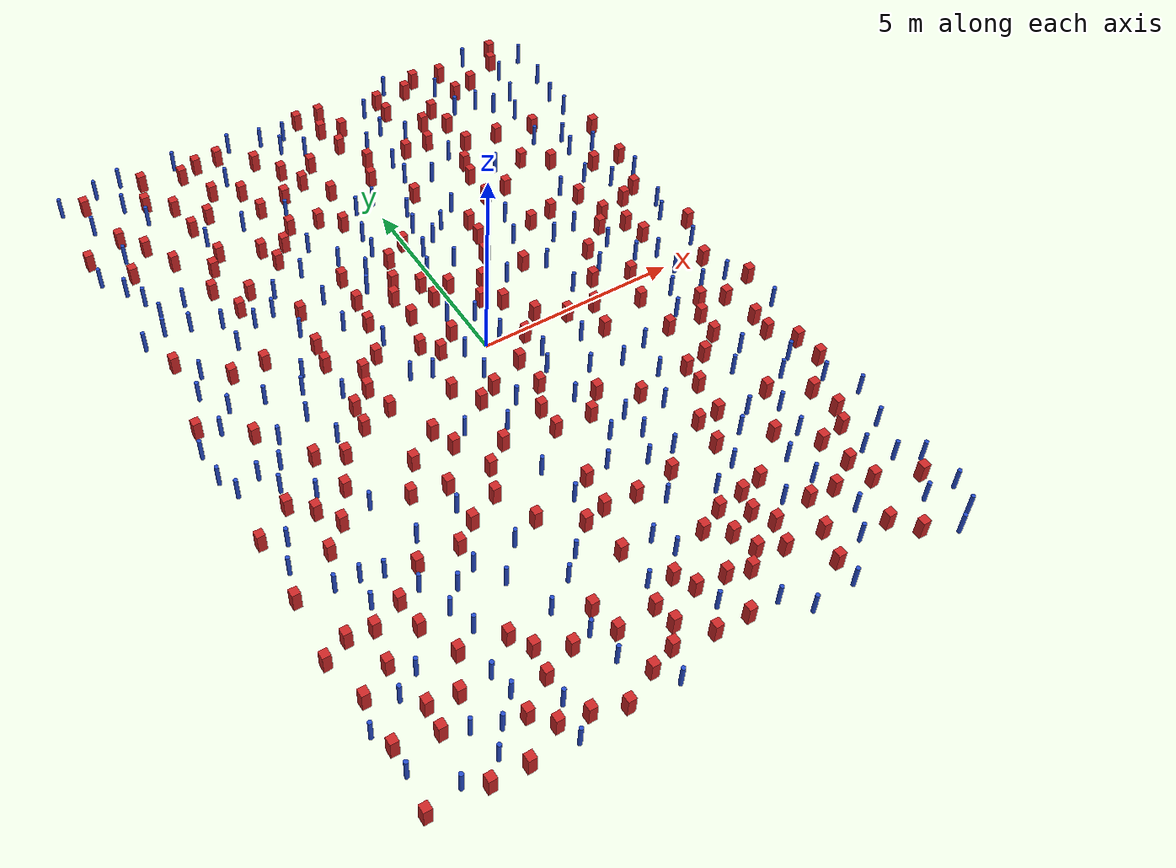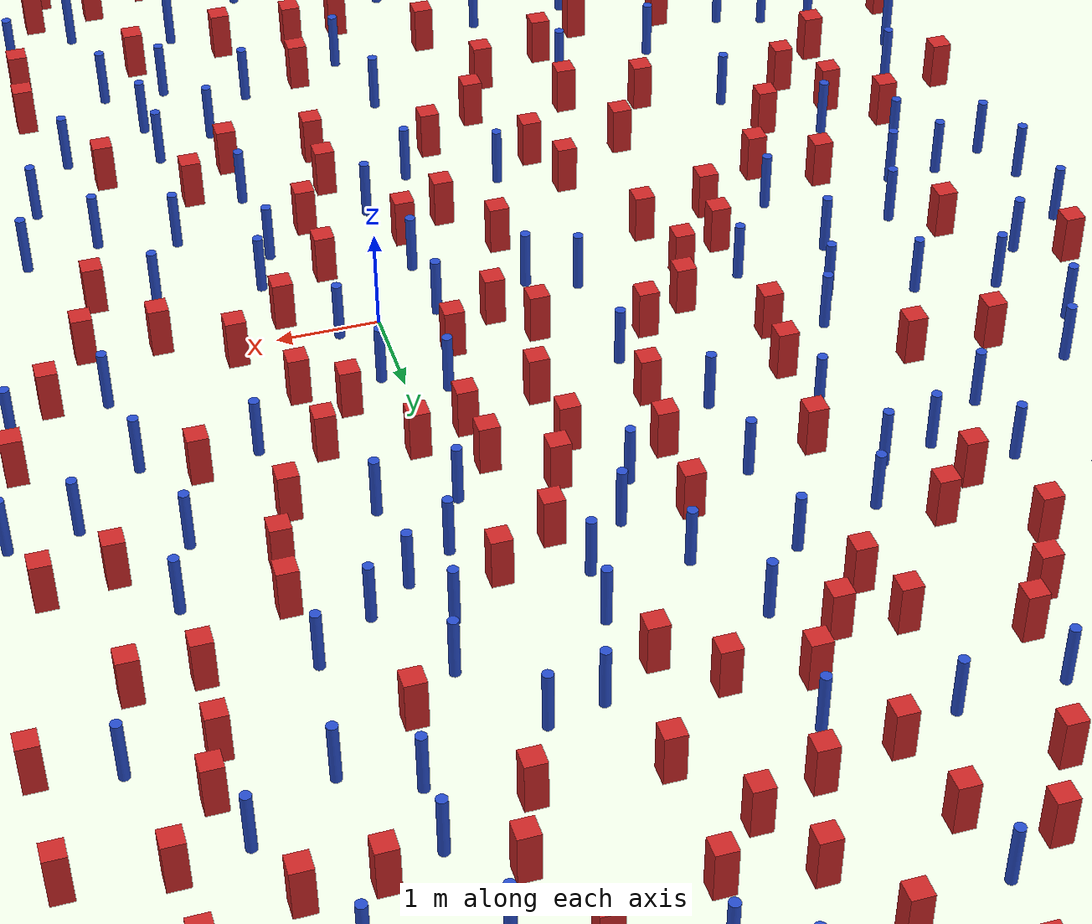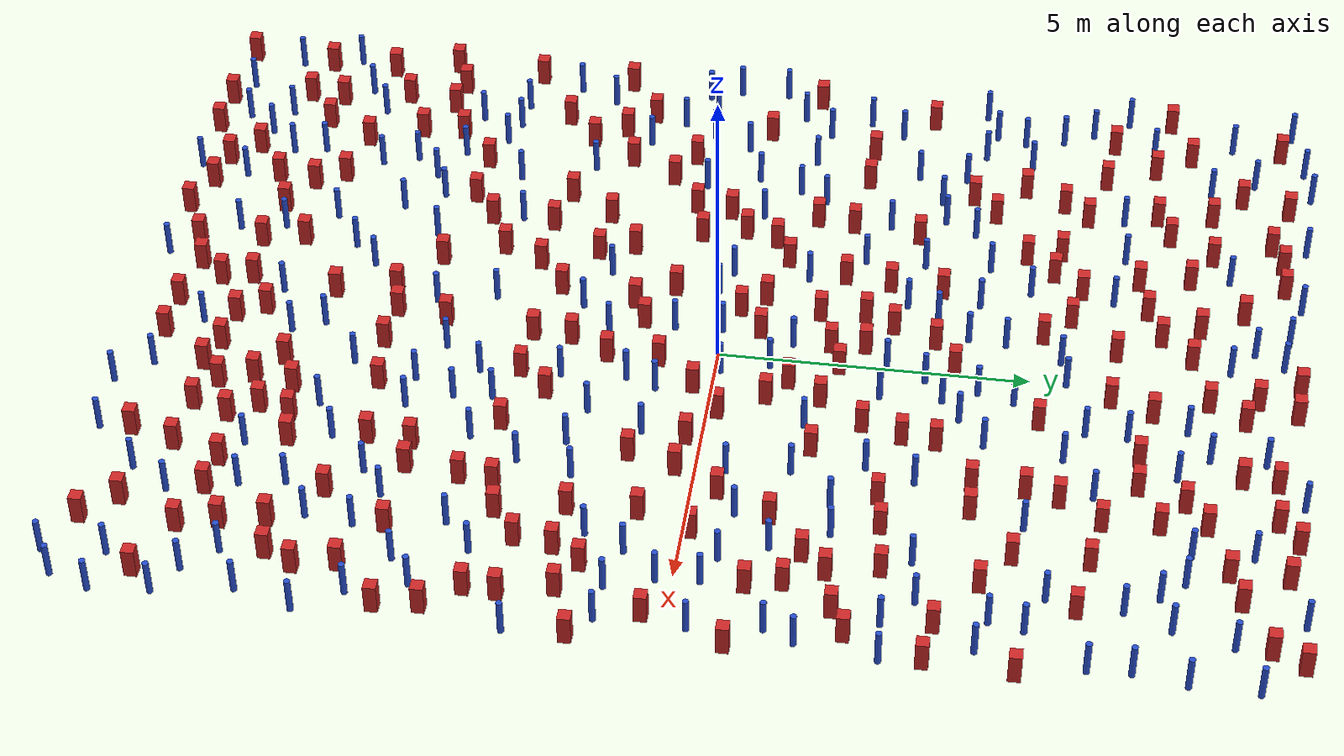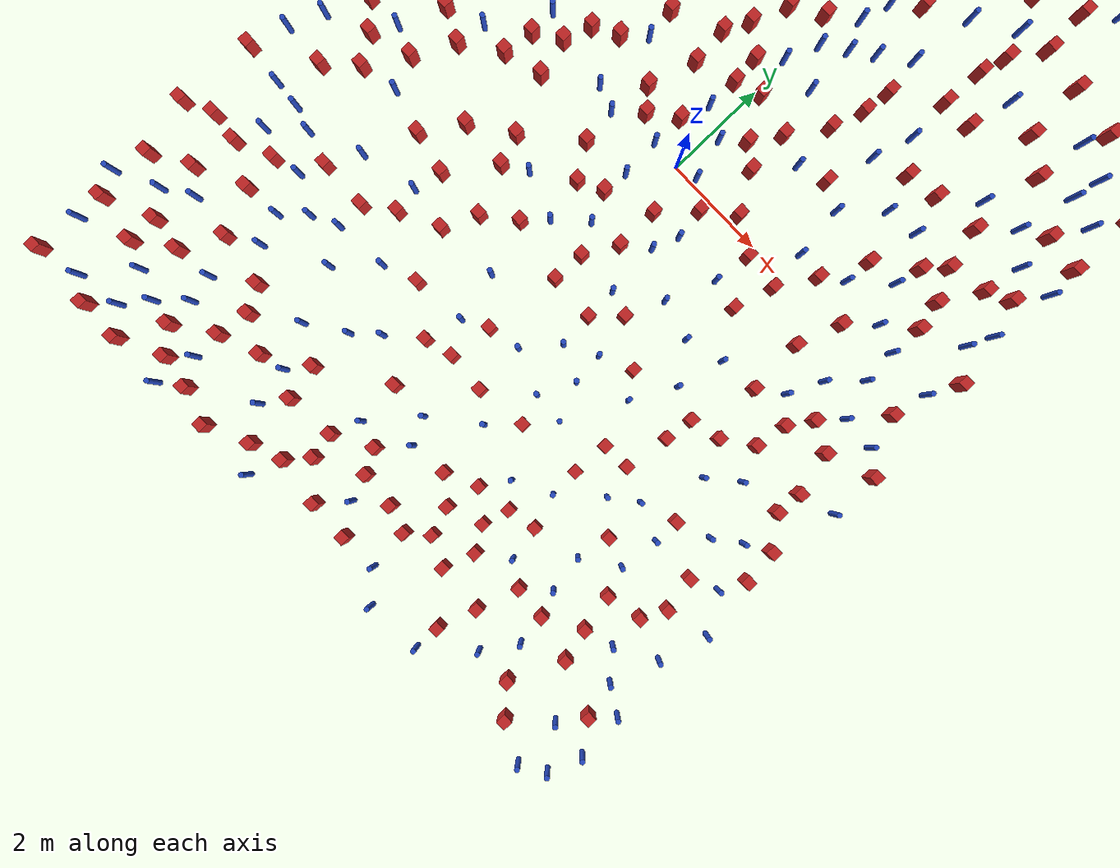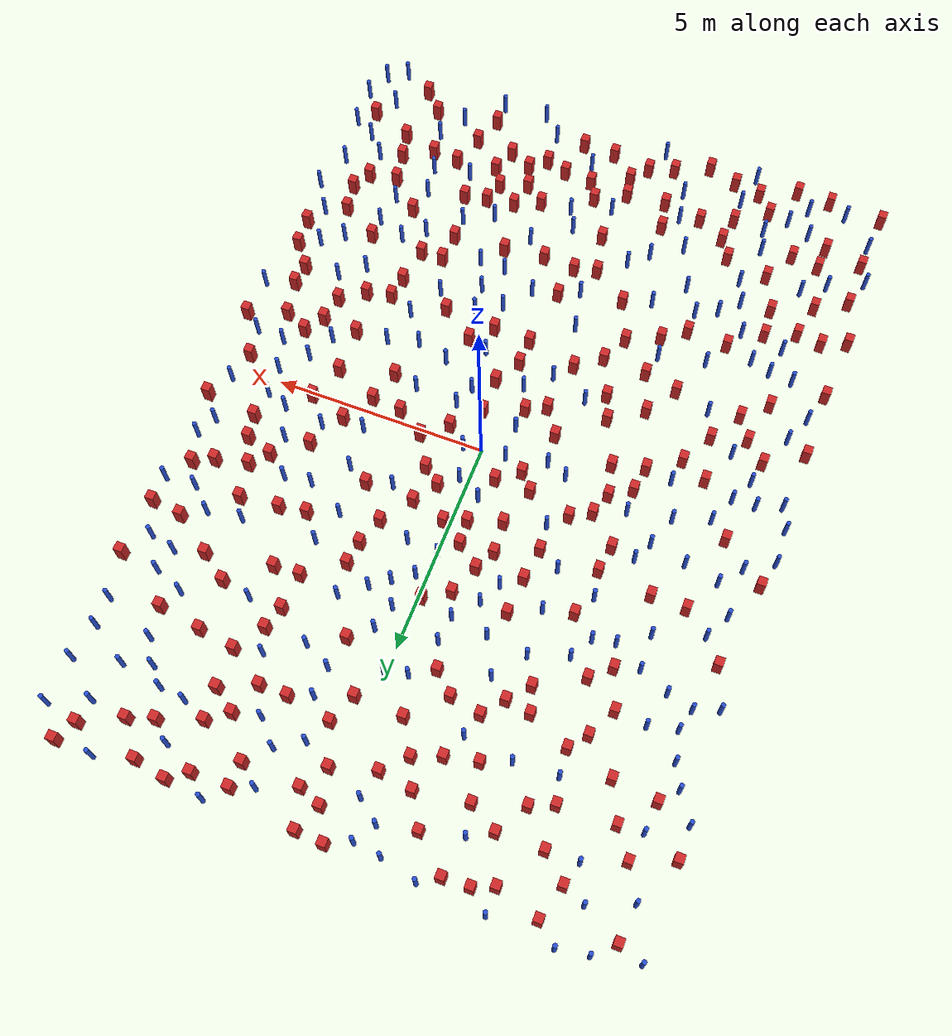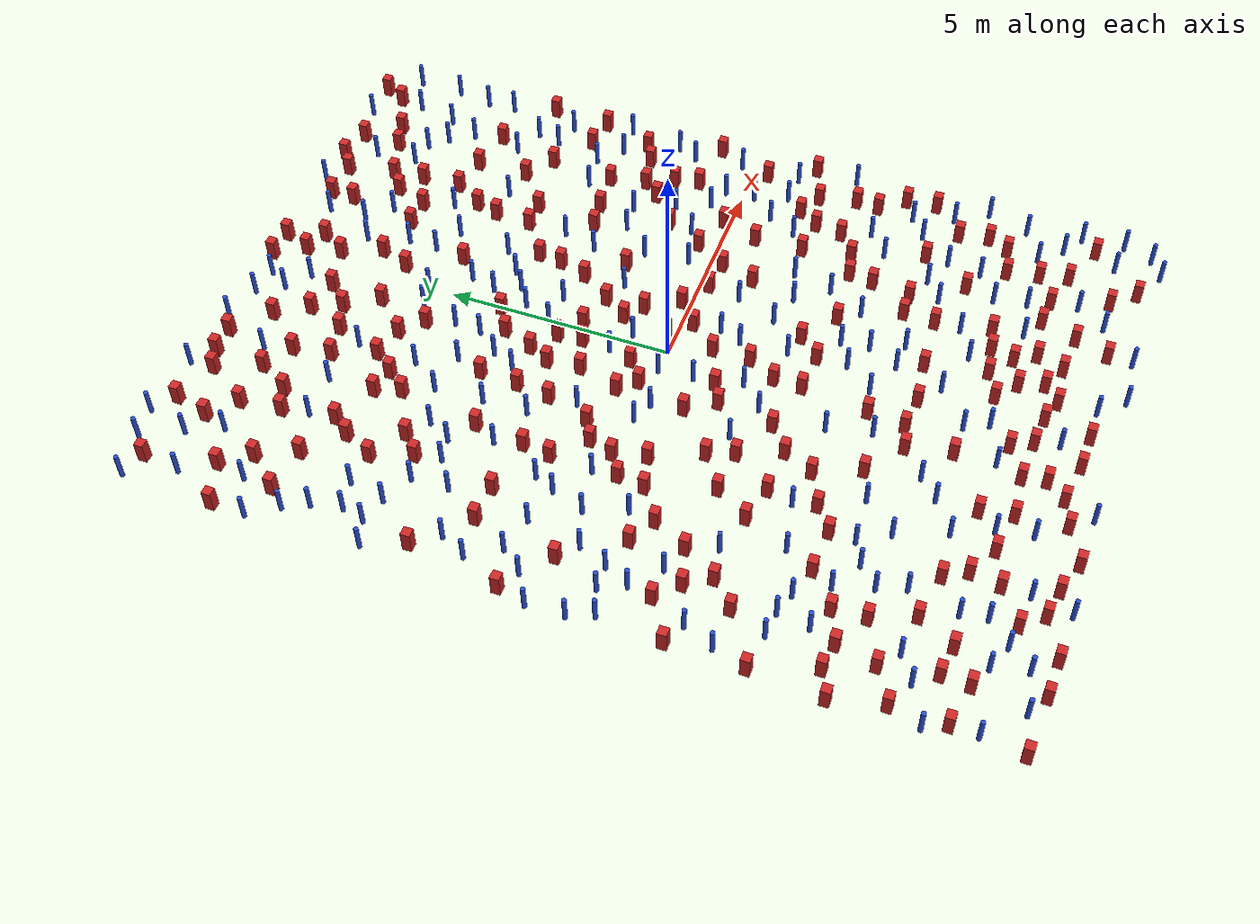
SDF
<sdf version="1.6">
  <model name="dense_89"><model name="pole_obstacle0">
  <static>true</static>
  <pose frame="">0.904406216591 7.52222214441 2.88873142074e-08 -9.90536689661e-09 4.60219948993e-07 -1.20965994957e-07</pose>
  <link name="link">
  <pose frame="">0 0 0.3 0 -0 0</pose>
    <inertial>
      <mass>1</mass>
      <inertia>
        <ixx>0.145833</ixx>
        <ixy>0</ixy>
        <ixz>0</ixz>
        <iyy>0.145833</iyy>
        <iyz>0</iyz>
        <izz>0.125</izz>
      </inertia>
    </inertial>
    <collision name="collision">
      <geometry>
        <cylinder>
          <radius>0.05</radius>
          <length>.6</length>
        </cylinder>
      </geometry>
      <max_contacts>10</max_contacts>
      <surface>
        <contact>
          <ode/>
        </contact>
        <bounce/>
        <friction>
          <torsional>
            <ode/>
          </torsional>
          <ode/>
        </friction>
      </surface>
    </collision>
    <visual name="visual">
      <geometry>
        <cylinder>
          <radius>0.05</radius>
          <length>.6</length>
        </cylinder>
      </geometry>
      <material>
        <script>
          <name>Gazebo/Blue</name>
          <uri>file://media/materials/scripts/gazebo.material</uri>
        </script>
      </material>
    </visual>
    <self_collide>0</self_collide>
    <kinematic>0</kinematic>
  </link>
</model>
<model name="pole_obstacle1">
  <static>true</static>
  <pose frame="">-1.30578073557 3.44537643412 2.88873142074e-08 -9.90536689791e-09 4.6021994899e-07 -1.20965994959e-07</pose>
  <link name="link">
  <pose frame="">0 0 0.3 0 -0 0</pose>
    <inertial>
      <mass>1</mass>
      <inertia>
        <ixx>0.145833</ixx>
        <ixy>0</ixy>
        <ixz>0</ixz>
        <iyy>0.145833</iyy>
        <iyz>0</iyz>
        <izz>0.125</izz>
      </inertia>
    </inertial>
    <collision name="collision">
      <geometry>
        <cylinder>
          <radius>0.05</radius>
          <length>.6</length>
        </cylinder>
      </geometry>
      <max_contacts>10</max_contacts>
      <surface>
        <contact>
          <ode/>
        </contact>
        <bounce/>
        <friction>
          <torsional>
            <ode/>
          </torsional>
          <ode/>
        </friction>
      </surface>
    </collision>
    <visual name="visual">
      <geometry>
        <cylinder>
          <radius>0.05</radius>
          <length>.6</length>
        </cylinder>
      </geometry>
      <material>
        <script>
          <name>Gazebo/Blue</name>
          <uri>file://media/materials/scripts/gazebo.material</uri>
        </script>
      </material>
    </visual>
    <self_collide>0</self_collide>
    <kinematic>0</kinematic>
  </link>
</model>
<model name="square_post_obstacle0">
  <static>true</static>
  <pose frame="">-5.45927733952 2.02925295843 8.22691968438e-08 7.2212513382e-06 -7.54495500217e-07 2.29674213826e-05</pose>
  <link name="link">
    <pose frame="">0 0 0.25 0 -0 0</pose>
    <inertial>
      <mass>100</mass>
      <inertia>
        <ixx>0.166667</ixx>
        <ixy>0</ixy>
        <ixz>0</ixz>
        <iyy>0.166667</iyy>
        <iyz>0</iyz>
        <izz>0.166667</izz>
      </inertia>
    </inertial>
    <collision name="collision">
      <geometry>
        <box>
          <size>.2 .2 .5</size>
        </box>
      </geometry>
      <max_contacts>10</max_contacts>
      <surface>
        <contact>
          <ode/>
        </contact>
        <bounce/>
        <friction>
          <torsional>
            <ode/>
          </torsional>
          <ode/>
        </friction>
      </surface>
    </collision>
    <visual name="visual">
      <geometry>
        <box>
          <size>.2 .2 .5</size>
        </box>
      </geometry>
      <material>
        <script>
          <name>Gazebo/Red</name>
          <uri>file://media/materials/scripts/gazebo.material</uri>
        </script>
      </material>
    </visual>
    <self_collide>0</self_collide>
    <kinematic>0</kinematic>
  </link>
</model>
<model name="square_post_obstacle1">
  <static>true</static>
  <pose frame="">-5.54529154885 6.84833027793 8.22691968438e-08 7.2212513382e-06 -7.54495500217e-07 2.29674213826e-05</pose>
  <link name="link">
    <pose frame="">0 0 0.25 0 -0 0</pose>
    <inertial>
      <mass>100</mass>
      <inertia>
        <ixx>0.166667</ixx>
        <ixy>0</ixy>
        <ixz>0</ixz>
        <iyy>0.166667</iyy>
        <iyz>0</iyz>
        <izz>0.166667</izz>
      </inertia>
    </inertial>
    <collision name="collision">
      <geometry>
        <box>
          <size>.2 .2 .5</size>
        </box>
      </geometry>
      <max_contacts>10</max_contacts>
      <surface>
        <contact>
          <ode/>
        </contact>
        <bounce/>
        <friction>
          <torsional>
            <ode/>
          </torsional>
          <ode/>
        </friction>
      </surface>
    </collision>
    <visual name="visual">
      <geometry>
        <box>
          <size>.2 .2 .5</size>
        </box>
      </geometry>
      <material>
        <script>
          <name>Gazebo/Red</name>
          <uri>file://media/materials/scripts/gazebo.material</uri>
        </script>
      </material>
    </visual>
    <self_collide>0</self_collide>
    <kinematic>0</kinematic>
  </link>
</model>
<model name="pole_obstacle2">
  <static>true</static>
  <pose frame="">1.8859989419 -9.4302232416 2.88873142074e-08 -9.90536690474e-09 4.60219948974e-07 -1.2096599497e-07</pose>
  <link name="link">
  <pose frame="">0 0 0.3 0 -0 0</pose>
    <inertial>
      <mass>1</mass>
      <inertia>
        <ixx>0.145833</ixx>
        <ixy>0</ixy>
        <ixz>0</ixz>
        <iyy>0.145833</iyy>
        <iyz>0</iyz>
        <izz>0.125</izz>
      </inertia>
    </inertial>
    <collision name="collision">
      <geometry>
        <cylinder>
          <radius>0.05</radius>
          <length>.6</length>
        </cylinder>
      </geometry>
      <max_contacts>10</max_contacts>
      <surface>
        <contact>
          <ode/>
        </contact>
        <bounce/>
        <friction>
          <torsional>
            <ode/>
          </torsional>
          <ode/>
        </friction>
      </surface>
    </collision>
    <visual name="visual">
      <geometry>
        <cylinder>
          <radius>0.05</radius>
          <length>.6</length>
        </cylinder>
      </geometry>
      <material>
        <script>
          <name>Gazebo/Blue</name>
          <uri>file://media/materials/scripts/gazebo.material</uri>
        </script>
      </material>
    </visual>
    <self_collide>0</self_collide>
    <kinematic>0</kinematic>
  </link>
</model>
<model name="pole_obstacle3">
  <static>true</static>
  <pose frame="">-4.23979861048 -0.73387135602 2.88873142074e-08 -9.90536689837e-09 4.60219948989e-07 -1.2096599496e-07</pose>
  <link name="link">
  <pose frame="">0 0 0.3 0 -0 0</pose>
    <inertial>
      <mass>1</mass>
      <inertia>
        <ixx>0.145833</ixx>
        <ixy>0</ixy>
        <ixz>0</ixz>
        <iyy>0.145833</iyy>
        <iyz>0</iyz>
        <izz>0.125</izz>
      </inertia>
    </inertial>
    <collision name="collision">
      <geometry>
        <cylinder>
          <radius>0.05</radius>
          <length>.6</length>
        </cylinder>
      </geometry>
      <max_contacts>10</max_contacts>
      <surface>
        <contact>
          <ode/>
        </contact>
        <bounce/>
        <friction>
          <torsional>
            <ode/>
          </torsional>
          <ode/>
        </friction>
      </surface>
    </collision>
    <visual name="visual">
      <geometry>
        <cylinder>
          <radius>0.05</radius>
          <length>.6</length>
        </cylinder>
      </geometry>
      <material>
        <script>
          <name>Gazebo/Blue</name>
          <uri>file://media/materials/scripts/gazebo.material</uri>
        </script>
      </material>
    </visual>
    <self_collide>0</self_collide>
    <kinematic>0</kinematic>
  </link>
</model>
<model name="pole_obstacle4">
  <static>true</static>
  <pose frame="">-0.492908654023 5.47763895851 2.88873142074e-08 -9.90536689758e-09 4.60219948991e-07 -1.20965994957e-07</pose>
  <link name="link">
  <pose frame="">0 0 0.3 0 -0 0</pose>
    <inertial>
      <mass>1</mass>
      <inertia>
        <ixx>0.145833</ixx>
        <ixy>0</ixy>
        <ixz>0</ixz>
        <iyy>0.145833</iyy>
        <iyz>0</iyz>
        <izz>0.125</izz>
      </inertia>
    </inertial>
    <collision name="collision">
      <geometry>
        <cylinder>
          <radius>0.05</radius>
          <length>.6</length>
        </cylinder>
      </geometry>
      <max_contacts>10</max_contacts>
      <surface>
        <contact>
          <ode/>
        </contact>
        <bounce/>
        <friction>
          <torsional>
            <ode/>
          </torsional>
          <ode/>
        </friction>
      </surface>
    </collision>
    <visual name="visual">
      <geometry>
        <cylinder>
          <radius>0.05</radius>
          <length>.6</length>
        </cylinder>
      </geometry>
      <material>
        <script>
          <name>Gazebo/Blue</name>
          <uri>file://media/materials/scripts/gazebo.material</uri>
        </script>
      </material>
    </visual>
    <self_collide>0</self_collide>
    <kinematic>0</kinematic>
  </link>
</model>
<model name="pole_obstacle5">
  <static>true</static>
  <pose frame="">-0.370727242179 1.18107586189 2.88873142074e-08 -9.90536689905e-09 4.60219948988e-07 -1.2096599496e-07</pose>
  <link name="link">
  <pose frame="">0 0 0.3 0 -0 0</pose>
    <inertial>
      <mass>1</mass>
      <inertia>
        <ixx>0.145833</ixx>
        <ixy>0</ixy>
        <ixz>0</ixz>
        <iyy>0.145833</iyy>
        <iyz>0</iyz>
        <izz>0.125</izz>
      </inertia>
    </inertial>
    <collision name="collision">
      <geometry>
        <cylinder>
          <radius>0.05</radius>
          <length>.6</length>
        </cylinder>
      </geometry>
      <max_contacts>10</max_contacts>
      <surface>
        <contact>
          <ode/>
        </contact>
        <bounce/>
        <friction>
          <torsional>
            <ode/>
          </torsional>
          <ode/>
        </friction>
      </surface>
    </collision>
    <visual name="visual">
      <geometry>
        <cylinder>
          <radius>0.05</radius>
          <length>.6</length>
        </cylinder>
      </geometry>
      <material>
        <script>
          <name>Gazebo/Blue</name>
          <uri>file://media/materials/scripts/gazebo.material</uri>
        </script>
      </material>
    </visual>
    <self_collide>0</self_collide>
    <kinematic>0</kinematic>
  </link>
</model>
<model name="pole_obstacle6">
  <static>true</static>
  <pose frame="">3.60519064606 0.736603006341 2.88873142074e-08 -9.90536689285e-09 4.60219949002e-07 -1.20965994953e-07</pose>
  <link name="link">
  <pose frame="">0 0 0.3 0 -0 0</pose>
    <inertial>
      <mass>1</mass>
      <inertia>
        <ixx>0.145833</ixx>
        <ixy>0</ixy>
        <ixz>0</ixz>
        <iyy>0.145833</iyy>
        <iyz>0</iyz>
        <izz>0.125</izz>
      </inertia>
    </inertial>
    <collision name="collision">
      <geometry>
        <cylinder>
          <radius>0.05</radius>
          <length>.6</length>
        </cylinder>
      </geometry>
      <max_contacts>10</max_contacts>
      <surface>
        <contact>
          <ode/>
        </contact>
        <bounce/>
        <friction>
          <torsional>
            <ode/>
          </torsional>
          <ode/>
        </friction>
      </surface>
    </collision>
    <visual name="visual">
      <geometry>
        <cylinder>
          <radius>0.05</radius>
          <length>.6</length>
        </cylinder>
      </geometry>
      <material>
        <script>
          <name>Gazebo/Blue</name>
          <uri>file://media/materials/scripts/gazebo.material</uri>
        </script>
      </material>
    </visual>
    <self_collide>0</self_collide>
    <kinematic>0</kinematic>
  </link>
</model>
<model name="square_post_obstacle2">
  <static>true</static>
  <pose frame="">0.835768978414 -7.92882272635 8.22691968438e-08 7.2212513382e-06 -7.54495500217e-07 2.29674213826e-05</pose>
  <link name="link">
    <pose frame="">0 0 0.25 0 -0 0</pose>
    <inertial>
      <mass>100</mass>
      <inertia>
        <ixx>0.166667</ixx>
        <ixy>0</ixy>
        <ixz>0</ixz>
        <iyy>0.166667</iyy>
        <iyz>0</iyz>
        <izz>0.166667</izz>
      </inertia>
    </inertial>
    <collision name="collision">
      <geometry>
        <box>
          <size>.2 .2 .5</size>
        </box>
      </geometry>
      <max_contacts>10</max_contacts>
      <surface>
        <contact>
          <ode/>
        </contact>
        <bounce/>
        <friction>
          <torsional>
            <ode/>
          </torsional>
          <ode/>
        </friction>
      </surface>
    </collision>
    <visual name="visual">
      <geometry>
        <box>
          <size>.2 .2 .5</size>
        </box>
      </geometry>
      <material>
        <script>
          <name>Gazebo/Red</name>
          <uri>file://media/materials/scripts/gazebo.material</uri>
        </script>
      </material>
    </visual>
    <self_collide>0</self_collide>
    <kinematic>0</kinematic>
  </link>
</model>
<model name="square_post_obstacle3">
  <static>true</static>
  <pose frame="">-2.73079464044 -7.73575036207 8.22691968438e-08 7.22125133819e-06 -7.54495500217e-07 2.29674213826e-05</pose>
  <link name="link">
    <pose frame="">0 0 0.25 0 -0 0</pose>
    <inertial>
      <mass>100</mass>
      <inertia>
        <ixx>0.166667</ixx>
        <ixy>0</ixy>
        <ixz>0</ixz>
        <iyy>0.166667</iyy>
        <iyz>0</iyz>
        <izz>0.166667</izz>
      </inertia>
    </inertial>
    <collision name="collision">
      <geometry>
        <box>
          <size>.2 .2 .5</size>
        </box>
      </geometry>
      <max_contacts>10</max_contacts>
      <surface>
        <contact>
          <ode/>
        </contact>
        <bounce/>
        <friction>
          <torsional>
            <ode/>
          </torsional>
          <ode/>
        </friction>
      </surface>
    </collision>
    <visual name="visual">
      <geometry>
        <box>
          <size>.2 .2 .5</size>
        </box>
      </geometry>
      <material>
        <script>
          <name>Gazebo/Red</name>
          <uri>file://media/materials/scripts/gazebo.material</uri>
        </script>
      </material>
    </visual>
    <self_collide>0</self_collide>
    <kinematic>0</kinematic>
  </link>
</model>
<model name="square_post_obstacle4">
  <static>true</static>
  <pose frame="">1.94861137037 8.92378379264 8.22691968438e-08 7.22125133819e-06 -7.54495500217e-07 2.29674213826e-05</pose>
  <link name="link">
    <pose frame="">0 0 0.25 0 -0 0</pose>
    <inertial>
      <mass>100</mass>
      <inertia>
        <ixx>0.166667</ixx>
        <ixy>0</ixy>
        <ixz>0</ixz>
        <iyy>0.166667</iyy>
        <iyz>0</iyz>
        <izz>0.166667</izz>
      </inertia>
    </inertial>
    <collision name="collision">
      <geometry>
        <box>
          <size>.2 .2 .5</size>
        </box>
      </geometry>
      <max_contacts>10</max_contacts>
      <surface>
        <contact>
          <ode/>
        </contact>
        <bounce/>
        <friction>
          <torsional>
            <ode/>
          </torsional>
          <ode/>
        </friction>
      </surface>
    </collision>
    <visual name="visual">
      <geometry>
        <box>
          <size>.2 .2 .5</size>
        </box>
      </geometry>
      <material>
        <script>
          <name>Gazebo/Red</name>
          <uri>file://media/materials/scripts/gazebo.material</uri>
        </script>
      </material>
    </visual>
    <self_collide>0</self_collide>
    <kinematic>0</kinematic>
  </link>
</model>
<model name="pole_obstacle7">
  <static>true</static>
  <pose frame="">0.56847447943 4.78392011947 2.88873142074e-08 -9.90536689661e-09 4.60219948993e-07 -1.20965994957e-07</pose>
  <link name="link">
  <pose frame="">0 0 0.3 0 -0 0</pose>
    <inertial>
      <mass>1</mass>
      <inertia>
        <ixx>0.145833</ixx>
        <ixy>0</ixy>
        <ixz>0</ixz>
        <iyy>0.145833</iyy>
        <iyz>0</iyz>
        <izz>0.125</izz>
      </inertia>
    </inertial>
    <collision name="collision">
      <geometry>
        <cylinder>
          <radius>0.05</radius>
          <length>.6</length>
        </cylinder>
      </geometry>
      <max_contacts>10</max_contacts>
      <surface>
        <contact>
          <ode/>
        </contact>
        <bounce/>
        <friction>
          <torsional>
            <ode/>
          </torsional>
          <ode/>
        </friction>
      </surface>
    </collision>
    <visual name="visual">
      <geometry>
        <cylinder>
          <radius>0.05</radius>
          <length>.6</length>
        </cylinder>
      </geometry>
      <material>
        <script>
          <name>Gazebo/Blue</name>
          <uri>file://media/materials/scripts/gazebo.material</uri>
        </script>
      </material>
    </visual>
    <self_collide>0</self_collide>
    <kinematic>0</kinematic>
  </link>
</model>
<model name="pole_obstacle8">
  <static>true</static>
  <pose frame="">3.61240412887 7.62931905213 2.88873142074e-08 -9.90536689859e-09 4.60219948989e-07 -1.20965994961e-07</pose>
  <link name="link">
  <pose frame="">0 0 0.3 0 -0 0</pose>
    <inertial>
      <mass>1</mass>
      <inertia>
        <ixx>0.145833</ixx>
        <ixy>0</ixy>
        <ixz>0</ixz>
        <iyy>0.145833</iyy>
        <iyz>0</iyz>
        <izz>0.125</izz>
      </inertia>
    </inertial>
    <collision name="collision">
      <geometry>
        <cylinder>
          <radius>0.05</radius>
          <length>.6</length>
        </cylinder>
      </geometry>
      <max_contacts>10</max_contacts>
      <surface>
        <contact>
          <ode/>
        </contact>
        <bounce/>
        <friction>
          <torsional>
            <ode/>
          </torsional>
          <ode/>
        </friction>
      </surface>
    </collision>
    <visual name="visual">
      <geometry>
        <cylinder>
          <radius>0.05</radius>
          <length>.6</length>
        </cylinder>
      </geometry>
      <material>
        <script>
          <name>Gazebo/Blue</name>
          <uri>file://media/materials/scripts/gazebo.material</uri>
        </script>
      </material>
    </visual>
    <self_collide>0</self_collide>
    <kinematic>0</kinematic>
  </link>
</model>
<model name="square_post_obstacle5">
  <static>true</static>
  <pose frame="">-1.06678376096 0.254342762164 8.22691968438e-08 7.2212513382e-06 -7.54495500217e-07 2.29674213826e-05</pose>
  <link name="link">
    <pose frame="">0 0 0.25 0 -0 0</pose>
    <inertial>
      <mass>100</mass>
      <inertia>
        <ixx>0.166667</ixx>
        <ixy>0</ixy>
        <ixz>0</ixz>
        <iyy>0.166667</iyy>
        <iyz>0</iyz>
        <izz>0.166667</izz>
      </inertia>
    </inertial>
    <collision name="collision">
      <geometry>
        <box>
          <size>.2 .2 .5</size>
        </box>
      </geometry>
      <max_contacts>10</max_contacts>
      <surface>
        <contact>
          <ode/>
        </contact>
        <bounce/>
        <friction>
          <torsional>
            <ode/>
          </torsional>
          <ode/>
        </friction>
      </surface>
    </collision>
    <visual name="visual">
      <geometry>
        <box>
          <size>.2 .2 .5</size>
        </box>
      </geometry>
      <material>
        <script>
          <name>Gazebo/Red</name>
          <uri>file://media/materials/scripts/gazebo.material</uri>
        </script>
      </material>
    </visual>
    <self_collide>0</self_collide>
    <kinematic>0</kinematic>
  </link>
</model>
<model name="square_post_obstacle6">
  <static>true</static>
  <pose frame="">-0.216550293037 -4.45965338208 8.22691968438e-08 7.22125133819e-06 -7.54495500217e-07 2.29674213826e-05</pose>
  <link name="link">
    <pose frame="">0 0 0.25 0 -0 0</pose>
    <inertial>
      <mass>100</mass>
      <inertia>
        <ixx>0.166667</ixx>
        <ixy>0</ixy>
        <ixz>0</ixz>
        <iyy>0.166667</iyy>
        <iyz>0</iyz>
        <izz>0.166667</izz>
      </inertia>
    </inertial>
    <collision name="collision">
      <geometry>
        <box>
          <size>.2 .2 .5</size>
        </box>
      </geometry>
      <max_contacts>10</max_contacts>
      <surface>
        <contact>
          <ode/>
        </contact>
        <bounce/>
        <friction>
          <torsional>
            <ode/>
          </torsional>
          <ode/>
        </friction>
      </surface>
    </collision>
    <visual name="visual">
      <geometry>
        <box>
          <size>.2 .2 .5</size>
        </box>
      </geometry>
      <material>
        <script>
          <name>Gazebo/Red</name>
          <uri>file://media/materials/scripts/gazebo.material</uri>
        </script>
      </material>
    </visual>
    <self_collide>0</self_collide>
    <kinematic>0</kinematic>
  </link>
</model>
<model name="square_post_obstacle7">
  <static>true</static>
  <pose frame="">-2.40024444192 0.891105501859 8.22691968438e-08 7.2212513382e-06 -7.54495500217e-07 2.29674213826e-05</pose>
  <link name="link">
    <pose frame="">0 0 0.25 0 -0 0</pose>
    <inertial>
      <mass>100</mass>
      <inertia>
        <ixx>0.166667</ixx>
        <ixy>0</ixy>
        <ixz>0</ixz>
        <iyy>0.166667</iyy>
        <iyz>0</iyz>
        <izz>0.166667</izz>
      </inertia>
    </inertial>
    <collision name="collision">
      <geometry>
        <box>
          <size>.2 .2 .5</size>
        </box>
      </geometry>
      <max_contacts>10</max_contacts>
      <surface>
        <contact>
          <ode/>
        </contact>
        <bounce/>
        <friction>
          <torsional>
            <ode/>
          </torsional>
          <ode/>
        </friction>
      </surface>
    </collision>
    <visual name="visual">
      <geometry>
        <box>
          <size>.2 .2 .5</size>
        </box>
      </geometry>
      <material>
        <script>
          <name>Gazebo/Red</name>
          <uri>file://media/materials/scripts/gazebo.material</uri>
        </script>
      </material>
    </visual>
    <self_collide>0</self_collide>
    <kinematic>0</kinematic>
  </link>
</model>
<model name="pole_obstacle9">
  <static>true</static>
  <pose frame="">4.58769082749 -4.96081243635 2.88873142074e-08 -9.90536690842e-09 4.60219948965e-07 -1.20965994976e-07</pose>
  <link name="link">
  <pose frame="">0 0 0.3 0 -0 0</pose>
    <inertial>
      <mass>1</mass>
      <inertia>
        <ixx>0.145833</ixx>
        <ixy>0</ixy>
        <ixz>0</ixz>
        <iyy>0.145833</iyy>
        <iyz>0</iyz>
        <izz>0.125</izz>
      </inertia>
    </inertial>
    <collision name="collision">
      <geometry>
        <cylinder>
          <radius>0.05</radius>
          <length>.6</length>
        </cylinder>
      </geometry>
      <max_contacts>10</max_contacts>
      <surface>
        <contact>
          <ode/>
        </contact>
        <bounce/>
        <friction>
          <torsional>
            <ode/>
          </torsional>
          <ode/>
        </friction>
      </surface>
    </collision>
    <visual name="visual">
      <geometry>
        <cylinder>
          <radius>0.05</radius>
          <length>.6</length>
        </cylinder>
      </geometry>
      <material>
        <script>
          <name>Gazebo/Blue</name>
          <uri>file://media/materials/scripts/gazebo.material</uri>
        </script>
      </material>
    </visual>
    <self_collide>0</self_collide>
    <kinematic>0</kinematic>
  </link>
</model>
<model name="pole_obstacle10">
  <static>true</static>
  <pose frame="">-6.1325217128 -6.95859032905 2.88873142074e-08 -9.90536690842e-09 4.60219948965e-07 -1.20965994976e-07</pose>
  <link name="link">
  <pose frame="">0 0 0.3 0 -0 0</pose>
    <inertial>
      <mass>1</mass>
      <inertia>
        <ixx>0.145833</ixx>
        <ixy>0</ixy>
        <ixz>0</ixz>
        <iyy>0.145833</iyy>
        <iyz>0</iyz>
        <izz>0.125</izz>
      </inertia>
    </inertial>
    <collision name="collision">
      <geometry>
        <cylinder>
          <radius>0.05</radius>
          <length>.6</length>
        </cylinder>
      </geometry>
      <max_contacts>10</max_contacts>
      <surface>
        <contact>
          <ode/>
        </contact>
        <bounce/>
        <friction>
          <torsional>
            <ode/>
          </torsional>
          <ode/>
        </friction>
      </surface>
    </collision>
    <visual name="visual">
      <geometry>
        <cylinder>
          <radius>0.05</radius>
          <length>.6</length>
        </cylinder>
      </geometry>
      <material>
        <script>
          <name>Gazebo/Blue</name>
          <uri>file://media/materials/scripts/gazebo.material</uri>
        </script>
      </material>
    </visual>
    <self_collide>0</self_collide>
    <kinematic>0</kinematic>
  </link>
</model>
<model name="pole_obstacle11">
  <static>true</static>
  <pose frame="">-6.10150141757 6.80704328799 2.88873142074e-08 -9.90536690842e-09 4.60219948965e-07 -1.20965994976e-07</pose>
  <link name="link">
  <pose frame="">0 0 0.3 0 -0 0</pose>
    <inertial>
      <mass>1</mass>
      <inertia>
        <ixx>0.145833</ixx>
        <ixy>0</ixy>
        <ixz>0</ixz>
        <iyy>0.145833</iyy>
        <iyz>0</iyz>
        <izz>0.125</izz>
      </inertia>
    </inertial>
    <collision name="collision">
      <geometry>
        <cylinder>
          <radius>0.05</radius>
          <length>.6</length>
        </cylinder>
      </geometry>
      <max_contacts>10</max_contacts>
      <surface>
        <contact>
          <ode/>
        </contact>
        <bounce/>
        <friction>
          <torsional>
            <ode/>
          </torsional>
          <ode/>
        </friction>
      </surface>
    </collision>
    <visual name="visual">
      <geometry>
        <cylinder>
          <radius>0.05</radius>
          <length>.6</length>
        </cylinder>
      </geometry>
      <material>
        <script>
          <name>Gazebo/Blue</name>
          <uri>file://media/materials/scripts/gazebo.material</uri>
        </script>
      </material>
    </visual>
    <self_collide>0</self_collide>
    <kinematic>0</kinematic>
  </link>
</model>
<model name="pole_obstacle12">
  <static>true</static>
  <pose frame="">-4.60353962773 -4.98954134654 2.88873142074e-08 -9.90536690842e-09 4.60219948965e-07 -1.20965994976e-07</pose>
  <link name="link">
  <pose frame="">0 0 0.3 0 -0 0</pose>
    <inertial>
      <mass>1</mass>
      <inertia>
        <ixx>0.145833</ixx>
        <ixy>0</ixy>
        <ixz>0</ixz>
        <iyy>0.145833</iyy>
        <iyz>0</iyz>
        <izz>0.125</izz>
      </inertia>
    </inertial>
    <collision name="collision">
      <geometry>
        <cylinder>
          <radius>0.05</radius>
          <length>.6</length>
        </cylinder>
      </geometry>
      <max_contacts>10</max_contacts>
      <surface>
        <contact>
          <ode/>
        </contact>
        <bounce/>
        <friction>
          <torsional>
            <ode/>
          </torsional>
          <ode/>
        </friction>
      </surface>
    </collision>
    <visual name="visual">
      <geometry>
        <cylinder>
          <radius>0.05</radius>
          <length>.6</length>
        </cylinder>
      </geometry>
      <material>
        <script>
          <name>Gazebo/Blue</name>
          <uri>file://media/materials/scripts/gazebo.material</uri>
        </script>
      </material>
    </visual>
    <self_collide>0</self_collide>
    <kinematic>0</kinematic>
  </link>
</model>
<model name="square_post_obstacle8">
  <static>true</static>
  <pose frame="">-1.11404172992 1.54842886564 8.22691968438e-08 7.2212513382e-06 -7.54495500217e-07 2.29674213826e-05</pose>
  <link name="link">
    <pose frame="">0 0 0.25 0 -0 0</pose>
    <inertial>
      <mass>100</mass>
      <inertia>
        <ixx>0.166667</ixx>
        <ixy>0</ixy>
        <ixz>0</ixz>
        <iyy>0.166667</iyy>
        <iyz>0</iyz>
        <izz>0.166667</izz>
      </inertia>
    </inertial>
    <collision name="collision">
      <geometry>
        <box>
          <size>.2 .2 .5</size>
        </box>
      </geometry>
      <max_contacts>10</max_contacts>
      <surface>
        <contact>
          <ode/>
        </contact>
        <bounce/>
        <friction>
          <torsional>
            <ode/>
          </torsional>
          <ode/>
        </friction>
      </surface>
    </collision>
    <visual name="visual">
      <geometry>
        <box>
          <size>.2 .2 .5</size>
        </box>
      </geometry>
      <material>
        <script>
          <name>Gazebo/Red</name>
          <uri>file://media/materials/scripts/gazebo.material</uri>
        </script>
      </material>
    </visual>
    <self_collide>0</self_collide>
    <kinematic>0</kinematic>
  </link>
</model>
<model name="square_post_obstacle9">
  <static>true</static>
  <pose frame="">-3.42915403377 1.87004693417 8.22691968438e-08 7.2212513382e-06 -7.54495500217e-07 2.29674213826e-05</pose>
  <link name="link">
    <pose frame="">0 0 0.25 0 -0 0</pose>
    <inertial>
      <mass>100</mass>
      <inertia>
        <ixx>0.166667</ixx>
        <ixy>0</ixy>
        <ixz>0</ixz>
        <iyy>0.166667</iyy>
        <iyz>0</iyz>
        <izz>0.166667</izz>
      </inertia>
    </inertial>
    <collision name="collision">
      <geometry>
        <box>
          <size>.2 .2 .5</size>
        </box>
      </geometry>
      <max_contacts>10</max_contacts>
      <surface>
        <contact>
          <ode/>
        </contact>
        <bounce/>
        <friction>
          <torsional>
            <ode/>
          </torsional>
          <ode/>
        </friction>
      </surface>
    </collision>
    <visual name="visual">
      <geometry>
        <box>
          <size>.2 .2 .5</size>
        </box>
      </geometry>
      <material>
        <script>
          <name>Gazebo/Red</name>
          <uri>file://media/materials/scripts/gazebo.material</uri>
        </script>
      </material>
    </visual>
    <self_collide>0</self_collide>
    <kinematic>0</kinematic>
  </link>
</model>
<model name="pole_obstacle13">
  <static>true</static>
  <pose frame="">-1.08018354403 8.55631461394 2.88873142074e-08 -9.90536690474e-09 4.60219948974e-07 -1.2096599497e-07</pose>
  <link name="link">
  <pose frame="">0 0 0.3 0 -0 0</pose>
    <inertial>
      <mass>1</mass>
      <inertia>
        <ixx>0.145833</ixx>
        <ixy>0</ixy>
        <ixz>0</ixz>
        <iyy>0.145833</iyy>
        <iyz>0</iyz>
        <izz>0.125</izz>
      </inertia>
    </inertial>
    <collision name="collision">
      <geometry>
        <cylinder>
          <radius>0.05</radius>
          <length>.6</length>
        </cylinder>
      </geometry>
      <max_contacts>10</max_contacts>
      <surface>
        <contact>
          <ode/>
        </contact>
        <bounce/>
        <friction>
          <torsional>
            <ode/>
          </torsional>
          <ode/>
        </friction>
      </surface>
    </collision>
    <visual name="visual">
      <geometry>
        <cylinder>
          <radius>0.05</radius>
          <length>.6</length>
        </cylinder>
      </geometry>
      <material>
        <script>
          <name>Gazebo/Blue</name>
          <uri>file://media/materials/scripts/gazebo.material</uri>
        </script>
      </material>
    </visual>
    <self_collide>0</self_collide>
    <kinematic>0</kinematic>
  </link>
</model>
<model name="square_post_obstacle10">
  <static>true</static>
  <pose frame="">-5.83038132791 -5.41158651365 8.22691968438e-08 7.2212513382e-06 -7.54495500217e-07 2.29674213826e-05</pose>
  <link name="link">
    <pose frame="">0 0 0.25 0 -0 0</pose>
    <inertial>
      <mass>100</mass>
      <inertia>
        <ixx>0.166667</ixx>
        <ixy>0</ixy>
        <ixz>0</ixz>
        <iyy>0.166667</iyy>
        <iyz>0</iyz>
        <izz>0.166667</izz>
      </inertia>
    </inertial>
    <collision name="collision">
      <geometry>
        <box>
          <size>.2 .2 .5</size>
        </box>
      </geometry>
      <max_contacts>10</max_contacts>
      <surface>
        <contact>
          <ode/>
        </contact>
        <bounce/>
        <friction>
          <torsional>
            <ode/>
          </torsional>
          <ode/>
        </friction>
      </surface>
    </collision>
    <visual name="visual">
      <geometry>
        <box>
          <size>.2 .2 .5</size>
        </box>
      </geometry>
      <material>
        <script>
          <name>Gazebo/Red</name>
          <uri>file://media/materials/scripts/gazebo.material</uri>
        </script>
      </material>
    </visual>
    <self_collide>0</self_collide>
    <kinematic>0</kinematic>
  </link>
</model>
<model name="square_post_obstacle11">
  <static>true</static>
  <pose frame="">-2.19722956945 -2.26481945493 8.22691968438e-08 7.2212513382e-06 -7.54495500217e-07 2.29674213826e-05</pose>
  <link name="link">
    <pose frame="">0 0 0.25 0 -0 0</pose>
    <inertial>
      <mass>100</mass>
      <inertia>
        <ixx>0.166667</ixx>
        <ixy>0</ixy>
        <ixz>0</ixz>
        <iyy>0.166667</iyy>
        <iyz>0</iyz>
        <izz>0.166667</izz>
      </inertia>
    </inertial>
    <collision name="collision">
      <geometry>
        <box>
          <size>.2 .2 .5</size>
        </box>
      </geometry>
      <max_contacts>10</max_contacts>
      <surface>
        <contact>
          <ode/>
        </contact>
        <bounce/>
        <friction>
          <torsional>
            <ode/>
          </torsional>
          <ode/>
        </friction>
      </surface>
    </collision>
    <visual name="visual">
      <geometry>
        <box>
          <size>.2 .2 .5</size>
        </box>
      </geometry>
      <material>
        <script>
          <name>Gazebo/Red</name>
          <uri>file://media/materials/scripts/gazebo.material</uri>
        </script>
      </material>
    </visual>
    <self_collide>0</self_collide>
    <kinematic>0</kinematic>
  </link>
</model>
<model name="pole_obstacle14">
  <static>true</static>
  <pose frame="">-6.65760628513 -3.29719813045 2.88873142074e-08 -9.90536690245e-09 4.6021994898e-07 -1.20965994966e-07</pose>
  <link name="link">
  <pose frame="">0 0 0.3 0 -0 0</pose>
    <inertial>
      <mass>1</mass>
      <inertia>
        <ixx>0.145833</ixx>
        <ixy>0</ixy>
        <ixz>0</ixz>
        <iyy>0.145833</iyy>
        <iyz>0</iyz>
        <izz>0.125</izz>
      </inertia>
    </inertial>
    <collision name="collision">
      <geometry>
        <cylinder>
          <radius>0.05</radius>
          <length>.6</length>
        </cylinder>
      </geometry>
      <max_contacts>10</max_contacts>
      <surface>
        <contact>
          <ode/>
        </contact>
        <bounce/>
        <friction>
          <torsional>
            <ode/>
          </torsional>
          <ode/>
        </friction>
      </surface>
    </collision>
    <visual name="visual">
      <geometry>
        <cylinder>
          <radius>0.05</radius>
          <length>.6</length>
        </cylinder>
      </geometry>
      <material>
        <script>
          <name>Gazebo/Blue</name>
          <uri>file://media/materials/scripts/gazebo.material</uri>
        </script>
      </material>
    </visual>
    <self_collide>0</self_collide>
    <kinematic>0</kinematic>
  </link>
</model>
<model name="pole_obstacle15">
  <static>true</static>
  <pose frame="">0.769162764742 -1.35992684402 2.88873142074e-08 -9.90536689855e-09 4.60219948989e-07 -1.20965994962e-07</pose>
  <link name="link">
  <pose frame="">0 0 0.3 0 -0 0</pose>
    <inertial>
      <mass>1</mass>
      <inertia>
        <ixx>0.145833</ixx>
        <ixy>0</ixy>
        <ixz>0</ixz>
        <iyy>0.145833</iyy>
        <iyz>0</iyz>
        <izz>0.125</izz>
      </inertia>
    </inertial>
    <collision name="collision">
      <geometry>
        <cylinder>
          <radius>0.05</radius>
          <length>.6</length>
        </cylinder>
      </geometry>
      <max_contacts>10</max_contacts>
      <surface>
        <contact>
          <ode/>
        </contact>
        <bounce/>
        <friction>
          <torsional>
            <ode/>
          </torsional>
          <ode/>
        </friction>
      </surface>
    </collision>
    <visual name="visual">
      <geometry>
        <cylinder>
          <radius>0.05</radius>
          <length>.6</length>
        </cylinder>
      </geometry>
      <material>
        <script>
          <name>Gazebo/Blue</name>
          <uri>file://media/materials/scripts/gazebo.material</uri>
        </script>
      </material>
    </visual>
    <self_collide>0</self_collide>
    <kinematic>0</kinematic>
  </link>
</model>
<model name="square_post_obstacle12">
  <static>true</static>
  <pose frame="">-4.7514764796 -9.38718271568 8.22691968438e-08 7.2212513382e-06 -7.54495500217e-07 2.29674213826e-05</pose>
  <link name="link">
    <pose frame="">0 0 0.25 0 -0 0</pose>
    <inertial>
      <mass>100</mass>
      <inertia>
        <ixx>0.166667</ixx>
        <ixy>0</ixy>
        <ixz>0</ixz>
        <iyy>0.166667</iyy>
        <iyz>0</iyz>
        <izz>0.166667</izz>
      </inertia>
    </inertial>
    <collision name="collision">
      <geometry>
        <box>
          <size>.2 .2 .5</size>
        </box>
      </geometry>
      <max_contacts>10</max_contacts>
      <surface>
        <contact>
          <ode/>
        </contact>
        <bounce/>
        <friction>
          <torsional>
            <ode/>
          </torsional>
          <ode/>
        </friction>
      </surface>
    </collision>
    <visual name="visual">
      <geometry>
        <box>
          <size>.2 .2 .5</size>
        </box>
      </geometry>
      <material>
        <script>
          <name>Gazebo/Red</name>
          <uri>file://media/materials/scripts/gazebo.material</uri>
        </script>
      </material>
    </visual>
    <self_collide>0</self_collide>
    <kinematic>0</kinematic>
  </link>
</model>
<model name="pole_obstacle16">
  <static>true</static>
  <pose frame="">-0.794665831123 9.01811968943 2.88873142074e-08 -9.90536690779e-09 4.60219948967e-07 -1.20965994975e-07</pose>
  <link name="link">
  <pose frame="">0 0 0.3 0 -0 0</pose>
    <inertial>
      <mass>1</mass>
      <inertia>
        <ixx>0.145833</ixx>
        <ixy>0</ixy>
        <ixz>0</ixz>
        <iyy>0.145833</iyy>
        <iyz>0</iyz>
        <izz>0.125</izz>
      </inertia>
    </inertial>
    <collision name="collision">
      <geometry>
        <cylinder>
          <radius>0.05</radius>
          <length>.6</length>
        </cylinder>
      </geometry>
      <max_contacts>10</max_contacts>
      <surface>
        <contact>
          <ode/>
        </contact>
        <bounce/>
        <friction>
          <torsional>
            <ode/>
          </torsional>
          <ode/>
        </friction>
      </surface>
    </collision>
    <visual name="visual">
      <geometry>
        <cylinder>
          <radius>0.05</radius>
          <length>.6</length>
        </cylinder>
      </geometry>
      <material>
        <script>
          <name>Gazebo/Blue</name>
          <uri>file://media/materials/scripts/gazebo.material</uri>
        </script>
      </material>
    </visual>
    <self_collide>0</self_collide>
    <kinematic>0</kinematic>
  </link>
</model>
<model name="pole_obstacle17">
  <static>true</static>
  <pose frame="">0.95714295873 -0.871402900502 2.88873142074e-08 -9.90536689596e-09 4.60219948995e-07 -1.20965994957e-07</pose>
  <link name="link">
  <pose frame="">0 0 0.3 0 -0 0</pose>
    <inertial>
      <mass>1</mass>
      <inertia>
        <ixx>0.145833</ixx>
        <ixy>0</ixy>
        <ixz>0</ixz>
        <iyy>0.145833</iyy>
        <iyz>0</iyz>
        <izz>0.125</izz>
      </inertia>
    </inertial>
    <collision name="collision">
      <geometry>
        <cylinder>
          <radius>0.05</radius>
          <length>.6</length>
        </cylinder>
      </geometry>
      <max_contacts>10</max_contacts>
      <surface>
        <contact>
          <ode/>
        </contact>
        <bounce/>
        <friction>
          <torsional>
            <ode/>
          </torsional>
          <ode/>
        </friction>
      </surface>
    </collision>
    <visual name="visual">
      <geometry>
        <cylinder>
          <radius>0.05</radius>
          <length>.6</length>
        </cylinder>
      </geometry>
      <material>
        <script>
          <name>Gazebo/Blue</name>
          <uri>file://media/materials/scripts/gazebo.material</uri>
        </script>
      </material>
    </visual>
    <self_collide>0</self_collide>
    <kinematic>0</kinematic>
  </link>
</model>
<model name="square_post_obstacle13">
  <static>true</static>
  <pose frame="">0.13644949585 -7.86097893207 8.22691968438e-08 7.2212513382e-06 -7.54495500217e-07 2.29674213826e-05</pose>
  <link name="link">
    <pose frame="">0 0 0.25 0 -0 0</pose>
    <inertial>
      <mass>100</mass>
      <inertia>
        <ixx>0.166667</ixx>
        <ixy>0</ixy>
        <ixz>0</ixz>
        <iyy>0.166667</iyy>
        <iyz>0</iyz>
        <izz>0.166667</izz>
      </inertia>
    </inertial>
    <collision name="collision">
      <geometry>
        <box>
          <size>.2 .2 .5</size>
        </box>
      </geometry>
      <max_contacts>10</max_contacts>
      <surface>
        <contact>
          <ode/>
        </contact>
        <bounce/>
        <friction>
          <torsional>
            <ode/>
          </torsional>
          <ode/>
        </friction>
      </surface>
    </collision>
    <visual name="visual">
      <geometry>
        <box>
          <size>.2 .2 .5</size>
        </box>
      </geometry>
      <material>
        <script>
          <name>Gazebo/Red</name>
          <uri>file://media/materials/scripts/gazebo.material</uri>
        </script>
      </material>
    </visual>
    <self_collide>0</self_collide>
    <kinematic>0</kinematic>
  </link>
</model>
<model name="pole_obstacle18">
  <static>true</static>
  <pose frame="">-3.92017923229 -5.36507998804 2.88873142074e-08 -9.90536689859e-09 4.60219948989e-07 -1.20965994961e-07</pose>
  <link name="link">
  <pose frame="">0 0 0.3 0 -0 0</pose>
    <inertial>
      <mass>1</mass>
      <inertia>
        <ixx>0.145833</ixx>
        <ixy>0</ixy>
        <ixz>0</ixz>
        <iyy>0.145833</iyy>
        <iyz>0</iyz>
        <izz>0.125</izz>
      </inertia>
    </inertial>
    <collision name="collision">
      <geometry>
        <cylinder>
          <radius>0.05</radius>
          <length>.6</length>
        </cylinder>
      </geometry>
      <max_contacts>10</max_contacts>
      <surface>
        <contact>
          <ode/>
        </contact>
        <bounce/>
        <friction>
          <torsional>
            <ode/>
          </torsional>
          <ode/>
        </friction>
      </surface>
    </collision>
    <visual name="visual">
      <geometry>
        <cylinder>
          <radius>0.05</radius>
          <length>.6</length>
        </cylinder>
      </geometry>
      <material>
        <script>
          <name>Gazebo/Blue</name>
          <uri>file://media/materials/scripts/gazebo.material</uri>
        </script>
      </material>
    </visual>
    <self_collide>0</self_collide>
    <kinematic>0</kinematic>
  </link>
</model>
<model name="square_post_obstacle14">
  <static>true</static>
  <pose frame="">-4.10186297762 5.75410253704 8.22691968438e-08 7.2212513382e-06 -7.54495500217e-07 2.29674213826e-05</pose>
  <link name="link">
    <pose frame="">0 0 0.25 0 -0 0</pose>
    <inertial>
      <mass>100</mass>
      <inertia>
        <ixx>0.166667</ixx>
        <ixy>0</ixy>
        <ixz>0</ixz>
        <iyy>0.166667</iyy>
        <iyz>0</iyz>
        <izz>0.166667</izz>
      </inertia>
    </inertial>
    <collision name="collision">
      <geometry>
        <box>
          <size>.2 .2 .5</size>
        </box>
      </geometry>
      <max_contacts>10</max_contacts>
      <surface>
        <contact>
          <ode/>
        </contact>
        <bounce/>
        <friction>
          <torsional>
            <ode/>
          </torsional>
          <ode/>
        </friction>
      </surface>
    </collision>
    <visual name="visual">
      <geometry>
        <box>
          <size>.2 .2 .5</size>
        </box>
      </geometry>
      <material>
        <script>
          <name>Gazebo/Red</name>
          <uri>file://media/materials/scripts/gazebo.material</uri>
        </script>
      </material>
    </visual>
    <self_collide>0</self_collide>
    <kinematic>0</kinematic>
  </link>
</model>
<model name="pole_obstacle19">
  <static>true</static>
  <pose frame="">3.33911026793 5.10541080875 2.88873142074e-08 -9.90536689859e-09 4.60219948989e-07 -1.20965994961e-07</pose>
  <link name="link">
  <pose frame="">0 0 0.3 0 -0 0</pose>
    <inertial>
      <mass>1</mass>
      <inertia>
        <ixx>0.145833</ixx>
        <ixy>0</ixy>
        <ixz>0</ixz>
        <iyy>0.145833</iyy>
        <iyz>0</iyz>
        <izz>0.125</izz>
      </inertia>
    </inertial>
    <collision name="collision">
      <geometry>
        <cylinder>
          <radius>0.05</radius>
          <length>.6</length>
        </cylinder>
      </geometry>
      <max_contacts>10</max_contacts>
      <surface>
        <contact>
          <ode/>
        </contact>
        <bounce/>
        <friction>
          <torsional>
            <ode/>
          </torsional>
          <ode/>
        </friction>
      </surface>
    </collision>
    <visual name="visual">
      <geometry>
        <cylinder>
          <radius>0.05</radius>
          <length>.6</length>
        </cylinder>
      </geometry>
      <material>
        <script>
          <name>Gazebo/Blue</name>
          <uri>file://media/materials/scripts/gazebo.material</uri>
        </script>
      </material>
    </visual>
    <self_collide>0</self_collide>
    <kinematic>0</kinematic>
  </link>
</model>
<model name="square_post_obstacle15">
  <static>true</static>
  <pose frame="">1.93085807369 8.37137564064 8.22691968438e-08 7.22125133819e-06 -7.54495500217e-07 2.29674213826e-05</pose>
  <link name="link">
    <pose frame="">0 0 0.25 0 -0 0</pose>
    <inertial>
      <mass>100</mass>
      <inertia>
        <ixx>0.166667</ixx>
        <ixy>0</ixy>
        <ixz>0</ixz>
        <iyy>0.166667</iyy>
        <iyz>0</iyz>
        <izz>0.166667</izz>
      </inertia>
    </inertial>
    <collision name="collision">
      <geometry>
        <box>
          <size>.2 .2 .5</size>
        </box>
      </geometry>
      <max_contacts>10</max_contacts>
      <surface>
        <contact>
          <ode/>
        </contact>
        <bounce/>
        <friction>
          <torsional>
            <ode/>
          </torsional>
          <ode/>
        </friction>
      </surface>
    </collision>
    <visual name="visual">
      <geometry>
        <box>
          <size>.2 .2 .5</size>
        </box>
      </geometry>
      <material>
        <script>
          <name>Gazebo/Red</name>
          <uri>file://media/materials/scripts/gazebo.material</uri>
        </script>
      </material>
    </visual>
    <self_collide>0</self_collide>
    <kinematic>0</kinematic>
  </link>
</model>
<model name="square_post_obstacle16">
  <static>true</static>
  <pose frame="">-1.08222233208 -8.74375302315 8.22691968438e-08 7.22125133819e-06 -7.54495500217e-07 2.29674213826e-05</pose>
  <link name="link">
    <pose frame="">0 0 0.25 0 -0 0</pose>
    <inertial>
      <mass>100</mass>
      <inertia>
        <ixx>0.166667</ixx>
        <ixy>0</ixy>
        <ixz>0</ixz>
        <iyy>0.166667</iyy>
        <iyz>0</iyz>
        <izz>0.166667</izz>
      </inertia>
    </inertial>
    <collision name="collision">
      <geometry>
        <box>
          <size>.2 .2 .5</size>
        </box>
      </geometry>
      <max_contacts>10</max_contacts>
      <surface>
        <contact>
          <ode/>
        </contact>
        <bounce/>
        <friction>
          <torsional>
            <ode/>
          </torsional>
          <ode/>
        </friction>
      </surface>
    </collision>
    <visual name="visual">
      <geometry>
        <box>
          <size>.2 .2 .5</size>
        </box>
      </geometry>
      <material>
        <script>
          <name>Gazebo/Red</name>
          <uri>file://media/materials/scripts/gazebo.material</uri>
        </script>
      </material>
    </visual>
    <self_collide>0</self_collide>
    <kinematic>0</kinematic>
  </link>
</model>
<model name="square_post_obstacle17">
  <static>true</static>
  <pose frame="">5.0040993418 5.96778753802 8.22691968438e-08 7.2212513382e-06 -7.54495500217e-07 2.29674213826e-05</pose>
  <link name="link">
    <pose frame="">0 0 0.25 0 -0 0</pose>
    <inertial>
      <mass>100</mass>
      <inertia>
        <ixx>0.166667</ixx>
        <ixy>0</ixy>
        <ixz>0</ixz>
        <iyy>0.166667</iyy>
        <iyz>0</iyz>
        <izz>0.166667</izz>
      </inertia>
    </inertial>
    <collision name="collision">
      <geometry>
        <box>
          <size>.2 .2 .5</size>
        </box>
      </geometry>
      <max_contacts>10</max_contacts>
      <surface>
        <contact>
          <ode/>
        </contact>
        <bounce/>
        <friction>
          <torsional>
            <ode/>
          </torsional>
          <ode/>
        </friction>
      </surface>
    </collision>
    <visual name="visual">
      <geometry>
        <box>
          <size>.2 .2 .5</size>
        </box>
      </geometry>
      <material>
        <script>
          <name>Gazebo/Red</name>
          <uri>file://media/materials/scripts/gazebo.material</uri>
        </script>
      </material>
    </visual>
    <self_collide>0</self_collide>
    <kinematic>0</kinematic>
  </link>
</model>
<model name="pole_obstacle20">
  <static>true</static>
  <pose frame="">6.09929318374 6.82445535173 2.88873142074e-08 -9.90536690842e-09 4.60219948965e-07 -1.20965994976e-07</pose>
  <link name="link">
  <pose frame="">0 0 0.3 0 -0 0</pose>
    <inertial>
      <mass>1</mass>
      <inertia>
        <ixx>0.145833</ixx>
        <ixy>0</ixy>
        <ixz>0</ixz>
        <iyy>0.145833</iyy>
        <iyz>0</iyz>
        <izz>0.125</izz>
      </inertia>
    </inertial>
    <collision name="collision">
      <geometry>
        <cylinder>
          <radius>0.05</radius>
          <length>.6</length>
        </cylinder>
      </geometry>
      <max_contacts>10</max_contacts>
      <surface>
        <contact>
          <ode/>
        </contact>
        <bounce/>
        <friction>
          <torsional>
            <ode/>
          </torsional>
          <ode/>
        </friction>
      </surface>
    </collision>
    <visual name="visual">
      <geometry>
        <cylinder>
          <radius>0.05</radius>
          <length>.6</length>
        </cylinder>
      </geometry>
      <material>
        <script>
          <name>Gazebo/Blue</name>
          <uri>file://media/materials/scripts/gazebo.material</uri>
        </script>
      </material>
    </visual>
    <self_collide>0</self_collide>
    <kinematic>0</kinematic>
  </link>
</model>
<model name="pole_obstacle21">
  <static>true</static>
  <pose frame="">-0.859003942271 3.97160412737 2.88873142074e-08 -9.90536689658e-09 4.60219948993e-07 -1.20965994958e-07</pose>
  <link name="link">
  <pose frame="">0 0 0.3 0 -0 0</pose>
    <inertial>
      <mass>1</mass>
      <inertia>
        <ixx>0.145833</ixx>
        <ixy>0</ixy>
        <ixz>0</ixz>
        <iyy>0.145833</iyy>
        <iyz>0</iyz>
        <izz>0.125</izz>
      </inertia>
    </inertial>
    <collision name="collision">
      <geometry>
        <cylinder>
          <radius>0.05</radius>
          <length>.6</length>
        </cylinder>
      </geometry>
      <max_contacts>10</max_contacts>
      <surface>
        <contact>
          <ode/>
        </contact>
        <bounce/>
        <friction>
          <torsional>
            <ode/>
          </torsional>
          <ode/>
        </friction>
      </surface>
    </collision>
    <visual name="visual">
      <geometry>
        <cylinder>
          <radius>0.05</radius>
          <length>.6</length>
        </cylinder>
      </geometry>
      <material>
        <script>
          <name>Gazebo/Blue</name>
          <uri>file://media/materials/scripts/gazebo.material</uri>
        </script>
      </material>
    </visual>
    <self_collide>0</self_collide>
    <kinematic>0</kinematic>
  </link>
</model>
<model name="pole_obstacle22">
  <static>true</static>
  <pose frame="">6.42286496525 -8.55968681063 2.88873142074e-08 -9.9053668967e-09 4.60219948993e-07 -1.20965994957e-07</pose>
  <link name="link">
  <pose frame="">0 0 0.3 0 -0 0</pose>
    <inertial>
      <mass>1</mass>
      <inertia>
        <ixx>0.145833</ixx>
        <ixy>0</ixy>
        <ixz>0</ixz>
        <iyy>0.145833</iyy>
        <iyz>0</iyz>
        <izz>0.125</izz>
      </inertia>
    </inertial>
    <collision name="collision">
      <geometry>
        <cylinder>
          <radius>0.05</radius>
          <length>.6</length>
        </cylinder>
      </geometry>
      <max_contacts>10</max_contacts>
      <surface>
        <contact>
          <ode/>
        </contact>
        <bounce/>
        <friction>
          <torsional>
            <ode/>
          </torsional>
          <ode/>
        </friction>
      </surface>
    </collision>
    <visual name="visual">
      <geometry>
        <cylinder>
          <radius>0.05</radius>
          <length>.6</length>
        </cylinder>
      </geometry>
      <material>
        <script>
          <name>Gazebo/Blue</name>
          <uri>file://media/materials/scripts/gazebo.material</uri>
        </script>
      </material>
    </visual>
    <self_collide>0</self_collide>
    <kinematic>0</kinematic>
  </link>
</model>
<model name="pole_obstacle23">
  <static>true</static>
  <pose frame="">-3.01974893808 -5.75024698525 2.88873142074e-08 -9.90536692062e-09 4.60219948937e-07 -1.20965994985e-07</pose>
  <link name="link">
  <pose frame="">0 0 0.3 0 -0 0</pose>
    <inertial>
      <mass>1</mass>
      <inertia>
        <ixx>0.145833</ixx>
        <ixy>0</ixy>
        <ixz>0</ixz>
        <iyy>0.145833</iyy>
        <iyz>0</iyz>
        <izz>0.125</izz>
      </inertia>
    </inertial>
    <collision name="collision">
      <geometry>
        <cylinder>
          <radius>0.05</radius>
          <length>.6</length>
        </cylinder>
      </geometry>
      <max_contacts>10</max_contacts>
      <surface>
        <contact>
          <ode/>
        </contact>
        <bounce/>
        <friction>
          <torsional>
            <ode/>
          </torsional>
          <ode/>
        </friction>
      </surface>
    </collision>
    <visual name="visual">
      <geometry>
        <cylinder>
          <radius>0.05</radius>
          <length>.6</length>
        </cylinder>
      </geometry>
      <material>
        <script>
          <name>Gazebo/Blue</name>
          <uri>file://media/materials/scripts/gazebo.material</uri>
        </script>
      </material>
    </visual>
    <self_collide>0</self_collide>
    <kinematic>0</kinematic>
  </link>
</model>
<model name="square_post_obstacle18">
  <static>true</static>
  <pose frame="">2.69418516089 -5.13461668577 8.22691968438e-08 7.2212513382e-06 -7.54495500217e-07 2.29674213826e-05</pose>
  <link name="link">
    <pose frame="">0 0 0.25 0 -0 0</pose>
    <inertial>
      <mass>100</mass>
      <inertia>
        <ixx>0.166667</ixx>
        <ixy>0</ixy>
        <ixz>0</ixz>
        <iyy>0.166667</iyy>
        <iyz>0</iyz>
        <izz>0.166667</izz>
      </inertia>
    </inertial>
    <collision name="collision">
      <geometry>
        <box>
          <size>.2 .2 .5</size>
        </box>
      </geometry>
      <max_contacts>10</max_contacts>
      <surface>
        <contact>
          <ode/>
        </contact>
        <bounce/>
        <friction>
          <torsional>
            <ode/>
          </torsional>
          <ode/>
        </friction>
      </surface>
    </collision>
    <visual name="visual">
      <geometry>
        <box>
          <size>.2 .2 .5</size>
        </box>
      </geometry>
      <material>
        <script>
          <name>Gazebo/Red</name>
          <uri>file://media/materials/scripts/gazebo.material</uri>
        </script>
      </material>
    </visual>
    <self_collide>0</self_collide>
    <kinematic>0</kinematic>
  </link>
</model>
<model name="pole_obstacle24">
  <static>true</static>
  <pose frame="">5.08562448463 3.60974429058 2.88873142074e-08 -9.90536690245e-09 4.6021994898e-07 -1.20965994966e-07</pose>
  <link name="link">
  <pose frame="">0 0 0.3 0 -0 0</pose>
    <inertial>
      <mass>1</mass>
      <inertia>
        <ixx>0.145833</ixx>
        <ixy>0</ixy>
        <ixz>0</ixz>
        <iyy>0.145833</iyy>
        <iyz>0</iyz>
        <izz>0.125</izz>
      </inertia>
    </inertial>
    <collision name="collision">
      <geometry>
        <cylinder>
          <radius>0.05</radius>
          <length>.6</length>
        </cylinder>
      </geometry>
      <max_contacts>10</max_contacts>
      <surface>
        <contact>
          <ode/>
        </contact>
        <bounce/>
        <friction>
          <torsional>
            <ode/>
          </torsional>
          <ode/>
        </friction>
      </surface>
    </collision>
    <visual name="visual">
      <geometry>
        <cylinder>
          <radius>0.05</radius>
          <length>.6</length>
        </cylinder>
      </geometry>
      <material>
        <script>
          <name>Gazebo/Blue</name>
          <uri>file://media/materials/scripts/gazebo.material</uri>
        </script>
      </material>
    </visual>
    <self_collide>0</self_collide>
    <kinematic>0</kinematic>
  </link>
</model>
<model name="pole_obstacle25">
  <static>true</static>
  <pose frame="">-4.15454696403 6.35864987889 2.88873142074e-08 -9.90536690842e-09 4.60219948965e-07 -1.20965994976e-07</pose>
  <link name="link">
  <pose frame="">0 0 0.3 0 -0 0</pose>
    <inertial>
      <mass>1</mass>
      <inertia>
        <ixx>0.145833</ixx>
        <ixy>0</ixy>
        <ixz>0</ixz>
        <iyy>0.145833</iyy>
        <iyz>0</iyz>
        <izz>0.125</izz>
      </inertia>
    </inertial>
    <collision name="collision">
      <geometry>
        <cylinder>
          <radius>0.05</radius>
          <length>.6</length>
        </cylinder>
      </geometry>
      <max_contacts>10</max_contacts>
      <surface>
        <contact>
          <ode/>
        </contact>
        <bounce/>
        <friction>
          <torsional>
            <ode/>
          </torsional>
          <ode/>
        </friction>
      </surface>
    </collision>
    <visual name="visual">
      <geometry>
        <cylinder>
          <radius>0.05</radius>
          <length>.6</length>
        </cylinder>
      </geometry>
      <material>
        <script>
          <name>Gazebo/Blue</name>
          <uri>file://media/materials/scripts/gazebo.material</uri>
        </script>
      </material>
    </visual>
    <self_collide>0</self_collide>
    <kinematic>0</kinematic>
  </link>
</model>
<model name="pole_obstacle26">
  <static>true</static>
  <pose frame="">-1.90550343805 -6.33166969712 2.88873142074e-08 -9.90536689852e-09 4.60219948989e-07 -1.2096599496e-07</pose>
  <link name="link">
  <pose frame="">0 0 0.3 0 -0 0</pose>
    <inertial>
      <mass>1</mass>
      <inertia>
        <ixx>0.145833</ixx>
        <ixy>0</ixy>
        <ixz>0</ixz>
        <iyy>0.145833</iyy>
        <iyz>0</iyz>
        <izz>0.125</izz>
      </inertia>
    </inertial>
    <collision name="collision">
      <geometry>
        <cylinder>
          <radius>0.05</radius>
          <length>.6</length>
        </cylinder>
      </geometry>
      <max_contacts>10</max_contacts>
      <surface>
        <contact>
          <ode/>
        </contact>
        <bounce/>
        <friction>
          <torsional>
            <ode/>
          </torsional>
          <ode/>
        </friction>
      </surface>
    </collision>
    <visual name="visual">
      <geometry>
        <cylinder>
          <radius>0.05</radius>
          <length>.6</length>
        </cylinder>
      </geometry>
      <material>
        <script>
          <name>Gazebo/Blue</name>
          <uri>file://media/materials/scripts/gazebo.material</uri>
        </script>
      </material>
    </visual>
    <self_collide>0</self_collide>
    <kinematic>0</kinematic>
  </link>
</model>
<model name="pole_obstacle27">
  <static>true</static>
  <pose frame="">-3.51837468244 -8.60839087726 2.88873142074e-08 -9.9053668994e-09 4.60219948987e-07 -1.20965994963e-07</pose>
  <link name="link">
  <pose frame="">0 0 0.3 0 -0 0</pose>
    <inertial>
      <mass>1</mass>
      <inertia>
        <ixx>0.145833</ixx>
        <ixy>0</ixy>
        <ixz>0</ixz>
        <iyy>0.145833</iyy>
        <iyz>0</iyz>
        <izz>0.125</izz>
      </inertia>
    </inertial>
    <collision name="collision">
      <geometry>
        <cylinder>
          <radius>0.05</radius>
          <length>.6</length>
        </cylinder>
      </geometry>
      <max_contacts>10</max_contacts>
      <surface>
        <contact>
          <ode/>
        </contact>
        <bounce/>
        <friction>
          <torsional>
            <ode/>
          </torsional>
          <ode/>
        </friction>
      </surface>
    </collision>
    <visual name="visual">
      <geometry>
        <cylinder>
          <radius>0.05</radius>
          <length>.6</length>
        </cylinder>
      </geometry>
      <material>
        <script>
          <name>Gazebo/Blue</name>
          <uri>file://media/materials/scripts/gazebo.material</uri>
        </script>
      </material>
    </visual>
    <self_collide>0</self_collide>
    <kinematic>0</kinematic>
  </link>
</model>
<model name="pole_obstacle28">
  <static>true</static>
  <pose frame="">4.28439598745 3.49828546201 2.88873142074e-08 -9.90536690245e-09 4.6021994898e-07 -1.20965994966e-07</pose>
  <link name="link">
  <pose frame="">0 0 0.3 0 -0 0</pose>
    <inertial>
      <mass>1</mass>
      <inertia>
        <ixx>0.145833</ixx>
        <ixy>0</ixy>
        <ixz>0</ixz>
        <iyy>0.145833</iyy>
        <iyz>0</iyz>
        <izz>0.125</izz>
      </inertia>
    </inertial>
    <collision name="collision">
      <geometry>
        <cylinder>
          <radius>0.05</radius>
          <length>.6</length>
        </cylinder>
      </geometry>
      <max_contacts>10</max_contacts>
      <surface>
        <contact>
          <ode/>
        </contact>
        <bounce/>
        <friction>
          <torsional>
            <ode/>
          </torsional>
          <ode/>
        </friction>
      </surface>
    </collision>
    <visual name="visual">
      <geometry>
        <cylinder>
          <radius>0.05</radius>
          <length>.6</length>
        </cylinder>
      </geometry>
      <material>
        <script>
          <name>Gazebo/Blue</name>
          <uri>file://media/materials/scripts/gazebo.material</uri>
        </script>
      </material>
    </visual>
    <self_collide>0</self_collide>
    <kinematic>0</kinematic>
  </link>
</model>
<model name="square_post_obstacle19">
  <static>true</static>
  <pose frame="">0.936425011638 1.75770642628 8.22691968438e-08 7.2212513382e-06 -7.54495500217e-07 2.29674213826e-05</pose>
  <link name="link">
    <pose frame="">0 0 0.25 0 -0 0</pose>
    <inertial>
      <mass>100</mass>
      <inertia>
        <ixx>0.166667</ixx>
        <ixy>0</ixy>
        <ixz>0</ixz>
        <iyy>0.166667</iyy>
        <iyz>0</iyz>
        <izz>0.166667</izz>
      </inertia>
    </inertial>
    <collision name="collision">
      <geometry>
        <box>
          <size>.2 .2 .5</size>
        </box>
      </geometry>
      <max_contacts>10</max_contacts>
      <surface>
        <contact>
          <ode/>
        </contact>
        <bounce/>
        <friction>
          <torsional>
            <ode/>
          </torsional>
          <ode/>
        </friction>
      </surface>
    </collision>
    <visual name="visual">
      <geometry>
        <box>
          <size>.2 .2 .5</size>
        </box>
      </geometry>
      <material>
        <script>
          <name>Gazebo/Red</name>
          <uri>file://media/materials/scripts/gazebo.material</uri>
        </script>
      </material>
    </visual>
    <self_collide>0</self_collide>
    <kinematic>0</kinematic>
  </link>
</model>
<model name="square_post_obstacle20">
  <static>true</static>
  <pose frame="">-2.55179882865 6.65394247774 8.22691968438e-08 7.2212513382e-06 -7.54495500217e-07 2.29674213826e-05</pose>
  <link name="link">
    <pose frame="">0 0 0.25 0 -0 0</pose>
    <inertial>
      <mass>100</mass>
      <inertia>
        <ixx>0.166667</ixx>
        <ixy>0</ixy>
        <ixz>0</ixz>
        <iyy>0.166667</iyy>
        <iyz>0</iyz>
        <izz>0.166667</izz>
      </inertia>
    </inertial>
    <collision name="collision">
      <geometry>
        <box>
          <size>.2 .2 .5</size>
        </box>
      </geometry>
      <max_contacts>10</max_contacts>
      <surface>
        <contact>
          <ode/>
        </contact>
        <bounce/>
        <friction>
          <torsional>
            <ode/>
          </torsional>
          <ode/>
        </friction>
      </surface>
    </collision>
    <visual name="visual">
      <geometry>
        <box>
          <size>.2 .2 .5</size>
        </box>
      </geometry>
      <material>
        <script>
          <name>Gazebo/Red</name>
          <uri>file://media/materials/scripts/gazebo.material</uri>
        </script>
      </material>
    </visual>
    <self_collide>0</self_collide>
    <kinematic>0</kinematic>
  </link>
</model>
<model name="pole_obstacle29">
  <static>true</static>
  <pose frame="">5.98995046235 -4.76751873992 2.88873142074e-08 -9.90536690842e-09 4.60219948965e-07 -1.20965994976e-07</pose>
  <link name="link">
  <pose frame="">0 0 0.3 0 -0 0</pose>
    <inertial>
      <mass>1</mass>
      <inertia>
        <ixx>0.145833</ixx>
        <ixy>0</ixy>
        <ixz>0</ixz>
        <iyy>0.145833</iyy>
        <iyz>0</iyz>
        <izz>0.125</izz>
      </inertia>
    </inertial>
    <collision name="collision">
      <geometry>
        <cylinder>
          <radius>0.05</radius>
          <length>.6</length>
        </cylinder>
      </geometry>
      <max_contacts>10</max_contacts>
      <surface>
        <contact>
          <ode/>
        </contact>
        <bounce/>
        <friction>
          <torsional>
            <ode/>
          </torsional>
          <ode/>
        </friction>
      </surface>
    </collision>
    <visual name="visual">
      <geometry>
        <cylinder>
          <radius>0.05</radius>
          <length>.6</length>
        </cylinder>
      </geometry>
      <material>
        <script>
          <name>Gazebo/Blue</name>
          <uri>file://media/materials/scripts/gazebo.material</uri>
        </script>
      </material>
    </visual>
    <self_collide>0</self_collide>
    <kinematic>0</kinematic>
  </link>
</model>
<model name="square_post_obstacle21">
  <static>true</static>
  <pose frame="">-1.82439967016 6.814209151 8.22691968438e-08 7.2212513382e-06 -7.54495500217e-07 2.29674213826e-05</pose>
  <link name="link">
    <pose frame="">0 0 0.25 0 -0 0</pose>
    <inertial>
      <mass>100</mass>
      <inertia>
        <ixx>0.166667</ixx>
        <ixy>0</ixy>
        <ixz>0</ixz>
        <iyy>0.166667</iyy>
        <iyz>0</iyz>
        <izz>0.166667</izz>
      </inertia>
    </inertial>
    <collision name="collision">
      <geometry>
        <box>
          <size>.2 .2 .5</size>
        </box>
      </geometry>
      <max_contacts>10</max_contacts>
      <surface>
        <contact>
          <ode/>
        </contact>
        <bounce/>
        <friction>
          <torsional>
            <ode/>
          </torsional>
          <ode/>
        </friction>
      </surface>
    </collision>
    <visual name="visual">
      <geometry>
        <box>
          <size>.2 .2 .5</size>
        </box>
      </geometry>
      <material>
        <script>
          <name>Gazebo/Red</name>
          <uri>file://media/materials/scripts/gazebo.material</uri>
        </script>
      </material>
    </visual>
    <self_collide>0</self_collide>
    <kinematic>0</kinematic>
  </link>
</model>
<model name="pole_obstacle30">
  <static>true</static>
  <pose frame="">2.36978107374 -2.05963442958 2.88873142074e-08 -9.90536690232e-09 4.6021994898e-07 -1.20965994968e-07</pose>
  <link name="link">
  <pose frame="">0 0 0.3 0 -0 0</pose>
    <inertial>
      <mass>1</mass>
      <inertia>
        <ixx>0.145833</ixx>
        <ixy>0</ixy>
        <ixz>0</ixz>
        <iyy>0.145833</iyy>
        <iyz>0</iyz>
        <izz>0.125</izz>
      </inertia>
    </inertial>
    <collision name="collision">
      <geometry>
        <cylinder>
          <radius>0.05</radius>
          <length>.6</length>
        </cylinder>
      </geometry>
      <max_contacts>10</max_contacts>
      <surface>
        <contact>
          <ode/>
        </contact>
        <bounce/>
        <friction>
          <torsional>
            <ode/>
          </torsional>
          <ode/>
        </friction>
      </surface>
    </collision>
    <visual name="visual">
      <geometry>
        <cylinder>
          <radius>0.05</radius>
          <length>.6</length>
        </cylinder>
      </geometry>
      <material>
        <script>
          <name>Gazebo/Blue</name>
          <uri>file://media/materials/scripts/gazebo.material</uri>
        </script>
      </material>
    </visual>
    <self_collide>0</self_collide>
    <kinematic>0</kinematic>
  </link>
</model>
<model name="square_post_obstacle22">
  <static>true</static>
  <pose frame="">-6.01171787519 -1.87240150905 8.22691968438e-08 7.2212513382e-06 -7.54495500217e-07 2.29674213826e-05</pose>
  <link name="link">
    <pose frame="">0 0 0.25 0 -0 0</pose>
    <inertial>
      <mass>100</mass>
      <inertia>
        <ixx>0.166667</ixx>
        <ixy>0</ixy>
        <ixz>0</ixz>
        <iyy>0.166667</iyy>
        <iyz>0</iyz>
        <izz>0.166667</izz>
      </inertia>
    </inertial>
    <collision name="collision">
      <geometry>
        <box>
          <size>.2 .2 .5</size>
        </box>
      </geometry>
      <max_contacts>10</max_contacts>
      <surface>
        <contact>
          <ode/>
        </contact>
        <bounce/>
        <friction>
          <torsional>
            <ode/>
          </torsional>
          <ode/>
        </friction>
      </surface>
    </collision>
    <visual name="visual">
      <geometry>
        <box>
          <size>.2 .2 .5</size>
        </box>
      </geometry>
      <material>
        <script>
          <name>Gazebo/Red</name>
          <uri>file://media/materials/scripts/gazebo.material</uri>
        </script>
      </material>
    </visual>
    <self_collide>0</self_collide>
    <kinematic>0</kinematic>
  </link>
</model>
<model name="square_post_obstacle23">
  <static>true</static>
  <pose frame="">2.29477129684 6.78694470195 8.22691968438e-08 7.2212513382e-06 -7.54495500217e-07 2.29674213826e-05</pose>
  <link name="link">
    <pose frame="">0 0 0.25 0 -0 0</pose>
    <inertial>
      <mass>100</mass>
      <inertia>
        <ixx>0.166667</ixx>
        <ixy>0</ixy>
        <ixz>0</ixz>
        <iyy>0.166667</iyy>
        <iyz>0</iyz>
        <izz>0.166667</izz>
      </inertia>
    </inertial>
    <collision name="collision">
      <geometry>
        <box>
          <size>.2 .2 .5</size>
        </box>
      </geometry>
      <max_contacts>10</max_contacts>
      <surface>
        <contact>
          <ode/>
        </contact>
        <bounce/>
        <friction>
          <torsional>
            <ode/>
          </torsional>
          <ode/>
        </friction>
      </surface>
    </collision>
    <visual name="visual">
      <geometry>
        <box>
          <size>.2 .2 .5</size>
        </box>
      </geometry>
      <material>
        <script>
          <name>Gazebo/Red</name>
          <uri>file://media/materials/scripts/gazebo.material</uri>
        </script>
      </material>
    </visual>
    <self_collide>0</self_collide>
    <kinematic>0</kinematic>
  </link>
</model>
<model name="pole_obstacle31">
  <static>true</static>
  <pose frame="">5.1870527463 7.37889805802 2.88873142074e-08 -9.90536690842e-09 4.60219948965e-07 -1.20965994976e-07</pose>
  <link name="link">
  <pose frame="">0 0 0.3 0 -0 0</pose>
    <inertial>
      <mass>1</mass>
      <inertia>
        <ixx>0.145833</ixx>
        <ixy>0</ixy>
        <ixz>0</ixz>
        <iyy>0.145833</iyy>
        <iyz>0</iyz>
        <izz>0.125</izz>
      </inertia>
    </inertial>
    <collision name="collision">
      <geometry>
        <cylinder>
          <radius>0.05</radius>
          <length>.6</length>
        </cylinder>
      </geometry>
      <max_contacts>10</max_contacts>
      <surface>
        <contact>
          <ode/>
        </contact>
        <bounce/>
        <friction>
          <torsional>
            <ode/>
          </torsional>
          <ode/>
        </friction>
      </surface>
    </collision>
    <visual name="visual">
      <geometry>
        <cylinder>
          <radius>0.05</radius>
          <length>.6</length>
        </cylinder>
      </geometry>
      <material>
        <script>
          <name>Gazebo/Blue</name>
          <uri>file://media/materials/scripts/gazebo.material</uri>
        </script>
      </material>
    </visual>
    <self_collide>0</self_collide>
    <kinematic>0</kinematic>
  </link>
</model>
<model name="square_post_obstacle24">
  <static>true</static>
  <pose frame="">-4.93908109 8.31904062617 8.22691968438e-08 7.22125133819e-06 -7.54495500217e-07 2.29674213826e-05</pose>
  <link name="link">
    <pose frame="">0 0 0.25 0 -0 0</pose>
    <inertial>
      <mass>100</mass>
      <inertia>
        <ixx>0.166667</ixx>
        <ixy>0</ixy>
        <ixz>0</ixz>
        <iyy>0.166667</iyy>
        <iyz>0</iyz>
        <izz>0.166667</izz>
      </inertia>
    </inertial>
    <collision name="collision">
      <geometry>
        <box>
          <size>.2 .2 .5</size>
        </box>
      </geometry>
      <max_contacts>10</max_contacts>
      <surface>
        <contact>
          <ode/>
        </contact>
        <bounce/>
        <friction>
          <torsional>
            <ode/>
          </torsional>
          <ode/>
        </friction>
      </surface>
    </collision>
    <visual name="visual">
      <geometry>
        <box>
          <size>.2 .2 .5</size>
        </box>
      </geometry>
      <material>
        <script>
          <name>Gazebo/Red</name>
          <uri>file://media/materials/scripts/gazebo.material</uri>
        </script>
      </material>
    </visual>
    <self_collide>0</self_collide>
    <kinematic>0</kinematic>
  </link>
</model>
<model name="square_post_obstacle25">
  <static>true</static>
  <pose frame="">-3.04270230005 0.0989831111563 8.22691968438e-08 7.2212513382e-06 -7.54495500217e-07 2.29674213826e-05</pose>
  <link name="link">
    <pose frame="">0 0 0.25 0 -0 0</pose>
    <inertial>
      <mass>100</mass>
      <inertia>
        <ixx>0.166667</ixx>
        <ixy>0</ixy>
        <ixz>0</ixz>
        <iyy>0.166667</iyy>
        <iyz>0</iyz>
        <izz>0.166667</izz>
      </inertia>
    </inertial>
    <collision name="collision">
      <geometry>
        <box>
          <size>.2 .2 .5</size>
        </box>
      </geometry>
      <max_contacts>10</max_contacts>
      <surface>
        <contact>
          <ode/>
        </contact>
        <bounce/>
        <friction>
          <torsional>
            <ode/>
          </torsional>
          <ode/>
        </friction>
      </surface>
    </collision>
    <visual name="visual">
      <geometry>
        <box>
          <size>.2 .2 .5</size>
        </box>
      </geometry>
      <material>
        <script>
          <name>Gazebo/Red</name>
          <uri>file://media/materials/scripts/gazebo.material</uri>
        </script>
      </material>
    </visual>
    <self_collide>0</self_collide>
    <kinematic>0</kinematic>
  </link>
</model>
<model name="square_post_obstacle26">
  <static>true</static>
  <pose frame="">3.63503763821 2.95785120707 8.22691968438e-08 7.2212513382e-06 -7.54495500217e-07 2.29674213826e-05</pose>
  <link name="link">
    <pose frame="">0 0 0.25 0 -0 0</pose>
    <inertial>
      <mass>100</mass>
      <inertia>
        <ixx>0.166667</ixx>
        <ixy>0</ixy>
        <ixz>0</ixz>
        <iyy>0.166667</iyy>
        <iyz>0</iyz>
        <izz>0.166667</izz>
      </inertia>
    </inertial>
    <collision name="collision">
      <geometry>
        <box>
          <size>.2 .2 .5</size>
        </box>
      </geometry>
      <max_contacts>10</max_contacts>
      <surface>
        <contact>
          <ode/>
        </contact>
        <bounce/>
        <friction>
          <torsional>
            <ode/>
          </torsional>
          <ode/>
        </friction>
      </surface>
    </collision>
    <visual name="visual">
      <geometry>
        <box>
          <size>.2 .2 .5</size>
        </box>
      </geometry>
      <material>
        <script>
          <name>Gazebo/Red</name>
          <uri>file://media/materials/scripts/gazebo.material</uri>
        </script>
      </material>
    </visual>
    <self_collide>0</self_collide>
    <kinematic>0</kinematic>
  </link>
</model>
<model name="pole_obstacle32">
  <static>true</static>
  <pose frame="">1.41220477275 -8.90827783609 2.88873142074e-08 -9.90536690474e-09 4.60219948974e-07 -1.2096599497e-07</pose>
  <link name="link">
  <pose frame="">0 0 0.3 0 -0 0</pose>
    <inertial>
      <mass>1</mass>
      <inertia>
        <ixx>0.145833</ixx>
        <ixy>0</ixy>
        <ixz>0</ixz>
        <iyy>0.145833</iyy>
        <iyz>0</iyz>
        <izz>0.125</izz>
      </inertia>
    </inertial>
    <collision name="collision">
      <geometry>
        <cylinder>
          <radius>0.05</radius>
          <length>.6</length>
        </cylinder>
      </geometry>
      <max_contacts>10</max_contacts>
      <surface>
        <contact>
          <ode/>
        </contact>
        <bounce/>
        <friction>
          <torsional>
            <ode/>
          </torsional>
          <ode/>
        </friction>
      </surface>
    </collision>
    <visual name="visual">
      <geometry>
        <cylinder>
          <radius>0.05</radius>
          <length>.6</length>
        </cylinder>
      </geometry>
      <material>
        <script>
          <name>Gazebo/Blue</name>
          <uri>file://media/materials/scripts/gazebo.material</uri>
        </script>
      </material>
    </visual>
    <self_collide>0</self_collide>
    <kinematic>0</kinematic>
  </link>
</model>
<model name="square_post_obstacle27">
  <static>true</static>
  <pose frame="">-1.98974504923 2.61625243071 8.22691968438e-08 7.2212513382e-06 -7.54495500217e-07 2.29674213826e-05</pose>
  <link name="link">
    <pose frame="">0 0 0.25 0 -0 0</pose>
    <inertial>
      <mass>100</mass>
      <inertia>
        <ixx>0.166667</ixx>
        <ixy>0</ixy>
        <ixz>0</ixz>
        <iyy>0.166667</iyy>
        <iyz>0</iyz>
        <izz>0.166667</izz>
      </inertia>
    </inertial>
    <collision name="collision">
      <geometry>
        <box>
          <size>.2 .2 .5</size>
        </box>
      </geometry>
      <max_contacts>10</max_contacts>
      <surface>
        <contact>
          <ode/>
        </contact>
        <bounce/>
        <friction>
          <torsional>
            <ode/>
          </torsional>
          <ode/>
        </friction>
      </surface>
    </collision>
    <visual name="visual">
      <geometry>
        <box>
          <size>.2 .2 .5</size>
        </box>
      </geometry>
      <material>
        <script>
          <name>Gazebo/Red</name>
          <uri>file://media/materials/scripts/gazebo.material</uri>
        </script>
      </material>
    </visual>
    <self_collide>0</self_collide>
    <kinematic>0</kinematic>
  </link>
</model>
<model name="square_post_obstacle28">
  <static>true</static>
  <pose frame="">5.003298963 1.63625164232 8.22691968438e-08 7.2212513382e-06 -7.54495500217e-07 2.29674213826e-05</pose>
  <link name="link">
    <pose frame="">0 0 0.25 0 -0 0</pose>
    <inertial>
      <mass>100</mass>
      <inertia>
        <ixx>0.166667</ixx>
        <ixy>0</ixy>
        <ixz>0</ixz>
        <iyy>0.166667</iyy>
        <iyz>0</iyz>
        <izz>0.166667</izz>
      </inertia>
    </inertial>
    <collision name="collision">
      <geometry>
        <box>
          <size>.2 .2 .5</size>
        </box>
      </geometry>
      <max_contacts>10</max_contacts>
      <surface>
        <contact>
          <ode/>
        </contact>
        <bounce/>
        <friction>
          <torsional>
            <ode/>
          </torsional>
          <ode/>
        </friction>
      </surface>
    </collision>
    <visual name="visual">
      <geometry>
        <box>
          <size>.2 .2 .5</size>
        </box>
      </geometry>
      <material>
        <script>
          <name>Gazebo/Red</name>
          <uri>file://media/materials/scripts/gazebo.material</uri>
        </script>
      </material>
    </visual>
    <self_collide>0</self_collide>
    <kinematic>0</kinematic>
  </link>
</model>
<model name="pole_obstacle33">
  <static>true</static>
  <pose frame="">2.54271997862 6.12186792245 2.88873142074e-08 -9.90536689859e-09 4.60219948989e-07 -1.20965994961e-07</pose>
  <link name="link">
  <pose frame="">0 0 0.3 0 -0 0</pose>
    <inertial>
      <mass>1</mass>
      <inertia>
        <ixx>0.145833</ixx>
        <ixy>0</ixy>
        <ixz>0</ixz>
        <iyy>0.145833</iyy>
        <iyz>0</iyz>
        <izz>0.125</izz>
      </inertia>
    </inertial>
    <collision name="collision">
      <geometry>
        <cylinder>
          <radius>0.05</radius>
          <length>.6</length>
        </cylinder>
      </geometry>
      <max_contacts>10</max_contacts>
      <surface>
        <contact>
          <ode/>
        </contact>
        <bounce/>
        <friction>
          <torsional>
            <ode/>
          </torsional>
          <ode/>
        </friction>
      </surface>
    </collision>
    <visual name="visual">
      <geometry>
        <cylinder>
          <radius>0.05</radius>
          <length>.6</length>
        </cylinder>
      </geometry>
      <material>
        <script>
          <name>Gazebo/Blue</name>
          <uri>file://media/materials/scripts/gazebo.material</uri>
        </script>
      </material>
    </visual>
    <self_collide>0</self_collide>
    <kinematic>0</kinematic>
  </link>
</model>
<model name="pole_obstacle34">
  <static>true</static>
  <pose frame="">3.82896384521 -6.16896124586 2.88873142074e-08 -9.90536689859e-09 4.60219948989e-07 -1.20965994961e-07</pose>
  <link name="link">
  <pose frame="">0 0 0.3 0 -0 0</pose>
    <inertial>
      <mass>1</mass>
      <inertia>
        <ixx>0.145833</ixx>
        <ixy>0</ixy>
        <ixz>0</ixz>
        <iyy>0.145833</iyy>
        <iyz>0</iyz>
        <izz>0.125</izz>
      </inertia>
    </inertial>
    <collision name="collision">
      <geometry>
        <cylinder>
          <radius>0.05</radius>
          <length>.6</length>
        </cylinder>
      </geometry>
      <max_contacts>10</max_contacts>
      <surface>
        <contact>
          <ode/>
        </contact>
        <bounce/>
        <friction>
          <torsional>
            <ode/>
          </torsional>
          <ode/>
        </friction>
      </surface>
    </collision>
    <visual name="visual">
      <geometry>
        <cylinder>
          <radius>0.05</radius>
          <length>.6</length>
        </cylinder>
      </geometry>
      <material>
        <script>
          <name>Gazebo/Blue</name>
          <uri>file://media/materials/scripts/gazebo.material</uri>
        </script>
      </material>
    </visual>
    <self_collide>0</self_collide>
    <kinematic>0</kinematic>
  </link>
</model>
<model name="square_post_obstacle29">
  <static>true</static>
  <pose frame="">0.985082252736 0.896909463291 8.22691968438e-08 7.2212513382e-06 -7.54495500217e-07 2.29674213826e-05</pose>
  <link name="link">
    <pose frame="">0 0 0.25 0 -0 0</pose>
    <inertial>
      <mass>100</mass>
      <inertia>
        <ixx>0.166667</ixx>
        <ixy>0</ixy>
        <ixz>0</ixz>
        <iyy>0.166667</iyy>
        <iyz>0</iyz>
        <izz>0.166667</izz>
      </inertia>
    </inertial>
    <collision name="collision">
      <geometry>
        <box>
          <size>.2 .2 .5</size>
        </box>
      </geometry>
      <max_contacts>10</max_contacts>
      <surface>
        <contact>
          <ode/>
        </contact>
        <bounce/>
        <friction>
          <torsional>
            <ode/>
          </torsional>
          <ode/>
        </friction>
      </surface>
    </collision>
    <visual name="visual">
      <geometry>
        <box>
          <size>.2 .2 .5</size>
        </box>
      </geometry>
      <material>
        <script>
          <name>Gazebo/Red</name>
          <uri>file://media/materials/scripts/gazebo.material</uri>
        </script>
      </material>
    </visual>
    <self_collide>0</self_collide>
    <kinematic>0</kinematic>
  </link>
</model>
<model name="pole_obstacle35">
  <static>true</static>
  <pose frame="">4.9008948574 -3.11379611266 2.88873142074e-08 -9.90536690245e-09 4.6021994898e-07 -1.20965994966e-07</pose>
  <link name="link">
  <pose frame="">0 0 0.3 0 -0 0</pose>
    <inertial>
      <mass>1</mass>
      <inertia>
        <ixx>0.145833</ixx>
        <ixy>0</ixy>
        <ixz>0</ixz>
        <iyy>0.145833</iyy>
        <iyz>0</iyz>
        <izz>0.125</izz>
      </inertia>
    </inertial>
    <collision name="collision">
      <geometry>
        <cylinder>
          <radius>0.05</radius>
          <length>.6</length>
        </cylinder>
      </geometry>
      <max_contacts>10</max_contacts>
      <surface>
        <contact>
          <ode/>
        </contact>
        <bounce/>
        <friction>
          <torsional>
            <ode/>
          </torsional>
          <ode/>
        </friction>
      </surface>
    </collision>
    <visual name="visual">
      <geometry>
        <cylinder>
          <radius>0.05</radius>
          <length>.6</length>
        </cylinder>
      </geometry>
      <material>
        <script>
          <name>Gazebo/Blue</name>
          <uri>file://media/materials/scripts/gazebo.material</uri>
        </script>
      </material>
    </visual>
    <self_collide>0</self_collide>
    <kinematic>0</kinematic>
  </link>
</model>
<model name="square_post_obstacle30">
  <static>true</static>
  <pose frame="">4.9848626262 -7.58560428557 8.22691968438e-08 7.22125133819e-06 -7.54495500217e-07 2.29674213826e-05</pose>
  <link name="link">
    <pose frame="">0 0 0.25 0 -0 0</pose>
    <inertial>
      <mass>100</mass>
      <inertia>
        <ixx>0.166667</ixx>
        <ixy>0</ixy>
        <ixz>0</ixz>
        <iyy>0.166667</iyy>
        <iyz>0</iyz>
        <izz>0.166667</izz>
      </inertia>
    </inertial>
    <collision name="collision">
      <geometry>
        <box>
          <size>.2 .2 .5</size>
        </box>
      </geometry>
      <max_contacts>10</max_contacts>
      <surface>
        <contact>
          <ode/>
        </contact>
        <bounce/>
        <friction>
          <torsional>
            <ode/>
          </torsional>
          <ode/>
        </friction>
      </surface>
    </collision>
    <visual name="visual">
      <geometry>
        <box>
          <size>.2 .2 .5</size>
        </box>
      </geometry>
      <material>
        <script>
          <name>Gazebo/Red</name>
          <uri>file://media/materials/scripts/gazebo.material</uri>
        </script>
      </material>
    </visual>
    <self_collide>0</self_collide>
    <kinematic>0</kinematic>
  </link>
</model>
<model name="pole_obstacle36">
  <static>true</static>
  <pose frame="">0.660144025657 3.65861136991 2.88873142074e-08 -9.90536689636e-09 4.60219948994e-07 -1.20965994958e-07</pose>
  <link name="link">
  <pose frame="">0 0 0.3 0 -0 0</pose>
    <inertial>
      <mass>1</mass>
      <inertia>
        <ixx>0.145833</ixx>
        <ixy>0</ixy>
        <ixz>0</ixz>
        <iyy>0.145833</iyy>
        <iyz>0</iyz>
        <izz>0.125</izz>
      </inertia>
    </inertial>
    <collision name="collision">
      <geometry>
        <cylinder>
          <radius>0.05</radius>
          <length>.6</length>
        </cylinder>
      </geometry>
      <max_contacts>10</max_contacts>
      <surface>
        <contact>
          <ode/>
        </contact>
        <bounce/>
        <friction>
          <torsional>
            <ode/>
          </torsional>
          <ode/>
        </friction>
      </surface>
    </collision>
    <visual name="visual">
      <geometry>
        <cylinder>
          <radius>0.05</radius>
          <length>.6</length>
        </cylinder>
      </geometry>
      <material>
        <script>
          <name>Gazebo/Blue</name>
          <uri>file://media/materials/scripts/gazebo.material</uri>
        </script>
      </material>
    </visual>
    <self_collide>0</self_collide>
    <kinematic>0</kinematic>
  </link>
</model>
<model name="pole_obstacle37">
  <static>true</static>
  <pose frame="">0.829519116074 -2.40910793049 2.88873142074e-08 -9.90536689636e-09 4.60219948994e-07 -1.20965994958e-07</pose>
  <link name="link">
  <pose frame="">0 0 0.3 0 -0 0</pose>
    <inertial>
      <mass>1</mass>
      <inertia>
        <ixx>0.145833</ixx>
        <ixy>0</ixy>
        <ixz>0</ixz>
        <iyy>0.145833</iyy>
        <iyz>0</iyz>
        <izz>0.125</izz>
      </inertia>
    </inertial>
    <collision name="collision">
      <geometry>
        <cylinder>
          <radius>0.05</radius>
          <length>.6</length>
        </cylinder>
      </geometry>
      <max_contacts>10</max_contacts>
      <surface>
        <contact>
          <ode/>
        </contact>
        <bounce/>
        <friction>
          <torsional>
            <ode/>
          </torsional>
          <ode/>
        </friction>
      </surface>
    </collision>
    <visual name="visual">
      <geometry>
        <cylinder>
          <radius>0.05</radius>
          <length>.6</length>
        </cylinder>
      </geometry>
      <material>
        <script>
          <name>Gazebo/Blue</name>
          <uri>file://media/materials/scripts/gazebo.material</uri>
        </script>
      </material>
    </visual>
    <self_collide>0</self_collide>
    <kinematic>0</kinematic>
  </link>
</model>
<model name="pole_obstacle38">
  <static>true</static>
  <pose frame="">-0.532749443173 -0.762074429868 2.88873142074e-08 -9.90536689626e-09 4.60219948994e-07 -1.20965994957e-07</pose>
  <link name="link">
  <pose frame="">0 0 0.3 0 -0 0</pose>
    <inertial>
      <mass>1</mass>
      <inertia>
        <ixx>0.145833</ixx>
        <ixy>0</ixy>
        <ixz>0</ixz>
        <iyy>0.145833</iyy>
        <iyz>0</iyz>
        <izz>0.125</izz>
      </inertia>
    </inertial>
    <collision name="collision">
      <geometry>
        <cylinder>
          <radius>0.05</radius>
          <length>.6</length>
        </cylinder>
      </geometry>
      <max_contacts>10</max_contacts>
      <surface>
        <contact>
          <ode/>
        </contact>
        <bounce/>
        <friction>
          <torsional>
            <ode/>
          </torsional>
          <ode/>
        </friction>
      </surface>
    </collision>
    <visual name="visual">
      <geometry>
        <cylinder>
          <radius>0.05</radius>
          <length>.6</length>
        </cylinder>
      </geometry>
      <material>
        <script>
          <name>Gazebo/Blue</name>
          <uri>file://media/materials/scripts/gazebo.material</uri>
        </script>
      </material>
    </visual>
    <self_collide>0</self_collide>
    <kinematic>0</kinematic>
  </link>
</model>
<model name="pole_obstacle39">
  <static>true</static>
  <pose frame="">5.59773589964 3.13979027691 2.88873142074e-08 -9.90536690245e-09 4.6021994898e-07 -1.20965994966e-07</pose>
  <link name="link">
  <pose frame="">0 0 0.3 0 -0 0</pose>
    <inertial>
      <mass>1</mass>
      <inertia>
        <ixx>0.145833</ixx>
        <ixy>0</ixy>
        <ixz>0</ixz>
        <iyy>0.145833</iyy>
        <iyz>0</iyz>
        <izz>0.125</izz>
      </inertia>
    </inertial>
    <collision name="collision">
      <geometry>
        <cylinder>
          <radius>0.05</radius>
          <length>.6</length>
        </cylinder>
      </geometry>
      <max_contacts>10</max_contacts>
      <surface>
        <contact>
          <ode/>
        </contact>
        <bounce/>
        <friction>
          <torsional>
            <ode/>
          </torsional>
          <ode/>
        </friction>
      </surface>
    </collision>
    <visual name="visual">
      <geometry>
        <cylinder>
          <radius>0.05</radius>
          <length>.6</length>
        </cylinder>
      </geometry>
      <material>
        <script>
          <name>Gazebo/Blue</name>
          <uri>file://media/materials/scripts/gazebo.material</uri>
        </script>
      </material>
    </visual>
    <self_collide>0</self_collide>
    <kinematic>0</kinematic>
  </link>
</model>
<model name="pole_obstacle40">
  <static>true</static>
  <pose frame="">-3.73343255652 9.38585894836 2.88873142074e-08 -9.9053668994e-09 4.60219948987e-07 -1.20965994963e-07</pose>
  <link name="link">
  <pose frame="">0 0 0.3 0 -0 0</pose>
    <inertial>
      <mass>1</mass>
      <inertia>
        <ixx>0.145833</ixx>
        <ixy>0</ixy>
        <ixz>0</ixz>
        <iyy>0.145833</iyy>
        <iyz>0</iyz>
        <izz>0.125</izz>
      </inertia>
    </inertial>
    <collision name="collision">
      <geometry>
        <cylinder>
          <radius>0.05</radius>
          <length>.6</length>
        </cylinder>
      </geometry>
      <max_contacts>10</max_contacts>
      <surface>
        <contact>
          <ode/>
        </contact>
        <bounce/>
        <friction>
          <torsional>
            <ode/>
          </torsional>
          <ode/>
        </friction>
      </surface>
    </collision>
    <visual name="visual">
      <geometry>
        <cylinder>
          <radius>0.05</radius>
          <length>.6</length>
        </cylinder>
      </geometry>
      <material>
        <script>
          <name>Gazebo/Blue</name>
          <uri>file://media/materials/scripts/gazebo.material</uri>
        </script>
      </material>
    </visual>
    <self_collide>0</self_collide>
    <kinematic>0</kinematic>
  </link>
</model>
<model name="pole_obstacle41">
  <static>true</static>
  <pose frame="">1.13805078283 5.93053666166 2.88873142074e-08 -9.90536689852e-09 4.60219948989e-07 -1.2096599496e-07</pose>
  <link name="link">
  <pose frame="">0 0 0.3 0 -0 0</pose>
    <inertial>
      <mass>1</mass>
      <inertia>
        <ixx>0.145833</ixx>
        <ixy>0</ixy>
        <ixz>0</ixz>
        <iyy>0.145833</iyy>
        <iyz>0</iyz>
        <izz>0.125</izz>
      </inertia>
    </inertial>
    <collision name="collision">
      <geometry>
        <cylinder>
          <radius>0.05</radius>
          <length>.6</length>
        </cylinder>
      </geometry>
      <max_contacts>10</max_contacts>
      <surface>
        <contact>
          <ode/>
        </contact>
        <bounce/>
        <friction>
          <torsional>
            <ode/>
          </torsional>
          <ode/>
        </friction>
      </surface>
    </collision>
    <visual name="visual">
      <geometry>
        <cylinder>
          <radius>0.05</radius>
          <length>.6</length>
        </cylinder>
      </geometry>
      <material>
        <script>
          <name>Gazebo/Blue</name>
          <uri>file://media/materials/scripts/gazebo.material</uri>
        </script>
      </material>
    </visual>
    <self_collide>0</self_collide>
    <kinematic>0</kinematic>
  </link>
</model>
<model name="pole_obstacle42">
  <static>true</static>
  <pose frame="">1.48895552096 7.87616901731 2.88873142074e-08 -9.90536689852e-09 4.60219948989e-07 -1.2096599496e-07</pose>
  <link name="link">
  <pose frame="">0 0 0.3 0 -0 0</pose>
    <inertial>
      <mass>1</mass>
      <inertia>
        <ixx>0.145833</ixx>
        <ixy>0</ixy>
        <ixz>0</ixz>
        <iyy>0.145833</iyy>
        <iyz>0</iyz>
        <izz>0.125</izz>
      </inertia>
    </inertial>
    <collision name="collision">
      <geometry>
        <cylinder>
          <radius>0.05</radius>
          <length>.6</length>
        </cylinder>
      </geometry>
      <max_contacts>10</max_contacts>
      <surface>
        <contact>
          <ode/>
        </contact>
        <bounce/>
        <friction>
          <torsional>
            <ode/>
          </torsional>
          <ode/>
        </friction>
      </surface>
    </collision>
    <visual name="visual">
      <geometry>
        <cylinder>
          <radius>0.05</radius>
          <length>.6</length>
        </cylinder>
      </geometry>
      <material>
        <script>
          <name>Gazebo/Blue</name>
          <uri>file://media/materials/scripts/gazebo.material</uri>
        </script>
      </material>
    </visual>
    <self_collide>0</self_collide>
    <kinematic>0</kinematic>
  </link>
</model>
<model name="square_post_obstacle31">
  <static>true</static>
  <pose frame="">2.56758062955 7.51635664303 8.22691968438e-08 7.2212513382e-06 -7.54495500217e-07 2.29674213826e-05</pose>
  <link name="link">
    <pose frame="">0 0 0.25 0 -0 0</pose>
    <inertial>
      <mass>100</mass>
      <inertia>
        <ixx>0.166667</ixx>
        <ixy>0</ixy>
        <ixz>0</ixz>
        <iyy>0.166667</iyy>
        <iyz>0</iyz>
        <izz>0.166667</izz>
      </inertia>
    </inertial>
    <collision name="collision">
      <geometry>
        <box>
          <size>.2 .2 .5</size>
        </box>
      </geometry>
      <max_contacts>10</max_contacts>
      <surface>
        <contact>
          <ode/>
        </contact>
        <bounce/>
        <friction>
          <torsional>
            <ode/>
          </torsional>
          <ode/>
        </friction>
      </surface>
    </collision>
    <visual name="visual">
      <geometry>
        <box>
          <size>.2 .2 .5</size>
        </box>
      </geometry>
      <material>
        <script>
          <name>Gazebo/Red</name>
          <uri>file://media/materials/scripts/gazebo.material</uri>
        </script>
      </material>
    </visual>
    <self_collide>0</self_collide>
    <kinematic>0</kinematic>
  </link>
</model>
<model name="square_post_obstacle32">
  <static>true</static>
  <pose frame="">4.05014192098 -2.87845917345 8.22691968438e-08 7.2212513382e-06 -7.54495500217e-07 2.29674213826e-05</pose>
  <link name="link">
    <pose frame="">0 0 0.25 0 -0 0</pose>
    <inertial>
      <mass>100</mass>
      <inertia>
        <ixx>0.166667</ixx>
        <ixy>0</ixy>
        <ixz>0</ixz>
        <iyy>0.166667</iyy>
        <iyz>0</iyz>
        <izz>0.166667</izz>
      </inertia>
    </inertial>
    <collision name="collision">
      <geometry>
        <box>
          <size>.2 .2 .5</size>
        </box>
      </geometry>
      <max_contacts>10</max_contacts>
      <surface>
        <contact>
          <ode/>
        </contact>
        <bounce/>
        <friction>
          <torsional>
            <ode/>
          </torsional>
          <ode/>
        </friction>
      </surface>
    </collision>
    <visual name="visual">
      <geometry>
        <box>
          <size>.2 .2 .5</size>
        </box>
      </geometry>
      <material>
        <script>
          <name>Gazebo/Red</name>
          <uri>file://media/materials/scripts/gazebo.material</uri>
        </script>
      </material>
    </visual>
    <self_collide>0</self_collide>
    <kinematic>0</kinematic>
  </link>
</model>
<model name="square_post_obstacle33">
  <static>true</static>
  <pose frame="">4.02474609214 4.96560521632 8.22691968438e-08 7.2212513382e-06 -7.54495500217e-07 2.29674213826e-05</pose>
  <link name="link">
    <pose frame="">0 0 0.25 0 -0 0</pose>
    <inertial>
      <mass>100</mass>
      <inertia>
        <ixx>0.166667</ixx>
        <ixy>0</ixy>
        <ixz>0</ixz>
        <iyy>0.166667</iyy>
        <iyz>0</iyz>
        <izz>0.166667</izz>
      </inertia>
    </inertial>
    <collision name="collision">
      <geometry>
        <box>
          <size>.2 .2 .5</size>
        </box>
      </geometry>
      <max_contacts>10</max_contacts>
      <surface>
        <contact>
          <ode/>
        </contact>
        <bounce/>
        <friction>
          <torsional>
            <ode/>
          </torsional>
          <ode/>
        </friction>
      </surface>
    </collision>
    <visual name="visual">
      <geometry>
        <box>
          <size>.2 .2 .5</size>
        </box>
      </geometry>
      <material>
        <script>
          <name>Gazebo/Red</name>
          <uri>file://media/materials/scripts/gazebo.material</uri>
        </script>
      </material>
    </visual>
    <self_collide>0</self_collide>
    <kinematic>0</kinematic>
  </link>
</model>
<model name="square_post_obstacle34">
  <static>true</static>
  <pose frame="">0.362300033199 6.29833780387 8.22691968438e-08 7.22125133819e-06 -7.54495500217e-07 2.29674213826e-05</pose>
  <link name="link">
    <pose frame="">0 0 0.25 0 -0 0</pose>
    <inertial>
      <mass>100</mass>
      <inertia>
        <ixx>0.166667</ixx>
        <ixy>0</ixy>
        <ixz>0</ixz>
        <iyy>0.166667</iyy>
        <iyz>0</iyz>
        <izz>0.166667</izz>
      </inertia>
    </inertial>
    <collision name="collision">
      <geometry>
        <box>
          <size>.2 .2 .5</size>
        </box>
      </geometry>
      <max_contacts>10</max_contacts>
      <surface>
        <contact>
          <ode/>
        </contact>
        <bounce/>
        <friction>
          <torsional>
            <ode/>
          </torsional>
          <ode/>
        </friction>
      </surface>
    </collision>
    <visual name="visual">
      <geometry>
        <box>
          <size>.2 .2 .5</size>
        </box>
      </geometry>
      <material>
        <script>
          <name>Gazebo/Red</name>
          <uri>file://media/materials/scripts/gazebo.material</uri>
        </script>
      </material>
    </visual>
    <self_collide>0</self_collide>
    <kinematic>0</kinematic>
  </link>
</model>
<model name="pole_obstacle43">
  <static>true</static>
  <pose frame="">-4.95050751686 2.84360818125 2.88873142074e-08 -9.90536690245e-09 4.6021994898e-07 -1.20965994966e-07</pose>
  <link name="link">
  <pose frame="">0 0 0.3 0 -0 0</pose>
    <inertial>
      <mass>1</mass>
      <inertia>
        <ixx>0.145833</ixx>
        <ixy>0</ixy>
        <ixz>0</ixz>
        <iyy>0.145833</iyy>
        <iyz>0</iyz>
        <izz>0.125</izz>
      </inertia>
    </inertial>
    <collision name="collision">
      <geometry>
        <cylinder>
          <radius>0.05</radius>
          <length>.6</length>
        </cylinder>
      </geometry>
      <max_contacts>10</max_contacts>
      <surface>
        <contact>
          <ode/>
        </contact>
        <bounce/>
        <friction>
          <torsional>
            <ode/>
          </torsional>
          <ode/>
        </friction>
      </surface>
    </collision>
    <visual name="visual">
      <geometry>
        <cylinder>
          <radius>0.05</radius>
          <length>.6</length>
        </cylinder>
      </geometry>
      <material>
        <script>
          <name>Gazebo/Blue</name>
          <uri>file://media/materials/scripts/gazebo.material</uri>
        </script>
      </material>
    </visual>
    <self_collide>0</self_collide>
    <kinematic>0</kinematic>
  </link>
</model>
<model name="pole_obstacle44">
  <static>true</static>
  <pose frame="">-4.05638267204 -3.92327730164 2.88873142074e-08 -9.90536690245e-09 4.6021994898e-07 -1.20965994966e-07</pose>
  <link name="link">
  <pose frame="">0 0 0.3 0 -0 0</pose>
    <inertial>
      <mass>1</mass>
      <inertia>
        <ixx>0.145833</ixx>
        <ixy>0</ixy>
        <ixz>0</ixz>
        <iyy>0.145833</iyy>
        <iyz>0</iyz>
        <izz>0.125</izz>
      </inertia>
    </inertial>
    <collision name="collision">
      <geometry>
        <cylinder>
          <radius>0.05</radius>
          <length>.6</length>
        </cylinder>
      </geometry>
      <max_contacts>10</max_contacts>
      <surface>
        <contact>
          <ode/>
        </contact>
        <bounce/>
        <friction>
          <torsional>
            <ode/>
          </torsional>
          <ode/>
        </friction>
      </surface>
    </collision>
    <visual name="visual">
      <geometry>
        <cylinder>
          <radius>0.05</radius>
          <length>.6</length>
        </cylinder>
      </geometry>
      <material>
        <script>
          <name>Gazebo/Blue</name>
          <uri>file://media/materials/scripts/gazebo.material</uri>
        </script>
      </material>
    </visual>
    <self_collide>0</self_collide>
    <kinematic>0</kinematic>
  </link>
</model>
<model name="pole_obstacle45">
  <static>true</static>
  <pose frame="">1.6062365775 4.37786400295 2.88873142074e-08 -9.90536689852e-09 4.60219948989e-07 -1.2096599496e-07</pose>
  <link name="link">
  <pose frame="">0 0 0.3 0 -0 0</pose>
    <inertial>
      <mass>1</mass>
      <inertia>
        <ixx>0.145833</ixx>
        <ixy>0</ixy>
        <ixz>0</ixz>
        <iyy>0.145833</iyy>
        <iyz>0</iyz>
        <izz>0.125</izz>
      </inertia>
    </inertial>
    <collision name="collision">
      <geometry>
        <cylinder>
          <radius>0.05</radius>
          <length>.6</length>
        </cylinder>
      </geometry>
      <max_contacts>10</max_contacts>
      <surface>
        <contact>
          <ode/>
        </contact>
        <bounce/>
        <friction>
          <torsional>
            <ode/>
          </torsional>
          <ode/>
        </friction>
      </surface>
    </collision>
    <visual name="visual">
      <geometry>
        <cylinder>
          <radius>0.05</radius>
          <length>.6</length>
        </cylinder>
      </geometry>
      <material>
        <script>
          <name>Gazebo/Blue</name>
          <uri>file://media/materials/scripts/gazebo.material</uri>
        </script>
      </material>
    </visual>
    <self_collide>0</self_collide>
    <kinematic>0</kinematic>
  </link>
</model>
<model name="square_post_obstacle35">
  <static>true</static>
  <pose frame="">-0.0429492163509 -2.99387497049 8.22691968438e-08 7.2212513382e-06 -7.54495500217e-07 2.29674213826e-05</pose>
  <link name="link">
    <pose frame="">0 0 0.25 0 -0 0</pose>
    <inertial>
      <mass>100</mass>
      <inertia>
        <ixx>0.166667</ixx>
        <ixy>0</ixy>
        <ixz>0</ixz>
        <iyy>0.166667</iyy>
        <iyz>0</iyz>
        <izz>0.166667</izz>
      </inertia>
    </inertial>
    <collision name="collision">
      <geometry>
        <box>
          <size>.2 .2 .5</size>
        </box>
      </geometry>
      <max_contacts>10</max_contacts>
      <surface>
        <contact>
          <ode/>
        </contact>
        <bounce/>
        <friction>
          <torsional>
            <ode/>
          </torsional>
          <ode/>
        </friction>
      </surface>
    </collision>
    <visual name="visual">
      <geometry>
        <box>
          <size>.2 .2 .5</size>
        </box>
      </geometry>
      <material>
        <script>
          <name>Gazebo/Red</name>
          <uri>file://media/materials/scripts/gazebo.material</uri>
        </script>
      </material>
    </visual>
    <self_collide>0</self_collide>
    <kinematic>0</kinematic>
  </link>
</model>
<model name="pole_obstacle46">
  <static>true</static>
  <pose frame="">2.01112442423 -6.05994592885 2.88873142074e-08 -9.90536689932e-09 4.60219948987e-07 -1.20965994962e-07</pose>
  <link name="link">
  <pose frame="">0 0 0.3 0 -0 0</pose>
    <inertial>
      <mass>1</mass>
      <inertia>
        <ixx>0.145833</ixx>
        <ixy>0</ixy>
        <ixz>0</ixz>
        <iyy>0.145833</iyy>
        <iyz>0</iyz>
        <izz>0.125</izz>
      </inertia>
    </inertial>
    <collision name="collision">
      <geometry>
        <cylinder>
          <radius>0.05</radius>
          <length>.6</length>
        </cylinder>
      </geometry>
      <max_contacts>10</max_contacts>
      <surface>
        <contact>
          <ode/>
        </contact>
        <bounce/>
        <friction>
          <torsional>
            <ode/>
          </torsional>
          <ode/>
        </friction>
      </surface>
    </collision>
    <visual name="visual">
      <geometry>
        <cylinder>
          <radius>0.05</radius>
          <length>.6</length>
        </cylinder>
      </geometry>
      <material>
        <script>
          <name>Gazebo/Blue</name>
          <uri>file://media/materials/scripts/gazebo.material</uri>
        </script>
      </material>
    </visual>
    <self_collide>0</self_collide>
    <kinematic>0</kinematic>
  </link>
</model>
<model name="pole_obstacle47">
  <static>true</static>
  <pose frame="">5.65689835714 -8.48321922758 2.88873142074e-08 -9.9053668967e-09 4.60219948993e-07 -1.20965994957e-07</pose>
  <link name="link">
  <pose frame="">0 0 0.3 0 -0 0</pose>
    <inertial>
      <mass>1</mass>
      <inertia>
        <ixx>0.145833</ixx>
        <ixy>0</ixy>
        <ixz>0</ixz>
        <iyy>0.145833</iyy>
        <iyz>0</iyz>
        <izz>0.125</izz>
      </inertia>
    </inertial>
    <collision name="collision">
      <geometry>
        <cylinder>
          <radius>0.05</radius>
          <length>.6</length>
        </cylinder>
      </geometry>
      <max_contacts>10</max_contacts>
      <surface>
        <contact>
          <ode/>
        </contact>
        <bounce/>
        <friction>
          <torsional>
            <ode/>
          </torsional>
          <ode/>
        </friction>
      </surface>
    </collision>
    <visual name="visual">
      <geometry>
        <cylinder>
          <radius>0.05</radius>
          <length>.6</length>
        </cylinder>
      </geometry>
      <material>
        <script>
          <name>Gazebo/Blue</name>
          <uri>file://media/materials/scripts/gazebo.material</uri>
        </script>
      </material>
    </visual>
    <self_collide>0</self_collide>
    <kinematic>0</kinematic>
  </link>
</model>
<model name="square_post_obstacle36">
  <static>true</static>
  <pose frame="">-0.328504360602 -5.28252003107 8.22691968438e-08 7.2212513382e-06 -7.54495500217e-07 2.29674213826e-05</pose>
  <link name="link">
    <pose frame="">0 0 0.25 0 -0 0</pose>
    <inertial>
      <mass>100</mass>
      <inertia>
        <ixx>0.166667</ixx>
        <ixy>0</ixy>
        <ixz>0</ixz>
        <iyy>0.166667</iyy>
        <iyz>0</iyz>
        <izz>0.166667</izz>
      </inertia>
    </inertial>
    <collision name="collision">
      <geometry>
        <box>
          <size>.2 .2 .5</size>
        </box>
      </geometry>
      <max_contacts>10</max_contacts>
      <surface>
        <contact>
          <ode/>
        </contact>
        <bounce/>
        <friction>
          <torsional>
            <ode/>
          </torsional>
          <ode/>
        </friction>
      </surface>
    </collision>
    <visual name="visual">
      <geometry>
        <box>
          <size>.2 .2 .5</size>
        </box>
      </geometry>
      <material>
        <script>
          <name>Gazebo/Red</name>
          <uri>file://media/materials/scripts/gazebo.material</uri>
        </script>
      </material>
    </visual>
    <self_collide>0</self_collide>
    <kinematic>0</kinematic>
  </link>
</model>
<model name="square_post_obstacle37">
  <static>true</static>
  <pose frame="">6.15912389161 -3.60643799361 8.22691968438e-08 7.2212513382e-06 -7.54495500217e-07 2.29674213826e-05</pose>
  <link name="link">
    <pose frame="">0 0 0.25 0 -0 0</pose>
    <inertial>
      <mass>100</mass>
      <inertia>
        <ixx>0.166667</ixx>
        <ixy>0</ixy>
        <ixz>0</ixz>
        <iyy>0.166667</iyy>
        <iyz>0</iyz>
        <izz>0.166667</izz>
      </inertia>
    </inertial>
    <collision name="collision">
      <geometry>
        <box>
          <size>.2 .2 .5</size>
        </box>
      </geometry>
      <max_contacts>10</max_contacts>
      <surface>
        <contact>
          <ode/>
        </contact>
        <bounce/>
        <friction>
          <torsional>
            <ode/>
          </torsional>
          <ode/>
        </friction>
      </surface>
    </collision>
    <visual name="visual">
      <geometry>
        <box>
          <size>.2 .2 .5</size>
        </box>
      </geometry>
      <material>
        <script>
          <name>Gazebo/Red</name>
          <uri>file://media/materials/scripts/gazebo.material</uri>
        </script>
      </material>
    </visual>
    <self_collide>0</self_collide>
    <kinematic>0</kinematic>
  </link>
</model>
<model name="pole_obstacle48">
  <static>true</static>
  <pose frame="">4.85207873373 9.32981869693 2.88873142074e-08 -9.9053668967e-09 4.60219948993e-07 -1.20965994957e-07</pose>
  <link name="link">
  <pose frame="">0 0 0.3 0 -0 0</pose>
    <inertial>
      <mass>1</mass>
      <inertia>
        <ixx>0.145833</ixx>
        <ixy>0</ixy>
        <ixz>0</ixz>
        <iyy>0.145833</iyy>
        <iyz>0</iyz>
        <izz>0.125</izz>
      </inertia>
    </inertial>
    <collision name="collision">
      <geometry>
        <cylinder>
          <radius>0.05</radius>
          <length>.6</length>
        </cylinder>
      </geometry>
      <max_contacts>10</max_contacts>
      <surface>
        <contact>
          <ode/>
        </contact>
        <bounce/>
        <friction>
          <torsional>
            <ode/>
          </torsional>
          <ode/>
        </friction>
      </surface>
    </collision>
    <visual name="visual">
      <geometry>
        <cylinder>
          <radius>0.05</radius>
          <length>.6</length>
        </cylinder>
      </geometry>
      <material>
        <script>
          <name>Gazebo/Blue</name>
          <uri>file://media/materials/scripts/gazebo.material</uri>
        </script>
      </material>
    </visual>
    <self_collide>0</self_collide>
    <kinematic>0</kinematic>
  </link>
</model>
<model name="square_post_obstacle38">
  <static>true</static>
  <pose frame="">-1.69386002984 -8.95137766015 8.22691968438e-08 7.2212513382e-06 -7.54495500217e-07 2.29674213826e-05</pose>
  <link name="link">
    <pose frame="">0 0 0.25 0 -0 0</pose>
    <inertial>
      <mass>100</mass>
      <inertia>
        <ixx>0.166667</ixx>
        <ixy>0</ixy>
        <ixz>0</ixz>
        <iyy>0.166667</iyy>
        <iyz>0</iyz>
        <izz>0.166667</izz>
      </inertia>
    </inertial>
    <collision name="collision">
      <geometry>
        <box>
          <size>.2 .2 .5</size>
        </box>
      </geometry>
      <max_contacts>10</max_contacts>
      <surface>
        <contact>
          <ode/>
        </contact>
        <bounce/>
        <friction>
          <torsional>
            <ode/>
          </torsional>
          <ode/>
        </friction>
      </surface>
    </collision>
    <visual name="visual">
      <geometry>
        <box>
          <size>.2 .2 .5</size>
        </box>
      </geometry>
      <material>
        <script>
          <name>Gazebo/Red</name>
          <uri>file://media/materials/scripts/gazebo.material</uri>
        </script>
      </material>
    </visual>
    <self_collide>0</self_collide>
    <kinematic>0</kinematic>
  </link>
</model>
<model name="square_post_obstacle39">
  <static>true</static>
  <pose frame="">-3.64302226044 -2.95067476787 8.22691968438e-08 7.2212513382e-06 -7.54495500217e-07 2.29674213826e-05</pose>
  <link name="link">
    <pose frame="">0 0 0.25 0 -0 0</pose>
    <inertial>
      <mass>100</mass>
      <inertia>
        <ixx>0.166667</ixx>
        <ixy>0</ixy>
        <ixz>0</ixz>
        <iyy>0.166667</iyy>
        <iyz>0</iyz>
        <izz>0.166667</izz>
      </inertia>
    </inertial>
    <collision name="collision">
      <geometry>
        <box>
          <size>.2 .2 .5</size>
        </box>
      </geometry>
      <max_contacts>10</max_contacts>
      <surface>
        <contact>
          <ode/>
        </contact>
        <bounce/>
        <friction>
          <torsional>
            <ode/>
          </torsional>
          <ode/>
        </friction>
      </surface>
    </collision>
    <visual name="visual">
      <geometry>
        <box>
          <size>.2 .2 .5</size>
        </box>
      </geometry>
      <material>
        <script>
          <name>Gazebo/Red</name>
          <uri>file://media/materials/scripts/gazebo.material</uri>
        </script>
      </material>
    </visual>
    <self_collide>0</self_collide>
    <kinematic>0</kinematic>
  </link>
</model>
<model name="pole_obstacle49">
  <static>true</static>
  <pose frame="">-4.31367707946 3.28423936917 2.88873142074e-08 -9.90536690245e-09 4.6021994898e-07 -1.20965994966e-07</pose>
  <link name="link">
  <pose frame="">0 0 0.3 0 -0 0</pose>
    <inertial>
      <mass>1</mass>
      <inertia>
        <ixx>0.145833</ixx>
        <ixy>0</ixy>
        <ixz>0</ixz>
        <iyy>0.145833</iyy>
        <iyz>0</iyz>
        <izz>0.125</izz>
      </inertia>
    </inertial>
    <collision name="collision">
      <geometry>
        <cylinder>
          <radius>0.05</radius>
          <length>.6</length>
        </cylinder>
      </geometry>
      <max_contacts>10</max_contacts>
      <surface>
        <contact>
          <ode/>
        </contact>
        <bounce/>
        <friction>
          <torsional>
            <ode/>
          </torsional>
          <ode/>
        </friction>
      </surface>
    </collision>
    <visual name="visual">
      <geometry>
        <cylinder>
          <radius>0.05</radius>
          <length>.6</length>
        </cylinder>
      </geometry>
      <material>
        <script>
          <name>Gazebo/Blue</name>
          <uri>file://media/materials/scripts/gazebo.material</uri>
        </script>
      </material>
    </visual>
    <self_collide>0</self_collide>
    <kinematic>0</kinematic>
  </link>
</model>
<model name="pole_obstacle50">
  <static>true</static>
  <pose frame="">-6.10845904184 4.59116000986 2.88873142074e-08 -9.90536690842e-09 4.60219948965e-07 -1.20965994976e-07</pose>
  <link name="link">
  <pose frame="">0 0 0.3 0 -0 0</pose>
    <inertial>
      <mass>1</mass>
      <inertia>
        <ixx>0.145833</ixx>
        <ixy>0</ixy>
        <ixz>0</ixz>
        <iyy>0.145833</iyy>
        <iyz>0</iyz>
        <izz>0.125</izz>
      </inertia>
    </inertial>
    <collision name="collision">
      <geometry>
        <cylinder>
          <radius>0.05</radius>
          <length>.6</length>
        </cylinder>
      </geometry>
      <max_contacts>10</max_contacts>
      <surface>
        <contact>
          <ode/>
        </contact>
        <bounce/>
        <friction>
          <torsional>
            <ode/>
          </torsional>
          <ode/>
        </friction>
      </surface>
    </collision>
    <visual name="visual">
      <geometry>
        <cylinder>
          <radius>0.05</radius>
          <length>.6</length>
        </cylinder>
      </geometry>
      <material>
        <script>
          <name>Gazebo/Blue</name>
          <uri>file://media/materials/scripts/gazebo.material</uri>
        </script>
      </material>
    </visual>
    <self_collide>0</self_collide>
    <kinematic>0</kinematic>
  </link>
</model>
<model name="pole_obstacle51">
  <static>true</static>
  <pose frame="">2.97952975803 -9.35421330922 2.88873142074e-08 -9.90536692318e-09 4.6021994893e-07 -1.20965994988e-07</pose>
  <link name="link">
  <pose frame="">0 0 0.3 0 -0 0</pose>
    <inertial>
      <mass>1</mass>
      <inertia>
        <ixx>0.145833</ixx>
        <ixy>0</ixy>
        <ixz>0</ixz>
        <iyy>0.145833</iyy>
        <iyz>0</iyz>
        <izz>0.125</izz>
      </inertia>
    </inertial>
    <collision name="collision">
      <geometry>
        <cylinder>
          <radius>0.05</radius>
          <length>.6</length>
        </cylinder>
      </geometry>
      <max_contacts>10</max_contacts>
      <surface>
        <contact>
          <ode/>
        </contact>
        <bounce/>
        <friction>
          <torsional>
            <ode/>
          </torsional>
          <ode/>
        </friction>
      </surface>
    </collision>
    <visual name="visual">
      <geometry>
        <cylinder>
          <radius>0.05</radius>
          <length>.6</length>
        </cylinder>
      </geometry>
      <material>
        <script>
          <name>Gazebo/Blue</name>
          <uri>file://media/materials/scripts/gazebo.material</uri>
        </script>
      </material>
    </visual>
    <self_collide>0</self_collide>
    <kinematic>0</kinematic>
  </link>
</model>
<model name="pole_obstacle52">
  <static>true</static>
  <pose frame="">-3.1591136819 6.41265387789 2.88873142074e-08 -9.90536689859e-09 4.60219948989e-07 -1.20965994961e-07</pose>
  <link name="link">
  <pose frame="">0 0 0.3 0 -0 0</pose>
    <inertial>
      <mass>1</mass>
      <inertia>
        <ixx>0.145833</ixx>
        <ixy>0</ixy>
        <ixz>0</ixz>
        <iyy>0.145833</iyy>
        <iyz>0</iyz>
        <izz>0.125</izz>
      </inertia>
    </inertial>
    <collision name="collision">
      <geometry>
        <cylinder>
          <radius>0.05</radius>
          <length>.6</length>
        </cylinder>
      </geometry>
      <max_contacts>10</max_contacts>
      <surface>
        <contact>
          <ode/>
        </contact>
        <bounce/>
        <friction>
          <torsional>
            <ode/>
          </torsional>
          <ode/>
        </friction>
      </surface>
    </collision>
    <visual name="visual">
      <geometry>
        <cylinder>
          <radius>0.05</radius>
          <length>.6</length>
        </cylinder>
      </geometry>
      <material>
        <script>
          <name>Gazebo/Blue</name>
          <uri>file://media/materials/scripts/gazebo.material</uri>
        </script>
      </material>
    </visual>
    <self_collide>0</self_collide>
    <kinematic>0</kinematic>
  </link>
</model>
<model name="pole_obstacle53">
  <static>true</static>
  <pose frame="">1.4722659739 8.74593665378 2.88873142074e-08 -9.90536690474e-09 4.60219948974e-07 -1.2096599497e-07</pose>
  <link name="link">
  <pose frame="">0 0 0.3 0 -0 0</pose>
    <inertial>
      <mass>1</mass>
      <inertia>
        <ixx>0.145833</ixx>
        <ixy>0</ixy>
        <ixz>0</ixz>
        <iyy>0.145833</iyy>
        <iyz>0</iyz>
        <izz>0.125</izz>
      </inertia>
    </inertial>
    <collision name="collision">
      <geometry>
        <cylinder>
          <radius>0.05</radius>
          <length>.6</length>
        </cylinder>
      </geometry>
      <max_contacts>10</max_contacts>
      <surface>
        <contact>
          <ode/>
        </contact>
        <bounce/>
        <friction>
          <torsional>
            <ode/>
          </torsional>
          <ode/>
        </friction>
      </surface>
    </collision>
    <visual name="visual">
      <geometry>
        <cylinder>
          <radius>0.05</radius>
          <length>.6</length>
        </cylinder>
      </geometry>
      <material>
        <script>
          <name>Gazebo/Blue</name>
          <uri>file://media/materials/scripts/gazebo.material</uri>
        </script>
      </material>
    </visual>
    <self_collide>0</self_collide>
    <kinematic>0</kinematic>
  </link>
</model>
<model name="square_post_obstacle40">
  <static>true</static>
  <pose frame="">4.70777016315 2.23714081134 8.22691968438e-08 7.2212513382e-06 -7.54495500217e-07 2.29674213826e-05</pose>
  <link name="link">
    <pose frame="">0 0 0.25 0 -0 0</pose>
    <inertial>
      <mass>100</mass>
      <inertia>
        <ixx>0.166667</ixx>
        <ixy>0</ixy>
        <ixz>0</ixz>
        <iyy>0.166667</iyy>
        <iyz>0</iyz>
        <izz>0.166667</izz>
      </inertia>
    </inertial>
    <collision name="collision">
      <geometry>
        <box>
          <size>.2 .2 .5</size>
        </box>
      </geometry>
      <max_contacts>10</max_contacts>
      <surface>
        <contact>
          <ode/>
        </contact>
        <bounce/>
        <friction>
          <torsional>
            <ode/>
          </torsional>
          <ode/>
        </friction>
      </surface>
    </collision>
    <visual name="visual">
      <geometry>
        <box>
          <size>.2 .2 .5</size>
        </box>
      </geometry>
      <material>
        <script>
          <name>Gazebo/Red</name>
          <uri>file://media/materials/scripts/gazebo.material</uri>
        </script>
      </material>
    </visual>
    <self_collide>0</self_collide>
    <kinematic>0</kinematic>
  </link>
</model>
<model name="pole_obstacle54">
  <static>true</static>
  <pose frame="">-4.34515250309 -5.77988089212 2.88873142074e-08 -9.90536690842e-09 4.60219948965e-07 -1.20965994976e-07</pose>
  <link name="link">
  <pose frame="">0 0 0.3 0 -0 0</pose>
    <inertial>
      <mass>1</mass>
      <inertia>
        <ixx>0.145833</ixx>
        <ixy>0</ixy>
        <ixz>0</ixz>
        <iyy>0.145833</iyy>
        <iyz>0</iyz>
        <izz>0.125</izz>
      </inertia>
    </inertial>
    <collision name="collision">
      <geometry>
        <cylinder>
          <radius>0.05</radius>
          <length>.6</length>
        </cylinder>
      </geometry>
      <max_contacts>10</max_contacts>
      <surface>
        <contact>
          <ode/>
        </contact>
        <bounce/>
        <friction>
          <torsional>
            <ode/>
          </torsional>
          <ode/>
        </friction>
      </surface>
    </collision>
    <visual name="visual">
      <geometry>
        <cylinder>
          <radius>0.05</radius>
          <length>.6</length>
        </cylinder>
      </geometry>
      <material>
        <script>
          <name>Gazebo/Blue</name>
          <uri>file://media/materials/scripts/gazebo.material</uri>
        </script>
      </material>
    </visual>
    <self_collide>0</self_collide>
    <kinematic>0</kinematic>
  </link>
</model>
<model name="square_post_obstacle41">
  <static>true</static>
  <pose frame="">4.69318071268 -6.25498221422 8.22691968438e-08 7.2212513382e-06 -7.54495500217e-07 2.29674213826e-05</pose>
  <link name="link">
    <pose frame="">0 0 0.25 0 -0 0</pose>
    <inertial>
      <mass>100</mass>
      <inertia>
        <ixx>0.166667</ixx>
        <ixy>0</ixy>
        <ixz>0</ixz>
        <iyy>0.166667</iyy>
        <iyz>0</iyz>
        <izz>0.166667</izz>
      </inertia>
    </inertial>
    <collision name="collision">
      <geometry>
        <box>
          <size>.2 .2 .5</size>
        </box>
      </geometry>
      <max_contacts>10</max_contacts>
      <surface>
        <contact>
          <ode/>
        </contact>
        <bounce/>
        <friction>
          <torsional>
            <ode/>
          </torsional>
          <ode/>
        </friction>
      </surface>
    </collision>
    <visual name="visual">
      <geometry>
        <box>
          <size>.2 .2 .5</size>
        </box>
      </geometry>
      <material>
        <script>
          <name>Gazebo/Red</name>
          <uri>file://media/materials/scripts/gazebo.material</uri>
        </script>
      </material>
    </visual>
    <self_collide>0</self_collide>
    <kinematic>0</kinematic>
  </link>
</model>
<model name="pole_obstacle55">
  <static>true</static>
  <pose frame="">-6.05706122376 -4.13078437866 2.88873142074e-08 -9.90536690842e-09 4.60219948965e-07 -1.20965994976e-07</pose>
  <link name="link">
  <pose frame="">0 0 0.3 0 -0 0</pose>
    <inertial>
      <mass>1</mass>
      <inertia>
        <ixx>0.145833</ixx>
        <ixy>0</ixy>
        <ixz>0</ixz>
        <iyy>0.145833</iyy>
        <iyz>0</iyz>
        <izz>0.125</izz>
      </inertia>
    </inertial>
    <collision name="collision">
      <geometry>
        <cylinder>
          <radius>0.05</radius>
          <length>.6</length>
        </cylinder>
      </geometry>
      <max_contacts>10</max_contacts>
      <surface>
        <contact>
          <ode/>
        </contact>
        <bounce/>
        <friction>
          <torsional>
            <ode/>
          </torsional>
          <ode/>
        </friction>
      </surface>
    </collision>
    <visual name="visual">
      <geometry>
        <cylinder>
          <radius>0.05</radius>
          <length>.6</length>
        </cylinder>
      </geometry>
      <material>
        <script>
          <name>Gazebo/Blue</name>
          <uri>file://media/materials/scripts/gazebo.material</uri>
        </script>
      </material>
    </visual>
    <self_collide>0</self_collide>
    <kinematic>0</kinematic>
  </link>
</model>
<model name="square_post_obstacle42">
  <static>true</static>
  <pose frame="">-3.61653651448 -0.815498500545 8.22691968438e-08 7.2212513382e-06 -7.54495500217e-07 2.29674213826e-05</pose>
  <link name="link">
    <pose frame="">0 0 0.25 0 -0 0</pose>
    <inertial>
      <mass>100</mass>
      <inertia>
        <ixx>0.166667</ixx>
        <ixy>0</ixy>
        <ixz>0</ixz>
        <iyy>0.166667</iyy>
        <iyz>0</iyz>
        <izz>0.166667</izz>
      </inertia>
    </inertial>
    <collision name="collision">
      <geometry>
        <box>
          <size>.2 .2 .5</size>
        </box>
      </geometry>
      <max_contacts>10</max_contacts>
      <surface>
        <contact>
          <ode/>
        </contact>
        <bounce/>
        <friction>
          <torsional>
            <ode/>
          </torsional>
          <ode/>
        </friction>
      </surface>
    </collision>
    <visual name="visual">
      <geometry>
        <box>
          <size>.2 .2 .5</size>
        </box>
      </geometry>
      <material>
        <script>
          <name>Gazebo/Red</name>
          <uri>file://media/materials/scripts/gazebo.material</uri>
        </script>
      </material>
    </visual>
    <self_collide>0</self_collide>
    <kinematic>0</kinematic>
  </link>
</model>
<model name="square_post_obstacle43">
  <static>true</static>
  <pose frame="">-3.40973910875 -4.57491716553 8.22691968438e-08 7.2212513382e-06 -7.54495500217e-07 2.29674213826e-05</pose>
  <link name="link">
    <pose frame="">0 0 0.25 0 -0 0</pose>
    <inertial>
      <mass>100</mass>
      <inertia>
        <ixx>0.166667</ixx>
        <ixy>0</ixy>
        <ixz>0</ixz>
        <iyy>0.166667</iyy>
        <iyz>0</iyz>
        <izz>0.166667</izz>
      </inertia>
    </inertial>
    <collision name="collision">
      <geometry>
        <box>
          <size>.2 .2 .5</size>
        </box>
      </geometry>
      <max_contacts>10</max_contacts>
      <surface>
        <contact>
          <ode/>
        </contact>
        <bounce/>
        <friction>
          <torsional>
            <ode/>
          </torsional>
          <ode/>
        </friction>
      </surface>
    </collision>
    <visual name="visual">
      <geometry>
        <box>
          <size>.2 .2 .5</size>
        </box>
      </geometry>
      <material>
        <script>
          <name>Gazebo/Red</name>
          <uri>file://media/materials/scripts/gazebo.material</uri>
        </script>
      </material>
    </visual>
    <self_collide>0</self_collide>
    <kinematic>0</kinematic>
  </link>
</model>
<model name="pole_obstacle56">
  <static>true</static>
  <pose frame="">4.61778017199 -0.808893609226 2.88873142074e-08 -9.90536689837e-09 4.60219948989e-07 -1.2096599496e-07</pose>
  <link name="link">
  <pose frame="">0 0 0.3 0 -0 0</pose>
    <inertial>
      <mass>1</mass>
      <inertia>
        <ixx>0.145833</ixx>
        <ixy>0</ixy>
        <ixz>0</ixz>
        <iyy>0.145833</iyy>
        <iyz>0</iyz>
        <izz>0.125</izz>
      </inertia>
    </inertial>
    <collision name="collision">
      <geometry>
        <cylinder>
          <radius>0.05</radius>
          <length>.6</length>
        </cylinder>
      </geometry>
      <max_contacts>10</max_contacts>
      <surface>
        <contact>
          <ode/>
        </contact>
        <bounce/>
        <friction>
          <torsional>
            <ode/>
          </torsional>
          <ode/>
        </friction>
      </surface>
    </collision>
    <visual name="visual">
      <geometry>
        <cylinder>
          <radius>0.05</radius>
          <length>.6</length>
        </cylinder>
      </geometry>
      <material>
        <script>
          <name>Gazebo/Blue</name>
          <uri>file://media/materials/scripts/gazebo.material</uri>
        </script>
      </material>
    </visual>
    <self_collide>0</self_collide>
    <kinematic>0</kinematic>
  </link>
</model>
<model name="pole_obstacle57">
  <static>true</static>
  <pose frame="">-0.692498434496 -4.71194350548 2.88873142074e-08 -9.90536689661e-09 4.60219948993e-07 -1.20965994957e-07</pose>
  <link name="link">
  <pose frame="">0 0 0.3 0 -0 0</pose>
    <inertial>
      <mass>1</mass>
      <inertia>
        <ixx>0.145833</ixx>
        <ixy>0</ixy>
        <ixz>0</ixz>
        <iyy>0.145833</iyy>
        <iyz>0</iyz>
        <izz>0.125</izz>
      </inertia>
    </inertial>
    <collision name="collision">
      <geometry>
        <cylinder>
          <radius>0.05</radius>
          <length>.6</length>
        </cylinder>
      </geometry>
      <max_contacts>10</max_contacts>
      <surface>
        <contact>
          <ode/>
        </contact>
        <bounce/>
        <friction>
          <torsional>
            <ode/>
          </torsional>
          <ode/>
        </friction>
      </surface>
    </collision>
    <visual name="visual">
      <geometry>
        <cylinder>
          <radius>0.05</radius>
          <length>.6</length>
        </cylinder>
      </geometry>
      <material>
        <script>
          <name>Gazebo/Blue</name>
          <uri>file://media/materials/scripts/gazebo.material</uri>
        </script>
      </material>
    </visual>
    <self_collide>0</self_collide>
    <kinematic>0</kinematic>
  </link>
</model>
<model name="pole_obstacle58">
  <static>true</static>
  <pose frame="">5.92919814433 1.45998157747 2.88873142074e-08 -9.90536689445e-09 4.60219948999e-07 -1.20965994956e-07</pose>
  <link name="link">
  <pose frame="">0 0 0.3 0 -0 0</pose>
    <inertial>
      <mass>1</mass>
      <inertia>
        <ixx>0.145833</ixx>
        <ixy>0</ixy>
        <ixz>0</ixz>
        <iyy>0.145833</iyy>
        <iyz>0</iyz>
        <izz>0.125</izz>
      </inertia>
    </inertial>
    <collision name="collision">
      <geometry>
        <cylinder>
          <radius>0.05</radius>
          <length>.6</length>
        </cylinder>
      </geometry>
      <max_contacts>10</max_contacts>
      <surface>
        <contact>
          <ode/>
        </contact>
        <bounce/>
        <friction>
          <torsional>
            <ode/>
          </torsional>
          <ode/>
        </friction>
      </surface>
    </collision>
    <visual name="visual">
      <geometry>
        <cylinder>
          <radius>0.05</radius>
          <length>.6</length>
        </cylinder>
      </geometry>
      <material>
        <script>
          <name>Gazebo/Blue</name>
          <uri>file://media/materials/scripts/gazebo.material</uri>
        </script>
      </material>
    </visual>
    <self_collide>0</self_collide>
    <kinematic>0</kinematic>
  </link>
</model>
<model name="square_post_obstacle44">
  <static>true</static>
  <pose frame="">-4.73653638583 -2.07803737317 8.22691968438e-08 7.2212513382e-06 -7.54495500217e-07 2.29674213826e-05</pose>
  <link name="link">
    <pose frame="">0 0 0.25 0 -0 0</pose>
    <inertial>
      <mass>100</mass>
      <inertia>
        <ixx>0.166667</ixx>
        <ixy>0</ixy>
        <ixz>0</ixz>
        <iyy>0.166667</iyy>
        <iyz>0</iyz>
        <izz>0.166667</izz>
      </inertia>
    </inertial>
    <collision name="collision">
      <geometry>
        <box>
          <size>.2 .2 .5</size>
        </box>
      </geometry>
      <max_contacts>10</max_contacts>
      <surface>
        <contact>
          <ode/>
        </contact>
        <bounce/>
        <friction>
          <torsional>
            <ode/>
          </torsional>
          <ode/>
        </friction>
      </surface>
    </collision>
    <visual name="visual">
      <geometry>
        <box>
          <size>.2 .2 .5</size>
        </box>
      </geometry>
      <material>
        <script>
          <name>Gazebo/Red</name>
          <uri>file://media/materials/scripts/gazebo.material</uri>
        </script>
      </material>
    </visual>
    <self_collide>0</self_collide>
    <kinematic>0</kinematic>
  </link>
</model>
<model name="pole_obstacle59">
  <static>true</static>
  <pose frame="">1.85679382743 -4.71768325398 2.88873142074e-08 -9.90536689852e-09 4.60219948989e-07 -1.2096599496e-07</pose>
  <link name="link">
  <pose frame="">0 0 0.3 0 -0 0</pose>
    <inertial>
      <mass>1</mass>
      <inertia>
        <ixx>0.145833</ixx>
        <ixy>0</ixy>
        <ixz>0</ixz>
        <iyy>0.145833</iyy>
        <iyz>0</iyz>
        <izz>0.125</izz>
      </inertia>
    </inertial>
    <collision name="collision">
      <geometry>
        <cylinder>
          <radius>0.05</radius>
          <length>.6</length>
        </cylinder>
      </geometry>
      <max_contacts>10</max_contacts>
      <surface>
        <contact>
          <ode/>
        </contact>
        <bounce/>
        <friction>
          <torsional>
            <ode/>
          </torsional>
          <ode/>
        </friction>
      </surface>
    </collision>
    <visual name="visual">
      <geometry>
        <cylinder>
          <radius>0.05</radius>
          <length>.6</length>
        </cylinder>
      </geometry>
      <material>
        <script>
          <name>Gazebo/Blue</name>
          <uri>file://media/materials/scripts/gazebo.material</uri>
        </script>
      </material>
    </visual>
    <self_collide>0</self_collide>
    <kinematic>0</kinematic>
  </link>
</model>
<model name="square_post_obstacle45">
  <static>true</static>
  <pose frame="">4.65703033753 4.52559358497 8.22691968438e-08 7.2212513382e-06 -7.54495500217e-07 2.29674213826e-05</pose>
  <link name="link">
    <pose frame="">0 0 0.25 0 -0 0</pose>
    <inertial>
      <mass>100</mass>
      <inertia>
        <ixx>0.166667</ixx>
        <ixy>0</ixy>
        <ixz>0</ixz>
        <iyy>0.166667</iyy>
        <iyz>0</iyz>
        <izz>0.166667</izz>
      </inertia>
    </inertial>
    <collision name="collision">
      <geometry>
        <box>
          <size>.2 .2 .5</size>
        </box>
      </geometry>
      <max_contacts>10</max_contacts>
      <surface>
        <contact>
          <ode/>
        </contact>
        <bounce/>
        <friction>
          <torsional>
            <ode/>
          </torsional>
          <ode/>
        </friction>
      </surface>
    </collision>
    <visual name="visual">
      <geometry>
        <box>
          <size>.2 .2 .5</size>
        </box>
      </geometry>
      <material>
        <script>
          <name>Gazebo/Red</name>
          <uri>file://media/materials/scripts/gazebo.material</uri>
        </script>
      </material>
    </visual>
    <self_collide>0</self_collide>
    <kinematic>0</kinematic>
  </link>
</model>
<model name="pole_obstacle60">
  <static>true</static>
  <pose frame="">-4.54124681875 0.142570063461 2.88873142074e-08 -9.90536689234e-09 4.60219949004e-07 -1.20965994953e-07</pose>
  <link name="link">
  <pose frame="">0 0 0.3 0 -0 0</pose>
    <inertial>
      <mass>1</mass>
      <inertia>
        <ixx>0.145833</ixx>
        <ixy>0</ixy>
        <ixz>0</ixz>
        <iyy>0.145833</iyy>
        <iyz>0</iyz>
        <izz>0.125</izz>
      </inertia>
    </inertial>
    <collision name="collision">
      <geometry>
        <cylinder>
          <radius>0.05</radius>
          <length>.6</length>
        </cylinder>
      </geometry>
      <max_contacts>10</max_contacts>
      <surface>
        <contact>
          <ode/>
        </contact>
        <bounce/>
        <friction>
          <torsional>
            <ode/>
          </torsional>
          <ode/>
        </friction>
      </surface>
    </collision>
    <visual name="visual">
      <geometry>
        <cylinder>
          <radius>0.05</radius>
          <length>.6</length>
        </cylinder>
      </geometry>
      <material>
        <script>
          <name>Gazebo/Blue</name>
          <uri>file://media/materials/scripts/gazebo.material</uri>
        </script>
      </material>
    </visual>
    <self_collide>0</self_collide>
    <kinematic>0</kinematic>
  </link>
</model>
<model name="square_post_obstacle46">
  <static>true</static>
  <pose frame="">-1.8144862901 -3.17718278038 8.22691968438e-08 7.2212513382e-06 -7.54495500217e-07 2.29674213826e-05</pose>
  <link name="link">
    <pose frame="">0 0 0.25 0 -0 0</pose>
    <inertial>
      <mass>100</mass>
      <inertia>
        <ixx>0.166667</ixx>
        <ixy>0</ixy>
        <ixz>0</ixz>
        <iyy>0.166667</iyy>
        <iyz>0</iyz>
        <izz>0.166667</izz>
      </inertia>
    </inertial>
    <collision name="collision">
      <geometry>
        <box>
          <size>.2 .2 .5</size>
        </box>
      </geometry>
      <max_contacts>10</max_contacts>
      <surface>
        <contact>
          <ode/>
        </contact>
        <bounce/>
        <friction>
          <torsional>
            <ode/>
          </torsional>
          <ode/>
        </friction>
      </surface>
    </collision>
    <visual name="visual">
      <geometry>
        <box>
          <size>.2 .2 .5</size>
        </box>
      </geometry>
      <material>
        <script>
          <name>Gazebo/Red</name>
          <uri>file://media/materials/scripts/gazebo.material</uri>
        </script>
      </material>
    </visual>
    <self_collide>0</self_collide>
    <kinematic>0</kinematic>
  </link>
</model>
<model name="pole_obstacle61">
  <static>true</static>
  <pose frame="">2.57173790364 3.38650035701 2.88873142074e-08 -9.90536690232e-09 4.6021994898e-07 -1.20965994968e-07</pose>
  <link name="link">
  <pose frame="">0 0 0.3 0 -0 0</pose>
    <inertial>
      <mass>1</mass>
      <inertia>
        <ixx>0.145833</ixx>
        <ixy>0</ixy>
        <ixz>0</ixz>
        <iyy>0.145833</iyy>
        <iyz>0</iyz>
        <izz>0.125</izz>
      </inertia>
    </inertial>
    <collision name="collision">
      <geometry>
        <cylinder>
          <radius>0.05</radius>
          <length>.6</length>
        </cylinder>
      </geometry>
      <max_contacts>10</max_contacts>
      <surface>
        <contact>
          <ode/>
        </contact>
        <bounce/>
        <friction>
          <torsional>
            <ode/>
          </torsional>
          <ode/>
        </friction>
      </surface>
    </collision>
    <visual name="visual">
      <geometry>
        <cylinder>
          <radius>0.05</radius>
          <length>.6</length>
        </cylinder>
      </geometry>
      <material>
        <script>
          <name>Gazebo/Blue</name>
          <uri>file://media/materials/scripts/gazebo.material</uri>
        </script>
      </material>
    </visual>
    <self_collide>0</self_collide>
    <kinematic>0</kinematic>
  </link>
</model>
<model name="square_post_obstacle47">
  <static>true</static>
  <pose frame="">5.98729697557 -7.99261008761 8.22691968438e-08 7.2212513382e-06 -7.54495500217e-07 2.29674213826e-05</pose>
  <link name="link">
    <pose frame="">0 0 0.25 0 -0 0</pose>
    <inertial>
      <mass>100</mass>
      <inertia>
        <ixx>0.166667</ixx>
        <ixy>0</ixy>
        <ixz>0</ixz>
        <iyy>0.166667</iyy>
        <iyz>0</iyz>
        <izz>0.166667</izz>
      </inertia>
    </inertial>
    <collision name="collision">
      <geometry>
        <box>
          <size>.2 .2 .5</size>
        </box>
      </geometry>
      <max_contacts>10</max_contacts>
      <surface>
        <contact>
          <ode/>
        </contact>
        <bounce/>
        <friction>
          <torsional>
            <ode/>
          </torsional>
          <ode/>
        </friction>
      </surface>
    </collision>
    <visual name="visual">
      <geometry>
        <box>
          <size>.2 .2 .5</size>
        </box>
      </geometry>
      <material>
        <script>
          <name>Gazebo/Red</name>
          <uri>file://media/materials/scripts/gazebo.material</uri>
        </script>
      </material>
    </visual>
    <self_collide>0</self_collide>
    <kinematic>0</kinematic>
  </link>
</model>
<model name="pole_obstacle62">
  <static>true</static>
  <pose frame="">-0.873440446997 -2.32026437902 2.88873142074e-08 -9.90536689636e-09 4.60219948994e-07 -1.20965994958e-07</pose>
  <link name="link">
  <pose frame="">0 0 0.3 0 -0 0</pose>
    <inertial>
      <mass>1</mass>
      <inertia>
        <ixx>0.145833</ixx>
        <ixy>0</ixy>
        <ixz>0</ixz>
        <iyy>0.145833</iyy>
        <iyz>0</iyz>
        <izz>0.125</izz>
      </inertia>
    </inertial>
    <collision name="collision">
      <geometry>
        <cylinder>
          <radius>0.05</radius>
          <length>.6</length>
        </cylinder>
      </geometry>
      <max_contacts>10</max_contacts>
      <surface>
        <contact>
          <ode/>
        </contact>
        <bounce/>
        <friction>
          <torsional>
            <ode/>
          </torsional>
          <ode/>
        </friction>
      </surface>
    </collision>
    <visual name="visual">
      <geometry>
        <cylinder>
          <radius>0.05</radius>
          <length>.6</length>
        </cylinder>
      </geometry>
      <material>
        <script>
          <name>Gazebo/Blue</name>
          <uri>file://media/materials/scripts/gazebo.material</uri>
        </script>
      </material>
    </visual>
    <self_collide>0</self_collide>
    <kinematic>0</kinematic>
  </link>
</model>
<model name="square_post_obstacle48">
  <static>true</static>
  <pose frame="">2.29051355071 -8.01106818688 8.22691968438e-08 7.2212513382e-06 -7.54495500217e-07 2.29674213826e-05</pose>
  <link name="link">
    <pose frame="">0 0 0.25 0 -0 0</pose>
    <inertial>
      <mass>100</mass>
      <inertia>
        <ixx>0.166667</ixx>
        <ixy>0</ixy>
        <ixz>0</ixz>
        <iyy>0.166667</iyy>
        <iyz>0</iyz>
        <izz>0.166667</izz>
      </inertia>
    </inertial>
    <collision name="collision">
      <geometry>
        <box>
          <size>.2 .2 .5</size>
        </box>
      </geometry>
      <max_contacts>10</max_contacts>
      <surface>
        <contact>
          <ode/>
        </contact>
        <bounce/>
        <friction>
          <torsional>
            <ode/>
          </torsional>
          <ode/>
        </friction>
      </surface>
    </collision>
    <visual name="visual">
      <geometry>
        <box>
          <size>.2 .2 .5</size>
        </box>
      </geometry>
      <material>
        <script>
          <name>Gazebo/Red</name>
          <uri>file://media/materials/scripts/gazebo.material</uri>
        </script>
      </material>
    </visual>
    <self_collide>0</self_collide>
    <kinematic>0</kinematic>
  </link>
</model>
<model name="square_post_obstacle49">
  <static>true</static>
  <pose frame="">2.49766347501 -7.42223464471 8.22691968438e-08 7.22125133819e-06 -7.54495500217e-07 2.29674213826e-05</pose>
  <link name="link">
    <pose frame="">0 0 0.25 0 -0 0</pose>
    <inertial>
      <mass>100</mass>
      <inertia>
        <ixx>0.166667</ixx>
        <ixy>0</ixy>
        <ixz>0</ixz>
        <iyy>0.166667</iyy>
        <iyz>0</iyz>
        <izz>0.166667</izz>
      </inertia>
    </inertial>
    <collision name="collision">
      <geometry>
        <box>
          <size>.2 .2 .5</size>
        </box>
      </geometry>
      <max_contacts>10</max_contacts>
      <surface>
        <contact>
          <ode/>
        </contact>
        <bounce/>
        <friction>
          <torsional>
            <ode/>
          </torsional>
          <ode/>
        </friction>
      </surface>
    </collision>
    <visual name="visual">
      <geometry>
        <box>
          <size>.2 .2 .5</size>
        </box>
      </geometry>
      <material>
        <script>
          <name>Gazebo/Red</name>
          <uri>file://media/materials/scripts/gazebo.material</uri>
        </script>
      </material>
    </visual>
    <self_collide>0</self_collide>
    <kinematic>0</kinematic>
  </link>
</model>
<model name="pole_obstacle63">
  <static>true</static>
  <pose frame="">-4.38031043211 -7.42041262322 2.88873142074e-08 -9.90536690842e-09 4.60219948965e-07 -1.20965994976e-07</pose>
  <link name="link">
  <pose frame="">0 0 0.3 0 -0 0</pose>
    <inertial>
      <mass>1</mass>
      <inertia>
        <ixx>0.145833</ixx>
        <ixy>0</ixy>
        <ixz>0</ixz>
        <iyy>0.145833</iyy>
        <iyz>0</iyz>
        <izz>0.125</izz>
      </inertia>
    </inertial>
    <collision name="collision">
      <geometry>
        <cylinder>
          <radius>0.05</radius>
          <length>.6</length>
        </cylinder>
      </geometry>
      <max_contacts>10</max_contacts>
      <surface>
        <contact>
          <ode/>
        </contact>
        <bounce/>
        <friction>
          <torsional>
            <ode/>
          </torsional>
          <ode/>
        </friction>
      </surface>
    </collision>
    <visual name="visual">
      <geometry>
        <cylinder>
          <radius>0.05</radius>
          <length>.6</length>
        </cylinder>
      </geometry>
      <material>
        <script>
          <name>Gazebo/Blue</name>
          <uri>file://media/materials/scripts/gazebo.material</uri>
        </script>
      </material>
    </visual>
    <self_collide>0</self_collide>
    <kinematic>0</kinematic>
  </link>
</model>
<model name="pole_obstacle64">
  <static>true</static>
  <pose frame="">-6.38398138552 8.14713855058 2.88873142074e-08 -9.9053668967e-09 4.60219948993e-07 -1.20965994957e-07</pose>
  <link name="link">
  <pose frame="">0 0 0.3 0 -0 0</pose>
    <inertial>
      <mass>1</mass>
      <inertia>
        <ixx>0.145833</ixx>
        <ixy>0</ixy>
        <ixz>0</ixz>
        <iyy>0.145833</iyy>
        <iyz>0</iyz>
        <izz>0.125</izz>
      </inertia>
    </inertial>
    <collision name="collision">
      <geometry>
        <cylinder>
          <radius>0.05</radius>
          <length>.6</length>
        </cylinder>
      </geometry>
      <max_contacts>10</max_contacts>
      <surface>
        <contact>
          <ode/>
        </contact>
        <bounce/>
        <friction>
          <torsional>
            <ode/>
          </torsional>
          <ode/>
        </friction>
      </surface>
    </collision>
    <visual name="visual">
      <geometry>
        <cylinder>
          <radius>0.05</radius>
          <length>.6</length>
        </cylinder>
      </geometry>
      <material>
        <script>
          <name>Gazebo/Blue</name>
          <uri>file://media/materials/scripts/gazebo.material</uri>
        </script>
      </material>
    </visual>
    <self_collide>0</self_collide>
    <kinematic>0</kinematic>
  </link>
</model>
<model name="pole_obstacle65">
  <static>true</static>
  <pose frame="">-2.12537374135 4.90311877708 2.88873142074e-08 -9.90536689859e-09 4.60219948989e-07 -1.20965994961e-07</pose>
  <link name="link">
  <pose frame="">0 0 0.3 0 -0 0</pose>
    <inertial>
      <mass>1</mass>
      <inertia>
        <ixx>0.145833</ixx>
        <ixy>0</ixy>
        <ixz>0</ixz>
        <iyy>0.145833</iyy>
        <iyz>0</iyz>
        <izz>0.125</izz>
      </inertia>
    </inertial>
    <collision name="collision">
      <geometry>
        <cylinder>
          <radius>0.05</radius>
          <length>.6</length>
        </cylinder>
      </geometry>
      <max_contacts>10</max_contacts>
      <surface>
        <contact>
          <ode/>
        </contact>
        <bounce/>
        <friction>
          <torsional>
            <ode/>
          </torsional>
          <ode/>
        </friction>
      </surface>
    </collision>
    <visual name="visual">
      <geometry>
        <cylinder>
          <radius>0.05</radius>
          <length>.6</length>
        </cylinder>
      </geometry>
      <material>
        <script>
          <name>Gazebo/Blue</name>
          <uri>file://media/materials/scripts/gazebo.material</uri>
        </script>
      </material>
    </visual>
    <self_collide>0</self_collide>
    <kinematic>0</kinematic>
  </link>
</model>
<model name="pole_obstacle66">
  <static>true</static>
  <pose frame="">-3.8066180767 3.38594326349 2.88873142074e-08 -9.90536690232e-09 4.6021994898e-07 -1.20965994968e-07</pose>
  <link name="link">
  <pose frame="">0 0 0.3 0 -0 0</pose>
    <inertial>
      <mass>1</mass>
      <inertia>
        <ixx>0.145833</ixx>
        <ixy>0</ixy>
        <ixz>0</ixz>
        <iyy>0.145833</iyy>
        <iyz>0</iyz>
        <izz>0.125</izz>
      </inertia>
    </inertial>
    <collision name="collision">
      <geometry>
        <cylinder>
          <radius>0.05</radius>
          <length>.6</length>
        </cylinder>
      </geometry>
      <max_contacts>10</max_contacts>
      <surface>
        <contact>
          <ode/>
        </contact>
        <bounce/>
        <friction>
          <torsional>
            <ode/>
          </torsional>
          <ode/>
        </friction>
      </surface>
    </collision>
    <visual name="visual">
      <geometry>
        <cylinder>
          <radius>0.05</radius>
          <length>.6</length>
        </cylinder>
      </geometry>
      <material>
        <script>
          <name>Gazebo/Blue</name>
          <uri>file://media/materials/scripts/gazebo.material</uri>
        </script>
      </material>
    </visual>
    <self_collide>0</self_collide>
    <kinematic>0</kinematic>
  </link>
</model>
<model name="square_post_obstacle50">
  <static>true</static>
  <pose frame="">-4.28451969857 6.91064740877 8.22691968438e-08 7.2212513382e-06 -7.54495500217e-07 2.29674213826e-05</pose>
  <link name="link">
    <pose frame="">0 0 0.25 0 -0 0</pose>
    <inertial>
      <mass>100</mass>
      <inertia>
        <ixx>0.166667</ixx>
        <ixy>0</ixy>
        <ixz>0</ixz>
        <iyy>0.166667</iyy>
        <iyz>0</iyz>
        <izz>0.166667</izz>
      </inertia>
    </inertial>
    <collision name="collision">
      <geometry>
        <box>
          <size>.2 .2 .5</size>
        </box>
      </geometry>
      <max_contacts>10</max_contacts>
      <surface>
        <contact>
          <ode/>
        </contact>
        <bounce/>
        <friction>
          <torsional>
            <ode/>
          </torsional>
          <ode/>
        </friction>
      </surface>
    </collision>
    <visual name="visual">
      <geometry>
        <box>
          <size>.2 .2 .5</size>
        </box>
      </geometry>
      <material>
        <script>
          <name>Gazebo/Red</name>
          <uri>file://media/materials/scripts/gazebo.material</uri>
        </script>
      </material>
    </visual>
    <self_collide>0</self_collide>
    <kinematic>0</kinematic>
  </link>
</model>
<model name="pole_obstacle67">
  <static>true</static>
  <pose frame="">6.04631940572 -1.04282990941 2.88873142074e-08 -9.90536689582e-09 4.60219948995e-07 -1.20965994957e-07</pose>
  <link name="link">
  <pose frame="">0 0 0.3 0 -0 0</pose>
    <inertial>
      <mass>1</mass>
      <inertia>
        <ixx>0.145833</ixx>
        <ixy>0</ixy>
        <ixz>0</ixz>
        <iyy>0.145833</iyy>
        <iyz>0</iyz>
        <izz>0.125</izz>
      </inertia>
    </inertial>
    <collision name="collision">
      <geometry>
        <cylinder>
          <radius>0.05</radius>
          <length>.6</length>
        </cylinder>
      </geometry>
      <max_contacts>10</max_contacts>
      <surface>
        <contact>
          <ode/>
        </contact>
        <bounce/>
        <friction>
          <torsional>
            <ode/>
          </torsional>
          <ode/>
        </friction>
      </surface>
    </collision>
    <visual name="visual">
      <geometry>
        <cylinder>
          <radius>0.05</radius>
          <length>.6</length>
        </cylinder>
      </geometry>
      <material>
        <script>
          <name>Gazebo/Blue</name>
          <uri>file://media/materials/scripts/gazebo.material</uri>
        </script>
      </material>
    </visual>
    <self_collide>0</self_collide>
    <kinematic>0</kinematic>
  </link>
</model>
<model name="pole_obstacle68">
  <static>true</static>
  <pose frame="">6.25549800125 8.67647509884 2.88873142074e-08 -9.9053668967e-09 4.60219948993e-07 -1.20965994957e-07</pose>
  <link name="link">
  <pose frame="">0 0 0.3 0 -0 0</pose>
    <inertial>
      <mass>1</mass>
      <inertia>
        <ixx>0.145833</ixx>
        <ixy>0</ixy>
        <ixz>0</ixz>
        <iyy>0.145833</iyy>
        <iyz>0</iyz>
        <izz>0.125</izz>
      </inertia>
    </inertial>
    <collision name="collision">
      <geometry>
        <cylinder>
          <radius>0.05</radius>
          <length>.6</length>
        </cylinder>
      </geometry>
      <max_contacts>10</max_contacts>
      <surface>
        <contact>
          <ode/>
        </contact>
        <bounce/>
        <friction>
          <torsional>
            <ode/>
          </torsional>
          <ode/>
        </friction>
      </surface>
    </collision>
    <visual name="visual">
      <geometry>
        <cylinder>
          <radius>0.05</radius>
          <length>.6</length>
        </cylinder>
      </geometry>
      <material>
        <script>
          <name>Gazebo/Blue</name>
          <uri>file://media/materials/scripts/gazebo.material</uri>
        </script>
      </material>
    </visual>
    <self_collide>0</self_collide>
    <kinematic>0</kinematic>
  </link>
</model>
<model name="square_post_obstacle51">
  <static>true</static>
  <pose frame="">-1.92262672739 8.36857492444 8.22691968438e-08 7.22125133819e-06 -7.54495500217e-07 2.29674213826e-05</pose>
  <link name="link">
    <pose frame="">0 0 0.25 0 -0 0</pose>
    <inertial>
      <mass>100</mass>
      <inertia>
        <ixx>0.166667</ixx>
        <ixy>0</ixy>
        <ixz>0</ixz>
        <iyy>0.166667</iyy>
        <iyz>0</iyz>
        <izz>0.166667</izz>
      </inertia>
    </inertial>
    <collision name="collision">
      <geometry>
        <box>
          <size>.2 .2 .5</size>
        </box>
      </geometry>
      <max_contacts>10</max_contacts>
      <surface>
        <contact>
          <ode/>
        </contact>
        <bounce/>
        <friction>
          <torsional>
            <ode/>
          </torsional>
          <ode/>
        </friction>
      </surface>
    </collision>
    <visual name="visual">
      <geometry>
        <box>
          <size>.2 .2 .5</size>
        </box>
      </geometry>
      <material>
        <script>
          <name>Gazebo/Red</name>
          <uri>file://media/materials/scripts/gazebo.material</uri>
        </script>
      </material>
    </visual>
    <self_collide>0</self_collide>
    <kinematic>0</kinematic>
  </link>
</model>
<model name="square_post_obstacle52">
  <static>true</static>
  <pose frame="">5.44911262793 8.82781169681 8.22691968438e-08 7.22125133819e-06 -7.54495500217e-07 2.29674213826e-05</pose>
  <link name="link">
    <pose frame="">0 0 0.25 0 -0 0</pose>
    <inertial>
      <mass>100</mass>
      <inertia>
        <ixx>0.166667</ixx>
        <ixy>0</ixy>
        <ixz>0</ixz>
        <iyy>0.166667</iyy>
        <iyz>0</iyz>
        <izz>0.166667</izz>
      </inertia>
    </inertial>
    <collision name="collision">
      <geometry>
        <box>
          <size>.2 .2 .5</size>
        </box>
      </geometry>
      <max_contacts>10</max_contacts>
      <surface>
        <contact>
          <ode/>
        </contact>
        <bounce/>
        <friction>
          <torsional>
            <ode/>
          </torsional>
          <ode/>
        </friction>
      </surface>
    </collision>
    <visual name="visual">
      <geometry>
        <box>
          <size>.2 .2 .5</size>
        </box>
      </geometry>
      <material>
        <script>
          <name>Gazebo/Red</name>
          <uri>file://media/materials/scripts/gazebo.material</uri>
        </script>
      </material>
    </visual>
    <self_collide>0</self_collide>
    <kinematic>0</kinematic>
  </link>
</model>
<model name="square_post_obstacle53">
  <static>true</static>
  <pose frame="">5.60445173932 -5.65862846128 8.22691968438e-08 7.2212513382e-06 -7.54495500217e-07 2.29674213826e-05</pose>
  <link name="link">
    <pose frame="">0 0 0.25 0 -0 0</pose>
    <inertial>
      <mass>100</mass>
      <inertia>
        <ixx>0.166667</ixx>
        <ixy>0</ixy>
        <ixz>0</ixz>
        <iyy>0.166667</iyy>
        <iyz>0</iyz>
        <izz>0.166667</izz>
      </inertia>
    </inertial>
    <collision name="collision">
      <geometry>
        <box>
          <size>.2 .2 .5</size>
        </box>
      </geometry>
      <max_contacts>10</max_contacts>
      <surface>
        <contact>
          <ode/>
        </contact>
        <bounce/>
        <friction>
          <torsional>
            <ode/>
          </torsional>
          <ode/>
        </friction>
      </surface>
    </collision>
    <visual name="visual">
      <geometry>
        <box>
          <size>.2 .2 .5</size>
        </box>
      </geometry>
      <material>
        <script>
          <name>Gazebo/Red</name>
          <uri>file://media/materials/scripts/gazebo.material</uri>
        </script>
      </material>
    </visual>
    <self_collide>0</self_collide>
    <kinematic>0</kinematic>
  </link>
</model>
<model name="square_post_obstacle54">
  <static>true</static>
  <pose frame="">3.95697794749 -5.52259755538 8.22691968438e-08 7.2212513382e-06 -7.54495500217e-07 2.29674213826e-05</pose>
  <link name="link">
    <pose frame="">0 0 0.25 0 -0 0</pose>
    <inertial>
      <mass>100</mass>
      <inertia>
        <ixx>0.166667</ixx>
        <ixy>0</ixy>
        <ixz>0</ixz>
        <iyy>0.166667</iyy>
        <iyz>0</iyz>
        <izz>0.166667</izz>
      </inertia>
    </inertial>
    <collision name="collision">
      <geometry>
        <box>
          <size>.2 .2 .5</size>
        </box>
      </geometry>
      <max_contacts>10</max_contacts>
      <surface>
        <contact>
          <ode/>
        </contact>
        <bounce/>
        <friction>
          <torsional>
            <ode/>
          </torsional>
          <ode/>
        </friction>
      </surface>
    </collision>
    <visual name="visual">
      <geometry>
        <box>
          <size>.2 .2 .5</size>
        </box>
      </geometry>
      <material>
        <script>
          <name>Gazebo/Red</name>
          <uri>file://media/materials/scripts/gazebo.material</uri>
        </script>
      </material>
    </visual>
    <self_collide>0</self_collide>
    <kinematic>0</kinematic>
  </link>
</model>
<model name="square_post_obstacle55">
  <static>true</static>
  <pose frame="">-6.89286483763 7.08093674921 8.22691968438e-08 7.2212513382e-06 -7.54495500217e-07 2.29674213826e-05</pose>
  <link name="link">
    <pose frame="">0 0 0.25 0 -0 0</pose>
    <inertial>
      <mass>100</mass>
      <inertia>
        <ixx>0.166667</ixx>
        <ixy>0</ixy>
        <ixz>0</ixz>
        <iyy>0.166667</iyy>
        <iyz>0</iyz>
        <izz>0.166667</izz>
      </inertia>
    </inertial>
    <collision name="collision">
      <geometry>
        <box>
          <size>.2 .2 .5</size>
        </box>
      </geometry>
      <max_contacts>10</max_contacts>
      <surface>
        <contact>
          <ode/>
        </contact>
        <bounce/>
        <friction>
          <torsional>
            <ode/>
          </torsional>
          <ode/>
        </friction>
      </surface>
    </collision>
    <visual name="visual">
      <geometry>
        <box>
          <size>.2 .2 .5</size>
        </box>
      </geometry>
      <material>
        <script>
          <name>Gazebo/Red</name>
          <uri>file://media/materials/scripts/gazebo.material</uri>
        </script>
      </material>
    </visual>
    <self_collide>0</self_collide>
    <kinematic>0</kinematic>
  </link>
</model>
<model name="square_post_obstacle56">
  <static>true</static>
  <pose frame="">-4.32513986169 -1.30729030034 8.22691968438e-08 7.2212513382e-06 -7.54495500217e-07 2.29674213826e-05</pose>
  <link name="link">
    <pose frame="">0 0 0.25 0 -0 0</pose>
    <inertial>
      <mass>100</mass>
      <inertia>
        <ixx>0.166667</ixx>
        <ixy>0</ixy>
        <ixz>0</ixz>
        <iyy>0.166667</iyy>
        <iyz>0</iyz>
        <izz>0.166667</izz>
      </inertia>
    </inertial>
    <collision name="collision">
      <geometry>
        <box>
          <size>.2 .2 .5</size>
        </box>
      </geometry>
      <max_contacts>10</max_contacts>
      <surface>
        <contact>
          <ode/>
        </contact>
        <bounce/>
        <friction>
          <torsional>
            <ode/>
          </torsional>
          <ode/>
        </friction>
      </surface>
    </collision>
    <visual name="visual">
      <geometry>
        <box>
          <size>.2 .2 .5</size>
        </box>
      </geometry>
      <material>
        <script>
          <name>Gazebo/Red</name>
          <uri>file://media/materials/scripts/gazebo.material</uri>
        </script>
      </material>
    </visual>
    <self_collide>0</self_collide>
    <kinematic>0</kinematic>
  </link>
</model>
<model name="square_post_obstacle57">
  <static>true</static>
  <pose frame="">-1.44071821593 -0.868939005425 8.22691968438e-08 7.2212513382e-06 -7.54495500217e-07 2.29674213826e-05</pose>
  <link name="link">
    <pose frame="">0 0 0.25 0 -0 0</pose>
    <inertial>
      <mass>100</mass>
      <inertia>
        <ixx>0.166667</ixx>
        <ixy>0</ixy>
        <ixz>0</ixz>
        <iyy>0.166667</iyy>
        <iyz>0</iyz>
        <izz>0.166667</izz>
      </inertia>
    </inertial>
    <collision name="collision">
      <geometry>
        <box>
          <size>.2 .2 .5</size>
        </box>
      </geometry>
      <max_contacts>10</max_contacts>
      <surface>
        <contact>
          <ode/>
        </contact>
        <bounce/>
        <friction>
          <torsional>
            <ode/>
          </torsional>
          <ode/>
        </friction>
      </surface>
    </collision>
    <visual name="visual">
      <geometry>
        <box>
          <size>.2 .2 .5</size>
        </box>
      </geometry>
      <material>
        <script>
          <name>Gazebo/Red</name>
          <uri>file://media/materials/scripts/gazebo.material</uri>
        </script>
      </material>
    </visual>
    <self_collide>0</self_collide>
    <kinematic>0</kinematic>
  </link>
</model>
<model name="square_post_obstacle58">
  <static>true</static>
  <pose frame="">-6.45309079142 2.99278116331 8.22691968438e-08 7.2212513382e-06 -7.54495500217e-07 2.29674213826e-05</pose>
  <link name="link">
    <pose frame="">0 0 0.25 0 -0 0</pose>
    <inertial>
      <mass>100</mass>
      <inertia>
        <ixx>0.166667</ixx>
        <ixy>0</ixy>
        <ixz>0</ixz>
        <iyy>0.166667</iyy>
        <iyz>0</iyz>
        <izz>0.166667</izz>
      </inertia>
    </inertial>
    <collision name="collision">
      <geometry>
        <box>
          <size>.2 .2 .5</size>
        </box>
      </geometry>
      <max_contacts>10</max_contacts>
      <surface>
        <contact>
          <ode/>
        </contact>
        <bounce/>
        <friction>
          <torsional>
            <ode/>
          </torsional>
          <ode/>
        </friction>
      </surface>
    </collision>
    <visual name="visual">
      <geometry>
        <box>
          <size>.2 .2 .5</size>
        </box>
      </geometry>
      <material>
        <script>
          <name>Gazebo/Red</name>
          <uri>file://media/materials/scripts/gazebo.material</uri>
        </script>
      </material>
    </visual>
    <self_collide>0</self_collide>
    <kinematic>0</kinematic>
  </link>
</model>
<model name="pole_obstacle69">
  <static>true</static>
  <pose frame="">-0.0328800915591 2.72272971324 2.88873142074e-08 -9.90536692535e-09 4.60219948925e-07 -1.2096599499e-07</pose>
  <link name="link">
  <pose frame="">0 0 0.3 0 -0 0</pose>
    <inertial>
      <mass>1</mass>
      <inertia>
        <ixx>0.145833</ixx>
        <ixy>0</ixy>
        <ixz>0</ixz>
        <iyy>0.145833</iyy>
        <iyz>0</iyz>
        <izz>0.125</izz>
      </inertia>
    </inertial>
    <collision name="collision">
      <geometry>
        <cylinder>
          <radius>0.05</radius>
          <length>.6</length>
        </cylinder>
      </geometry>
      <max_contacts>10</max_contacts>
      <surface>
        <contact>
          <ode/>
        </contact>
        <bounce/>
        <friction>
          <torsional>
            <ode/>
          </torsional>
          <ode/>
        </friction>
      </surface>
    </collision>
    <visual name="visual">
      <geometry>
        <cylinder>
          <radius>0.05</radius>
          <length>.6</length>
        </cylinder>
      </geometry>
      <material>
        <script>
          <name>Gazebo/Blue</name>
          <uri>file://media/materials/scripts/gazebo.material</uri>
        </script>
      </material>
    </visual>
    <self_collide>0</self_collide>
    <kinematic>0</kinematic>
  </link>
</model>
<model name="pole_obstacle70">
  <static>true</static>
  <pose frame="">-0.579571383667 8.16829904191 2.88873142074e-08 -9.90536690779e-09 4.60219948967e-07 -1.20965994975e-07</pose>
  <link name="link">
  <pose frame="">0 0 0.3 0 -0 0</pose>
    <inertial>
      <mass>1</mass>
      <inertia>
        <ixx>0.145833</ixx>
        <ixy>0</ixy>
        <ixz>0</ixz>
        <iyy>0.145833</iyy>
        <iyz>0</iyz>
        <izz>0.125</izz>
      </inertia>
    </inertial>
    <collision name="collision">
      <geometry>
        <cylinder>
          <radius>0.05</radius>
          <length>.6</length>
        </cylinder>
      </geometry>
      <max_contacts>10</max_contacts>
      <surface>
        <contact>
          <ode/>
        </contact>
        <bounce/>
        <friction>
          <torsional>
            <ode/>
          </torsional>
          <ode/>
        </friction>
      </surface>
    </collision>
    <visual name="visual">
      <geometry>
        <cylinder>
          <radius>0.05</radius>
          <length>.6</length>
        </cylinder>
      </geometry>
      <material>
        <script>
          <name>Gazebo/Blue</name>
          <uri>file://media/materials/scripts/gazebo.material</uri>
        </script>
      </material>
    </visual>
    <self_collide>0</self_collide>
    <kinematic>0</kinematic>
  </link>
</model>
<model name="square_post_obstacle59">
  <static>true</static>
  <pose frame="">-0.269505911228 9.26826210668 8.22691968438e-08 7.22125133819e-06 -7.54495500217e-07 2.29674213826e-05</pose>
  <link name="link">
    <pose frame="">0 0 0.25 0 -0 0</pose>
    <inertial>
      <mass>100</mass>
      <inertia>
        <ixx>0.166667</ixx>
        <ixy>0</ixy>
        <ixz>0</ixz>
        <iyy>0.166667</iyy>
        <iyz>0</iyz>
        <izz>0.166667</izz>
      </inertia>
    </inertial>
    <collision name="collision">
      <geometry>
        <box>
          <size>.2 .2 .5</size>
        </box>
      </geometry>
      <max_contacts>10</max_contacts>
      <surface>
        <contact>
          <ode/>
        </contact>
        <bounce/>
        <friction>
          <torsional>
            <ode/>
          </torsional>
          <ode/>
        </friction>
      </surface>
    </collision>
    <visual name="visual">
      <geometry>
        <box>
          <size>.2 .2 .5</size>
        </box>
      </geometry>
      <material>
        <script>
          <name>Gazebo/Red</name>
          <uri>file://media/materials/scripts/gazebo.material</uri>
        </script>
      </material>
    </visual>
    <self_collide>0</self_collide>
    <kinematic>0</kinematic>
  </link>
</model>
<model name="square_post_obstacle60">
  <static>true</static>
  <pose frame="">1.73752317292 -7.75139012081 8.22691968438e-08 7.2212513382e-06 -7.54495500217e-07 2.29674213826e-05</pose>
  <link name="link">
    <pose frame="">0 0 0.25 0 -0 0</pose>
    <inertial>
      <mass>100</mass>
      <inertia>
        <ixx>0.166667</ixx>
        <ixy>0</ixy>
        <ixz>0</ixz>
        <iyy>0.166667</iyy>
        <iyz>0</iyz>
        <izz>0.166667</izz>
      </inertia>
    </inertial>
    <collision name="collision">
      <geometry>
        <box>
          <size>.2 .2 .5</size>
        </box>
      </geometry>
      <max_contacts>10</max_contacts>
      <surface>
        <contact>
          <ode/>
        </contact>
        <bounce/>
        <friction>
          <torsional>
            <ode/>
          </torsional>
          <ode/>
        </friction>
      </surface>
    </collision>
    <visual name="visual">
      <geometry>
        <box>
          <size>.2 .2 .5</size>
        </box>
      </geometry>
      <material>
        <script>
          <name>Gazebo/Red</name>
          <uri>file://media/materials/scripts/gazebo.material</uri>
        </script>
      </material>
    </visual>
    <self_collide>0</self_collide>
    <kinematic>0</kinematic>
  </link>
</model>
<model name="square_post_obstacle61">
  <static>true</static>
  <pose frame="">3.95764756907 8.19635911312 8.22691968438e-08 7.22125133819e-06 -7.54495500217e-07 2.29674213826e-05</pose>
  <link name="link">
    <pose frame="">0 0 0.25 0 -0 0</pose>
    <inertial>
      <mass>100</mass>
      <inertia>
        <ixx>0.166667</ixx>
        <ixy>0</ixy>
        <ixz>0</ixz>
        <iyy>0.166667</iyy>
        <iyz>0</iyz>
        <izz>0.166667</izz>
      </inertia>
    </inertial>
    <collision name="collision">
      <geometry>
        <box>
          <size>.2 .2 .5</size>
        </box>
      </geometry>
      <max_contacts>10</max_contacts>
      <surface>
        <contact>
          <ode/>
        </contact>
        <bounce/>
        <friction>
          <torsional>
            <ode/>
          </torsional>
          <ode/>
        </friction>
      </surface>
    </collision>
    <visual name="visual">
      <geometry>
        <box>
          <size>.2 .2 .5</size>
        </box>
      </geometry>
      <material>
        <script>
          <name>Gazebo/Red</name>
          <uri>file://media/materials/scripts/gazebo.material</uri>
        </script>
      </material>
    </visual>
    <self_collide>0</self_collide>
    <kinematic>0</kinematic>
  </link>
</model>
<model name="pole_obstacle71">
  <static>true</static>
  <pose frame="">1.96798858728 7.38435199005 2.88873142074e-08 -9.9053668918e-09 4.60219949005e-07 -1.20965994951e-07</pose>
  <link name="link">
  <pose frame="">0 0 0.3 0 -0 0</pose>
    <inertial>
      <mass>1</mass>
      <inertia>
        <ixx>0.145833</ixx>
        <ixy>0</ixy>
        <ixz>0</ixz>
        <iyy>0.145833</iyy>
        <iyz>0</iyz>
        <izz>0.125</izz>
      </inertia>
    </inertial>
    <collision name="collision">
      <geometry>
        <cylinder>
          <radius>0.05</radius>
          <length>.6</length>
        </cylinder>
      </geometry>
      <max_contacts>10</max_contacts>
      <surface>
        <contact>
          <ode/>
        </contact>
        <bounce/>
        <friction>
          <torsional>
            <ode/>
          </torsional>
          <ode/>
        </friction>
      </surface>
    </collision>
    <visual name="visual">
      <geometry>
        <cylinder>
          <radius>0.05</radius>
          <length>.6</length>
        </cylinder>
      </geometry>
      <material>
        <script>
          <name>Gazebo/Blue</name>
          <uri>file://media/materials/scripts/gazebo.material</uri>
        </script>
      </material>
    </visual>
    <self_collide>0</self_collide>
    <kinematic>0</kinematic>
  </link>
</model>
<model name="pole_obstacle72">
  <static>true</static>
  <pose frame="">-3.5535215193 0.324926998933 2.88873142074e-08 -9.90536689307e-09 4.60219949002e-07 -1.20965994954e-07</pose>
  <link name="link">
  <pose frame="">0 0 0.3 0 -0 0</pose>
    <inertial>
      <mass>1</mass>
      <inertia>
        <ixx>0.145833</ixx>
        <ixy>0</ixy>
        <ixz>0</ixz>
        <iyy>0.145833</iyy>
        <iyz>0</iyz>
        <izz>0.125</izz>
      </inertia>
    </inertial>
    <collision name="collision">
      <geometry>
        <cylinder>
          <radius>0.05</radius>
          <length>.6</length>
        </cylinder>
      </geometry>
      <max_contacts>10</max_contacts>
      <surface>
        <contact>
          <ode/>
        </contact>
        <bounce/>
        <friction>
          <torsional>
            <ode/>
          </torsional>
          <ode/>
        </friction>
      </surface>
    </collision>
    <visual name="visual">
      <geometry>
        <cylinder>
          <radius>0.05</radius>
          <length>.6</length>
        </cylinder>
      </geometry>
      <material>
        <script>
          <name>Gazebo/Blue</name>
          <uri>file://media/materials/scripts/gazebo.material</uri>
        </script>
      </material>
    </visual>
    <self_collide>0</self_collide>
    <kinematic>0</kinematic>
  </link>
</model>
<model name="square_post_obstacle62">
  <static>true</static>
  <pose frame="">-4.93262985413 -1.00334173707 8.22691968438e-08 7.2212513382e-06 -7.54495500217e-07 2.29674213826e-05</pose>
  <link name="link">
    <pose frame="">0 0 0.25 0 -0 0</pose>
    <inertial>
      <mass>100</mass>
      <inertia>
        <ixx>0.166667</ixx>
        <ixy>0</ixy>
        <ixz>0</ixz>
        <iyy>0.166667</iyy>
        <iyz>0</iyz>
        <izz>0.166667</izz>
      </inertia>
    </inertial>
    <collision name="collision">
      <geometry>
        <box>
          <size>.2 .2 .5</size>
        </box>
      </geometry>
      <max_contacts>10</max_contacts>
      <surface>
        <contact>
          <ode/>
        </contact>
        <bounce/>
        <friction>
          <torsional>
            <ode/>
          </torsional>
          <ode/>
        </friction>
      </surface>
    </collision>
    <visual name="visual">
      <geometry>
        <box>
          <size>.2 .2 .5</size>
        </box>
      </geometry>
      <material>
        <script>
          <name>Gazebo/Red</name>
          <uri>file://media/materials/scripts/gazebo.material</uri>
        </script>
      </material>
    </visual>
    <self_collide>0</self_collide>
    <kinematic>0</kinematic>
  </link>
</model>
<model name="square_post_obstacle63">
  <static>true</static>
  <pose frame="">-3.16455239061 -2.20939125798 8.22691968438e-08 7.2212513382e-06 -7.54495500217e-07 2.29674213826e-05</pose>
  <link name="link">
    <pose frame="">0 0 0.25 0 -0 0</pose>
    <inertial>
      <mass>100</mass>
      <inertia>
        <ixx>0.166667</ixx>
        <ixy>0</ixy>
        <ixz>0</ixz>
        <iyy>0.166667</iyy>
        <iyz>0</iyz>
        <izz>0.166667</izz>
      </inertia>
    </inertial>
    <collision name="collision">
      <geometry>
        <box>
          <size>.2 .2 .5</size>
        </box>
      </geometry>
      <max_contacts>10</max_contacts>
      <surface>
        <contact>
          <ode/>
        </contact>
        <bounce/>
        <friction>
          <torsional>
            <ode/>
          </torsional>
          <ode/>
        </friction>
      </surface>
    </collision>
    <visual name="visual">
      <geometry>
        <box>
          <size>.2 .2 .5</size>
        </box>
      </geometry>
      <material>
        <script>
          <name>Gazebo/Red</name>
          <uri>file://media/materials/scripts/gazebo.material</uri>
        </script>
      </material>
    </visual>
    <self_collide>0</self_collide>
    <kinematic>0</kinematic>
  </link>
</model>
<model name="pole_obstacle73">
  <static>true</static>
  <pose frame="">-6.90108139714 6.35682982565 2.88873142074e-08 -9.90536690842e-09 4.60219948965e-07 -1.20965994976e-07</pose>
  <link name="link">
  <pose frame="">0 0 0.3 0 -0 0</pose>
    <inertial>
      <mass>1</mass>
      <inertia>
        <ixx>0.145833</ixx>
        <ixy>0</ixy>
        <ixz>0</ixz>
        <iyy>0.145833</iyy>
        <iyz>0</iyz>
        <izz>0.125</izz>
      </inertia>
    </inertial>
    <collision name="collision">
      <geometry>
        <cylinder>
          <radius>0.05</radius>
          <length>.6</length>
        </cylinder>
      </geometry>
      <max_contacts>10</max_contacts>
      <surface>
        <contact>
          <ode/>
        </contact>
        <bounce/>
        <friction>
          <torsional>
            <ode/>
          </torsional>
          <ode/>
        </friction>
      </surface>
    </collision>
    <visual name="visual">
      <geometry>
        <cylinder>
          <radius>0.05</radius>
          <length>.6</length>
        </cylinder>
      </geometry>
      <material>
        <script>
          <name>Gazebo/Blue</name>
          <uri>file://media/materials/scripts/gazebo.material</uri>
        </script>
      </material>
    </visual>
    <self_collide>0</self_collide>
    <kinematic>0</kinematic>
  </link>
</model>
<model name="pole_obstacle74">
  <static>true</static>
  <pose frame="">4.89922254681 6.66503695913 2.88873142074e-08 -9.90536690842e-09 4.60219948965e-07 -1.20965994976e-07</pose>
  <link name="link">
  <pose frame="">0 0 0.3 0 -0 0</pose>
    <inertial>
      <mass>1</mass>
      <inertia>
        <ixx>0.145833</ixx>
        <ixy>0</ixy>
        <ixz>0</ixz>
        <iyy>0.145833</iyy>
        <iyz>0</iyz>
        <izz>0.125</izz>
      </inertia>
    </inertial>
    <collision name="collision">
      <geometry>
        <cylinder>
          <radius>0.05</radius>
          <length>.6</length>
        </cylinder>
      </geometry>
      <max_contacts>10</max_contacts>
      <surface>
        <contact>
          <ode/>
        </contact>
        <bounce/>
        <friction>
          <torsional>
            <ode/>
          </torsional>
          <ode/>
        </friction>
      </surface>
    </collision>
    <visual name="visual">
      <geometry>
        <cylinder>
          <radius>0.05</radius>
          <length>.6</length>
        </cylinder>
      </geometry>
      <material>
        <script>
          <name>Gazebo/Blue</name>
          <uri>file://media/materials/scripts/gazebo.material</uri>
        </script>
      </material>
    </visual>
    <self_collide>0</self_collide>
    <kinematic>0</kinematic>
  </link>
</model>
<model name="square_post_obstacle64">
  <static>true</static>
  <pose frame="">2.73730496843 -4.43475670283 8.22691968438e-08 7.2212513382e-06 -7.54495500217e-07 2.29674213826e-05</pose>
  <link name="link">
    <pose frame="">0 0 0.25 0 -0 0</pose>
    <inertial>
      <mass>100</mass>
      <inertia>
        <ixx>0.166667</ixx>
        <ixy>0</ixy>
        <ixz>0</ixz>
        <iyy>0.166667</iyy>
        <iyz>0</iyz>
        <izz>0.166667</izz>
      </inertia>
    </inertial>
    <collision name="collision">
      <geometry>
        <box>
          <size>.2 .2 .5</size>
        </box>
      </geometry>
      <max_contacts>10</max_contacts>
      <surface>
        <contact>
          <ode/>
        </contact>
        <bounce/>
        <friction>
          <torsional>
            <ode/>
          </torsional>
          <ode/>
        </friction>
      </surface>
    </collision>
    <visual name="visual">
      <geometry>
        <box>
          <size>.2 .2 .5</size>
        </box>
      </geometry>
      <material>
        <script>
          <name>Gazebo/Red</name>
          <uri>file://media/materials/scripts/gazebo.material</uri>
        </script>
      </material>
    </visual>
    <self_collide>0</self_collide>
    <kinematic>0</kinematic>
  </link>
</model>
<model name="pole_obstacle75">
  <static>true</static>
  <pose frame="">6.14746203454 1.92521920841 2.88873142074e-08 -9.90536689445e-09 4.60219948999e-07 -1.20965994956e-07</pose>
  <link name="link">
  <pose frame="">0 0 0.3 0 -0 0</pose>
    <inertial>
      <mass>1</mass>
      <inertia>
        <ixx>0.145833</ixx>
        <ixy>0</ixy>
        <ixz>0</ixz>
        <iyy>0.145833</iyy>
        <iyz>0</iyz>
        <izz>0.125</izz>
      </inertia>
    </inertial>
    <collision name="collision">
      <geometry>
        <cylinder>
          <radius>0.05</radius>
          <length>.6</length>
        </cylinder>
      </geometry>
      <max_contacts>10</max_contacts>
      <surface>
        <contact>
          <ode/>
        </contact>
        <bounce/>
        <friction>
          <torsional>
            <ode/>
          </torsional>
          <ode/>
        </friction>
      </surface>
    </collision>
    <visual name="visual">
      <geometry>
        <cylinder>
          <radius>0.05</radius>
          <length>.6</length>
        </cylinder>
      </geometry>
      <material>
        <script>
          <name>Gazebo/Blue</name>
          <uri>file://media/materials/scripts/gazebo.material</uri>
        </script>
      </material>
    </visual>
    <self_collide>0</self_collide>
    <kinematic>0</kinematic>
  </link>
</model>
<model name="pole_obstacle76">
  <static>true</static>
  <pose frame="">1.60727522682 -1.84961164731 2.88873142074e-08 -9.90536689672e-09 4.60219948993e-07 -1.20965994959e-07</pose>
  <link name="link">
  <pose frame="">0 0 0.3 0 -0 0</pose>
    <inertial>
      <mass>1</mass>
      <inertia>
        <ixx>0.145833</ixx>
        <ixy>0</ixy>
        <ixz>0</ixz>
        <iyy>0.145833</iyy>
        <iyz>0</iyz>
        <izz>0.125</izz>
      </inertia>
    </inertial>
    <collision name="collision">
      <geometry>
        <cylinder>
          <radius>0.05</radius>
          <length>.6</length>
        </cylinder>
      </geometry>
      <max_contacts>10</max_contacts>
      <surface>
        <contact>
          <ode/>
        </contact>
        <bounce/>
        <friction>
          <torsional>
            <ode/>
          </torsional>
          <ode/>
        </friction>
      </surface>
    </collision>
    <visual name="visual">
      <geometry>
        <cylinder>
          <radius>0.05</radius>
          <length>.6</length>
        </cylinder>
      </geometry>
      <material>
        <script>
          <name>Gazebo/Blue</name>
          <uri>file://media/materials/scripts/gazebo.material</uri>
        </script>
      </material>
    </visual>
    <self_collide>0</self_collide>
    <kinematic>0</kinematic>
  </link>
</model>
<model name="square_post_obstacle65">
  <static>true</static>
  <pose frame="">4.53998731125 8.38963959821 8.22691968438e-08 7.22125133819e-06 -7.54495500217e-07 2.29674213826e-05</pose>
  <link name="link">
    <pose frame="">0 0 0.25 0 -0 0</pose>
    <inertial>
      <mass>100</mass>
      <inertia>
        <ixx>0.166667</ixx>
        <ixy>0</ixy>
        <ixz>0</ixz>
        <iyy>0.166667</iyy>
        <iyz>0</iyz>
        <izz>0.166667</izz>
      </inertia>
    </inertial>
    <collision name="collision">
      <geometry>
        <box>
          <size>.2 .2 .5</size>
        </box>
      </geometry>
      <max_contacts>10</max_contacts>
      <surface>
        <contact>
          <ode/>
        </contact>
        <bounce/>
        <friction>
          <torsional>
            <ode/>
          </torsional>
          <ode/>
        </friction>
      </surface>
    </collision>
    <visual name="visual">
      <geometry>
        <box>
          <size>.2 .2 .5</size>
        </box>
      </geometry>
      <material>
        <script>
          <name>Gazebo/Red</name>
          <uri>file://media/materials/scripts/gazebo.material</uri>
        </script>
      </material>
    </visual>
    <self_collide>0</self_collide>
    <kinematic>0</kinematic>
  </link>
</model>
<model name="pole_obstacle77">
  <static>true</static>
  <pose frame="">2.37233186332 9.32696253888 2.88873142074e-08 -9.90536692318e-09 4.6021994893e-07 -1.20965994988e-07</pose>
  <link name="link">
  <pose frame="">0 0 0.3 0 -0 0</pose>
    <inertial>
      <mass>1</mass>
      <inertia>
        <ixx>0.145833</ixx>
        <ixy>0</ixy>
        <ixz>0</ixz>
        <iyy>0.145833</iyy>
        <iyz>0</iyz>
        <izz>0.125</izz>
      </inertia>
    </inertial>
    <collision name="collision">
      <geometry>
        <cylinder>
          <radius>0.05</radius>
          <length>.6</length>
        </cylinder>
      </geometry>
      <max_contacts>10</max_contacts>
      <surface>
        <contact>
          <ode/>
        </contact>
        <bounce/>
        <friction>
          <torsional>
            <ode/>
          </torsional>
          <ode/>
        </friction>
      </surface>
    </collision>
    <visual name="visual">
      <geometry>
        <cylinder>
          <radius>0.05</radius>
          <length>.6</length>
        </cylinder>
      </geometry>
      <material>
        <script>
          <name>Gazebo/Blue</name>
          <uri>file://media/materials/scripts/gazebo.material</uri>
        </script>
      </material>
    </visual>
    <self_collide>0</self_collide>
    <kinematic>0</kinematic>
  </link>
</model>
<model name="square_post_obstacle66">
  <static>true</static>
  <pose frame="">5.56160485518 -1.68857349749 8.22691968438e-08 7.2212513382e-06 -7.54495500217e-07 2.29674213826e-05</pose>
  <link name="link">
    <pose frame="">0 0 0.25 0 -0 0</pose>
    <inertial>
      <mass>100</mass>
      <inertia>
        <ixx>0.166667</ixx>
        <ixy>0</ixy>
        <ixz>0</ixz>
        <iyy>0.166667</iyy>
        <iyz>0</iyz>
        <izz>0.166667</izz>
      </inertia>
    </inertial>
    <collision name="collision">
      <geometry>
        <box>
          <size>.2 .2 .5</size>
        </box>
      </geometry>
      <max_contacts>10</max_contacts>
      <surface>
        <contact>
          <ode/>
        </contact>
        <bounce/>
        <friction>
          <torsional>
            <ode/>
          </torsional>
          <ode/>
        </friction>
      </surface>
    </collision>
    <visual name="visual">
      <geometry>
        <box>
          <size>.2 .2 .5</size>
        </box>
      </geometry>
      <material>
        <script>
          <name>Gazebo/Red</name>
          <uri>file://media/materials/scripts/gazebo.material</uri>
        </script>
      </material>
    </visual>
    <self_collide>0</self_collide>
    <kinematic>0</kinematic>
  </link>
</model>
<model name="pole_obstacle78">
  <static>true</static>
  <pose frame="">1.55392513301 -4.01010132674 2.88873142074e-08 -9.90536689874e-09 4.60219948988e-07 -1.20965994961e-07</pose>
  <link name="link">
  <pose frame="">0 0 0.3 0 -0 0</pose>
    <inertial>
      <mass>1</mass>
      <inertia>
        <ixx>0.145833</ixx>
        <ixy>0</ixy>
        <ixz>0</ixz>
        <iyy>0.145833</iyy>
        <iyz>0</iyz>
        <izz>0.125</izz>
      </inertia>
    </inertial>
    <collision name="collision">
      <geometry>
        <cylinder>
          <radius>0.05</radius>
          <length>.6</length>
        </cylinder>
      </geometry>
      <max_contacts>10</max_contacts>
      <surface>
        <contact>
          <ode/>
        </contact>
        <bounce/>
        <friction>
          <torsional>
            <ode/>
          </torsional>
          <ode/>
        </friction>
      </surface>
    </collision>
    <visual name="visual">
      <geometry>
        <cylinder>
          <radius>0.05</radius>
          <length>.6</length>
        </cylinder>
      </geometry>
      <material>
        <script>
          <name>Gazebo/Blue</name>
          <uri>file://media/materials/scripts/gazebo.material</uri>
        </script>
      </material>
    </visual>
    <self_collide>0</self_collide>
    <kinematic>0</kinematic>
  </link>
</model>
<model name="pole_obstacle79">
  <static>true</static>
  <pose frame="">-2.65729067426 4.20846260707 2.88873142074e-08 -9.90536689859e-09 4.60219948989e-07 -1.20965994961e-07</pose>
  <link name="link">
  <pose frame="">0 0 0.3 0 -0 0</pose>
    <inertial>
      <mass>1</mass>
      <inertia>
        <ixx>0.145833</ixx>
        <ixy>0</ixy>
        <ixz>0</ixz>
        <iyy>0.145833</iyy>
        <iyz>0</iyz>
        <izz>0.125</izz>
      </inertia>
    </inertial>
    <collision name="collision">
      <geometry>
        <cylinder>
          <radius>0.05</radius>
          <length>.6</length>
        </cylinder>
      </geometry>
      <max_contacts>10</max_contacts>
      <surface>
        <contact>
          <ode/>
        </contact>
        <bounce/>
        <friction>
          <torsional>
            <ode/>
          </torsional>
          <ode/>
        </friction>
      </surface>
    </collision>
    <visual name="visual">
      <geometry>
        <cylinder>
          <radius>0.05</radius>
          <length>.6</length>
        </cylinder>
      </geometry>
      <material>
        <script>
          <name>Gazebo/Blue</name>
          <uri>file://media/materials/scripts/gazebo.material</uri>
        </script>
      </material>
    </visual>
    <self_collide>0</self_collide>
    <kinematic>0</kinematic>
  </link>
</model>
<model name="square_post_obstacle67">
  <static>true</static>
  <pose frame="">-5.77281265811 0.20421982376 8.22691968438e-08 7.22125133819e-06 -7.54495500217e-07 2.29674213826e-05</pose>
  <link name="link">
    <pose frame="">0 0 0.25 0 -0 0</pose>
    <inertial>
      <mass>100</mass>
      <inertia>
        <ixx>0.166667</ixx>
        <ixy>0</ixy>
        <ixz>0</ixz>
        <iyy>0.166667</iyy>
        <iyz>0</iyz>
        <izz>0.166667</izz>
      </inertia>
    </inertial>
    <collision name="collision">
      <geometry>
        <box>
          <size>.2 .2 .5</size>
        </box>
      </geometry>
      <max_contacts>10</max_contacts>
      <surface>
        <contact>
          <ode/>
        </contact>
        <bounce/>
        <friction>
          <torsional>
            <ode/>
          </torsional>
          <ode/>
        </friction>
      </surface>
    </collision>
    <visual name="visual">
      <geometry>
        <box>
          <size>.2 .2 .5</size>
        </box>
      </geometry>
      <material>
        <script>
          <name>Gazebo/Red</name>
          <uri>file://media/materials/scripts/gazebo.material</uri>
        </script>
      </material>
    </visual>
    <self_collide>0</self_collide>
    <kinematic>0</kinematic>
  </link>
</model>
<model name="square_post_obstacle68">
  <static>true</static>
  <pose frame="">0.451671294636 -5.34658785301 8.22691968438e-08 7.2212513382e-06 -7.54495500217e-07 2.29674213826e-05</pose>
  <link name="link">
    <pose frame="">0 0 0.25 0 -0 0</pose>
    <inertial>
      <mass>100</mass>
      <inertia>
        <ixx>0.166667</ixx>
        <ixy>0</ixy>
        <ixz>0</ixz>
        <iyy>0.166667</iyy>
        <iyz>0</iyz>
        <izz>0.166667</izz>
      </inertia>
    </inertial>
    <collision name="collision">
      <geometry>
        <box>
          <size>.2 .2 .5</size>
        </box>
      </geometry>
      <max_contacts>10</max_contacts>
      <surface>
        <contact>
          <ode/>
        </contact>
        <bounce/>
        <friction>
          <torsional>
            <ode/>
          </torsional>
          <ode/>
        </friction>
      </surface>
    </collision>
    <visual name="visual">
      <geometry>
        <box>
          <size>.2 .2 .5</size>
        </box>
      </geometry>
      <material>
        <script>
          <name>Gazebo/Red</name>
          <uri>file://media/materials/scripts/gazebo.material</uri>
        </script>
      </material>
    </visual>
    <self_collide>0</self_collide>
    <kinematic>0</kinematic>
  </link>
</model>
<model name="pole_obstacle80">
  <static>true</static>
  <pose frame="">-1.41529642838 9.10022400847 2.88873142074e-08 -9.90536690474e-09 4.60219948974e-07 -1.2096599497e-07</pose>
  <link name="link">
  <pose frame="">0 0 0.3 0 -0 0</pose>
    <inertial>
      <mass>1</mass>
      <inertia>
        <ixx>0.145833</ixx>
        <ixy>0</ixy>
        <ixz>0</ixz>
        <iyy>0.145833</iyy>
        <iyz>0</iyz>
        <izz>0.125</izz>
      </inertia>
    </inertial>
    <collision name="collision">
      <geometry>
        <cylinder>
          <radius>0.05</radius>
          <length>.6</length>
        </cylinder>
      </geometry>
      <max_contacts>10</max_contacts>
      <surface>
        <contact>
          <ode/>
        </contact>
        <bounce/>
        <friction>
          <torsional>
            <ode/>
          </torsional>
          <ode/>
        </friction>
      </surface>
    </collision>
    <visual name="visual">
      <geometry>
        <cylinder>
          <radius>0.05</radius>
          <length>.6</length>
        </cylinder>
      </geometry>
      <material>
        <script>
          <name>Gazebo/Blue</name>
          <uri>file://media/materials/scripts/gazebo.material</uri>
        </script>
      </material>
    </visual>
    <self_collide>0</self_collide>
    <kinematic>0</kinematic>
  </link>
</model>
<model name="square_post_obstacle69">
  <static>true</static>
  <pose frame="">4.58757609712 -4.45816808891 8.22691968438e-08 7.22125133819e-06 -7.54495500217e-07 2.29674213826e-05</pose>
  <link name="link">
    <pose frame="">0 0 0.25 0 -0 0</pose>
    <inertial>
      <mass>100</mass>
      <inertia>
        <ixx>0.166667</ixx>
        <ixy>0</ixy>
        <ixz>0</ixz>
        <iyy>0.166667</iyy>
        <iyz>0</iyz>
        <izz>0.166667</izz>
      </inertia>
    </inertial>
    <collision name="collision">
      <geometry>
        <box>
          <size>.2 .2 .5</size>
        </box>
      </geometry>
      <max_contacts>10</max_contacts>
      <surface>
        <contact>
          <ode/>
        </contact>
        <bounce/>
        <friction>
          <torsional>
            <ode/>
          </torsional>
          <ode/>
        </friction>
      </surface>
    </collision>
    <visual name="visual">
      <geometry>
        <box>
          <size>.2 .2 .5</size>
        </box>
      </geometry>
      <material>
        <script>
          <name>Gazebo/Red</name>
          <uri>file://media/materials/scripts/gazebo.material</uri>
        </script>
      </material>
    </visual>
    <self_collide>0</self_collide>
    <kinematic>0</kinematic>
  </link>
</model>
<model name="pole_obstacle81">
  <static>true</static>
  <pose frame="">-1.71288899832 4.10052394245 2.88873142074e-08 -9.90536689852e-09 4.60219948989e-07 -1.2096599496e-07</pose>
  <link name="link">
  <pose frame="">0 0 0.3 0 -0 0</pose>
    <inertial>
      <mass>1</mass>
      <inertia>
        <ixx>0.145833</ixx>
        <ixy>0</ixy>
        <ixz>0</ixz>
        <iyy>0.145833</iyy>
        <iyz>0</iyz>
        <izz>0.125</izz>
      </inertia>
    </inertial>
    <collision name="collision">
      <geometry>
        <cylinder>
          <radius>0.05</radius>
          <length>.6</length>
        </cylinder>
      </geometry>
      <max_contacts>10</max_contacts>
      <surface>
        <contact>
          <ode/>
        </contact>
        <bounce/>
        <friction>
          <torsional>
            <ode/>
          </torsional>
          <ode/>
        </friction>
      </surface>
    </collision>
    <visual name="visual">
      <geometry>
        <cylinder>
          <radius>0.05</radius>
          <length>.6</length>
        </cylinder>
      </geometry>
      <material>
        <script>
          <name>Gazebo/Blue</name>
          <uri>file://media/materials/scripts/gazebo.material</uri>
        </script>
      </material>
    </visual>
    <self_collide>0</self_collide>
    <kinematic>0</kinematic>
  </link>
</model>
<model name="square_post_obstacle70">
  <static>true</static>
  <pose frame="">-3.15586990892 5.35690871683 8.22691968438e-08 7.2212513382e-06 -7.54495500217e-07 2.29674213826e-05</pose>
  <link name="link">
    <pose frame="">0 0 0.25 0 -0 0</pose>
    <inertial>
      <mass>100</mass>
      <inertia>
        <ixx>0.166667</ixx>
        <ixy>0</ixy>
        <ixz>0</ixz>
        <iyy>0.166667</iyy>
        <iyz>0</iyz>
        <izz>0.166667</izz>
      </inertia>
    </inertial>
    <collision name="collision">
      <geometry>
        <box>
          <size>.2 .2 .5</size>
        </box>
      </geometry>
      <max_contacts>10</max_contacts>
      <surface>
        <contact>
          <ode/>
        </contact>
        <bounce/>
        <friction>
          <torsional>
            <ode/>
          </torsional>
          <ode/>
        </friction>
      </surface>
    </collision>
    <visual name="visual">
      <geometry>
        <box>
          <size>.2 .2 .5</size>
        </box>
      </geometry>
      <material>
        <script>
          <name>Gazebo/Red</name>
          <uri>file://media/materials/scripts/gazebo.material</uri>
        </script>
      </material>
    </visual>
    <self_collide>0</self_collide>
    <kinematic>0</kinematic>
  </link>
</model>
<model name="pole_obstacle82">
  <static>true</static>
  <pose frame="">6.06059148059 0.338739686937 2.88873142074e-08 -9.90536689981e-09 4.60219948986e-07 -1.20965994962e-07</pose>
  <link name="link">
  <pose frame="">0 0 0.3 0 -0 0</pose>
    <inertial>
      <mass>1</mass>
      <inertia>
        <ixx>0.145833</ixx>
        <ixy>0</ixy>
        <ixz>0</ixz>
        <iyy>0.145833</iyy>
        <iyz>0</iyz>
        <izz>0.125</izz>
      </inertia>
    </inertial>
    <collision name="collision">
      <geometry>
        <cylinder>
          <radius>0.05</radius>
          <length>.6</length>
        </cylinder>
      </geometry>
      <max_contacts>10</max_contacts>
      <surface>
        <contact>
          <ode/>
        </contact>
        <bounce/>
        <friction>
          <torsional>
            <ode/>
          </torsional>
          <ode/>
        </friction>
      </surface>
    </collision>
    <visual name="visual">
      <geometry>
        <cylinder>
          <radius>0.05</radius>
          <length>.6</length>
        </cylinder>
      </geometry>
      <material>
        <script>
          <name>Gazebo/Blue</name>
          <uri>file://media/materials/scripts/gazebo.material</uri>
        </script>
      </material>
    </visual>
    <self_collide>0</self_collide>
    <kinematic>0</kinematic>
  </link>
</model>
<model name="square_post_obstacle71">
  <static>true</static>
  <pose frame="">2.57826907554 5.0809974733 8.22691968438e-08 7.2212513382e-06 -7.54495500217e-07 2.29674213826e-05</pose>
  <link name="link">
    <pose frame="">0 0 0.25 0 -0 0</pose>
    <inertial>
      <mass>100</mass>
      <inertia>
        <ixx>0.166667</ixx>
        <ixy>0</ixy>
        <ixz>0</ixz>
        <iyy>0.166667</iyy>
        <iyz>0</iyz>
        <izz>0.166667</izz>
      </inertia>
    </inertial>
    <collision name="collision">
      <geometry>
        <box>
          <size>.2 .2 .5</size>
        </box>
      </geometry>
      <max_contacts>10</max_contacts>
      <surface>
        <contact>
          <ode/>
        </contact>
        <bounce/>
        <friction>
          <torsional>
            <ode/>
          </torsional>
          <ode/>
        </friction>
      </surface>
    </collision>
    <visual name="visual">
      <geometry>
        <box>
          <size>.2 .2 .5</size>
        </box>
      </geometry>
      <material>
        <script>
          <name>Gazebo/Red</name>
          <uri>file://media/materials/scripts/gazebo.material</uri>
        </script>
      </material>
    </visual>
    <self_collide>0</self_collide>
    <kinematic>0</kinematic>
  </link>
</model>
<model name="square_post_obstacle72">
  <static>true</static>
  <pose frame="">-0.940060309203 2.7585614647 8.22691968438e-08 7.2212513382e-06 -7.54495500217e-07 2.29674213826e-05</pose>
  <link name="link">
    <pose frame="">0 0 0.25 0 -0 0</pose>
    <inertial>
      <mass>100</mass>
      <inertia>
        <ixx>0.166667</ixx>
        <ixy>0</ixy>
        <ixz>0</ixz>
        <iyy>0.166667</iyy>
        <iyz>0</iyz>
        <izz>0.166667</izz>
      </inertia>
    </inertial>
    <collision name="collision">
      <geometry>
        <box>
          <size>.2 .2 .5</size>
        </box>
      </geometry>
      <max_contacts>10</max_contacts>
      <surface>
        <contact>
          <ode/>
        </contact>
        <bounce/>
        <friction>
          <torsional>
            <ode/>
          </torsional>
          <ode/>
        </friction>
      </surface>
    </collision>
    <visual name="visual">
      <geometry>
        <box>
          <size>.2 .2 .5</size>
        </box>
      </geometry>
      <material>
        <script>
          <name>Gazebo/Red</name>
          <uri>file://media/materials/scripts/gazebo.material</uri>
        </script>
      </material>
    </visual>
    <self_collide>0</self_collide>
    <kinematic>0</kinematic>
  </link>
</model>
<model name="pole_obstacle83">
  <static>true</static>
  <pose frame="">-2.11278924796 -8.36695237378 2.88873142074e-08 -9.90536692318e-09 4.6021994893e-07 -1.20965994988e-07</pose>
  <link name="link">
  <pose frame="">0 0 0.3 0 -0 0</pose>
    <inertial>
      <mass>1</mass>
      <inertia>
        <ixx>0.145833</ixx>
        <ixy>0</ixy>
        <ixz>0</ixz>
        <iyy>0.145833</iyy>
        <iyz>0</iyz>
        <izz>0.125</izz>
      </inertia>
    </inertial>
    <collision name="collision">
      <geometry>
        <cylinder>
          <radius>0.05</radius>
          <length>.6</length>
        </cylinder>
      </geometry>
      <max_contacts>10</max_contacts>
      <surface>
        <contact>
          <ode/>
        </contact>
        <bounce/>
        <friction>
          <torsional>
            <ode/>
          </torsional>
          <ode/>
        </friction>
      </surface>
    </collision>
    <visual name="visual">
      <geometry>
        <cylinder>
          <radius>0.05</radius>
          <length>.6</length>
        </cylinder>
      </geometry>
      <material>
        <script>
          <name>Gazebo/Blue</name>
          <uri>file://media/materials/scripts/gazebo.material</uri>
        </script>
      </material>
    </visual>
    <self_collide>0</self_collide>
    <kinematic>0</kinematic>
  </link>
</model>
<model name="pole_obstacle84">
  <static>true</static>
  <pose frame="">-6.37640677656 -2.64483573966 2.88873142074e-08 -9.90536690245e-09 4.6021994898e-07 -1.20965994966e-07</pose>
  <link name="link">
  <pose frame="">0 0 0.3 0 -0 0</pose>
    <inertial>
      <mass>1</mass>
      <inertia>
        <ixx>0.145833</ixx>
        <ixy>0</ixy>
        <ixz>0</ixz>
        <iyy>0.145833</iyy>
        <iyz>0</iyz>
        <izz>0.125</izz>
      </inertia>
    </inertial>
    <collision name="collision">
      <geometry>
        <cylinder>
          <radius>0.05</radius>
          <length>.6</length>
        </cylinder>
      </geometry>
      <max_contacts>10</max_contacts>
      <surface>
        <contact>
          <ode/>
        </contact>
        <bounce/>
        <friction>
          <torsional>
            <ode/>
          </torsional>
          <ode/>
        </friction>
      </surface>
    </collision>
    <visual name="visual">
      <geometry>
        <cylinder>
          <radius>0.05</radius>
          <length>.6</length>
        </cylinder>
      </geometry>
      <material>
        <script>
          <name>Gazebo/Blue</name>
          <uri>file://media/materials/scripts/gazebo.material</uri>
        </script>
      </material>
    </visual>
    <self_collide>0</self_collide>
    <kinematic>0</kinematic>
  </link>
</model>
<model name="pole_obstacle85">
  <static>true</static>
  <pose frame="">2.87616925823 -2.75219751176 2.88873142074e-08 -9.90536690232e-09 4.6021994898e-07 -1.20965994968e-07</pose>
  <link name="link">
  <pose frame="">0 0 0.3 0 -0 0</pose>
    <inertial>
      <mass>1</mass>
      <inertia>
        <ixx>0.145833</ixx>
        <ixy>0</ixy>
        <ixz>0</ixz>
        <iyy>0.145833</iyy>
        <iyz>0</iyz>
        <izz>0.125</izz>
      </inertia>
    </inertial>
    <collision name="collision">
      <geometry>
        <cylinder>
          <radius>0.05</radius>
          <length>.6</length>
        </cylinder>
      </geometry>
      <max_contacts>10</max_contacts>
      <surface>
        <contact>
          <ode/>
        </contact>
        <bounce/>
        <friction>
          <torsional>
            <ode/>
          </torsional>
          <ode/>
        </friction>
      </surface>
    </collision>
    <visual name="visual">
      <geometry>
        <cylinder>
          <radius>0.05</radius>
          <length>.6</length>
        </cylinder>
      </geometry>
      <material>
        <script>
          <name>Gazebo/Blue</name>
          <uri>file://media/materials/scripts/gazebo.material</uri>
        </script>
      </material>
    </visual>
    <self_collide>0</self_collide>
    <kinematic>0</kinematic>
  </link>
</model>
<model name="square_post_obstacle73">
  <static>true</static>
  <pose frame="">-4.70877246993 -6.71362364644 8.22691968438e-08 7.22125133819e-06 -7.54495500217e-07 2.29674213826e-05</pose>
  <link name="link">
    <pose frame="">0 0 0.25 0 -0 0</pose>
    <inertial>
      <mass>100</mass>
      <inertia>
        <ixx>0.166667</ixx>
        <ixy>0</ixy>
        <ixz>0</ixz>
        <iyy>0.166667</iyy>
        <iyz>0</iyz>
        <izz>0.166667</izz>
      </inertia>
    </inertial>
    <collision name="collision">
      <geometry>
        <box>
          <size>.2 .2 .5</size>
        </box>
      </geometry>
      <max_contacts>10</max_contacts>
      <surface>
        <contact>
          <ode/>
        </contact>
        <bounce/>
        <friction>
          <torsional>
            <ode/>
          </torsional>
          <ode/>
        </friction>
      </surface>
    </collision>
    <visual name="visual">
      <geometry>
        <box>
          <size>.2 .2 .5</size>
        </box>
      </geometry>
      <material>
        <script>
          <name>Gazebo/Red</name>
          <uri>file://media/materials/scripts/gazebo.material</uri>
        </script>
      </material>
    </visual>
    <self_collide>0</self_collide>
    <kinematic>0</kinematic>
  </link>
</model>
<model name="pole_obstacle86">
  <static>true</static>
  <pose frame="">-2.24122437097 9.29643675111 2.88873142074e-08 -9.90536692318e-09 4.6021994893e-07 -1.20965994988e-07</pose>
  <link name="link">
  <pose frame="">0 0 0.3 0 -0 0</pose>
    <inertial>
      <mass>1</mass>
      <inertia>
        <ixx>0.145833</ixx>
        <ixy>0</ixy>
        <ixz>0</ixz>
        <iyy>0.145833</iyy>
        <iyz>0</iyz>
        <izz>0.125</izz>
      </inertia>
    </inertial>
    <collision name="collision">
      <geometry>
        <cylinder>
          <radius>0.05</radius>
          <length>.6</length>
        </cylinder>
      </geometry>
      <max_contacts>10</max_contacts>
      <surface>
        <contact>
          <ode/>
        </contact>
        <bounce/>
        <friction>
          <torsional>
            <ode/>
          </torsional>
          <ode/>
        </friction>
      </surface>
    </collision>
    <visual name="visual">
      <geometry>
        <cylinder>
          <radius>0.05</radius>
          <length>.6</length>
        </cylinder>
      </geometry>
      <material>
        <script>
          <name>Gazebo/Blue</name>
          <uri>file://media/materials/scripts/gazebo.material</uri>
        </script>
      </material>
    </visual>
    <self_collide>0</self_collide>
    <kinematic>0</kinematic>
  </link>
</model>
<model name="square_post_obstacle74">
  <static>true</static>
  <pose frame="">-4.37844938441 7.82238901426 8.22691968438e-08 7.2212513382e-06 -7.54495500217e-07 2.29674213826e-05</pose>
  <link name="link">
    <pose frame="">0 0 0.25 0 -0 0</pose>
    <inertial>
      <mass>100</mass>
      <inertia>
        <ixx>0.166667</ixx>
        <ixy>0</ixy>
        <ixz>0</ixz>
        <iyy>0.166667</iyy>
        <iyz>0</iyz>
        <izz>0.166667</izz>
      </inertia>
    </inertial>
    <collision name="collision">
      <geometry>
        <box>
          <size>.2 .2 .5</size>
        </box>
      </geometry>
      <max_contacts>10</max_contacts>
      <surface>
        <contact>
          <ode/>
        </contact>
        <bounce/>
        <friction>
          <torsional>
            <ode/>
          </torsional>
          <ode/>
        </friction>
      </surface>
    </collision>
    <visual name="visual">
      <geometry>
        <box>
          <size>.2 .2 .5</size>
        </box>
      </geometry>
      <material>
        <script>
          <name>Gazebo/Red</name>
          <uri>file://media/materials/scripts/gazebo.material</uri>
        </script>
      </material>
    </visual>
    <self_collide>0</self_collide>
    <kinematic>0</kinematic>
  </link>
</model>
<model name="pole_obstacle87">
  <static>true</static>
  <pose frame="">-3.41714059134 -5.1272485014 2.88873142074e-08 -9.90536689859e-09 4.60219948989e-07 -1.20965994961e-07</pose>
  <link name="link">
  <pose frame="">0 0 0.3 0 -0 0</pose>
    <inertial>
      <mass>1</mass>
      <inertia>
        <ixx>0.145833</ixx>
        <ixy>0</ixy>
        <ixz>0</ixz>
        <iyy>0.145833</iyy>
        <iyz>0</iyz>
        <izz>0.125</izz>
      </inertia>
    </inertial>
    <collision name="collision">
      <geometry>
        <cylinder>
          <radius>0.05</radius>
          <length>.6</length>
        </cylinder>
      </geometry>
      <max_contacts>10</max_contacts>
      <surface>
        <contact>
          <ode/>
        </contact>
        <bounce/>
        <friction>
          <torsional>
            <ode/>
          </torsional>
          <ode/>
        </friction>
      </surface>
    </collision>
    <visual name="visual">
      <geometry>
        <cylinder>
          <radius>0.05</radius>
          <length>.6</length>
        </cylinder>
      </geometry>
      <material>
        <script>
          <name>Gazebo/Blue</name>
          <uri>file://media/materials/scripts/gazebo.material</uri>
        </script>
      </material>
    </visual>
    <self_collide>0</self_collide>
    <kinematic>0</kinematic>
  </link>
</model>
<model name="pole_obstacle88">
  <static>true</static>
  <pose frame="">-2.96668676518 -3.69302314242 2.88873142074e-08 -9.90536690232e-09 4.6021994898e-07 -1.20965994968e-07</pose>
  <link name="link">
  <pose frame="">0 0 0.3 0 -0 0</pose>
    <inertial>
      <mass>1</mass>
      <inertia>
        <ixx>0.145833</ixx>
        <ixy>0</ixy>
        <ixz>0</ixz>
        <iyy>0.145833</iyy>
        <iyz>0</iyz>
        <izz>0.125</izz>
      </inertia>
    </inertial>
    <collision name="collision">
      <geometry>
        <cylinder>
          <radius>0.05</radius>
          <length>.6</length>
        </cylinder>
      </geometry>
      <max_contacts>10</max_contacts>
      <surface>
        <contact>
          <ode/>
        </contact>
        <bounce/>
        <friction>
          <torsional>
            <ode/>
          </torsional>
          <ode/>
        </friction>
      </surface>
    </collision>
    <visual name="visual">
      <geometry>
        <cylinder>
          <radius>0.05</radius>
          <length>.6</length>
        </cylinder>
      </geometry>
      <material>
        <script>
          <name>Gazebo/Blue</name>
          <uri>file://media/materials/scripts/gazebo.material</uri>
        </script>
      </material>
    </visual>
    <self_collide>0</self_collide>
    <kinematic>0</kinematic>
  </link>
</model>
<model name="square_post_obstacle75">
  <static>true</static>
  <pose frame="">-2.84499386124 -3.14080119086 8.22691968438e-08 7.2212513382e-06 -7.54495500217e-07 2.29674213826e-05</pose>
  <link name="link">
    <pose frame="">0 0 0.25 0 -0 0</pose>
    <inertial>
      <mass>100</mass>
      <inertia>
        <ixx>0.166667</ixx>
        <ixy>0</ixy>
        <ixz>0</ixz>
        <iyy>0.166667</iyy>
        <iyz>0</iyz>
        <izz>0.166667</izz>
      </inertia>
    </inertial>
    <collision name="collision">
      <geometry>
        <box>
          <size>.2 .2 .5</size>
        </box>
      </geometry>
      <max_contacts>10</max_contacts>
      <surface>
        <contact>
          <ode/>
        </contact>
        <bounce/>
        <friction>
          <torsional>
            <ode/>
          </torsional>
          <ode/>
        </friction>
      </surface>
    </collision>
    <visual name="visual">
      <geometry>
        <box>
          <size>.2 .2 .5</size>
        </box>
      </geometry>
      <material>
        <script>
          <name>Gazebo/Red</name>
          <uri>file://media/materials/scripts/gazebo.material</uri>
        </script>
      </material>
    </visual>
    <self_collide>0</self_collide>
    <kinematic>0</kinematic>
  </link>
</model>
<model name="square_post_obstacle76">
  <static>true</static>
  <pose frame="">5.69256386058 9.3081392949 8.22691968438e-08 7.22125133819e-06 -7.54495500217e-07 2.29674213826e-05</pose>
  <link name="link">
    <pose frame="">0 0 0.25 0 -0 0</pose>
    <inertial>
      <mass>100</mass>
      <inertia>
        <ixx>0.166667</ixx>
        <ixy>0</ixy>
        <ixz>0</ixz>
        <iyy>0.166667</iyy>
        <iyz>0</iyz>
        <izz>0.166667</izz>
      </inertia>
    </inertial>
    <collision name="collision">
      <geometry>
        <box>
          <size>.2 .2 .5</size>
        </box>
      </geometry>
      <max_contacts>10</max_contacts>
      <surface>
        <contact>
          <ode/>
        </contact>
        <bounce/>
        <friction>
          <torsional>
            <ode/>
          </torsional>
          <ode/>
        </friction>
      </surface>
    </collision>
    <visual name="visual">
      <geometry>
        <box>
          <size>.2 .2 .5</size>
        </box>
      </geometry>
      <material>
        <script>
          <name>Gazebo/Red</name>
          <uri>file://media/materials/scripts/gazebo.material</uri>
        </script>
      </material>
    </visual>
    <self_collide>0</self_collide>
    <kinematic>0</kinematic>
  </link>
</model>
<model name="square_post_obstacle77">
  <static>true</static>
  <pose frame="">4.70554255808 -1.86569686693 8.22691968438e-08 7.2212513382e-06 -7.54495500217e-07 2.29674213826e-05</pose>
  <link name="link">
    <pose frame="">0 0 0.25 0 -0 0</pose>
    <inertial>
      <mass>100</mass>
      <inertia>
        <ixx>0.166667</ixx>
        <ixy>0</ixy>
        <ixz>0</ixz>
        <iyy>0.166667</iyy>
        <iyz>0</iyz>
        <izz>0.166667</izz>
      </inertia>
    </inertial>
    <collision name="collision">
      <geometry>
        <box>
          <size>.2 .2 .5</size>
        </box>
      </geometry>
      <max_contacts>10</max_contacts>
      <surface>
        <contact>
          <ode/>
        </contact>
        <bounce/>
        <friction>
          <torsional>
            <ode/>
          </torsional>
          <ode/>
        </friction>
      </surface>
    </collision>
    <visual name="visual">
      <geometry>
        <box>
          <size>.2 .2 .5</size>
        </box>
      </geometry>
      <material>
        <script>
          <name>Gazebo/Red</name>
          <uri>file://media/materials/scripts/gazebo.material</uri>
        </script>
      </material>
    </visual>
    <self_collide>0</self_collide>
    <kinematic>0</kinematic>
  </link>
</model>
<model name="square_post_obstacle78">
  <static>true</static>
  <pose frame="">-3.52881716617 -0.21738566377 8.22691968438e-08 7.2212513382e-06 -7.54495500217e-07 2.29674213826e-05</pose>
  <link name="link">
    <pose frame="">0 0 0.25 0 -0 0</pose>
    <inertial>
      <mass>100</mass>
      <inertia>
        <ixx>0.166667</ixx>
        <ixy>0</ixy>
        <ixz>0</ixz>
        <iyy>0.166667</iyy>
        <iyz>0</iyz>
        <izz>0.166667</izz>
      </inertia>
    </inertial>
    <collision name="collision">
      <geometry>
        <box>
          <size>.2 .2 .5</size>
        </box>
      </geometry>
      <max_contacts>10</max_contacts>
      <surface>
        <contact>
          <ode/>
        </contact>
        <bounce/>
        <friction>
          <torsional>
            <ode/>
          </torsional>
          <ode/>
        </friction>
      </surface>
    </collision>
    <visual name="visual">
      <geometry>
        <box>
          <size>.2 .2 .5</size>
        </box>
      </geometry>
      <material>
        <script>
          <name>Gazebo/Red</name>
          <uri>file://media/materials/scripts/gazebo.material</uri>
        </script>
      </material>
    </visual>
    <self_collide>0</self_collide>
    <kinematic>0</kinematic>
  </link>
</model>
<model name="pole_obstacle89">
  <static>true</static>
  <pose frame="">-6.34296323577 1.89454689351 2.88873142074e-08 -9.90536689445e-09 4.60219948999e-07 -1.20965994956e-07</pose>
  <link name="link">
  <pose frame="">0 0 0.3 0 -0 0</pose>
    <inertial>
      <mass>1</mass>
      <inertia>
        <ixx>0.145833</ixx>
        <ixy>0</ixy>
        <ixz>0</ixz>
        <iyy>0.145833</iyy>
        <iyz>0</iyz>
        <izz>0.125</izz>
      </inertia>
    </inertial>
    <collision name="collision">
      <geometry>
        <cylinder>
          <radius>0.05</radius>
          <length>.6</length>
        </cylinder>
      </geometry>
      <max_contacts>10</max_contacts>
      <surface>
        <contact>
          <ode/>
        </contact>
        <bounce/>
        <friction>
          <torsional>
            <ode/>
          </torsional>
          <ode/>
        </friction>
      </surface>
    </collision>
    <visual name="visual">
      <geometry>
        <cylinder>
          <radius>0.05</radius>
          <length>.6</length>
        </cylinder>
      </geometry>
      <material>
        <script>
          <name>Gazebo/Blue</name>
          <uri>file://media/materials/scripts/gazebo.material</uri>
        </script>
      </material>
    </visual>
    <self_collide>0</self_collide>
    <kinematic>0</kinematic>
  </link>
</model>
<model name="square_post_obstacle79">
  <static>true</static>
  <pose frame="">-6.99870042464 -5.57825343169 8.22691968438e-08 7.22125133819e-06 -7.54495500217e-07 2.29674213826e-05</pose>
  <link name="link">
    <pose frame="">0 0 0.25 0 -0 0</pose>
    <inertial>
      <mass>100</mass>
      <inertia>
        <ixx>0.166667</ixx>
        <ixy>0</ixy>
        <ixz>0</ixz>
        <iyy>0.166667</iyy>
        <iyz>0</iyz>
        <izz>0.166667</izz>
      </inertia>
    </inertial>
    <collision name="collision">
      <geometry>
        <box>
          <size>.2 .2 .5</size>
        </box>
      </geometry>
      <max_contacts>10</max_contacts>
      <surface>
        <contact>
          <ode/>
        </contact>
        <bounce/>
        <friction>
          <torsional>
            <ode/>
          </torsional>
          <ode/>
        </friction>
      </surface>
    </collision>
    <visual name="visual">
      <geometry>
        <box>
          <size>.2 .2 .5</size>
        </box>
      </geometry>
      <material>
        <script>
          <name>Gazebo/Red</name>
          <uri>file://media/materials/scripts/gazebo.material</uri>
        </script>
      </material>
    </visual>
    <self_collide>0</self_collide>
    <kinematic>0</kinematic>
  </link>
</model>
<model name="square_post_obstacle80">
  <static>true</static>
  <pose frame="">1.43315822951 -5.22677579761 8.22691968438e-08 7.2212513382e-06 -7.54495500217e-07 2.29674213826e-05</pose>
  <link name="link">
    <pose frame="">0 0 0.25 0 -0 0</pose>
    <inertial>
      <mass>100</mass>
      <inertia>
        <ixx>0.166667</ixx>
        <ixy>0</ixy>
        <ixz>0</ixz>
        <iyy>0.166667</iyy>
        <iyz>0</iyz>
        <izz>0.166667</izz>
      </inertia>
    </inertial>
    <collision name="collision">
      <geometry>
        <box>
          <size>.2 .2 .5</size>
        </box>
      </geometry>
      <max_contacts>10</max_contacts>
      <surface>
        <contact>
          <ode/>
        </contact>
        <bounce/>
        <friction>
          <torsional>
            <ode/>
          </torsional>
          <ode/>
        </friction>
      </surface>
    </collision>
    <visual name="visual">
      <geometry>
        <box>
          <size>.2 .2 .5</size>
        </box>
      </geometry>
      <material>
        <script>
          <name>Gazebo/Red</name>
          <uri>file://media/materials/scripts/gazebo.material</uri>
        </script>
      </material>
    </visual>
    <self_collide>0</self_collide>
    <kinematic>0</kinematic>
  </link>
</model>
<model name="square_post_obstacle81">
  <static>true</static>
  <pose frame="">-3.88198724504 -8.97816053009 8.22691968438e-08 7.22125133819e-06 -7.54495500217e-07 2.29674213826e-05</pose>
  <link name="link">
    <pose frame="">0 0 0.25 0 -0 0</pose>
    <inertial>
      <mass>100</mass>
      <inertia>
        <ixx>0.166667</ixx>
        <ixy>0</ixy>
        <ixz>0</ixz>
        <iyy>0.166667</iyy>
        <iyz>0</iyz>
        <izz>0.166667</izz>
      </inertia>
    </inertial>
    <collision name="collision">
      <geometry>
        <box>
          <size>.2 .2 .5</size>
        </box>
      </geometry>
      <max_contacts>10</max_contacts>
      <surface>
        <contact>
          <ode/>
        </contact>
        <bounce/>
        <friction>
          <torsional>
            <ode/>
          </torsional>
          <ode/>
        </friction>
      </surface>
    </collision>
    <visual name="visual">
      <geometry>
        <box>
          <size>.2 .2 .5</size>
        </box>
      </geometry>
      <material>
        <script>
          <name>Gazebo/Red</name>
          <uri>file://media/materials/scripts/gazebo.material</uri>
        </script>
      </material>
    </visual>
    <self_collide>0</self_collide>
    <kinematic>0</kinematic>
  </link>
</model>
<model name="pole_obstacle90">
  <static>true</static>
  <pose frame="">-5.58245257167 -6.61304634531 2.88873142074e-08 -9.90536690842e-09 4.60219948965e-07 -1.20965994976e-07</pose>
  <link name="link">
  <pose frame="">0 0 0.3 0 -0 0</pose>
    <inertial>
      <mass>1</mass>
      <inertia>
        <ixx>0.145833</ixx>
        <ixy>0</ixy>
        <ixz>0</ixz>
        <iyy>0.145833</iyy>
        <iyz>0</iyz>
        <izz>0.125</izz>
      </inertia>
    </inertial>
    <collision name="collision">
      <geometry>
        <cylinder>
          <radius>0.05</radius>
          <length>.6</length>
        </cylinder>
      </geometry>
      <max_contacts>10</max_contacts>
      <surface>
        <contact>
          <ode/>
        </contact>
        <bounce/>
        <friction>
          <torsional>
            <ode/>
          </torsional>
          <ode/>
        </friction>
      </surface>
    </collision>
    <visual name="visual">
      <geometry>
        <cylinder>
          <radius>0.05</radius>
          <length>.6</length>
        </cylinder>
      </geometry>
      <material>
        <script>
          <name>Gazebo/Blue</name>
          <uri>file://media/materials/scripts/gazebo.material</uri>
        </script>
      </material>
    </visual>
    <self_collide>0</self_collide>
    <kinematic>0</kinematic>
  </link>
</model>
<model name="square_post_obstacle82">
  <static>true</static>
  <pose frame="">3.00604380478 2.8595958126 8.22691968438e-08 7.2212513382e-06 -7.54495500217e-07 2.29674213826e-05</pose>
  <link name="link">
    <pose frame="">0 0 0.25 0 -0 0</pose>
    <inertial>
      <mass>100</mass>
      <inertia>
        <ixx>0.166667</ixx>
        <ixy>0</ixy>
        <ixz>0</ixz>
        <iyy>0.166667</iyy>
        <iyz>0</iyz>
        <izz>0.166667</izz>
      </inertia>
    </inertial>
    <collision name="collision">
      <geometry>
        <box>
          <size>.2 .2 .5</size>
        </box>
      </geometry>
      <max_contacts>10</max_contacts>
      <surface>
        <contact>
          <ode/>
        </contact>
        <bounce/>
        <friction>
          <torsional>
            <ode/>
          </torsional>
          <ode/>
        </friction>
      </surface>
    </collision>
    <visual name="visual">
      <geometry>
        <box>
          <size>.2 .2 .5</size>
        </box>
      </geometry>
      <material>
        <script>
          <name>Gazebo/Red</name>
          <uri>file://media/materials/scripts/gazebo.material</uri>
        </script>
      </material>
    </visual>
    <self_collide>0</self_collide>
    <kinematic>0</kinematic>
  </link>
</model>
<model name="square_post_obstacle83">
  <static>true</static>
  <pose frame="">-0.749945017437 6.34572843146 8.22691968438e-08 7.2212513382e-06 -7.54495500217e-07 2.29674213826e-05</pose>
  <link name="link">
    <pose frame="">0 0 0.25 0 -0 0</pose>
    <inertial>
      <mass>100</mass>
      <inertia>
        <ixx>0.166667</ixx>
        <ixy>0</ixy>
        <ixz>0</ixz>
        <iyy>0.166667</iyy>
        <iyz>0</iyz>
        <izz>0.166667</izz>
      </inertia>
    </inertial>
    <collision name="collision">
      <geometry>
        <box>
          <size>.2 .2 .5</size>
        </box>
      </geometry>
      <max_contacts>10</max_contacts>
      <surface>
        <contact>
          <ode/>
        </contact>
        <bounce/>
        <friction>
          <torsional>
            <ode/>
          </torsional>
          <ode/>
        </friction>
      </surface>
    </collision>
    <visual name="visual">
      <geometry>
        <box>
          <size>.2 .2 .5</size>
        </box>
      </geometry>
      <material>
        <script>
          <name>Gazebo/Red</name>
          <uri>file://media/materials/scripts/gazebo.material</uri>
        </script>
      </material>
    </visual>
    <self_collide>0</self_collide>
    <kinematic>0</kinematic>
  </link>
</model>
<model name="square_post_obstacle84">
  <static>true</static>
  <pose frame="">-4.26040948344 -8.52993712945 8.22691968438e-08 7.22125133819e-06 -7.54495500217e-07 2.29674213826e-05</pose>
  <link name="link">
    <pose frame="">0 0 0.25 0 -0 0</pose>
    <inertial>
      <mass>100</mass>
      <inertia>
        <ixx>0.166667</ixx>
        <ixy>0</ixy>
        <ixz>0</ixz>
        <iyy>0.166667</iyy>
        <iyz>0</iyz>
        <izz>0.166667</izz>
      </inertia>
    </inertial>
    <collision name="collision">
      <geometry>
        <box>
          <size>.2 .2 .5</size>
        </box>
      </geometry>
      <max_contacts>10</max_contacts>
      <surface>
        <contact>
          <ode/>
        </contact>
        <bounce/>
        <friction>
          <torsional>
            <ode/>
          </torsional>
          <ode/>
        </friction>
      </surface>
    </collision>
    <visual name="visual">
      <geometry>
        <box>
          <size>.2 .2 .5</size>
        </box>
      </geometry>
      <material>
        <script>
          <name>Gazebo/Red</name>
          <uri>file://media/materials/scripts/gazebo.material</uri>
        </script>
      </material>
    </visual>
    <self_collide>0</self_collide>
    <kinematic>0</kinematic>
  </link>
</model>
<model name="pole_obstacle91">
  <static>true</static>
  <pose frame="">1.76328748225 5.62141215033 2.88873142074e-08 -9.90536689852e-09 4.60219948989e-07 -1.2096599496e-07</pose>
  <link name="link">
  <pose frame="">0 0 0.3 0 -0 0</pose>
    <inertial>
      <mass>1</mass>
      <inertia>
        <ixx>0.145833</ixx>
        <ixy>0</ixy>
        <ixz>0</ixz>
        <iyy>0.145833</iyy>
        <iyz>0</iyz>
        <izz>0.125</izz>
      </inertia>
    </inertial>
    <collision name="collision">
      <geometry>
        <cylinder>
          <radius>0.05</radius>
          <length>.6</length>
        </cylinder>
      </geometry>
      <max_contacts>10</max_contacts>
      <surface>
        <contact>
          <ode/>
        </contact>
        <bounce/>
        <friction>
          <torsional>
            <ode/>
          </torsional>
          <ode/>
        </friction>
      </surface>
    </collision>
    <visual name="visual">
      <geometry>
        <cylinder>
          <radius>0.05</radius>
          <length>.6</length>
        </cylinder>
      </geometry>
      <material>
        <script>
          <name>Gazebo/Blue</name>
          <uri>file://media/materials/scripts/gazebo.material</uri>
        </script>
      </material>
    </visual>
    <self_collide>0</self_collide>
    <kinematic>0</kinematic>
  </link>
</model>
<model name="square_post_obstacle85">
  <static>true</static>
  <pose frame="">-5.15505483856 6.02081783109 8.22691968438e-08 7.22125133819e-06 -7.54495500217e-07 2.29674213826e-05</pose>
  <link name="link">
    <pose frame="">0 0 0.25 0 -0 0</pose>
    <inertial>
      <mass>100</mass>
      <inertia>
        <ixx>0.166667</ixx>
        <ixy>0</ixy>
        <ixz>0</ixz>
        <iyy>0.166667</iyy>
        <iyz>0</iyz>
        <izz>0.166667</izz>
      </inertia>
    </inertial>
    <collision name="collision">
      <geometry>
        <box>
          <size>.2 .2 .5</size>
        </box>
      </geometry>
      <max_contacts>10</max_contacts>
      <surface>
        <contact>
          <ode/>
        </contact>
        <bounce/>
        <friction>
          <torsional>
            <ode/>
          </torsional>
          <ode/>
        </friction>
      </surface>
    </collision>
    <visual name="visual">
      <geometry>
        <box>
          <size>.2 .2 .5</size>
        </box>
      </geometry>
      <material>
        <script>
          <name>Gazebo/Red</name>
          <uri>file://media/materials/scripts/gazebo.material</uri>
        </script>
      </material>
    </visual>
    <self_collide>0</self_collide>
    <kinematic>0</kinematic>
  </link>
</model>
<model name="pole_obstacle92">
  <static>true</static>
  <pose frame="">-3.68303842022 -9.44137427537 2.88873142074e-08 -9.90536692318e-09 4.6021994893e-07 -1.20965994988e-07</pose>
  <link name="link">
  <pose frame="">0 0 0.3 0 -0 0</pose>
    <inertial>
      <mass>1</mass>
      <inertia>
        <ixx>0.145833</ixx>
        <ixy>0</ixy>
        <ixz>0</ixz>
        <iyy>0.145833</iyy>
        <iyz>0</iyz>
        <izz>0.125</izz>
      </inertia>
    </inertial>
    <collision name="collision">
      <geometry>
        <cylinder>
          <radius>0.05</radius>
          <length>.6</length>
        </cylinder>
      </geometry>
      <max_contacts>10</max_contacts>
      <surface>
        <contact>
          <ode/>
        </contact>
        <bounce/>
        <friction>
          <torsional>
            <ode/>
          </torsional>
          <ode/>
        </friction>
      </surface>
    </collision>
    <visual name="visual">
      <geometry>
        <cylinder>
          <radius>0.05</radius>
          <length>.6</length>
        </cylinder>
      </geometry>
      <material>
        <script>
          <name>Gazebo/Blue</name>
          <uri>file://media/materials/scripts/gazebo.material</uri>
        </script>
      </material>
    </visual>
    <self_collide>0</self_collide>
    <kinematic>0</kinematic>
  </link>
</model>
<model name="pole_obstacle93">
  <static>true</static>
  <pose frame="">0.192687869194 0.868994095143 2.88873142074e-08 -9.90536690341e-09 4.60219948977e-07 -1.20965994968e-07</pose>
  <link name="link">
  <pose frame="">0 0 0.3 0 -0 0</pose>
    <inertial>
      <mass>1</mass>
      <inertia>
        <ixx>0.145833</ixx>
        <ixy>0</ixy>
        <ixz>0</ixz>
        <iyy>0.145833</iyy>
        <iyz>0</iyz>
        <izz>0.125</izz>
      </inertia>
    </inertial>
    <collision name="collision">
      <geometry>
        <cylinder>
          <radius>0.05</radius>
          <length>.6</length>
        </cylinder>
      </geometry>
      <max_contacts>10</max_contacts>
      <surface>
        <contact>
          <ode/>
        </contact>
        <bounce/>
        <friction>
          <torsional>
            <ode/>
          </torsional>
          <ode/>
        </friction>
      </surface>
    </collision>
    <visual name="visual">
      <geometry>
        <cylinder>
          <radius>0.05</radius>
          <length>.6</length>
        </cylinder>
      </geometry>
      <material>
        <script>
          <name>Gazebo/Blue</name>
          <uri>file://media/materials/scripts/gazebo.material</uri>
        </script>
      </material>
    </visual>
    <self_collide>0</self_collide>
    <kinematic>0</kinematic>
  </link>
</model>
<model name="square_post_obstacle86">
  <static>true</static>
  <pose frame="">1.07769058998 -6.83067623101 8.22691968438e-08 7.22125133819e-06 -7.54495500217e-07 2.29674213826e-05</pose>
  <link name="link">
    <pose frame="">0 0 0.25 0 -0 0</pose>
    <inertial>
      <mass>100</mass>
      <inertia>
        <ixx>0.166667</ixx>
        <ixy>0</ixy>
        <ixz>0</ixz>
        <iyy>0.166667</iyy>
        <iyz>0</iyz>
        <izz>0.166667</izz>
      </inertia>
    </inertial>
    <collision name="collision">
      <geometry>
        <box>
          <size>.2 .2 .5</size>
        </box>
      </geometry>
      <max_contacts>10</max_contacts>
      <surface>
        <contact>
          <ode/>
        </contact>
        <bounce/>
        <friction>
          <torsional>
            <ode/>
          </torsional>
          <ode/>
        </friction>
      </surface>
    </collision>
    <visual name="visual">
      <geometry>
        <box>
          <size>.2 .2 .5</size>
        </box>
      </geometry>
      <material>
        <script>
          <name>Gazebo/Red</name>
          <uri>file://media/materials/scripts/gazebo.material</uri>
        </script>
      </material>
    </visual>
    <self_collide>0</self_collide>
    <kinematic>0</kinematic>
  </link>
</model>
<model name="pole_obstacle94">
  <static>true</static>
  <pose frame="">-1.5244653003 -0.171460011078 2.88873142074e-08 -9.90536689982e-09 4.60219948986e-07 -1.20965994963e-07</pose>
  <link name="link">
  <pose frame="">0 0 0.3 0 -0 0</pose>
    <inertial>
      <mass>1</mass>
      <inertia>
        <ixx>0.145833</ixx>
        <ixy>0</ixy>
        <ixz>0</ixz>
        <iyy>0.145833</iyy>
        <iyz>0</iyz>
        <izz>0.125</izz>
      </inertia>
    </inertial>
    <collision name="collision">
      <geometry>
        <cylinder>
          <radius>0.05</radius>
          <length>.6</length>
        </cylinder>
      </geometry>
      <max_contacts>10</max_contacts>
      <surface>
        <contact>
          <ode/>
        </contact>
        <bounce/>
        <friction>
          <torsional>
            <ode/>
          </torsional>
          <ode/>
        </friction>
      </surface>
    </collision>
    <visual name="visual">
      <geometry>
        <cylinder>
          <radius>0.05</radius>
          <length>.6</length>
        </cylinder>
      </geometry>
      <material>
        <script>
          <name>Gazebo/Blue</name>
          <uri>file://media/materials/scripts/gazebo.material</uri>
        </script>
      </material>
    </visual>
    <self_collide>0</self_collide>
    <kinematic>0</kinematic>
  </link>
</model>
<model name="square_post_obstacle87">
  <static>true</static>
  <pose frame="">-3.73507794381 8.81189947941 8.22691968438e-08 7.22125133819e-06 -7.54495500217e-07 2.29674213826e-05</pose>
  <link name="link">
    <pose frame="">0 0 0.25 0 -0 0</pose>
    <inertial>
      <mass>100</mass>
      <inertia>
        <ixx>0.166667</ixx>
        <ixy>0</ixy>
        <ixz>0</ixz>
        <iyy>0.166667</iyy>
        <iyz>0</iyz>
        <izz>0.166667</izz>
      </inertia>
    </inertial>
    <collision name="collision">
      <geometry>
        <box>
          <size>.2 .2 .5</size>
        </box>
      </geometry>
      <max_contacts>10</max_contacts>
      <surface>
        <contact>
          <ode/>
        </contact>
        <bounce/>
        <friction>
          <torsional>
            <ode/>
          </torsional>
          <ode/>
        </friction>
      </surface>
    </collision>
    <visual name="visual">
      <geometry>
        <box>
          <size>.2 .2 .5</size>
        </box>
      </geometry>
      <material>
        <script>
          <name>Gazebo/Red</name>
          <uri>file://media/materials/scripts/gazebo.material</uri>
        </script>
      </material>
    </visual>
    <self_collide>0</self_collide>
    <kinematic>0</kinematic>
  </link>
</model>
<model name="pole_obstacle95">
  <static>true</static>
  <pose frame="">0.95234427532 -5.73133498466 2.88873142074e-08 -9.90536689421e-09 4.60219948999e-07 -1.20965994953e-07</pose>
  <link name="link">
  <pose frame="">0 0 0.3 0 -0 0</pose>
    <inertial>
      <mass>1</mass>
      <inertia>
        <ixx>0.145833</ixx>
        <ixy>0</ixy>
        <ixz>0</ixz>
        <iyy>0.145833</iyy>
        <iyz>0</iyz>
        <izz>0.125</izz>
      </inertia>
    </inertial>
    <collision name="collision">
      <geometry>
        <cylinder>
          <radius>0.05</radius>
          <length>.6</length>
        </cylinder>
      </geometry>
      <max_contacts>10</max_contacts>
      <surface>
        <contact>
          <ode/>
        </contact>
        <bounce/>
        <friction>
          <torsional>
            <ode/>
          </torsional>
          <ode/>
        </friction>
      </surface>
    </collision>
    <visual name="visual">
      <geometry>
        <cylinder>
          <radius>0.05</radius>
          <length>.6</length>
        </cylinder>
      </geometry>
      <material>
        <script>
          <name>Gazebo/Blue</name>
          <uri>file://media/materials/scripts/gazebo.material</uri>
        </script>
      </material>
    </visual>
    <self_collide>0</self_collide>
    <kinematic>0</kinematic>
  </link>
</model>
<model name="square_post_obstacle88">
  <static>true</static>
  <pose frame="">3.09435462245 7.1456533444 8.22691968438e-08 7.2212513382e-06 -7.54495500217e-07 2.29674213826e-05</pose>
  <link name="link">
    <pose frame="">0 0 0.25 0 -0 0</pose>
    <inertial>
      <mass>100</mass>
      <inertia>
        <ixx>0.166667</ixx>
        <ixy>0</ixy>
        <ixz>0</ixz>
        <iyy>0.166667</iyy>
        <iyz>0</iyz>
        <izz>0.166667</izz>
      </inertia>
    </inertial>
    <collision name="collision">
      <geometry>
        <box>
          <size>.2 .2 .5</size>
        </box>
      </geometry>
      <max_contacts>10</max_contacts>
      <surface>
        <contact>
          <ode/>
        </contact>
        <bounce/>
        <friction>
          <torsional>
            <ode/>
          </torsional>
          <ode/>
        </friction>
      </surface>
    </collision>
    <visual name="visual">
      <geometry>
        <box>
          <size>.2 .2 .5</size>
        </box>
      </geometry>
      <material>
        <script>
          <name>Gazebo/Red</name>
          <uri>file://media/materials/scripts/gazebo.material</uri>
        </script>
      </material>
    </visual>
    <self_collide>0</self_collide>
    <kinematic>0</kinematic>
  </link>
</model>
<model name="pole_obstacle96">
  <static>true</static>
  <pose frame="">-6.78967037376 3.89361855577 2.88873142074e-08 -9.90536690245e-09 4.6021994898e-07 -1.20965994966e-07</pose>
  <link name="link">
  <pose frame="">0 0 0.3 0 -0 0</pose>
    <inertial>
      <mass>1</mass>
      <inertia>
        <ixx>0.145833</ixx>
        <ixy>0</ixy>
        <ixz>0</ixz>
        <iyy>0.145833</iyy>
        <iyz>0</iyz>
        <izz>0.125</izz>
      </inertia>
    </inertial>
    <collision name="collision">
      <geometry>
        <cylinder>
          <radius>0.05</radius>
          <length>.6</length>
        </cylinder>
      </geometry>
      <max_contacts>10</max_contacts>
      <surface>
        <contact>
          <ode/>
        </contact>
        <bounce/>
        <friction>
          <torsional>
            <ode/>
          </torsional>
          <ode/>
        </friction>
      </surface>
    </collision>
    <visual name="visual">
      <geometry>
        <cylinder>
          <radius>0.05</radius>
          <length>.6</length>
        </cylinder>
      </geometry>
      <material>
        <script>
          <name>Gazebo/Blue</name>
          <uri>file://media/materials/scripts/gazebo.material</uri>
        </script>
      </material>
    </visual>
    <self_collide>0</self_collide>
    <kinematic>0</kinematic>
  </link>
</model>
<model name="pole_obstacle97">
  <static>true</static>
  <pose frame="">-5.9055518163 -1.33322899892 2.88873142074e-08 -9.90536689445e-09 4.60219948999e-07 -1.20965994956e-07</pose>
  <link name="link">
  <pose frame="">0 0 0.3 0 -0 0</pose>
    <inertial>
      <mass>1</mass>
      <inertia>
        <ixx>0.145833</ixx>
        <ixy>0</ixy>
        <ixz>0</ixz>
        <iyy>0.145833</iyy>
        <iyz>0</iyz>
        <izz>0.125</izz>
      </inertia>
    </inertial>
    <collision name="collision">
      <geometry>
        <cylinder>
          <radius>0.05</radius>
          <length>.6</length>
        </cylinder>
      </geometry>
      <max_contacts>10</max_contacts>
      <surface>
        <contact>
          <ode/>
        </contact>
        <bounce/>
        <friction>
          <torsional>
            <ode/>
          </torsional>
          <ode/>
        </friction>
      </surface>
    </collision>
    <visual name="visual">
      <geometry>
        <cylinder>
          <radius>0.05</radius>
          <length>.6</length>
        </cylinder>
      </geometry>
      <material>
        <script>
          <name>Gazebo/Blue</name>
          <uri>file://media/materials/scripts/gazebo.material</uri>
        </script>
      </material>
    </visual>
    <self_collide>0</self_collide>
    <kinematic>0</kinematic>
  </link>
</model>
<model name="square_post_obstacle89">
  <static>true</static>
  <pose frame="">-5.82998692314 -7.99534103352 8.22691968438e-08 7.2212513382e-06 -7.54495500217e-07 2.29674213826e-05</pose>
  <link name="link">
    <pose frame="">0 0 0.25 0 -0 0</pose>
    <inertial>
      <mass>100</mass>
      <inertia>
        <ixx>0.166667</ixx>
        <ixy>0</ixy>
        <ixz>0</ixz>
        <iyy>0.166667</iyy>
        <iyz>0</iyz>
        <izz>0.166667</izz>
      </inertia>
    </inertial>
    <collision name="collision">
      <geometry>
        <box>
          <size>.2 .2 .5</size>
        </box>
      </geometry>
      <max_contacts>10</max_contacts>
      <surface>
        <contact>
          <ode/>
        </contact>
        <bounce/>
        <friction>
          <torsional>
            <ode/>
          </torsional>
          <ode/>
        </friction>
      </surface>
    </collision>
    <visual name="visual">
      <geometry>
        <box>
          <size>.2 .2 .5</size>
        </box>
      </geometry>
      <material>
        <script>
          <name>Gazebo/Red</name>
          <uri>file://media/materials/scripts/gazebo.material</uri>
        </script>
      </material>
    </visual>
    <self_collide>0</self_collide>
    <kinematic>0</kinematic>
  </link>
</model>
<model name="pole_obstacle98">
  <static>true</static>
  <pose frame="">0.393448128582 -4.33661438772 2.88873142074e-08 -9.90536689683e-09 4.60219948993e-07 -1.20965994957e-07</pose>
  <link name="link">
  <pose frame="">0 0 0.3 0 -0 0</pose>
    <inertial>
      <mass>1</mass>
      <inertia>
        <ixx>0.145833</ixx>
        <ixy>0</ixy>
        <ixz>0</ixz>
        <iyy>0.145833</iyy>
        <iyz>0</iyz>
        <izz>0.125</izz>
      </inertia>
    </inertial>
    <collision name="collision">
      <geometry>
        <cylinder>
          <radius>0.05</radius>
          <length>.6</length>
        </cylinder>
      </geometry>
      <max_contacts>10</max_contacts>
      <surface>
        <contact>
          <ode/>
        </contact>
        <bounce/>
        <friction>
          <torsional>
            <ode/>
          </torsional>
          <ode/>
        </friction>
      </surface>
    </collision>
    <visual name="visual">
      <geometry>
        <cylinder>
          <radius>0.05</radius>
          <length>.6</length>
        </cylinder>
      </geometry>
      <material>
        <script>
          <name>Gazebo/Blue</name>
          <uri>file://media/materials/scripts/gazebo.material</uri>
        </script>
      </material>
    </visual>
    <self_collide>0</self_collide>
    <kinematic>0</kinematic>
  </link>
</model>
<model name="pole_obstacle99">
  <static>true</static>
  <pose frame="">0.0203796534767 5.58465742997 2.88873142074e-08 -9.90536689629e-09 4.60219948994e-07 -1.20965994958e-07</pose>
  <link name="link">
  <pose frame="">0 0 0.3 0 -0 0</pose>
    <inertial>
      <mass>1</mass>
      <inertia>
        <ixx>0.145833</ixx>
        <ixy>0</ixy>
        <ixz>0</ixz>
        <iyy>0.145833</iyy>
        <iyz>0</iyz>
        <izz>0.125</izz>
      </inertia>
    </inertial>
    <collision name="collision">
      <geometry>
        <cylinder>
          <radius>0.05</radius>
          <length>.6</length>
        </cylinder>
      </geometry>
      <max_contacts>10</max_contacts>
      <surface>
        <contact>
          <ode/>
        </contact>
        <bounce/>
        <friction>
          <torsional>
            <ode/>
          </torsional>
          <ode/>
        </friction>
      </surface>
    </collision>
    <visual name="visual">
      <geometry>
        <cylinder>
          <radius>0.05</radius>
          <length>.6</length>
        </cylinder>
      </geometry>
      <material>
        <script>
          <name>Gazebo/Blue</name>
          <uri>file://media/materials/scripts/gazebo.material</uri>
        </script>
      </material>
    </visual>
    <self_collide>0</self_collide>
    <kinematic>0</kinematic>
  </link>
</model>
<model name="square_post_obstacle90">
  <static>true</static>
  <pose frame="">-4.4221613261 5.34755595263 8.22691968438e-08 7.2212513382e-06 -7.54495500217e-07 2.29674213826e-05</pose>
  <link name="link">
    <pose frame="">0 0 0.25 0 -0 0</pose>
    <inertial>
      <mass>100</mass>
      <inertia>
        <ixx>0.166667</ixx>
        <ixy>0</ixy>
        <ixz>0</ixz>
        <iyy>0.166667</iyy>
        <iyz>0</iyz>
        <izz>0.166667</izz>
      </inertia>
    </inertial>
    <collision name="collision">
      <geometry>
        <box>
          <size>.2 .2 .5</size>
        </box>
      </geometry>
      <max_contacts>10</max_contacts>
      <surface>
        <contact>
          <ode/>
        </contact>
        <bounce/>
        <friction>
          <torsional>
            <ode/>
          </torsional>
          <ode/>
        </friction>
      </surface>
    </collision>
    <visual name="visual">
      <geometry>
        <box>
          <size>.2 .2 .5</size>
        </box>
      </geometry>
      <material>
        <script>
          <name>Gazebo/Red</name>
          <uri>file://media/materials/scripts/gazebo.material</uri>
        </script>
      </material>
    </visual>
    <self_collide>0</self_collide>
    <kinematic>0</kinematic>
  </link>
</model>
<model name="square_post_obstacle91">
  <static>true</static>
  <pose frame="">2.22246800475 -6.96604614455 8.22691968438e-08 7.2212513382e-06 -7.54495500217e-07 2.29674213826e-05</pose>
  <link name="link">
    <pose frame="">0 0 0.25 0 -0 0</pose>
    <inertial>
      <mass>100</mass>
      <inertia>
        <ixx>0.166667</ixx>
        <ixy>0</ixy>
        <ixz>0</ixz>
        <iyy>0.166667</iyy>
        <iyz>0</iyz>
        <izz>0.166667</izz>
      </inertia>
    </inertial>
    <collision name="collision">
      <geometry>
        <box>
          <size>.2 .2 .5</size>
        </box>
      </geometry>
      <max_contacts>10</max_contacts>
      <surface>
        <contact>
          <ode/>
        </contact>
        <bounce/>
        <friction>
          <torsional>
            <ode/>
          </torsional>
          <ode/>
        </friction>
      </surface>
    </collision>
    <visual name="visual">
      <geometry>
        <box>
          <size>.2 .2 .5</size>
        </box>
      </geometry>
      <material>
        <script>
          <name>Gazebo/Red</name>
          <uri>file://media/materials/scripts/gazebo.material</uri>
        </script>
      </material>
    </visual>
    <self_collide>0</self_collide>
    <kinematic>0</kinematic>
  </link>
</model>
<model name="pole_obstacle100">
  <static>true</static>
  <pose frame="">3.5399578648 8.57054409892 2.88873142074e-08 -9.90536692318e-09 4.6021994893e-07 -1.20965994988e-07</pose>
  <link name="link">
  <pose frame="">0 0 0.3 0 -0 0</pose>
    <inertial>
      <mass>1</mass>
      <inertia>
        <ixx>0.145833</ixx>
        <ixy>0</ixy>
        <ixz>0</ixz>
        <iyy>0.145833</iyy>
        <iyz>0</iyz>
        <izz>0.125</izz>
      </inertia>
    </inertial>
    <collision name="collision">
      <geometry>
        <cylinder>
          <radius>0.05</radius>
          <length>.6</length>
        </cylinder>
      </geometry>
      <max_contacts>10</max_contacts>
      <surface>
        <contact>
          <ode/>
        </contact>
        <bounce/>
        <friction>
          <torsional>
            <ode/>
          </torsional>
          <ode/>
        </friction>
      </surface>
    </collision>
    <visual name="visual">
      <geometry>
        <cylinder>
          <radius>0.05</radius>
          <length>.6</length>
        </cylinder>
      </geometry>
      <material>
        <script>
          <name>Gazebo/Blue</name>
          <uri>file://media/materials/scripts/gazebo.material</uri>
        </script>
      </material>
    </visual>
    <self_collide>0</self_collide>
    <kinematic>0</kinematic>
  </link>
</model>
<model name="square_post_obstacle92">
  <static>true</static>
  <pose frame="">2.71837665283 5.60543658215 8.22691968438e-08 7.2212513382e-06 -7.54495500217e-07 2.29674213826e-05</pose>
  <link name="link">
    <pose frame="">0 0 0.25 0 -0 0</pose>
    <inertial>
      <mass>100</mass>
      <inertia>
        <ixx>0.166667</ixx>
        <ixy>0</ixy>
        <ixz>0</ixz>
        <iyy>0.166667</iyy>
        <iyz>0</iyz>
        <izz>0.166667</izz>
      </inertia>
    </inertial>
    <collision name="collision">
      <geometry>
        <box>
          <size>.2 .2 .5</size>
        </box>
      </geometry>
      <max_contacts>10</max_contacts>
      <surface>
        <contact>
          <ode/>
        </contact>
        <bounce/>
        <friction>
          <torsional>
            <ode/>
          </torsional>
          <ode/>
        </friction>
      </surface>
    </collision>
    <visual name="visual">
      <geometry>
        <box>
          <size>.2 .2 .5</size>
        </box>
      </geometry>
      <material>
        <script>
          <name>Gazebo/Red</name>
          <uri>file://media/materials/scripts/gazebo.material</uri>
        </script>
      </material>
    </visual>
    <self_collide>0</self_collide>
    <kinematic>0</kinematic>
  </link>
</model>
<model name="pole_obstacle101">
  <static>true</static>
  <pose frame="">1.5087841471 1.5622347193 2.88873142074e-08 -9.90536689672e-09 4.60219948993e-07 -1.20965994959e-07</pose>
  <link name="link">
  <pose frame="">0 0 0.3 0 -0 0</pose>
    <inertial>
      <mass>1</mass>
      <inertia>
        <ixx>0.145833</ixx>
        <ixy>0</ixy>
        <ixz>0</ixz>
        <iyy>0.145833</iyy>
        <iyz>0</iyz>
        <izz>0.125</izz>
      </inertia>
    </inertial>
    <collision name="collision">
      <geometry>
        <cylinder>
          <radius>0.05</radius>
          <length>.6</length>
        </cylinder>
      </geometry>
      <max_contacts>10</max_contacts>
      <surface>
        <contact>
          <ode/>
        </contact>
        <bounce/>
        <friction>
          <torsional>
            <ode/>
          </torsional>
          <ode/>
        </friction>
      </surface>
    </collision>
    <visual name="visual">
      <geometry>
        <cylinder>
          <radius>0.05</radius>
          <length>.6</length>
        </cylinder>
      </geometry>
      <material>
        <script>
          <name>Gazebo/Blue</name>
          <uri>file://media/materials/scripts/gazebo.material</uri>
        </script>
      </material>
    </visual>
    <self_collide>0</self_collide>
    <kinematic>0</kinematic>
  </link>
</model>
<model name="square_post_obstacle93">
  <static>true</static>
  <pose frame="">3.84641925119 -1.79739040138 8.22691968438e-08 7.2212513382e-06 -7.54495500217e-07 2.29674213826e-05</pose>
  <link name="link">
    <pose frame="">0 0 0.25 0 -0 0</pose>
    <inertial>
      <mass>100</mass>
      <inertia>
        <ixx>0.166667</ixx>
        <ixy>0</ixy>
        <ixz>0</ixz>
        <iyy>0.166667</iyy>
        <iyz>0</iyz>
        <izz>0.166667</izz>
      </inertia>
    </inertial>
    <collision name="collision">
      <geometry>
        <box>
          <size>.2 .2 .5</size>
        </box>
      </geometry>
      <max_contacts>10</max_contacts>
      <surface>
        <contact>
          <ode/>
        </contact>
        <bounce/>
        <friction>
          <torsional>
            <ode/>
          </torsional>
          <ode/>
        </friction>
      </surface>
    </collision>
    <visual name="visual">
      <geometry>
        <box>
          <size>.2 .2 .5</size>
        </box>
      </geometry>
      <material>
        <script>
          <name>Gazebo/Red</name>
          <uri>file://media/materials/scripts/gazebo.material</uri>
        </script>
      </material>
    </visual>
    <self_collide>0</self_collide>
    <kinematic>0</kinematic>
  </link>
</model>
<model name="square_post_obstacle94">
  <static>true</static>
  <pose frame="">3.23444855849 -8.08561585137 8.22691968438e-08 7.2212513382e-06 -7.54495500217e-07 2.29674213826e-05</pose>
  <link name="link">
    <pose frame="">0 0 0.25 0 -0 0</pose>
    <inertial>
      <mass>100</mass>
      <inertia>
        <ixx>0.166667</ixx>
        <ixy>0</ixy>
        <ixz>0</ixz>
        <iyy>0.166667</iyy>
        <iyz>0</iyz>
        <izz>0.166667</izz>
      </inertia>
    </inertial>
    <collision name="collision">
      <geometry>
        <box>
          <size>.2 .2 .5</size>
        </box>
      </geometry>
      <max_contacts>10</max_contacts>
      <surface>
        <contact>
          <ode/>
        </contact>
        <bounce/>
        <friction>
          <torsional>
            <ode/>
          </torsional>
          <ode/>
        </friction>
      </surface>
    </collision>
    <visual name="visual">
      <geometry>
        <box>
          <size>.2 .2 .5</size>
        </box>
      </geometry>
      <material>
        <script>
          <name>Gazebo/Red</name>
          <uri>file://media/materials/scripts/gazebo.material</uri>
        </script>
      </material>
    </visual>
    <self_collide>0</self_collide>
    <kinematic>0</kinematic>
  </link>
</model>
<model name="square_post_obstacle95">
  <static>true</static>
  <pose frame="">-4.75533411702 4.6796058299 8.22691968438e-08 7.2212513382e-06 -7.54495500217e-07 2.29674213826e-05</pose>
  <link name="link">
    <pose frame="">0 0 0.25 0 -0 0</pose>
    <inertial>
      <mass>100</mass>
      <inertia>
        <ixx>0.166667</ixx>
        <ixy>0</ixy>
        <ixz>0</ixz>
        <iyy>0.166667</iyy>
        <iyz>0</iyz>
        <izz>0.166667</izz>
      </inertia>
    </inertial>
    <collision name="collision">
      <geometry>
        <box>
          <size>.2 .2 .5</size>
        </box>
      </geometry>
      <max_contacts>10</max_contacts>
      <surface>
        <contact>
          <ode/>
        </contact>
        <bounce/>
        <friction>
          <torsional>
            <ode/>
          </torsional>
          <ode/>
        </friction>
      </surface>
    </collision>
    <visual name="visual">
      <geometry>
        <box>
          <size>.2 .2 .5</size>
        </box>
      </geometry>
      <material>
        <script>
          <name>Gazebo/Red</name>
          <uri>file://media/materials/scripts/gazebo.material</uri>
        </script>
      </material>
    </visual>
    <self_collide>0</self_collide>
    <kinematic>0</kinematic>
  </link>
</model>
<model name="square_post_obstacle96">
  <static>true</static>
  <pose frame="">4.99157654891 -9.09134692504 8.22691968438e-08 7.22125133819e-06 -7.54495500217e-07 2.29674213826e-05</pose>
  <link name="link">
    <pose frame="">0 0 0.25 0 -0 0</pose>
    <inertial>
      <mass>100</mass>
      <inertia>
        <ixx>0.166667</ixx>
        <ixy>0</ixy>
        <ixz>0</ixz>
        <iyy>0.166667</iyy>
        <iyz>0</iyz>
        <izz>0.166667</izz>
      </inertia>
    </inertial>
    <collision name="collision">
      <geometry>
        <box>
          <size>.2 .2 .5</size>
        </box>
      </geometry>
      <max_contacts>10</max_contacts>
      <surface>
        <contact>
          <ode/>
        </contact>
        <bounce/>
        <friction>
          <torsional>
            <ode/>
          </torsional>
          <ode/>
        </friction>
      </surface>
    </collision>
    <visual name="visual">
      <geometry>
        <box>
          <size>.2 .2 .5</size>
        </box>
      </geometry>
      <material>
        <script>
          <name>Gazebo/Red</name>
          <uri>file://media/materials/scripts/gazebo.material</uri>
        </script>
      </material>
    </visual>
    <self_collide>0</self_collide>
    <kinematic>0</kinematic>
  </link>
</model>
<model name="square_post_obstacle97">
  <static>true</static>
  <pose frame="">1.41581463398 0.179686824386 8.22691968438e-08 7.2212513382e-06 -7.54495500217e-07 2.29674213826e-05</pose>
  <link name="link">
    <pose frame="">0 0 0.25 0 -0 0</pose>
    <inertial>
      <mass>100</mass>
      <inertia>
        <ixx>0.166667</ixx>
        <ixy>0</ixy>
        <ixz>0</ixz>
        <iyy>0.166667</iyy>
        <iyz>0</iyz>
        <izz>0.166667</izz>
      </inertia>
    </inertial>
    <collision name="collision">
      <geometry>
        <box>
          <size>.2 .2 .5</size>
        </box>
      </geometry>
      <max_contacts>10</max_contacts>
      <surface>
        <contact>
          <ode/>
        </contact>
        <bounce/>
        <friction>
          <torsional>
            <ode/>
          </torsional>
          <ode/>
        </friction>
      </surface>
    </collision>
    <visual name="visual">
      <geometry>
        <box>
          <size>.2 .2 .5</size>
        </box>
      </geometry>
      <material>
        <script>
          <name>Gazebo/Red</name>
          <uri>file://media/materials/scripts/gazebo.material</uri>
        </script>
      </material>
    </visual>
    <self_collide>0</self_collide>
    <kinematic>0</kinematic>
  </link>
</model>
<model name="pole_obstacle102">
  <static>true</static>
  <pose frame="">-1.46734934291 -5.92242371016 2.88873142074e-08 -9.90536689852e-09 4.60219948989e-07 -1.2096599496e-07</pose>
  <link name="link">
  <pose frame="">0 0 0.3 0 -0 0</pose>
    <inertial>
      <mass>1</mass>
      <inertia>
        <ixx>0.145833</ixx>
        <ixy>0</ixy>
        <ixz>0</ixz>
        <iyy>0.145833</iyy>
        <iyz>0</iyz>
        <izz>0.125</izz>
      </inertia>
    </inertial>
    <collision name="collision">
      <geometry>
        <cylinder>
          <radius>0.05</radius>
          <length>.6</length>
        </cylinder>
      </geometry>
      <max_contacts>10</max_contacts>
      <surface>
        <contact>
          <ode/>
        </contact>
        <bounce/>
        <friction>
          <torsional>
            <ode/>
          </torsional>
          <ode/>
        </friction>
      </surface>
    </collision>
    <visual name="visual">
      <geometry>
        <cylinder>
          <radius>0.05</radius>
          <length>.6</length>
        </cylinder>
      </geometry>
      <material>
        <script>
          <name>Gazebo/Blue</name>
          <uri>file://media/materials/scripts/gazebo.material</uri>
        </script>
      </material>
    </visual>
    <self_collide>0</self_collide>
    <kinematic>0</kinematic>
  </link>
</model>
<model name="pole_obstacle103">
  <static>true</static>
  <pose frame="">3.41333436719 -5.04303999115 2.88873142074e-08 -9.90536689859e-09 4.60219948989e-07 -1.20965994961e-07</pose>
  <link name="link">
  <pose frame="">0 0 0.3 0 -0 0</pose>
    <inertial>
      <mass>1</mass>
      <inertia>
        <ixx>0.145833</ixx>
        <ixy>0</ixy>
        <ixz>0</ixz>
        <iyy>0.145833</iyy>
        <iyz>0</iyz>
        <izz>0.125</izz>
      </inertia>
    </inertial>
    <collision name="collision">
      <geometry>
        <cylinder>
          <radius>0.05</radius>
          <length>.6</length>
        </cylinder>
      </geometry>
      <max_contacts>10</max_contacts>
      <surface>
        <contact>
          <ode/>
        </contact>
        <bounce/>
        <friction>
          <torsional>
            <ode/>
          </torsional>
          <ode/>
        </friction>
      </surface>
    </collision>
    <visual name="visual">
      <geometry>
        <cylinder>
          <radius>0.05</radius>
          <length>.6</length>
        </cylinder>
      </geometry>
      <material>
        <script>
          <name>Gazebo/Blue</name>
          <uri>file://media/materials/scripts/gazebo.material</uri>
        </script>
      </material>
    </visual>
    <self_collide>0</self_collide>
    <kinematic>0</kinematic>
  </link>
</model>
<model name="square_post_obstacle98">
  <static>true</static>
  <pose frame="">-5.12732766851 -7.49774417018 8.22691968438e-08 7.22125133819e-06 -7.54495500217e-07 2.29674213826e-05</pose>
  <link name="link">
    <pose frame="">0 0 0.25 0 -0 0</pose>
    <inertial>
      <mass>100</mass>
      <inertia>
        <ixx>0.166667</ixx>
        <ixy>0</ixy>
        <ixz>0</ixz>
        <iyy>0.166667</iyy>
        <iyz>0</iyz>
        <izz>0.166667</izz>
      </inertia>
    </inertial>
    <collision name="collision">
      <geometry>
        <box>
          <size>.2 .2 .5</size>
        </box>
      </geometry>
      <max_contacts>10</max_contacts>
      <surface>
        <contact>
          <ode/>
        </contact>
        <bounce/>
        <friction>
          <torsional>
            <ode/>
          </torsional>
          <ode/>
        </friction>
      </surface>
    </collision>
    <visual name="visual">
      <geometry>
        <box>
          <size>.2 .2 .5</size>
        </box>
      </geometry>
      <material>
        <script>
          <name>Gazebo/Red</name>
          <uri>file://media/materials/scripts/gazebo.material</uri>
        </script>
      </material>
    </visual>
    <self_collide>0</self_collide>
    <kinematic>0</kinematic>
  </link>
</model>
<model name="square_post_obstacle99">
  <static>true</static>
  <pose frame="">3.02315220795 7.85912173934 8.22691968438e-08 7.2212513382e-06 -7.54495500217e-07 2.29674213826e-05</pose>
  <link name="link">
    <pose frame="">0 0 0.25 0 -0 0</pose>
    <inertial>
      <mass>100</mass>
      <inertia>
        <ixx>0.166667</ixx>
        <ixy>0</ixy>
        <ixz>0</ixz>
        <iyy>0.166667</iyy>
        <iyz>0</iyz>
        <izz>0.166667</izz>
      </inertia>
    </inertial>
    <collision name="collision">
      <geometry>
        <box>
          <size>.2 .2 .5</size>
        </box>
      </geometry>
      <max_contacts>10</max_contacts>
      <surface>
        <contact>
          <ode/>
        </contact>
        <bounce/>
        <friction>
          <torsional>
            <ode/>
          </torsional>
          <ode/>
        </friction>
      </surface>
    </collision>
    <visual name="visual">
      <geometry>
        <box>
          <size>.2 .2 .5</size>
        </box>
      </geometry>
      <material>
        <script>
          <name>Gazebo/Red</name>
          <uri>file://media/materials/scripts/gazebo.material</uri>
        </script>
      </material>
    </visual>
    <self_collide>0</self_collide>
    <kinematic>0</kinematic>
  </link>
</model>
<model name="pole_obstacle104">
  <static>true</static>
  <pose frame="">-4.27780715245 -7.96412719039 2.88873142074e-08 -9.90536690264e-09 4.60219948979e-07 -1.20965994965e-07</pose>
  <link name="link">
  <pose frame="">0 0 0.3 0 -0 0</pose>
    <inertial>
      <mass>1</mass>
      <inertia>
        <ixx>0.145833</ixx>
        <ixy>0</ixy>
        <ixz>0</ixz>
        <iyy>0.145833</iyy>
        <iyz>0</iyz>
        <izz>0.125</izz>
      </inertia>
    </inertial>
    <collision name="collision">
      <geometry>
        <cylinder>
          <radius>0.05</radius>
          <length>.6</length>
        </cylinder>
      </geometry>
      <max_contacts>10</max_contacts>
      <surface>
        <contact>
          <ode/>
        </contact>
        <bounce/>
        <friction>
          <torsional>
            <ode/>
          </torsional>
          <ode/>
        </friction>
      </surface>
    </collision>
    <visual name="visual">
      <geometry>
        <cylinder>
          <radius>0.05</radius>
          <length>.6</length>
        </cylinder>
      </geometry>
      <material>
        <script>
          <name>Gazebo/Blue</name>
          <uri>file://media/materials/scripts/gazebo.material</uri>
        </script>
      </material>
    </visual>
    <self_collide>0</self_collide>
    <kinematic>0</kinematic>
  </link>
</model>
<model name="pole_obstacle105">
  <static>true</static>
  <pose frame="">-5.14939158364 -8.94875034224 2.88873142074e-08 -9.9053668967e-09 4.60219948993e-07 -1.20965994957e-07</pose>
  <link name="link">
  <pose frame="">0 0 0.3 0 -0 0</pose>
    <inertial>
      <mass>1</mass>
      <inertia>
        <ixx>0.145833</ixx>
        <ixy>0</ixy>
        <ixz>0</ixz>
        <iyy>0.145833</iyy>
        <iyz>0</iyz>
        <izz>0.125</izz>
      </inertia>
    </inertial>
    <collision name="collision">
      <geometry>
        <cylinder>
          <radius>0.05</radius>
          <length>.6</length>
        </cylinder>
      </geometry>
      <max_contacts>10</max_contacts>
      <surface>
        <contact>
          <ode/>
        </contact>
        <bounce/>
        <friction>
          <torsional>
            <ode/>
          </torsional>
          <ode/>
        </friction>
      </surface>
    </collision>
    <visual name="visual">
      <geometry>
        <cylinder>
          <radius>0.05</radius>
          <length>.6</length>
        </cylinder>
      </geometry>
      <material>
        <script>
          <name>Gazebo/Blue</name>
          <uri>file://media/materials/scripts/gazebo.material</uri>
        </script>
      </material>
    </visual>
    <self_collide>0</self_collide>
    <kinematic>0</kinematic>
  </link>
</model>
<model name="square_post_obstacle100">
  <static>true</static>
  <pose frame="">-1.0361815326 -1.48770343497 8.22691968438e-08 7.2212513382e-06 -7.54495500217e-07 2.29674213826e-05</pose>
  <link name="link">
    <pose frame="">0 0 0.25 0 -0 0</pose>
    <inertial>
      <mass>100</mass>
      <inertia>
        <ixx>0.166667</ixx>
        <ixy>0</ixy>
        <ixz>0</ixz>
        <iyy>0.166667</iyy>
        <iyz>0</iyz>
        <izz>0.166667</izz>
      </inertia>
    </inertial>
    <collision name="collision">
      <geometry>
        <box>
          <size>.2 .2 .5</size>
        </box>
      </geometry>
      <max_contacts>10</max_contacts>
      <surface>
        <contact>
          <ode/>
        </contact>
        <bounce/>
        <friction>
          <torsional>
            <ode/>
          </torsional>
          <ode/>
        </friction>
      </surface>
    </collision>
    <visual name="visual">
      <geometry>
        <box>
          <size>.2 .2 .5</size>
        </box>
      </geometry>
      <material>
        <script>
          <name>Gazebo/Red</name>
          <uri>file://media/materials/scripts/gazebo.material</uri>
        </script>
      </material>
    </visual>
    <self_collide>0</self_collide>
    <kinematic>0</kinematic>
  </link>
</model>
<model name="pole_obstacle106">
  <static>true</static>
  <pose frame="">0.902144879088 -3.70325871188 2.88873142074e-08 -9.90536689636e-09 4.60219948994e-07 -1.20965994958e-07</pose>
  <link name="link">
  <pose frame="">0 0 0.3 0 -0 0</pose>
    <inertial>
      <mass>1</mass>
      <inertia>
        <ixx>0.145833</ixx>
        <ixy>0</ixy>
        <ixz>0</ixz>
        <iyy>0.145833</iyy>
        <iyz>0</iyz>
        <izz>0.125</izz>
      </inertia>
    </inertial>
    <collision name="collision">
      <geometry>
        <cylinder>
          <radius>0.05</radius>
          <length>.6</length>
        </cylinder>
      </geometry>
      <max_contacts>10</max_contacts>
      <surface>
        <contact>
          <ode/>
        </contact>
        <bounce/>
        <friction>
          <torsional>
            <ode/>
          </torsional>
          <ode/>
        </friction>
      </surface>
    </collision>
    <visual name="visual">
      <geometry>
        <cylinder>
          <radius>0.05</radius>
          <length>.6</length>
        </cylinder>
      </geometry>
      <material>
        <script>
          <name>Gazebo/Blue</name>
          <uri>file://media/materials/scripts/gazebo.material</uri>
        </script>
      </material>
    </visual>
    <self_collide>0</self_collide>
    <kinematic>0</kinematic>
  </link>
</model>
<model name="square_post_obstacle101">
  <static>true</static>
  <pose frame="">4.13178375362 -7.35766125523 8.22691968438e-08 7.22125133819e-06 -7.54495500217e-07 2.29674213826e-05</pose>
  <link name="link">
    <pose frame="">0 0 0.25 0 -0 0</pose>
    <inertial>
      <mass>100</mass>
      <inertia>
        <ixx>0.166667</ixx>
        <ixy>0</ixy>
        <ixz>0</ixz>
        <iyy>0.166667</iyy>
        <iyz>0</iyz>
        <izz>0.166667</izz>
      </inertia>
    </inertial>
    <collision name="collision">
      <geometry>
        <box>
          <size>.2 .2 .5</size>
        </box>
      </geometry>
      <max_contacts>10</max_contacts>
      <surface>
        <contact>
          <ode/>
        </contact>
        <bounce/>
        <friction>
          <torsional>
            <ode/>
          </torsional>
          <ode/>
        </friction>
      </surface>
    </collision>
    <visual name="visual">
      <geometry>
        <box>
          <size>.2 .2 .5</size>
        </box>
      </geometry>
      <material>
        <script>
          <name>Gazebo/Red</name>
          <uri>file://media/materials/scripts/gazebo.material</uri>
        </script>
      </material>
    </visual>
    <self_collide>0</self_collide>
    <kinematic>0</kinematic>
  </link>
</model>
<model name="square_post_obstacle102">
  <static>true</static>
  <pose frame="">0.871644400696 -0.275916273397 8.22691968438e-08 7.2212513382e-06 -7.54495500217e-07 2.29674213826e-05</pose>
  <link name="link">
    <pose frame="">0 0 0.25 0 -0 0</pose>
    <inertial>
      <mass>100</mass>
      <inertia>
        <ixx>0.166667</ixx>
        <ixy>0</ixy>
        <ixz>0</ixz>
        <iyy>0.166667</iyy>
        <iyz>0</iyz>
        <izz>0.166667</izz>
      </inertia>
    </inertial>
    <collision name="collision">
      <geometry>
        <box>
          <size>.2 .2 .5</size>
        </box>
      </geometry>
      <max_contacts>10</max_contacts>
      <surface>
        <contact>
          <ode/>
        </contact>
        <bounce/>
        <friction>
          <torsional>
            <ode/>
          </torsional>
          <ode/>
        </friction>
      </surface>
    </collision>
    <visual name="visual">
      <geometry>
        <box>
          <size>.2 .2 .5</size>
        </box>
      </geometry>
      <material>
        <script>
          <name>Gazebo/Red</name>
          <uri>file://media/materials/scripts/gazebo.material</uri>
        </script>
      </material>
    </visual>
    <self_collide>0</self_collide>
    <kinematic>0</kinematic>
  </link>
</model>
<model name="pole_obstacle107">
  <static>true</static>
  <pose frame="">-2.24457041051 -7.61838369653 2.88873142074e-08 -9.90536689859e-09 4.60219948989e-07 -1.20965994961e-07</pose>
  <link name="link">
  <pose frame="">0 0 0.3 0 -0 0</pose>
    <inertial>
      <mass>1</mass>
      <inertia>
        <ixx>0.145833</ixx>
        <ixy>0</ixy>
        <ixz>0</ixz>
        <iyy>0.145833</iyy>
        <iyz>0</iyz>
        <izz>0.125</izz>
      </inertia>
    </inertial>
    <collision name="collision">
      <geometry>
        <cylinder>
          <radius>0.05</radius>
          <length>.6</length>
        </cylinder>
      </geometry>
      <max_contacts>10</max_contacts>
      <surface>
        <contact>
          <ode/>
        </contact>
        <bounce/>
        <friction>
          <torsional>
            <ode/>
          </torsional>
          <ode/>
        </friction>
      </surface>
    </collision>
    <visual name="visual">
      <geometry>
        <cylinder>
          <radius>0.05</radius>
          <length>.6</length>
        </cylinder>
      </geometry>
      <material>
        <script>
          <name>Gazebo/Blue</name>
          <uri>file://media/materials/scripts/gazebo.material</uri>
        </script>
      </material>
    </visual>
    <self_collide>0</self_collide>
    <kinematic>0</kinematic>
  </link>
</model>
<model name="pole_obstacle108">
  <static>true</static>
  <pose frame="">1.49549840953 -3.39005839531 2.88873142074e-08 -9.90536689791e-09 4.6021994899e-07 -1.20965994959e-07</pose>
  <link name="link">
  <pose frame="">0 0 0.3 0 -0 0</pose>
    <inertial>
      <mass>1</mass>
      <inertia>
        <ixx>0.145833</ixx>
        <ixy>0</ixy>
        <ixz>0</ixz>
        <iyy>0.145833</iyy>
        <iyz>0</iyz>
        <izz>0.125</izz>
      </inertia>
    </inertial>
    <collision name="collision">
      <geometry>
        <cylinder>
          <radius>0.05</radius>
          <length>.6</length>
        </cylinder>
      </geometry>
      <max_contacts>10</max_contacts>
      <surface>
        <contact>
          <ode/>
        </contact>
        <bounce/>
        <friction>
          <torsional>
            <ode/>
          </torsional>
          <ode/>
        </friction>
      </surface>
    </collision>
    <visual name="visual">
      <geometry>
        <cylinder>
          <radius>0.05</radius>
          <length>.6</length>
        </cylinder>
      </geometry>
      <material>
        <script>
          <name>Gazebo/Blue</name>
          <uri>file://media/materials/scripts/gazebo.material</uri>
        </script>
      </material>
    </visual>
    <self_collide>0</self_collide>
    <kinematic>0</kinematic>
  </link>
</model>
<model name="pole_obstacle109">
  <static>true</static>
  <pose frame="">-6.84049456395 9.15790701009 2.88873142074e-08 -9.9053668967e-09 4.60219948993e-07 -1.20965994957e-07</pose>
  <link name="link">
  <pose frame="">0 0 0.3 0 -0 0</pose>
    <inertial>
      <mass>1</mass>
      <inertia>
        <ixx>0.145833</ixx>
        <ixy>0</ixy>
        <ixz>0</ixz>
        <iyy>0.145833</iyy>
        <iyz>0</iyz>
        <izz>0.125</izz>
      </inertia>
    </inertial>
    <collision name="collision">
      <geometry>
        <cylinder>
          <radius>0.05</radius>
          <length>.6</length>
        </cylinder>
      </geometry>
      <max_contacts>10</max_contacts>
      <surface>
        <contact>
          <ode/>
        </contact>
        <bounce/>
        <friction>
          <torsional>
            <ode/>
          </torsional>
          <ode/>
        </friction>
      </surface>
    </collision>
    <visual name="visual">
      <geometry>
        <cylinder>
          <radius>0.05</radius>
          <length>.6</length>
        </cylinder>
      </geometry>
      <material>
        <script>
          <name>Gazebo/Blue</name>
          <uri>file://media/materials/scripts/gazebo.material</uri>
        </script>
      </material>
    </visual>
    <self_collide>0</self_collide>
    <kinematic>0</kinematic>
  </link>
</model>
<model name="pole_obstacle110">
  <static>true</static>
  <pose frame="">6.12344175089 6.17140424818 2.88873142074e-08 -9.90536690842e-09 4.60219948965e-07 -1.20965994976e-07</pose>
  <link name="link">
  <pose frame="">0 0 0.3 0 -0 0</pose>
    <inertial>
      <mass>1</mass>
      <inertia>
        <ixx>0.145833</ixx>
        <ixy>0</ixy>
        <ixz>0</ixz>
        <iyy>0.145833</iyy>
        <iyz>0</iyz>
        <izz>0.125</izz>
      </inertia>
    </inertial>
    <collision name="collision">
      <geometry>
        <cylinder>
          <radius>0.05</radius>
          <length>.6</length>
        </cylinder>
      </geometry>
      <max_contacts>10</max_contacts>
      <surface>
        <contact>
          <ode/>
        </contact>
        <bounce/>
        <friction>
          <torsional>
            <ode/>
          </torsional>
          <ode/>
        </friction>
      </surface>
    </collision>
    <visual name="visual">
      <geometry>
        <cylinder>
          <radius>0.05</radius>
          <length>.6</length>
        </cylinder>
      </geometry>
      <material>
        <script>
          <name>Gazebo/Blue</name>
          <uri>file://media/materials/scripts/gazebo.material</uri>
        </script>
      </material>
    </visual>
    <self_collide>0</self_collide>
    <kinematic>0</kinematic>
  </link>
</model>
<model name="square_post_obstacle103">
  <static>true</static>
  <pose frame="">-4.00159537531 4.21363573894 8.22691968438e-08 7.2212513382e-06 -7.54495500217e-07 2.29674213826e-05</pose>
  <link name="link">
    <pose frame="">0 0 0.25 0 -0 0</pose>
    <inertial>
      <mass>100</mass>
      <inertia>
        <ixx>0.166667</ixx>
        <ixy>0</ixy>
        <ixz>0</ixz>
        <iyy>0.166667</iyy>
        <iyz>0</iyz>
        <izz>0.166667</izz>
      </inertia>
    </inertial>
    <collision name="collision">
      <geometry>
        <box>
          <size>.2 .2 .5</size>
        </box>
      </geometry>
      <max_contacts>10</max_contacts>
      <surface>
        <contact>
          <ode/>
        </contact>
        <bounce/>
        <friction>
          <torsional>
            <ode/>
          </torsional>
          <ode/>
        </friction>
      </surface>
    </collision>
    <visual name="visual">
      <geometry>
        <box>
          <size>.2 .2 .5</size>
        </box>
      </geometry>
      <material>
        <script>
          <name>Gazebo/Red</name>
          <uri>file://media/materials/scripts/gazebo.material</uri>
        </script>
      </material>
    </visual>
    <self_collide>0</self_collide>
    <kinematic>0</kinematic>
  </link>
</model>
<model name="square_post_obstacle104">
  <static>true</static>
  <pose frame="">1.63500351227 3.10330486196 8.22691968438e-08 7.2212513382e-06 -7.54495500217e-07 2.29674213826e-05</pose>
  <link name="link">
    <pose frame="">0 0 0.25 0 -0 0</pose>
    <inertial>
      <mass>100</mass>
      <inertia>
        <ixx>0.166667</ixx>
        <ixy>0</ixy>
        <ixz>0</ixz>
        <iyy>0.166667</iyy>
        <iyz>0</iyz>
        <izz>0.166667</izz>
      </inertia>
    </inertial>
    <collision name="collision">
      <geometry>
        <box>
          <size>.2 .2 .5</size>
        </box>
      </geometry>
      <max_contacts>10</max_contacts>
      <surface>
        <contact>
          <ode/>
        </contact>
        <bounce/>
        <friction>
          <torsional>
            <ode/>
          </torsional>
          <ode/>
        </friction>
      </surface>
    </collision>
    <visual name="visual">
      <geometry>
        <box>
          <size>.2 .2 .5</size>
        </box>
      </geometry>
      <material>
        <script>
          <name>Gazebo/Red</name>
          <uri>file://media/materials/scripts/gazebo.material</uri>
        </script>
      </material>
    </visual>
    <self_collide>0</self_collide>
    <kinematic>0</kinematic>
  </link>
</model>
<model name="square_post_obstacle105">
  <static>true</static>
  <pose frame="">2.53308196435 4.25347665867 8.22691968438e-08 7.2212513382e-06 -7.54495500217e-07 2.29674213826e-05</pose>
  <link name="link">
    <pose frame="">0 0 0.25 0 -0 0</pose>
    <inertial>
      <mass>100</mass>
      <inertia>
        <ixx>0.166667</ixx>
        <ixy>0</ixy>
        <ixz>0</ixz>
        <iyy>0.166667</iyy>
        <iyz>0</iyz>
        <izz>0.166667</izz>
      </inertia>
    </inertial>
    <collision name="collision">
      <geometry>
        <box>
          <size>.2 .2 .5</size>
        </box>
      </geometry>
      <max_contacts>10</max_contacts>
      <surface>
        <contact>
          <ode/>
        </contact>
        <bounce/>
        <friction>
          <torsional>
            <ode/>
          </torsional>
          <ode/>
        </friction>
      </surface>
    </collision>
    <visual name="visual">
      <geometry>
        <box>
          <size>.2 .2 .5</size>
        </box>
      </geometry>
      <material>
        <script>
          <name>Gazebo/Red</name>
          <uri>file://media/materials/scripts/gazebo.material</uri>
        </script>
      </material>
    </visual>
    <self_collide>0</self_collide>
    <kinematic>0</kinematic>
  </link>
</model>
<model name="pole_obstacle111">
  <static>true</static>
  <pose frame="">-2.60729672001 3.13407928613 2.88873142074e-08 -9.90536690232e-09 4.6021994898e-07 -1.20965994968e-07</pose>
  <link name="link">
  <pose frame="">0 0 0.3 0 -0 0</pose>
    <inertial>
      <mass>1</mass>
      <inertia>
        <ixx>0.145833</ixx>
        <ixy>0</ixy>
        <ixz>0</ixz>
        <iyy>0.145833</iyy>
        <iyz>0</iyz>
        <izz>0.125</izz>
      </inertia>
    </inertial>
    <collision name="collision">
      <geometry>
        <cylinder>
          <radius>0.05</radius>
          <length>.6</length>
        </cylinder>
      </geometry>
      <max_contacts>10</max_contacts>
      <surface>
        <contact>
          <ode/>
        </contact>
        <bounce/>
        <friction>
          <torsional>
            <ode/>
          </torsional>
          <ode/>
        </friction>
      </surface>
    </collision>
    <visual name="visual">
      <geometry>
        <cylinder>
          <radius>0.05</radius>
          <length>.6</length>
        </cylinder>
      </geometry>
      <material>
        <script>
          <name>Gazebo/Blue</name>
          <uri>file://media/materials/scripts/gazebo.material</uri>
        </script>
      </material>
    </visual>
    <self_collide>0</self_collide>
    <kinematic>0</kinematic>
  </link>
</model>
<model name="square_post_obstacle106">
  <static>true</static>
  <pose frame="">0.258027256552 7.84050336194 8.22691968438e-08 7.22125133819e-06 -7.54495500217e-07 2.29674213826e-05</pose>
  <link name="link">
    <pose frame="">0 0 0.25 0 -0 0</pose>
    <inertial>
      <mass>100</mass>
      <inertia>
        <ixx>0.166667</ixx>
        <ixy>0</ixy>
        <ixz>0</ixz>
        <iyy>0.166667</iyy>
        <iyz>0</iyz>
        <izz>0.166667</izz>
      </inertia>
    </inertial>
    <collision name="collision">
      <geometry>
        <box>
          <size>.2 .2 .5</size>
        </box>
      </geometry>
      <max_contacts>10</max_contacts>
      <surface>
        <contact>
          <ode/>
        </contact>
        <bounce/>
        <friction>
          <torsional>
            <ode/>
          </torsional>
          <ode/>
        </friction>
      </surface>
    </collision>
    <visual name="visual">
      <geometry>
        <box>
          <size>.2 .2 .5</size>
        </box>
      </geometry>
      <material>
        <script>
          <name>Gazebo/Red</name>
          <uri>file://media/materials/scripts/gazebo.material</uri>
        </script>
      </material>
    </visual>
    <self_collide>0</self_collide>
    <kinematic>0</kinematic>
  </link>
</model>
<model name="square_post_obstacle107">
  <static>true</static>
  <pose frame="">3.20530987433 0.423398128547 8.22691968438e-08 7.2212513382e-06 -7.54495500217e-07 2.29674213826e-05</pose>
  <link name="link">
    <pose frame="">0 0 0.25 0 -0 0</pose>
    <inertial>
      <mass>100</mass>
      <inertia>
        <ixx>0.166667</ixx>
        <ixy>0</ixy>
        <ixz>0</ixz>
        <iyy>0.166667</iyy>
        <iyz>0</iyz>
        <izz>0.166667</izz>
      </inertia>
    </inertial>
    <collision name="collision">
      <geometry>
        <box>
          <size>.2 .2 .5</size>
        </box>
      </geometry>
      <max_contacts>10</max_contacts>
      <surface>
        <contact>
          <ode/>
        </contact>
        <bounce/>
        <friction>
          <torsional>
            <ode/>
          </torsional>
          <ode/>
        </friction>
      </surface>
    </collision>
    <visual name="visual">
      <geometry>
        <box>
          <size>.2 .2 .5</size>
        </box>
      </geometry>
      <material>
        <script>
          <name>Gazebo/Red</name>
          <uri>file://media/materials/scripts/gazebo.material</uri>
        </script>
      </material>
    </visual>
    <self_collide>0</self_collide>
    <kinematic>0</kinematic>
  </link>
</model>
<model name="square_post_obstacle108">
  <static>true</static>
  <pose frame="">-4.65865326575 2.01531116543 8.22691968438e-08 7.2212513382e-06 -7.54495500217e-07 2.29674213826e-05</pose>
  <link name="link">
    <pose frame="">0 0 0.25 0 -0 0</pose>
    <inertial>
      <mass>100</mass>
      <inertia>
        <ixx>0.166667</ixx>
        <ixy>0</ixy>
        <ixz>0</ixz>
        <iyy>0.166667</iyy>
        <iyz>0</iyz>
        <izz>0.166667</izz>
      </inertia>
    </inertial>
    <collision name="collision">
      <geometry>
        <box>
          <size>.2 .2 .5</size>
        </box>
      </geometry>
      <max_contacts>10</max_contacts>
      <surface>
        <contact>
          <ode/>
        </contact>
        <bounce/>
        <friction>
          <torsional>
            <ode/>
          </torsional>
          <ode/>
        </friction>
      </surface>
    </collision>
    <visual name="visual">
      <geometry>
        <box>
          <size>.2 .2 .5</size>
        </box>
      </geometry>
      <material>
        <script>
          <name>Gazebo/Red</name>
          <uri>file://media/materials/scripts/gazebo.material</uri>
        </script>
      </material>
    </visual>
    <self_collide>0</self_collide>
    <kinematic>0</kinematic>
  </link>
</model>
<model name="pole_obstacle112">
  <static>true</static>
  <pose frame="">-4.06595839799 1.32611564295 2.88873142074e-08 -9.90536689445e-09 4.60219948999e-07 -1.20965994956e-07</pose>
  <link name="link">
  <pose frame="">0 0 0.3 0 -0 0</pose>
    <inertial>
      <mass>1</mass>
      <inertia>
        <ixx>0.145833</ixx>
        <ixy>0</ixy>
        <ixz>0</ixz>
        <iyy>0.145833</iyy>
        <iyz>0</iyz>
        <izz>0.125</izz>
      </inertia>
    </inertial>
    <collision name="collision">
      <geometry>
        <cylinder>
          <radius>0.05</radius>
          <length>.6</length>
        </cylinder>
      </geometry>
      <max_contacts>10</max_contacts>
      <surface>
        <contact>
          <ode/>
        </contact>
        <bounce/>
        <friction>
          <torsional>
            <ode/>
          </torsional>
          <ode/>
        </friction>
      </surface>
    </collision>
    <visual name="visual">
      <geometry>
        <cylinder>
          <radius>0.05</radius>
          <length>.6</length>
        </cylinder>
      </geometry>
      <material>
        <script>
          <name>Gazebo/Blue</name>
          <uri>file://media/materials/scripts/gazebo.material</uri>
        </script>
      </material>
    </visual>
    <self_collide>0</self_collide>
    <kinematic>0</kinematic>
  </link>
</model>
<model name="square_post_obstacle109">
  <static>true</static>
  <pose frame="">-1.93652862798 3.47323306735 8.22691968438e-08 7.2212513382e-06 -7.54495500217e-07 2.29674213826e-05</pose>
  <link name="link">
    <pose frame="">0 0 0.25 0 -0 0</pose>
    <inertial>
      <mass>100</mass>
      <inertia>
        <ixx>0.166667</ixx>
        <ixy>0</ixy>
        <ixz>0</ixz>
        <iyy>0.166667</iyy>
        <iyz>0</iyz>
        <izz>0.166667</izz>
      </inertia>
    </inertial>
    <collision name="collision">
      <geometry>
        <box>
          <size>.2 .2 .5</size>
        </box>
      </geometry>
      <max_contacts>10</max_contacts>
      <surface>
        <contact>
          <ode/>
        </contact>
        <bounce/>
        <friction>
          <torsional>
            <ode/>
          </torsional>
          <ode/>
        </friction>
      </surface>
    </collision>
    <visual name="visual">
      <geometry>
        <box>
          <size>.2 .2 .5</size>
        </box>
      </geometry>
      <material>
        <script>
          <name>Gazebo/Red</name>
          <uri>file://media/materials/scripts/gazebo.material</uri>
        </script>
      </material>
    </visual>
    <self_collide>0</self_collide>
    <kinematic>0</kinematic>
  </link>
</model>
<model name="square_post_obstacle110">
  <static>true</static>
  <pose frame="">5.72158088106 -3.04098964238 8.22691968438e-08 7.2212513382e-06 -7.54495500217e-07 2.29674213826e-05</pose>
  <link name="link">
    <pose frame="">0 0 0.25 0 -0 0</pose>
    <inertial>
      <mass>100</mass>
      <inertia>
        <ixx>0.166667</ixx>
        <ixy>0</ixy>
        <ixz>0</ixz>
        <iyy>0.166667</iyy>
        <iyz>0</iyz>
        <izz>0.166667</izz>
      </inertia>
    </inertial>
    <collision name="collision">
      <geometry>
        <box>
          <size>.2 .2 .5</size>
        </box>
      </geometry>
      <max_contacts>10</max_contacts>
      <surface>
        <contact>
          <ode/>
        </contact>
        <bounce/>
        <friction>
          <torsional>
            <ode/>
          </torsional>
          <ode/>
        </friction>
      </surface>
    </collision>
    <visual name="visual">
      <geometry>
        <box>
          <size>.2 .2 .5</size>
        </box>
      </geometry>
      <material>
        <script>
          <name>Gazebo/Red</name>
          <uri>file://media/materials/scripts/gazebo.material</uri>
        </script>
      </material>
    </visual>
    <self_collide>0</self_collide>
    <kinematic>0</kinematic>
  </link>
</model>
<model name="pole_obstacle113">
  <static>true</static>
  <pose frame="">3.85451385964 2.22927541365 2.88873142074e-08 -9.90536690232e-09 4.6021994898e-07 -1.20965994968e-07</pose>
  <link name="link">
  <pose frame="">0 0 0.3 0 -0 0</pose>
    <inertial>
      <mass>1</mass>
      <inertia>
        <ixx>0.145833</ixx>
        <ixy>0</ixy>
        <ixz>0</ixz>
        <iyy>0.145833</iyy>
        <iyz>0</iyz>
        <izz>0.125</izz>
      </inertia>
    </inertial>
    <collision name="collision">
      <geometry>
        <cylinder>
          <radius>0.05</radius>
          <length>.6</length>
        </cylinder>
      </geometry>
      <max_contacts>10</max_contacts>
      <surface>
        <contact>
          <ode/>
        </contact>
        <bounce/>
        <friction>
          <torsional>
            <ode/>
          </torsional>
          <ode/>
        </friction>
      </surface>
    </collision>
    <visual name="visual">
      <geometry>
        <cylinder>
          <radius>0.05</radius>
          <length>.6</length>
        </cylinder>
      </geometry>
      <material>
        <script>
          <name>Gazebo/Blue</name>
          <uri>file://media/materials/scripts/gazebo.material</uri>
        </script>
      </material>
    </visual>
    <self_collide>0</self_collide>
    <kinematic>0</kinematic>
  </link>
</model>
<model name="pole_obstacle114">
  <static>true</static>
  <pose frame="">5.8348033945 -7.30347017115 2.88873142074e-08 -9.90536690842e-09 4.60219948965e-07 -1.20965994976e-07</pose>
  <link name="link">
  <pose frame="">0 0 0.3 0 -0 0</pose>
    <inertial>
      <mass>1</mass>
      <inertia>
        <ixx>0.145833</ixx>
        <ixy>0</ixy>
        <ixz>0</ixz>
        <iyy>0.145833</iyy>
        <iyz>0</iyz>
        <izz>0.125</izz>
      </inertia>
    </inertial>
    <collision name="collision">
      <geometry>
        <cylinder>
          <radius>0.05</radius>
          <length>.6</length>
        </cylinder>
      </geometry>
      <max_contacts>10</max_contacts>
      <surface>
        <contact>
          <ode/>
        </contact>
        <bounce/>
        <friction>
          <torsional>
            <ode/>
          </torsional>
          <ode/>
        </friction>
      </surface>
    </collision>
    <visual name="visual">
      <geometry>
        <cylinder>
          <radius>0.05</radius>
          <length>.6</length>
        </cylinder>
      </geometry>
      <material>
        <script>
          <name>Gazebo/Blue</name>
          <uri>file://media/materials/scripts/gazebo.material</uri>
        </script>
      </material>
    </visual>
    <self_collide>0</self_collide>
    <kinematic>0</kinematic>
  </link>
</model>
<model name="square_post_obstacle111">
  <static>true</static>
  <pose frame="">1.01772613747 5.19691922168 8.22691968438e-08 7.2212513382e-06 -7.54495500217e-07 2.29674213826e-05</pose>
  <link name="link">
    <pose frame="">0 0 0.25 0 -0 0</pose>
    <inertial>
      <mass>100</mass>
      <inertia>
        <ixx>0.166667</ixx>
        <ixy>0</ixy>
        <ixz>0</ixz>
        <iyy>0.166667</iyy>
        <iyz>0</iyz>
        <izz>0.166667</izz>
      </inertia>
    </inertial>
    <collision name="collision">
      <geometry>
        <box>
          <size>.2 .2 .5</size>
        </box>
      </geometry>
      <max_contacts>10</max_contacts>
      <surface>
        <contact>
          <ode/>
        </contact>
        <bounce/>
        <friction>
          <torsional>
            <ode/>
          </torsional>
          <ode/>
        </friction>
      </surface>
    </collision>
    <visual name="visual">
      <geometry>
        <box>
          <size>.2 .2 .5</size>
        </box>
      </geometry>
      <material>
        <script>
          <name>Gazebo/Red</name>
          <uri>file://media/materials/scripts/gazebo.material</uri>
        </script>
      </material>
    </visual>
    <self_collide>0</self_collide>
    <kinematic>0</kinematic>
  </link>
</model>
<model name="pole_obstacle115">
  <static>true</static>
  <pose frame="">4.31542038046 -1.44697930244 2.88873142074e-08 -9.90536689445e-09 4.60219948999e-07 -1.20965994956e-07</pose>
  <link name="link">
  <pose frame="">0 0 0.3 0 -0 0</pose>
    <inertial>
      <mass>1</mass>
      <inertia>
        <ixx>0.145833</ixx>
        <ixy>0</ixy>
        <ixz>0</ixz>
        <iyy>0.145833</iyy>
        <iyz>0</iyz>
        <izz>0.125</izz>
      </inertia>
    </inertial>
    <collision name="collision">
      <geometry>
        <cylinder>
          <radius>0.05</radius>
          <length>.6</length>
        </cylinder>
      </geometry>
      <max_contacts>10</max_contacts>
      <surface>
        <contact>
          <ode/>
        </contact>
        <bounce/>
        <friction>
          <torsional>
            <ode/>
          </torsional>
          <ode/>
        </friction>
      </surface>
    </collision>
    <visual name="visual">
      <geometry>
        <cylinder>
          <radius>0.05</radius>
          <length>.6</length>
        </cylinder>
      </geometry>
      <material>
        <script>
          <name>Gazebo/Blue</name>
          <uri>file://media/materials/scripts/gazebo.material</uri>
        </script>
      </material>
    </visual>
    <self_collide>0</self_collide>
    <kinematic>0</kinematic>
  </link>
</model>
<model name="square_post_obstacle112">
  <static>true</static>
  <pose frame="">3.26810388128 -4.416602319 8.22691968438e-08 7.22125133819e-06 -7.54495500217e-07 2.29674213826e-05</pose>
  <link name="link">
    <pose frame="">0 0 0.25 0 -0 0</pose>
    <inertial>
      <mass>100</mass>
      <inertia>
        <ixx>0.166667</ixx>
        <ixy>0</ixy>
        <ixz>0</ixz>
        <iyy>0.166667</iyy>
        <iyz>0</iyz>
        <izz>0.166667</izz>
      </inertia>
    </inertial>
    <collision name="collision">
      <geometry>
        <box>
          <size>.2 .2 .5</size>
        </box>
      </geometry>
      <max_contacts>10</max_contacts>
      <surface>
        <contact>
          <ode/>
        </contact>
        <bounce/>
        <friction>
          <torsional>
            <ode/>
          </torsional>
          <ode/>
        </friction>
      </surface>
    </collision>
    <visual name="visual">
      <geometry>
        <box>
          <size>.2 .2 .5</size>
        </box>
      </geometry>
      <material>
        <script>
          <name>Gazebo/Red</name>
          <uri>file://media/materials/scripts/gazebo.material</uri>
        </script>
      </material>
    </visual>
    <self_collide>0</self_collide>
    <kinematic>0</kinematic>
  </link>
</model>
<model name="square_post_obstacle113">
  <static>true</static>
  <pose frame="">2.07433042967 1.73295867308 8.22691968438e-08 7.2212513382e-06 -7.54495500217e-07 2.29674213826e-05</pose>
  <link name="link">
    <pose frame="">0 0 0.25 0 -0 0</pose>
    <inertial>
      <mass>100</mass>
      <inertia>
        <ixx>0.166667</ixx>
        <ixy>0</ixy>
        <ixz>0</ixz>
        <iyy>0.166667</iyy>
        <iyz>0</iyz>
        <izz>0.166667</izz>
      </inertia>
    </inertial>
    <collision name="collision">
      <geometry>
        <box>
          <size>.2 .2 .5</size>
        </box>
      </geometry>
      <max_contacts>10</max_contacts>
      <surface>
        <contact>
          <ode/>
        </contact>
        <bounce/>
        <friction>
          <torsional>
            <ode/>
          </torsional>
          <ode/>
        </friction>
      </surface>
    </collision>
    <visual name="visual">
      <geometry>
        <box>
          <size>.2 .2 .5</size>
        </box>
      </geometry>
      <material>
        <script>
          <name>Gazebo/Red</name>
          <uri>file://media/materials/scripts/gazebo.material</uri>
        </script>
      </material>
    </visual>
    <self_collide>0</self_collide>
    <kinematic>0</kinematic>
  </link>
</model>
<model name="square_post_obstacle114">
  <static>true</static>
  <pose frame="">-4.71636205534 9.09772463199 8.22691968438e-08 7.22125133819e-06 -7.54495500217e-07 2.29674213826e-05</pose>
  <link name="link">
    <pose frame="">0 0 0.25 0 -0 0</pose>
    <inertial>
      <mass>100</mass>
      <inertia>
        <ixx>0.166667</ixx>
        <ixy>0</ixy>
        <ixz>0</ixz>
        <iyy>0.166667</iyy>
        <iyz>0</iyz>
        <izz>0.166667</izz>
      </inertia>
    </inertial>
    <collision name="collision">
      <geometry>
        <box>
          <size>.2 .2 .5</size>
        </box>
      </geometry>
      <max_contacts>10</max_contacts>
      <surface>
        <contact>
          <ode/>
        </contact>
        <bounce/>
        <friction>
          <torsional>
            <ode/>
          </torsional>
          <ode/>
        </friction>
      </surface>
    </collision>
    <visual name="visual">
      <geometry>
        <box>
          <size>.2 .2 .5</size>
        </box>
      </geometry>
      <material>
        <script>
          <name>Gazebo/Red</name>
          <uri>file://media/materials/scripts/gazebo.material</uri>
        </script>
      </material>
    </visual>
    <self_collide>0</self_collide>
    <kinematic>0</kinematic>
  </link>
</model>
<model name="square_post_obstacle115">
  <static>true</static>
  <pose frame="">0.318655013672 -0.901375714987 8.22691968438e-08 7.2212513382e-06 -7.54495500217e-07 2.29674213826e-05</pose>
  <link name="link">
    <pose frame="">0 0 0.25 0 -0 0</pose>
    <inertial>
      <mass>100</mass>
      <inertia>
        <ixx>0.166667</ixx>
        <ixy>0</ixy>
        <ixz>0</ixz>
        <iyy>0.166667</iyy>
        <iyz>0</iyz>
        <izz>0.166667</izz>
      </inertia>
    </inertial>
    <collision name="collision">
      <geometry>
        <box>
          <size>.2 .2 .5</size>
        </box>
      </geometry>
      <max_contacts>10</max_contacts>
      <surface>
        <contact>
          <ode/>
        </contact>
        <bounce/>
        <friction>
          <torsional>
            <ode/>
          </torsional>
          <ode/>
        </friction>
      </surface>
    </collision>
    <visual name="visual">
      <geometry>
        <box>
          <size>.2 .2 .5</size>
        </box>
      </geometry>
      <material>
        <script>
          <name>Gazebo/Red</name>
          <uri>file://media/materials/scripts/gazebo.material</uri>
        </script>
      </material>
    </visual>
    <self_collide>0</self_collide>
    <kinematic>0</kinematic>
  </link>
</model>
<model name="pole_obstacle116">
  <static>true</static>
  <pose frame="">0.334454652385 -6.90855166016 2.88873142074e-08 -9.90536689683e-09 4.60219948993e-07 -1.20965994957e-07</pose>
  <link name="link">
  <pose frame="">0 0 0.3 0 -0 0</pose>
    <inertial>
      <mass>1</mass>
      <inertia>
        <ixx>0.145833</ixx>
        <ixy>0</ixy>
        <ixz>0</ixz>
        <iyy>0.145833</iyy>
        <iyz>0</iyz>
        <izz>0.125</izz>
      </inertia>
    </inertial>
    <collision name="collision">
      <geometry>
        <cylinder>
          <radius>0.05</radius>
          <length>.6</length>
        </cylinder>
      </geometry>
      <max_contacts>10</max_contacts>
      <surface>
        <contact>
          <ode/>
        </contact>
        <bounce/>
        <friction>
          <torsional>
            <ode/>
          </torsional>
          <ode/>
        </friction>
      </surface>
    </collision>
    <visual name="visual">
      <geometry>
        <cylinder>
          <radius>0.05</radius>
          <length>.6</length>
        </cylinder>
      </geometry>
      <material>
        <script>
          <name>Gazebo/Blue</name>
          <uri>file://media/materials/scripts/gazebo.material</uri>
        </script>
      </material>
    </visual>
    <self_collide>0</self_collide>
    <kinematic>0</kinematic>
  </link>
</model>
<model name="pole_obstacle117">
  <static>true</static>
  <pose frame="">-1.76385667078 -1.98476560065 2.88873142074e-08 -9.90536689899e-09 4.60219948988e-07 -1.20965994961e-07</pose>
  <link name="link">
  <pose frame="">0 0 0.3 0 -0 0</pose>
    <inertial>
      <mass>1</mass>
      <inertia>
        <ixx>0.145833</ixx>
        <ixy>0</ixy>
        <ixz>0</ixz>
        <iyy>0.145833</iyy>
        <iyz>0</iyz>
        <izz>0.125</izz>
      </inertia>
    </inertial>
    <collision name="collision">
      <geometry>
        <cylinder>
          <radius>0.05</radius>
          <length>.6</length>
        </cylinder>
      </geometry>
      <max_contacts>10</max_contacts>
      <surface>
        <contact>
          <ode/>
        </contact>
        <bounce/>
        <friction>
          <torsional>
            <ode/>
          </torsional>
          <ode/>
        </friction>
      </surface>
    </collision>
    <visual name="visual">
      <geometry>
        <cylinder>
          <radius>0.05</radius>
          <length>.6</length>
        </cylinder>
      </geometry>
      <material>
        <script>
          <name>Gazebo/Blue</name>
          <uri>file://media/materials/scripts/gazebo.material</uri>
        </script>
      </material>
    </visual>
    <self_collide>0</self_collide>
    <kinematic>0</kinematic>
  </link>
</model>
<model name="square_post_obstacle116">
  <static>true</static>
  <pose frame="">-5.54308460845 -2.30741090769 8.22691968438e-08 7.2212513382e-06 -7.54495500217e-07 2.29674213826e-05</pose>
  <link name="link">
    <pose frame="">0 0 0.25 0 -0 0</pose>
    <inertial>
      <mass>100</mass>
      <inertia>
        <ixx>0.166667</ixx>
        <ixy>0</ixy>
        <ixz>0</ixz>
        <iyy>0.166667</iyy>
        <iyz>0</iyz>
        <izz>0.166667</izz>
      </inertia>
    </inertial>
    <collision name="collision">
      <geometry>
        <box>
          <size>.2 .2 .5</size>
        </box>
      </geometry>
      <max_contacts>10</max_contacts>
      <surface>
        <contact>
          <ode/>
        </contact>
        <bounce/>
        <friction>
          <torsional>
            <ode/>
          </torsional>
          <ode/>
        </friction>
      </surface>
    </collision>
    <visual name="visual">
      <geometry>
        <box>
          <size>.2 .2 .5</size>
        </box>
      </geometry>
      <material>
        <script>
          <name>Gazebo/Red</name>
          <uri>file://media/materials/scripts/gazebo.material</uri>
        </script>
      </material>
    </visual>
    <self_collide>0</self_collide>
    <kinematic>0</kinematic>
  </link>
</model>
<model name="square_post_obstacle117">
  <static>true</static>
  <pose frame="">2.80193808298 8.92845355951 8.22691968438e-08 7.22125133819e-06 -7.54495500217e-07 2.29674213826e-05</pose>
  <link name="link">
    <pose frame="">0 0 0.25 0 -0 0</pose>
    <inertial>
      <mass>100</mass>
      <inertia>
        <ixx>0.166667</ixx>
        <ixy>0</ixy>
        <ixz>0</ixz>
        <iyy>0.166667</iyy>
        <iyz>0</iyz>
        <izz>0.166667</izz>
      </inertia>
    </inertial>
    <collision name="collision">
      <geometry>
        <box>
          <size>.2 .2 .5</size>
        </box>
      </geometry>
      <max_contacts>10</max_contacts>
      <surface>
        <contact>
          <ode/>
        </contact>
        <bounce/>
        <friction>
          <torsional>
            <ode/>
          </torsional>
          <ode/>
        </friction>
      </surface>
    </collision>
    <visual name="visual">
      <geometry>
        <box>
          <size>.2 .2 .5</size>
        </box>
      </geometry>
      <material>
        <script>
          <name>Gazebo/Red</name>
          <uri>file://media/materials/scripts/gazebo.material</uri>
        </script>
      </material>
    </visual>
    <self_collide>0</self_collide>
    <kinematic>0</kinematic>
  </link>
</model>
<model name="square_post_obstacle118">
  <static>true</static>
  <pose frame="">5.56519952009 3.90966847611 8.22691968438e-08 7.2212513382e-06 -7.54495500217e-07 2.29674213826e-05</pose>
  <link name="link">
    <pose frame="">0 0 0.25 0 -0 0</pose>
    <inertial>
      <mass>100</mass>
      <inertia>
        <ixx>0.166667</ixx>
        <ixy>0</ixy>
        <ixz>0</ixz>
        <iyy>0.166667</iyy>
        <iyz>0</iyz>
        <izz>0.166667</izz>
      </inertia>
    </inertial>
    <collision name="collision">
      <geometry>
        <box>
          <size>.2 .2 .5</size>
        </box>
      </geometry>
      <max_contacts>10</max_contacts>
      <surface>
        <contact>
          <ode/>
        </contact>
        <bounce/>
        <friction>
          <torsional>
            <ode/>
          </torsional>
          <ode/>
        </friction>
      </surface>
    </collision>
    <visual name="visual">
      <geometry>
        <box>
          <size>.2 .2 .5</size>
        </box>
      </geometry>
      <material>
        <script>
          <name>Gazebo/Red</name>
          <uri>file://media/materials/scripts/gazebo.material</uri>
        </script>
      </material>
    </visual>
    <self_collide>0</self_collide>
    <kinematic>0</kinematic>
  </link>
</model>
<model name="pole_obstacle118">
  <static>true</static>
  <pose frame="">-5.32962824016 -8.2214934062 2.88873142074e-08 -9.9053668967e-09 4.60219948993e-07 -1.20965994957e-07</pose>
  <link name="link">
  <pose frame="">0 0 0.3 0 -0 0</pose>
    <inertial>
      <mass>1</mass>
      <inertia>
        <ixx>0.145833</ixx>
        <ixy>0</ixy>
        <ixz>0</ixz>
        <iyy>0.145833</iyy>
        <iyz>0</iyz>
        <izz>0.125</izz>
      </inertia>
    </inertial>
    <collision name="collision">
      <geometry>
        <cylinder>
          <radius>0.05</radius>
          <length>.6</length>
        </cylinder>
      </geometry>
      <max_contacts>10</max_contacts>
      <surface>
        <contact>
          <ode/>
        </contact>
        <bounce/>
        <friction>
          <torsional>
            <ode/>
          </torsional>
          <ode/>
        </friction>
      </surface>
    </collision>
    <visual name="visual">
      <geometry>
        <cylinder>
          <radius>0.05</radius>
          <length>.6</length>
        </cylinder>
      </geometry>
      <material>
        <script>
          <name>Gazebo/Blue</name>
          <uri>file://media/materials/scripts/gazebo.material</uri>
        </script>
      </material>
    </visual>
    <self_collide>0</self_collide>
    <kinematic>0</kinematic>
  </link>
</model>
<model name="square_post_obstacle119">
  <static>true</static>
  <pose frame="">-6.87044123216 -2.40745694583 8.22691968438e-08 7.2212513382e-06 -7.54495500217e-07 2.29674213826e-05</pose>
  <link name="link">
    <pose frame="">0 0 0.25 0 -0 0</pose>
    <inertial>
      <mass>100</mass>
      <inertia>
        <ixx>0.166667</ixx>
        <ixy>0</ixy>
        <ixz>0</ixz>
        <iyy>0.166667</iyy>
        <iyz>0</iyz>
        <izz>0.166667</izz>
      </inertia>
    </inertial>
    <collision name="collision">
      <geometry>
        <box>
          <size>.2 .2 .5</size>
        </box>
      </geometry>
      <max_contacts>10</max_contacts>
      <surface>
        <contact>
          <ode/>
        </contact>
        <bounce/>
        <friction>
          <torsional>
            <ode/>
          </torsional>
          <ode/>
        </friction>
      </surface>
    </collision>
    <visual name="visual">
      <geometry>
        <box>
          <size>.2 .2 .5</size>
        </box>
      </geometry>
      <material>
        <script>
          <name>Gazebo/Red</name>
          <uri>file://media/materials/scripts/gazebo.material</uri>
        </script>
      </material>
    </visual>
    <self_collide>0</self_collide>
    <kinematic>0</kinematic>
  </link>
</model>
<model name="square_post_obstacle120">
  <static>true</static>
  <pose frame="">-0.869060389575 -5.41750941684 8.22691968438e-08 7.2212513382e-06 -7.54495500217e-07 2.29674213826e-05</pose>
  <link name="link">
    <pose frame="">0 0 0.25 0 -0 0</pose>
    <inertial>
      <mass>100</mass>
      <inertia>
        <ixx>0.166667</ixx>
        <ixy>0</ixy>
        <ixz>0</ixz>
        <iyy>0.166667</iyy>
        <iyz>0</iyz>
        <izz>0.166667</izz>
      </inertia>
    </inertial>
    <collision name="collision">
      <geometry>
        <box>
          <size>.2 .2 .5</size>
        </box>
      </geometry>
      <max_contacts>10</max_contacts>
      <surface>
        <contact>
          <ode/>
        </contact>
        <bounce/>
        <friction>
          <torsional>
            <ode/>
          </torsional>
          <ode/>
        </friction>
      </surface>
    </collision>
    <visual name="visual">
      <geometry>
        <box>
          <size>.2 .2 .5</size>
        </box>
      </geometry>
      <material>
        <script>
          <name>Gazebo/Red</name>
          <uri>file://media/materials/scripts/gazebo.material</uri>
        </script>
      </material>
    </visual>
    <self_collide>0</self_collide>
    <kinematic>0</kinematic>
  </link>
</model>
<model name="pole_obstacle119">
  <static>true</static>
  <pose frame="">6.15157450512 -6.39888402472 2.88873142074e-08 -9.90536690842e-09 4.60219948965e-07 -1.20965994976e-07</pose>
  <link name="link">
  <pose frame="">0 0 0.3 0 -0 0</pose>
    <inertial>
      <mass>1</mass>
      <inertia>
        <ixx>0.145833</ixx>
        <ixy>0</ixy>
        <ixz>0</ixz>
        <iyy>0.145833</iyy>
        <iyz>0</iyz>
        <izz>0.125</izz>
      </inertia>
    </inertial>
    <collision name="collision">
      <geometry>
        <cylinder>
          <radius>0.05</radius>
          <length>.6</length>
        </cylinder>
      </geometry>
      <max_contacts>10</max_contacts>
      <surface>
        <contact>
          <ode/>
        </contact>
        <bounce/>
        <friction>
          <torsional>
            <ode/>
          </torsional>
          <ode/>
        </friction>
      </surface>
    </collision>
    <visual name="visual">
      <geometry>
        <cylinder>
          <radius>0.05</radius>
          <length>.6</length>
        </cylinder>
      </geometry>
      <material>
        <script>
          <name>Gazebo/Blue</name>
          <uri>file://media/materials/scripts/gazebo.material</uri>
        </script>
      </material>
    </visual>
    <self_collide>0</self_collide>
    <kinematic>0</kinematic>
  </link>
</model>
<model name="pole_obstacle120">
  <static>true</static>
  <pose frame="">0.0958705696128 -6.40343346842 2.88873142074e-08 -9.90536689742e-09 4.60219948992e-07 -1.2096599496e-07</pose>
  <link name="link">
  <pose frame="">0 0 0.3 0 -0 0</pose>
    <inertial>
      <mass>1</mass>
      <inertia>
        <ixx>0.145833</ixx>
        <ixy>0</ixy>
        <ixz>0</ixz>
        <iyy>0.145833</iyy>
        <iyz>0</iyz>
        <izz>0.125</izz>
      </inertia>
    </inertial>
    <collision name="collision">
      <geometry>
        <cylinder>
          <radius>0.05</radius>
          <length>.6</length>
        </cylinder>
      </geometry>
      <max_contacts>10</max_contacts>
      <surface>
        <contact>
          <ode/>
        </contact>
        <bounce/>
        <friction>
          <torsional>
            <ode/>
          </torsional>
          <ode/>
        </friction>
      </surface>
    </collision>
    <visual name="visual">
      <geometry>
        <cylinder>
          <radius>0.05</radius>
          <length>.6</length>
        </cylinder>
      </geometry>
      <material>
        <script>
          <name>Gazebo/Blue</name>
          <uri>file://media/materials/scripts/gazebo.material</uri>
        </script>
      </material>
    </visual>
    <self_collide>0</self_collide>
    <kinematic>0</kinematic>
  </link>
</model>
<model name="pole_obstacle121">
  <static>true</static>
  <pose frame="">2.70878398709 -5.700356807 2.88873142074e-08 -9.90536689859e-09 4.60219948989e-07 -1.20965994961e-07</pose>
  <link name="link">
  <pose frame="">0 0 0.3 0 -0 0</pose>
    <inertial>
      <mass>1</mass>
      <inertia>
        <ixx>0.145833</ixx>
        <ixy>0</ixy>
        <ixz>0</ixz>
        <iyy>0.145833</iyy>
        <iyz>0</iyz>
        <izz>0.125</izz>
      </inertia>
    </inertial>
    <collision name="collision">
      <geometry>
        <cylinder>
          <radius>0.05</radius>
          <length>.6</length>
        </cylinder>
      </geometry>
      <max_contacts>10</max_contacts>
      <surface>
        <contact>
          <ode/>
        </contact>
        <bounce/>
        <friction>
          <torsional>
            <ode/>
          </torsional>
          <ode/>
        </friction>
      </surface>
    </collision>
    <visual name="visual">
      <geometry>
        <cylinder>
          <radius>0.05</radius>
          <length>.6</length>
        </cylinder>
      </geometry>
      <material>
        <script>
          <name>Gazebo/Blue</name>
          <uri>file://media/materials/scripts/gazebo.material</uri>
        </script>
      </material>
    </visual>
    <self_collide>0</self_collide>
    <kinematic>0</kinematic>
  </link>
</model>
<model name="square_post_obstacle121">
  <static>true</static>
  <pose frame="">0.577831267998 1.21331056739 8.22691968438e-08 7.2212513382e-06 -7.54495500217e-07 2.29674213826e-05</pose>
  <link name="link">
    <pose frame="">0 0 0.25 0 -0 0</pose>
    <inertial>
      <mass>100</mass>
      <inertia>
        <ixx>0.166667</ixx>
        <ixy>0</ixy>
        <ixz>0</ixz>
        <iyy>0.166667</iyy>
        <iyz>0</iyz>
        <izz>0.166667</izz>
      </inertia>
    </inertial>
    <collision name="collision">
      <geometry>
        <box>
          <size>.2 .2 .5</size>
        </box>
      </geometry>
      <max_contacts>10</max_contacts>
      <surface>
        <contact>
          <ode/>
        </contact>
        <bounce/>
        <friction>
          <torsional>
            <ode/>
          </torsional>
          <ode/>
        </friction>
      </surface>
    </collision>
    <visual name="visual">
      <geometry>
        <box>
          <size>.2 .2 .5</size>
        </box>
      </geometry>
      <material>
        <script>
          <name>Gazebo/Red</name>
          <uri>file://media/materials/scripts/gazebo.material</uri>
        </script>
      </material>
    </visual>
    <self_collide>0</self_collide>
    <kinematic>0</kinematic>
  </link>
</model>
<model name="pole_obstacle122">
  <static>true</static>
  <pose frame="">4.25042388028 1.34007896724 2.88873142074e-08 -9.90536689445e-09 4.60219948999e-07 -1.20965994956e-07</pose>
  <link name="link">
  <pose frame="">0 0 0.3 0 -0 0</pose>
    <inertial>
      <mass>1</mass>
      <inertia>
        <ixx>0.145833</ixx>
        <ixy>0</ixy>
        <ixz>0</ixz>
        <iyy>0.145833</iyy>
        <iyz>0</iyz>
        <izz>0.125</izz>
      </inertia>
    </inertial>
    <collision name="collision">
      <geometry>
        <cylinder>
          <radius>0.05</radius>
          <length>.6</length>
        </cylinder>
      </geometry>
      <max_contacts>10</max_contacts>
      <surface>
        <contact>
          <ode/>
        </contact>
        <bounce/>
        <friction>
          <torsional>
            <ode/>
          </torsional>
          <ode/>
        </friction>
      </surface>
    </collision>
    <visual name="visual">
      <geometry>
        <cylinder>
          <radius>0.05</radius>
          <length>.6</length>
        </cylinder>
      </geometry>
      <material>
        <script>
          <name>Gazebo/Blue</name>
          <uri>file://media/materials/scripts/gazebo.material</uri>
        </script>
      </material>
    </visual>
    <self_collide>0</self_collide>
    <kinematic>0</kinematic>
  </link>
</model>
<model name="pole_obstacle123">
  <static>true</static>
  <pose frame="">5.40507833002 8.29907628299 2.88873142074e-08 -9.9053668967e-09 4.60219948993e-07 -1.20965994957e-07</pose>
  <link name="link">
  <pose frame="">0 0 0.3 0 -0 0</pose>
    <inertial>
      <mass>1</mass>
      <inertia>
        <ixx>0.145833</ixx>
        <ixy>0</ixy>
        <ixz>0</ixz>
        <iyy>0.145833</iyy>
        <iyz>0</iyz>
        <izz>0.125</izz>
      </inertia>
    </inertial>
    <collision name="collision">
      <geometry>
        <cylinder>
          <radius>0.05</radius>
          <length>.6</length>
        </cylinder>
      </geometry>
      <max_contacts>10</max_contacts>
      <surface>
        <contact>
          <ode/>
        </contact>
        <bounce/>
        <friction>
          <torsional>
            <ode/>
          </torsional>
          <ode/>
        </friction>
      </surface>
    </collision>
    <visual name="visual">
      <geometry>
        <cylinder>
          <radius>0.05</radius>
          <length>.6</length>
        </cylinder>
      </geometry>
      <material>
        <script>
          <name>Gazebo/Blue</name>
          <uri>file://media/materials/scripts/gazebo.material</uri>
        </script>
      </material>
    </visual>
    <self_collide>0</self_collide>
    <kinematic>0</kinematic>
  </link>
</model>
<model name="pole_obstacle124">
  <static>true</static>
  <pose frame="">-4.97251299291 3.65052580414 2.88873142074e-08 -9.90536690245e-09 4.6021994898e-07 -1.20965994966e-07</pose>
  <link name="link">
  <pose frame="">0 0 0.3 0 -0 0</pose>
    <inertial>
      <mass>1</mass>
      <inertia>
        <ixx>0.145833</ixx>
        <ixy>0</ixy>
        <ixz>0</ixz>
        <iyy>0.145833</iyy>
        <iyz>0</iyz>
        <izz>0.125</izz>
      </inertia>
    </inertial>
    <collision name="collision">
      <geometry>
        <cylinder>
          <radius>0.05</radius>
          <length>.6</length>
        </cylinder>
      </geometry>
      <max_contacts>10</max_contacts>
      <surface>
        <contact>
          <ode/>
        </contact>
        <bounce/>
        <friction>
          <torsional>
            <ode/>
          </torsional>
          <ode/>
        </friction>
      </surface>
    </collision>
    <visual name="visual">
      <geometry>
        <cylinder>
          <radius>0.05</radius>
          <length>.6</length>
        </cylinder>
      </geometry>
      <material>
        <script>
          <name>Gazebo/Blue</name>
          <uri>file://media/materials/scripts/gazebo.material</uri>
        </script>
      </material>
    </visual>
    <self_collide>0</self_collide>
    <kinematic>0</kinematic>
  </link>
</model>
<model name="pole_obstacle125">
  <static>true</static>
  <pose frame="">2.57698035668 1.48035058824 2.88873142074e-08 -9.90536689395e-09 4.60219949e-07 -1.20965994953e-07</pose>
  <link name="link">
  <pose frame="">0 0 0.3 0 -0 0</pose>
    <inertial>
      <mass>1</mass>
      <inertia>
        <ixx>0.145833</ixx>
        <ixy>0</ixy>
        <ixz>0</ixz>
        <iyy>0.145833</iyy>
        <iyz>0</iyz>
        <izz>0.125</izz>
      </inertia>
    </inertial>
    <collision name="collision">
      <geometry>
        <cylinder>
          <radius>0.05</radius>
          <length>.6</length>
        </cylinder>
      </geometry>
      <max_contacts>10</max_contacts>
      <surface>
        <contact>
          <ode/>
        </contact>
        <bounce/>
        <friction>
          <torsional>
            <ode/>
          </torsional>
          <ode/>
        </friction>
      </surface>
    </collision>
    <visual name="visual">
      <geometry>
        <cylinder>
          <radius>0.05</radius>
          <length>.6</length>
        </cylinder>
      </geometry>
      <material>
        <script>
          <name>Gazebo/Blue</name>
          <uri>file://media/materials/scripts/gazebo.material</uri>
        </script>
      </material>
    </visual>
    <self_collide>0</self_collide>
    <kinematic>0</kinematic>
  </link>
</model>
<model name="pole_obstacle126">
  <static>true</static>
  <pose frame="">5.08772715777 0.414674503026 2.88873142074e-08 -9.90536689981e-09 4.60219948986e-07 -1.20965994962e-07</pose>
  <link name="link">
  <pose frame="">0 0 0.3 0 -0 0</pose>
    <inertial>
      <mass>1</mass>
      <inertia>
        <ixx>0.145833</ixx>
        <ixy>0</ixy>
        <ixz>0</ixz>
        <iyy>0.145833</iyy>
        <iyz>0</iyz>
        <izz>0.125</izz>
      </inertia>
    </inertial>
    <collision name="collision">
      <geometry>
        <cylinder>
          <radius>0.05</radius>
          <length>.6</length>
        </cylinder>
      </geometry>
      <max_contacts>10</max_contacts>
      <surface>
        <contact>
          <ode/>
        </contact>
        <bounce/>
        <friction>
          <torsional>
            <ode/>
          </torsional>
          <ode/>
        </friction>
      </surface>
    </collision>
    <visual name="visual">
      <geometry>
        <cylinder>
          <radius>0.05</radius>
          <length>.6</length>
        </cylinder>
      </geometry>
      <material>
        <script>
          <name>Gazebo/Blue</name>
          <uri>file://media/materials/scripts/gazebo.material</uri>
        </script>
      </material>
    </visual>
    <self_collide>0</self_collide>
    <kinematic>0</kinematic>
  </link>
</model>
<model name="square_post_obstacle122">
  <static>true</static>
  <pose frame="">-1.7150781744 -4.8095765197 8.22691968438e-08 7.2212513382e-06 -7.54495500217e-07 2.29674213826e-05</pose>
  <link name="link">
    <pose frame="">0 0 0.25 0 -0 0</pose>
    <inertial>
      <mass>100</mass>
      <inertia>
        <ixx>0.166667</ixx>
        <ixy>0</ixy>
        <ixz>0</ixz>
        <iyy>0.166667</iyy>
        <iyz>0</iyz>
        <izz>0.166667</izz>
      </inertia>
    </inertial>
    <collision name="collision">
      <geometry>
        <box>
          <size>.2 .2 .5</size>
        </box>
      </geometry>
      <max_contacts>10</max_contacts>
      <surface>
        <contact>
          <ode/>
        </contact>
        <bounce/>
        <friction>
          <torsional>
            <ode/>
          </torsional>
          <ode/>
        </friction>
      </surface>
    </collision>
    <visual name="visual">
      <geometry>
        <box>
          <size>.2 .2 .5</size>
        </box>
      </geometry>
      <material>
        <script>
          <name>Gazebo/Red</name>
          <uri>file://media/materials/scripts/gazebo.material</uri>
        </script>
      </material>
    </visual>
    <self_collide>0</self_collide>
    <kinematic>0</kinematic>
  </link>
</model>
<model name="pole_obstacle127">
  <static>true</static>
  <pose frame="">-5.86040204683 9.36497220351 2.88873142074e-08 -9.9053668967e-09 4.60219948993e-07 -1.20965994957e-07</pose>
  <link name="link">
  <pose frame="">0 0 0.3 0 -0 0</pose>
    <inertial>
      <mass>1</mass>
      <inertia>
        <ixx>0.145833</ixx>
        <ixy>0</ixy>
        <ixz>0</ixz>
        <iyy>0.145833</iyy>
        <iyz>0</iyz>
        <izz>0.125</izz>
      </inertia>
    </inertial>
    <collision name="collision">
      <geometry>
        <cylinder>
          <radius>0.05</radius>
          <length>.6</length>
        </cylinder>
      </geometry>
      <max_contacts>10</max_contacts>
      <surface>
        <contact>
          <ode/>
        </contact>
        <bounce/>
        <friction>
          <torsional>
            <ode/>
          </torsional>
          <ode/>
        </friction>
      </surface>
    </collision>
    <visual name="visual">
      <geometry>
        <cylinder>
          <radius>0.05</radius>
          <length>.6</length>
        </cylinder>
      </geometry>
      <material>
        <script>
          <name>Gazebo/Blue</name>
          <uri>file://media/materials/scripts/gazebo.material</uri>
        </script>
      </material>
    </visual>
    <self_collide>0</self_collide>
    <kinematic>0</kinematic>
  </link>
</model>
<model name="square_post_obstacle123">
  <static>true</static>
  <pose frame="">-2.69437758487 7.48644754535 8.22691968438e-08 7.2212513382e-06 -7.54495500217e-07 2.29674213826e-05</pose>
  <link name="link">
    <pose frame="">0 0 0.25 0 -0 0</pose>
    <inertial>
      <mass>100</mass>
      <inertia>
        <ixx>0.166667</ixx>
        <ixy>0</ixy>
        <ixz>0</ixz>
        <iyy>0.166667</iyy>
        <iyz>0</iyz>
        <izz>0.166667</izz>
      </inertia>
    </inertial>
    <collision name="collision">
      <geometry>
        <box>
          <size>.2 .2 .5</size>
        </box>
      </geometry>
      <max_contacts>10</max_contacts>
      <surface>
        <contact>
          <ode/>
        </contact>
        <bounce/>
        <friction>
          <torsional>
            <ode/>
          </torsional>
          <ode/>
        </friction>
      </surface>
    </collision>
    <visual name="visual">
      <geometry>
        <box>
          <size>.2 .2 .5</size>
        </box>
      </geometry>
      <material>
        <script>
          <name>Gazebo/Red</name>
          <uri>file://media/materials/scripts/gazebo.material</uri>
        </script>
      </material>
    </visual>
    <self_collide>0</self_collide>
    <kinematic>0</kinematic>
  </link>
</model>
<model name="pole_obstacle128">
  <static>true</static>
  <pose frame="">-2.37861562832 -5.05012011273 2.88873142074e-08 -9.90536689859e-09 4.60219948989e-07 -1.20965994961e-07</pose>
  <link name="link">
  <pose frame="">0 0 0.3 0 -0 0</pose>
    <inertial>
      <mass>1</mass>
      <inertia>
        <ixx>0.145833</ixx>
        <ixy>0</ixy>
        <ixz>0</ixz>
        <iyy>0.145833</iyy>
        <iyz>0</iyz>
        <izz>0.125</izz>
      </inertia>
    </inertial>
    <collision name="collision">
      <geometry>
        <cylinder>
          <radius>0.05</radius>
          <length>.6</length>
        </cylinder>
      </geometry>
      <max_contacts>10</max_contacts>
      <surface>
        <contact>
          <ode/>
        </contact>
        <bounce/>
        <friction>
          <torsional>
            <ode/>
          </torsional>
          <ode/>
        </friction>
      </surface>
    </collision>
    <visual name="visual">
      <geometry>
        <cylinder>
          <radius>0.05</radius>
          <length>.6</length>
        </cylinder>
      </geometry>
      <material>
        <script>
          <name>Gazebo/Blue</name>
          <uri>file://media/materials/scripts/gazebo.material</uri>
        </script>
      </material>
    </visual>
    <self_collide>0</self_collide>
    <kinematic>0</kinematic>
  </link>
</model>
<model name="square_post_obstacle124">
  <static>true</static>
  <pose frame="">-0.660330267124 -6.3876916477 8.22691968438e-08 7.2212513382e-06 -7.54495500217e-07 2.29674213826e-05</pose>
  <link name="link">
    <pose frame="">0 0 0.25 0 -0 0</pose>
    <inertial>
      <mass>100</mass>
      <inertia>
        <ixx>0.166667</ixx>
        <ixy>0</ixy>
        <ixz>0</ixz>
        <iyy>0.166667</iyy>
        <iyz>0</iyz>
        <izz>0.166667</izz>
      </inertia>
    </inertial>
    <collision name="collision">
      <geometry>
        <box>
          <size>.2 .2 .5</size>
        </box>
      </geometry>
      <max_contacts>10</max_contacts>
      <surface>
        <contact>
          <ode/>
        </contact>
        <bounce/>
        <friction>
          <torsional>
            <ode/>
          </torsional>
          <ode/>
        </friction>
      </surface>
    </collision>
    <visual name="visual">
      <geometry>
        <box>
          <size>.2 .2 .5</size>
        </box>
      </geometry>
      <material>
        <script>
          <name>Gazebo/Red</name>
          <uri>file://media/materials/scripts/gazebo.material</uri>
        </script>
      </material>
    </visual>
    <self_collide>0</self_collide>
    <kinematic>0</kinematic>
  </link>
</model>
<model name="pole_obstacle129">
  <static>true</static>
  <pose frame="">6.45061020601 -2.33184595902 2.88873142074e-08 -9.90536690245e-09 4.6021994898e-07 -1.20965994966e-07</pose>
  <link name="link">
  <pose frame="">0 0 0.3 0 -0 0</pose>
    <inertial>
      <mass>1</mass>
      <inertia>
        <ixx>0.145833</ixx>
        <ixy>0</ixy>
        <ixz>0</ixz>
        <iyy>0.145833</iyy>
        <iyz>0</iyz>
        <izz>0.125</izz>
      </inertia>
    </inertial>
    <collision name="collision">
      <geometry>
        <cylinder>
          <radius>0.05</radius>
          <length>.6</length>
        </cylinder>
      </geometry>
      <max_contacts>10</max_contacts>
      <surface>
        <contact>
          <ode/>
        </contact>
        <bounce/>
        <friction>
          <torsional>
            <ode/>
          </torsional>
          <ode/>
        </friction>
      </surface>
    </collision>
    <visual name="visual">
      <geometry>
        <cylinder>
          <radius>0.05</radius>
          <length>.6</length>
        </cylinder>
      </geometry>
      <material>
        <script>
          <name>Gazebo/Blue</name>
          <uri>file://media/materials/scripts/gazebo.material</uri>
        </script>
      </material>
    </visual>
    <self_collide>0</self_collide>
    <kinematic>0</kinematic>
  </link>
</model>
<model name="square_post_obstacle125">
  <static>true</static>
  <pose frame="">-0.667329000561 3.45460955746 8.22691968438e-08 7.2212513382e-06 -7.54495500217e-07 2.29674213826e-05</pose>
  <link name="link">
    <pose frame="">0 0 0.25 0 -0 0</pose>
    <inertial>
      <mass>100</mass>
      <inertia>
        <ixx>0.166667</ixx>
        <ixy>0</ixy>
        <ixz>0</ixz>
        <iyy>0.166667</iyy>
        <iyz>0</iyz>
        <izz>0.166667</izz>
      </inertia>
    </inertial>
    <collision name="collision">
      <geometry>
        <box>
          <size>.2 .2 .5</size>
        </box>
      </geometry>
      <max_contacts>10</max_contacts>
      <surface>
        <contact>
          <ode/>
        </contact>
        <bounce/>
        <friction>
          <torsional>
            <ode/>
          </torsional>
          <ode/>
        </friction>
      </surface>
    </collision>
    <visual name="visual">
      <geometry>
        <box>
          <size>.2 .2 .5</size>
        </box>
      </geometry>
      <material>
        <script>
          <name>Gazebo/Red</name>
          <uri>file://media/materials/scripts/gazebo.material</uri>
        </script>
      </material>
    </visual>
    <self_collide>0</self_collide>
    <kinematic>0</kinematic>
  </link>
</model>
<model name="pole_obstacle130">
  <static>true</static>
  <pose frame="">-5.03310158336 -4.3373495684 2.88873142074e-08 -9.90536690842e-09 4.60219948965e-07 -1.20965994976e-07</pose>
  <link name="link">
  <pose frame="">0 0 0.3 0 -0 0</pose>
    <inertial>
      <mass>1</mass>
      <inertia>
        <ixx>0.145833</ixx>
        <ixy>0</ixy>
        <ixz>0</ixz>
        <iyy>0.145833</iyy>
        <iyz>0</iyz>
        <izz>0.125</izz>
      </inertia>
    </inertial>
    <collision name="collision">
      <geometry>
        <cylinder>
          <radius>0.05</radius>
          <length>.6</length>
        </cylinder>
      </geometry>
      <max_contacts>10</max_contacts>
      <surface>
        <contact>
          <ode/>
        </contact>
        <bounce/>
        <friction>
          <torsional>
            <ode/>
          </torsional>
          <ode/>
        </friction>
      </surface>
    </collision>
    <visual name="visual">
      <geometry>
        <cylinder>
          <radius>0.05</radius>
          <length>.6</length>
        </cylinder>
      </geometry>
      <material>
        <script>
          <name>Gazebo/Blue</name>
          <uri>file://media/materials/scripts/gazebo.material</uri>
        </script>
      </material>
    </visual>
    <self_collide>0</self_collide>
    <kinematic>0</kinematic>
  </link>
</model>
<model name="pole_obstacle131">
  <static>true</static>
  <pose frame="">-5.12336436981 1.05639315998 2.88873142074e-08 -9.90536689445e-09 4.60219948999e-07 -1.20965994956e-07</pose>
  <link name="link">
  <pose frame="">0 0 0.3 0 -0 0</pose>
    <inertial>
      <mass>1</mass>
      <inertia>
        <ixx>0.145833</ixx>
        <ixy>0</ixy>
        <ixz>0</ixz>
        <iyy>0.145833</iyy>
        <iyz>0</iyz>
        <izz>0.125</izz>
      </inertia>
    </inertial>
    <collision name="collision">
      <geometry>
        <cylinder>
          <radius>0.05</radius>
          <length>.6</length>
        </cylinder>
      </geometry>
      <max_contacts>10</max_contacts>
      <surface>
        <contact>
          <ode/>
        </contact>
        <bounce/>
        <friction>
          <torsional>
            <ode/>
          </torsional>
          <ode/>
        </friction>
      </surface>
    </collision>
    <visual name="visual">
      <geometry>
        <cylinder>
          <radius>0.05</radius>
          <length>.6</length>
        </cylinder>
      </geometry>
      <material>
        <script>
          <name>Gazebo/Blue</name>
          <uri>file://media/materials/scripts/gazebo.material</uri>
        </script>
      </material>
    </visual>
    <self_collide>0</self_collide>
    <kinematic>0</kinematic>
  </link>
</model>
<model name="square_post_obstacle126">
  <static>true</static>
  <pose frame="">5.12427239771 1.07957800826 8.22691968438e-08 7.2212513382e-06 -7.54495500217e-07 2.29674213826e-05</pose>
  <link name="link">
    <pose frame="">0 0 0.25 0 -0 0</pose>
    <inertial>
      <mass>100</mass>
      <inertia>
        <ixx>0.166667</ixx>
        <ixy>0</ixy>
        <ixz>0</ixz>
        <iyy>0.166667</iyy>
        <iyz>0</iyz>
        <izz>0.166667</izz>
      </inertia>
    </inertial>
    <collision name="collision">
      <geometry>
        <box>
          <size>.2 .2 .5</size>
        </box>
      </geometry>
      <max_contacts>10</max_contacts>
      <surface>
        <contact>
          <ode/>
        </contact>
        <bounce/>
        <friction>
          <torsional>
            <ode/>
          </torsional>
          <ode/>
        </friction>
      </surface>
    </collision>
    <visual name="visual">
      <geometry>
        <box>
          <size>.2 .2 .5</size>
        </box>
      </geometry>
      <material>
        <script>
          <name>Gazebo/Red</name>
          <uri>file://media/materials/scripts/gazebo.material</uri>
        </script>
      </material>
    </visual>
    <self_collide>0</self_collide>
    <kinematic>0</kinematic>
  </link>
</model>
<model name="square_post_obstacle127">
  <static>true</static>
  <pose frame="">6.36009892333 0.924572274981 8.22691968438e-08 7.2212513382e-06 -7.54495500217e-07 2.29674213826e-05</pose>
  <link name="link">
    <pose frame="">0 0 0.25 0 -0 0</pose>
    <inertial>
      <mass>100</mass>
      <inertia>
        <ixx>0.166667</ixx>
        <ixy>0</ixy>
        <ixz>0</ixz>
        <iyy>0.166667</iyy>
        <iyz>0</iyz>
        <izz>0.166667</izz>
      </inertia>
    </inertial>
    <collision name="collision">
      <geometry>
        <box>
          <size>.2 .2 .5</size>
        </box>
      </geometry>
      <max_contacts>10</max_contacts>
      <surface>
        <contact>
          <ode/>
        </contact>
        <bounce/>
        <friction>
          <torsional>
            <ode/>
          </torsional>
          <ode/>
        </friction>
      </surface>
    </collision>
    <visual name="visual">
      <geometry>
        <box>
          <size>.2 .2 .5</size>
        </box>
      </geometry>
      <material>
        <script>
          <name>Gazebo/Red</name>
          <uri>file://media/materials/scripts/gazebo.material</uri>
        </script>
      </material>
    </visual>
    <self_collide>0</self_collide>
    <kinematic>0</kinematic>
  </link>
</model>
<model name="square_post_obstacle128">
  <static>true</static>
  <pose frame="">1.35397711601 -8.09190194919 8.22691968438e-08 7.22125133819e-06 -7.54495500217e-07 2.29674213826e-05</pose>
  <link name="link">
    <pose frame="">0 0 0.25 0 -0 0</pose>
    <inertial>
      <mass>100</mass>
      <inertia>
        <ixx>0.166667</ixx>
        <ixy>0</ixy>
        <ixz>0</ixz>
        <iyy>0.166667</iyy>
        <iyz>0</iyz>
        <izz>0.166667</izz>
      </inertia>
    </inertial>
    <collision name="collision">
      <geometry>
        <box>
          <size>.2 .2 .5</size>
        </box>
      </geometry>
      <max_contacts>10</max_contacts>
      <surface>
        <contact>
          <ode/>
        </contact>
        <bounce/>
        <friction>
          <torsional>
            <ode/>
          </torsional>
          <ode/>
        </friction>
      </surface>
    </collision>
    <visual name="visual">
      <geometry>
        <box>
          <size>.2 .2 .5</size>
        </box>
      </geometry>
      <material>
        <script>
          <name>Gazebo/Red</name>
          <uri>file://media/materials/scripts/gazebo.material</uri>
        </script>
      </material>
    </visual>
    <self_collide>0</self_collide>
    <kinematic>0</kinematic>
  </link>
</model>
<model name="pole_obstacle132">
  <static>true</static>
  <pose frame="">-2.00484085437 0.0113422166905 2.88873142074e-08 -9.90536689574e-09 4.60219948995e-07 -1.20965994957e-07</pose>
  <link name="link">
  <pose frame="">0 0 0.3 0 -0 0</pose>
    <inertial>
      <mass>1</mass>
      <inertia>
        <ixx>0.145833</ixx>
        <ixy>0</ixy>
        <ixz>0</ixz>
        <iyy>0.145833</iyy>
        <iyz>0</iyz>
        <izz>0.125</izz>
      </inertia>
    </inertial>
    <collision name="collision">
      <geometry>
        <cylinder>
          <radius>0.05</radius>
          <length>.6</length>
        </cylinder>
      </geometry>
      <max_contacts>10</max_contacts>
      <surface>
        <contact>
          <ode/>
        </contact>
        <bounce/>
        <friction>
          <torsional>
            <ode/>
          </torsional>
          <ode/>
        </friction>
      </surface>
    </collision>
    <visual name="visual">
      <geometry>
        <cylinder>
          <radius>0.05</radius>
          <length>.6</length>
        </cylinder>
      </geometry>
      <material>
        <script>
          <name>Gazebo/Blue</name>
          <uri>file://media/materials/scripts/gazebo.material</uri>
        </script>
      </material>
    </visual>
    <self_collide>0</self_collide>
    <kinematic>0</kinematic>
  </link>
</model>
<model name="square_post_obstacle129">
  <static>true</static>
  <pose frame="">-3.67725668986 -6.89757163854 8.22691968438e-08 7.2212513382e-06 -7.54495500217e-07 2.29674213826e-05</pose>
  <link name="link">
    <pose frame="">0 0 0.25 0 -0 0</pose>
    <inertial>
      <mass>100</mass>
      <inertia>
        <ixx>0.166667</ixx>
        <ixy>0</ixy>
        <ixz>0</ixz>
        <iyy>0.166667</iyy>
        <iyz>0</iyz>
        <izz>0.166667</izz>
      </inertia>
    </inertial>
    <collision name="collision">
      <geometry>
        <box>
          <size>.2 .2 .5</size>
        </box>
      </geometry>
      <max_contacts>10</max_contacts>
      <surface>
        <contact>
          <ode/>
        </contact>
        <bounce/>
        <friction>
          <torsional>
            <ode/>
          </torsional>
          <ode/>
        </friction>
      </surface>
    </collision>
    <visual name="visual">
      <geometry>
        <box>
          <size>.2 .2 .5</size>
        </box>
      </geometry>
      <material>
        <script>
          <name>Gazebo/Red</name>
          <uri>file://media/materials/scripts/gazebo.material</uri>
        </script>
      </material>
    </visual>
    <self_collide>0</self_collide>
    <kinematic>0</kinematic>
  </link>
</model>
<model name="square_post_obstacle130">
  <static>true</static>
  <pose frame="">2.77546601382 -0.29130964935 8.22691968438e-08 7.2212513382e-06 -7.54495500217e-07 2.29674213826e-05</pose>
  <link name="link">
    <pose frame="">0 0 0.25 0 -0 0</pose>
    <inertial>
      <mass>100</mass>
      <inertia>
        <ixx>0.166667</ixx>
        <ixy>0</ixy>
        <ixz>0</ixz>
        <iyy>0.166667</iyy>
        <iyz>0</iyz>
        <izz>0.166667</izz>
      </inertia>
    </inertial>
    <collision name="collision">
      <geometry>
        <box>
          <size>.2 .2 .5</size>
        </box>
      </geometry>
      <max_contacts>10</max_contacts>
      <surface>
        <contact>
          <ode/>
        </contact>
        <bounce/>
        <friction>
          <torsional>
            <ode/>
          </torsional>
          <ode/>
        </friction>
      </surface>
    </collision>
    <visual name="visual">
      <geometry>
        <box>
          <size>.2 .2 .5</size>
        </box>
      </geometry>
      <material>
        <script>
          <name>Gazebo/Red</name>
          <uri>file://media/materials/scripts/gazebo.material</uri>
        </script>
      </material>
    </visual>
    <self_collide>0</self_collide>
    <kinematic>0</kinematic>
  </link>
</model>
<model name="square_post_obstacle131">
  <static>true</static>
  <pose frame="">-1.02083387138 5.16354813502 8.22691968438e-08 7.2212513382e-06 -7.54495500217e-07 2.29674213826e-05</pose>
  <link name="link">
    <pose frame="">0 0 0.25 0 -0 0</pose>
    <inertial>
      <mass>100</mass>
      <inertia>
        <ixx>0.166667</ixx>
        <ixy>0</ixy>
        <ixz>0</ixz>
        <iyy>0.166667</iyy>
        <iyz>0</iyz>
        <izz>0.166667</izz>
      </inertia>
    </inertial>
    <collision name="collision">
      <geometry>
        <box>
          <size>.2 .2 .5</size>
        </box>
      </geometry>
      <max_contacts>10</max_contacts>
      <surface>
        <contact>
          <ode/>
        </contact>
        <bounce/>
        <friction>
          <torsional>
            <ode/>
          </torsional>
          <ode/>
        </friction>
      </surface>
    </collision>
    <visual name="visual">
      <geometry>
        <box>
          <size>.2 .2 .5</size>
        </box>
      </geometry>
      <material>
        <script>
          <name>Gazebo/Red</name>
          <uri>file://media/materials/scripts/gazebo.material</uri>
        </script>
      </material>
    </visual>
    <self_collide>0</self_collide>
    <kinematic>0</kinematic>
  </link>
</model>
<model name="square_post_obstacle132">
  <static>true</static>
  <pose frame="">0.324380326314 -1.73738617645 8.22691968438e-08 7.2212513382e-06 -7.54495500217e-07 2.29674213826e-05</pose>
  <link name="link">
    <pose frame="">0 0 0.25 0 -0 0</pose>
    <inertial>
      <mass>100</mass>
      <inertia>
        <ixx>0.166667</ixx>
        <ixy>0</ixy>
        <ixz>0</ixz>
        <iyy>0.166667</iyy>
        <iyz>0</iyz>
        <izz>0.166667</izz>
      </inertia>
    </inertial>
    <collision name="collision">
      <geometry>
        <box>
          <size>.2 .2 .5</size>
        </box>
      </geometry>
      <max_contacts>10</max_contacts>
      <surface>
        <contact>
          <ode/>
        </contact>
        <bounce/>
        <friction>
          <torsional>
            <ode/>
          </torsional>
          <ode/>
        </friction>
      </surface>
    </collision>
    <visual name="visual">
      <geometry>
        <box>
          <size>.2 .2 .5</size>
        </box>
      </geometry>
      <material>
        <script>
          <name>Gazebo/Red</name>
          <uri>file://media/materials/scripts/gazebo.material</uri>
        </script>
      </material>
    </visual>
    <self_collide>0</self_collide>
    <kinematic>0</kinematic>
  </link>
</model>
<model name="pole_obstacle133">
  <static>true</static>
  <pose frame="">-5.46525248664 4.74207139234 2.88873142074e-08 -9.90536690842e-09 4.60219948965e-07 -1.20965994976e-07</pose>
  <link name="link">
  <pose frame="">0 0 0.3 0 -0 0</pose>
    <inertial>
      <mass>1</mass>
      <inertia>
        <ixx>0.145833</ixx>
        <ixy>0</ixy>
        <ixz>0</ixz>
        <iyy>0.145833</iyy>
        <iyz>0</iyz>
        <izz>0.125</izz>
      </inertia>
    </inertial>
    <collision name="collision">
      <geometry>
        <cylinder>
          <radius>0.05</radius>
          <length>.6</length>
        </cylinder>
      </geometry>
      <max_contacts>10</max_contacts>
      <surface>
        <contact>
          <ode/>
        </contact>
        <bounce/>
        <friction>
          <torsional>
            <ode/>
          </torsional>
          <ode/>
        </friction>
      </surface>
    </collision>
    <visual name="visual">
      <geometry>
        <cylinder>
          <radius>0.05</radius>
          <length>.6</length>
        </cylinder>
      </geometry>
      <material>
        <script>
          <name>Gazebo/Blue</name>
          <uri>file://media/materials/scripts/gazebo.material</uri>
        </script>
      </material>
    </visual>
    <self_collide>0</self_collide>
    <kinematic>0</kinematic>
  </link>
</model>
<model name="pole_obstacle134">
  <static>true</static>
  <pose frame="">-4.28481561975 0.874181883851 2.88873142074e-08 -9.90536689837e-09 4.60219948989e-07 -1.2096599496e-07</pose>
  <link name="link">
  <pose frame="">0 0 0.3 0 -0 0</pose>
    <inertial>
      <mass>1</mass>
      <inertia>
        <ixx>0.145833</ixx>
        <ixy>0</ixy>
        <ixz>0</ixz>
        <iyy>0.145833</iyy>
        <iyz>0</iyz>
        <izz>0.125</izz>
      </inertia>
    </inertial>
    <collision name="collision">
      <geometry>
        <cylinder>
          <radius>0.05</radius>
          <length>.6</length>
        </cylinder>
      </geometry>
      <max_contacts>10</max_contacts>
      <surface>
        <contact>
          <ode/>
        </contact>
        <bounce/>
        <friction>
          <torsional>
            <ode/>
          </torsional>
          <ode/>
        </friction>
      </surface>
    </collision>
    <visual name="visual">
      <geometry>
        <cylinder>
          <radius>0.05</radius>
          <length>.6</length>
        </cylinder>
      </geometry>
      <material>
        <script>
          <name>Gazebo/Blue</name>
          <uri>file://media/materials/scripts/gazebo.material</uri>
        </script>
      </material>
    </visual>
    <self_collide>0</self_collide>
    <kinematic>0</kinematic>
  </link>
</model>
<model name="pole_obstacle135">
  <static>true</static>
  <pose frame="">-6.9360440718 -0.473844337645 2.88873142074e-08 -9.90536689333e-09 4.60219949001e-07 -1.20965994954e-07</pose>
  <link name="link">
  <pose frame="">0 0 0.3 0 -0 0</pose>
    <inertial>
      <mass>1</mass>
      <inertia>
        <ixx>0.145833</ixx>
        <ixy>0</ixy>
        <ixz>0</ixz>
        <iyy>0.145833</iyy>
        <iyz>0</iyz>
        <izz>0.125</izz>
      </inertia>
    </inertial>
    <collision name="collision">
      <geometry>
        <cylinder>
          <radius>0.05</radius>
          <length>.6</length>
        </cylinder>
      </geometry>
      <max_contacts>10</max_contacts>
      <surface>
        <contact>
          <ode/>
        </contact>
        <bounce/>
        <friction>
          <torsional>
            <ode/>
          </torsional>
          <ode/>
        </friction>
      </surface>
    </collision>
    <visual name="visual">
      <geometry>
        <cylinder>
          <radius>0.05</radius>
          <length>.6</length>
        </cylinder>
      </geometry>
      <material>
        <script>
          <name>Gazebo/Blue</name>
          <uri>file://media/materials/scripts/gazebo.material</uri>
        </script>
      </material>
    </visual>
    <self_collide>0</self_collide>
    <kinematic>0</kinematic>
  </link>
</model>
<model name="pole_obstacle136">
  <static>true</static>
  <pose frame="">3.90010924288 -4.67558470246 2.88873142074e-08 -9.90536689859e-09 4.60219948989e-07 -1.20965994961e-07</pose>
  <link name="link">
  <pose frame="">0 0 0.3 0 -0 0</pose>
    <inertial>
      <mass>1</mass>
      <inertia>
        <ixx>0.145833</ixx>
        <ixy>0</ixy>
        <ixz>0</ixz>
        <iyy>0.145833</iyy>
        <iyz>0</iyz>
        <izz>0.125</izz>
      </inertia>
    </inertial>
    <collision name="collision">
      <geometry>
        <cylinder>
          <radius>0.05</radius>
          <length>.6</length>
        </cylinder>
      </geometry>
      <max_contacts>10</max_contacts>
      <surface>
        <contact>
          <ode/>
        </contact>
        <bounce/>
        <friction>
          <torsional>
            <ode/>
          </torsional>
          <ode/>
        </friction>
      </surface>
    </collision>
    <visual name="visual">
      <geometry>
        <cylinder>
          <radius>0.05</radius>
          <length>.6</length>
        </cylinder>
      </geometry>
      <material>
        <script>
          <name>Gazebo/Blue</name>
          <uri>file://media/materials/scripts/gazebo.material</uri>
        </script>
      </material>
    </visual>
    <self_collide>0</self_collide>
    <kinematic>0</kinematic>
  </link>
</model>
<model name="square_post_obstacle133">
  <static>true</static>
  <pose frame="">4.53484420774 3.05019987005 8.22691968438e-08 7.2212513382e-06 -7.54495500217e-07 2.29674213826e-05</pose>
  <link name="link">
    <pose frame="">0 0 0.25 0 -0 0</pose>
    <inertial>
      <mass>100</mass>
      <inertia>
        <ixx>0.166667</ixx>
        <ixy>0</ixy>
        <ixz>0</ixz>
        <iyy>0.166667</iyy>
        <iyz>0</iyz>
        <izz>0.166667</izz>
      </inertia>
    </inertial>
    <collision name="collision">
      <geometry>
        <box>
          <size>.2 .2 .5</size>
        </box>
      </geometry>
      <max_contacts>10</max_contacts>
      <surface>
        <contact>
          <ode/>
        </contact>
        <bounce/>
        <friction>
          <torsional>
            <ode/>
          </torsional>
          <ode/>
        </friction>
      </surface>
    </collision>
    <visual name="visual">
      <geometry>
        <box>
          <size>.2 .2 .5</size>
        </box>
      </geometry>
      <material>
        <script>
          <name>Gazebo/Red</name>
          <uri>file://media/materials/scripts/gazebo.material</uri>
        </script>
      </material>
    </visual>
    <self_collide>0</self_collide>
    <kinematic>0</kinematic>
  </link>
</model>
<model name="pole_obstacle137">
  <static>true</static>
  <pose frame="">-0.611161564463 -7.26310369831 2.88873142074e-08 -9.90536689661e-09 4.60219948993e-07 -1.20965994957e-07</pose>
  <link name="link">
  <pose frame="">0 0 0.3 0 -0 0</pose>
    <inertial>
      <mass>1</mass>
      <inertia>
        <ixx>0.145833</ixx>
        <ixy>0</ixy>
        <ixz>0</ixz>
        <iyy>0.145833</iyy>
        <iyz>0</iyz>
        <izz>0.125</izz>
      </inertia>
    </inertial>
    <collision name="collision">
      <geometry>
        <cylinder>
          <radius>0.05</radius>
          <length>.6</length>
        </cylinder>
      </geometry>
      <max_contacts>10</max_contacts>
      <surface>
        <contact>
          <ode/>
        </contact>
        <bounce/>
        <friction>
          <torsional>
            <ode/>
          </torsional>
          <ode/>
        </friction>
      </surface>
    </collision>
    <visual name="visual">
      <geometry>
        <cylinder>
          <radius>0.05</radius>
          <length>.6</length>
        </cylinder>
      </geometry>
      <material>
        <script>
          <name>Gazebo/Blue</name>
          <uri>file://media/materials/scripts/gazebo.material</uri>
        </script>
      </material>
    </visual>
    <self_collide>0</self_collide>
    <kinematic>0</kinematic>
  </link>
</model>
<model name="pole_obstacle138">
  <static>true</static>
  <pose frame="">6.23024992494 7.63860384671 2.88873142074e-08 -9.90536690842e-09 4.60219948965e-07 -1.20965994976e-07</pose>
  <link name="link">
  <pose frame="">0 0 0.3 0 -0 0</pose>
    <inertial>
      <mass>1</mass>
      <inertia>
        <ixx>0.145833</ixx>
        <ixy>0</ixy>
        <ixz>0</ixz>
        <iyy>0.145833</iyy>
        <iyz>0</iyz>
        <izz>0.125</izz>
      </inertia>
    </inertial>
    <collision name="collision">
      <geometry>
        <cylinder>
          <radius>0.05</radius>
          <length>.6</length>
        </cylinder>
      </geometry>
      <max_contacts>10</max_contacts>
      <surface>
        <contact>
          <ode/>
        </contact>
        <bounce/>
        <friction>
          <torsional>
            <ode/>
          </torsional>
          <ode/>
        </friction>
      </surface>
    </collision>
    <visual name="visual">
      <geometry>
        <cylinder>
          <radius>0.05</radius>
          <length>.6</length>
        </cylinder>
      </geometry>
      <material>
        <script>
          <name>Gazebo/Blue</name>
          <uri>file://media/materials/scripts/gazebo.material</uri>
        </script>
      </material>
    </visual>
    <self_collide>0</self_collide>
    <kinematic>0</kinematic>
  </link>
</model>
<model name="square_post_obstacle134">
  <static>true</static>
  <pose frame="">3.99335026333 6.13452906319 8.22691968438e-08 7.2212513382e-06 -7.54495500217e-07 2.29674213826e-05</pose>
  <link name="link">
    <pose frame="">0 0 0.25 0 -0 0</pose>
    <inertial>
      <mass>100</mass>
      <inertia>
        <ixx>0.166667</ixx>
        <ixy>0</ixy>
        <ixz>0</ixz>
        <iyy>0.166667</iyy>
        <iyz>0</iyz>
        <izz>0.166667</izz>
      </inertia>
    </inertial>
    <collision name="collision">
      <geometry>
        <box>
          <size>.2 .2 .5</size>
        </box>
      </geometry>
      <max_contacts>10</max_contacts>
      <surface>
        <contact>
          <ode/>
        </contact>
        <bounce/>
        <friction>
          <torsional>
            <ode/>
          </torsional>
          <ode/>
        </friction>
      </surface>
    </collision>
    <visual name="visual">
      <geometry>
        <box>
          <size>.2 .2 .5</size>
        </box>
      </geometry>
      <material>
        <script>
          <name>Gazebo/Red</name>
          <uri>file://media/materials/scripts/gazebo.material</uri>
        </script>
      </material>
    </visual>
    <self_collide>0</self_collide>
    <kinematic>0</kinematic>
  </link>
</model>
<model name="pole_obstacle139">
  <static>true</static>
  <pose frame="">-6.49856605537 5.75373637629 2.88873142074e-08 -9.90536690842e-09 4.60219948965e-07 -1.20965994976e-07</pose>
  <link name="link">
  <pose frame="">0 0 0.3 0 -0 0</pose>
    <inertial>
      <mass>1</mass>
      <inertia>
        <ixx>0.145833</ixx>
        <ixy>0</ixy>
        <ixz>0</ixz>
        <iyy>0.145833</iyy>
        <iyz>0</iyz>
        <izz>0.125</izz>
      </inertia>
    </inertial>
    <collision name="collision">
      <geometry>
        <cylinder>
          <radius>0.05</radius>
          <length>.6</length>
        </cylinder>
      </geometry>
      <max_contacts>10</max_contacts>
      <surface>
        <contact>
          <ode/>
        </contact>
        <bounce/>
        <friction>
          <torsional>
            <ode/>
          </torsional>
          <ode/>
        </friction>
      </surface>
    </collision>
    <visual name="visual">
      <geometry>
        <cylinder>
          <radius>0.05</radius>
          <length>.6</length>
        </cylinder>
      </geometry>
      <material>
        <script>
          <name>Gazebo/Blue</name>
          <uri>file://media/materials/scripts/gazebo.material</uri>
        </script>
      </material>
    </visual>
    <self_collide>0</self_collide>
    <kinematic>0</kinematic>
  </link>
</model>
<model name="pole_obstacle140">
  <static>true</static>
  <pose frame="">5.70724712839 -3.86541862942 2.88873142074e-08 -9.90536690245e-09 4.6021994898e-07 -1.20965994966e-07</pose>
  <link name="link">
  <pose frame="">0 0 0.3 0 -0 0</pose>
    <inertial>
      <mass>1</mass>
      <inertia>
        <ixx>0.145833</ixx>
        <ixy>0</ixy>
        <ixz>0</ixz>
        <iyy>0.145833</iyy>
        <iyz>0</iyz>
        <izz>0.125</izz>
      </inertia>
    </inertial>
    <collision name="collision">
      <geometry>
        <cylinder>
          <radius>0.05</radius>
          <length>.6</length>
        </cylinder>
      </geometry>
      <max_contacts>10</max_contacts>
      <surface>
        <contact>
          <ode/>
        </contact>
        <bounce/>
        <friction>
          <torsional>
            <ode/>
          </torsional>
          <ode/>
        </friction>
      </surface>
    </collision>
    <visual name="visual">
      <geometry>
        <cylinder>
          <radius>0.05</radius>
          <length>.6</length>
        </cylinder>
      </geometry>
      <material>
        <script>
          <name>Gazebo/Blue</name>
          <uri>file://media/materials/scripts/gazebo.material</uri>
        </script>
      </material>
    </visual>
    <self_collide>0</self_collide>
    <kinematic>0</kinematic>
  </link>
</model>
<model name="square_post_obstacle135">
  <static>true</static>
  <pose frame="">4.60620589146 -2.48232348353 8.22691968438e-08 7.2212513382e-06 -7.54495500217e-07 2.29674213826e-05</pose>
  <link name="link">
    <pose frame="">0 0 0.25 0 -0 0</pose>
    <inertial>
      <mass>100</mass>
      <inertia>
        <ixx>0.166667</ixx>
        <ixy>0</ixy>
        <ixz>0</ixz>
        <iyy>0.166667</iyy>
        <iyz>0</iyz>
        <izz>0.166667</izz>
      </inertia>
    </inertial>
    <collision name="collision">
      <geometry>
        <box>
          <size>.2 .2 .5</size>
        </box>
      </geometry>
      <max_contacts>10</max_contacts>
      <surface>
        <contact>
          <ode/>
        </contact>
        <bounce/>
        <friction>
          <torsional>
            <ode/>
          </torsional>
          <ode/>
        </friction>
      </surface>
    </collision>
    <visual name="visual">
      <geometry>
        <box>
          <size>.2 .2 .5</size>
        </box>
      </geometry>
      <material>
        <script>
          <name>Gazebo/Red</name>
          <uri>file://media/materials/scripts/gazebo.material</uri>
        </script>
      </material>
    </visual>
    <self_collide>0</self_collide>
    <kinematic>0</kinematic>
  </link>
</model>
<model name="square_post_obstacle136">
  <static>true</static>
  <pose frame="">-1.78664620834 -7.895583148 8.22691968438e-08 7.2212513382e-06 -7.54495500217e-07 2.29674213826e-05</pose>
  <link name="link">
    <pose frame="">0 0 0.25 0 -0 0</pose>
    <inertial>
      <mass>100</mass>
      <inertia>
        <ixx>0.166667</ixx>
        <ixy>0</ixy>
        <ixz>0</ixz>
        <iyy>0.166667</iyy>
        <iyz>0</iyz>
        <izz>0.166667</izz>
      </inertia>
    </inertial>
    <collision name="collision">
      <geometry>
        <box>
          <size>.2 .2 .5</size>
        </box>
      </geometry>
      <max_contacts>10</max_contacts>
      <surface>
        <contact>
          <ode/>
        </contact>
        <bounce/>
        <friction>
          <torsional>
            <ode/>
          </torsional>
          <ode/>
        </friction>
      </surface>
    </collision>
    <visual name="visual">
      <geometry>
        <box>
          <size>.2 .2 .5</size>
        </box>
      </geometry>
      <material>
        <script>
          <name>Gazebo/Red</name>
          <uri>file://media/materials/scripts/gazebo.material</uri>
        </script>
      </material>
    </visual>
    <self_collide>0</self_collide>
    <kinematic>0</kinematic>
  </link>
</model>
<model name="square_post_obstacle137">
  <static>true</static>
  <pose frame="">6.35628923919 5.15109432235 8.22691968438e-08 7.2212513382e-06 -7.54495500217e-07 2.29674213826e-05</pose>
  <link name="link">
    <pose frame="">0 0 0.25 0 -0 0</pose>
    <inertial>
      <mass>100</mass>
      <inertia>
        <ixx>0.166667</ixx>
        <ixy>0</ixy>
        <ixz>0</ixz>
        <iyy>0.166667</iyy>
        <iyz>0</iyz>
        <izz>0.166667</izz>
      </inertia>
    </inertial>
    <collision name="collision">
      <geometry>
        <box>
          <size>.2 .2 .5</size>
        </box>
      </geometry>
      <max_contacts>10</max_contacts>
      <surface>
        <contact>
          <ode/>
        </contact>
        <bounce/>
        <friction>
          <torsional>
            <ode/>
          </torsional>
          <ode/>
        </friction>
      </surface>
    </collision>
    <visual name="visual">
      <geometry>
        <box>
          <size>.2 .2 .5</size>
        </box>
      </geometry>
      <material>
        <script>
          <name>Gazebo/Red</name>
          <uri>file://media/materials/scripts/gazebo.material</uri>
        </script>
      </material>
    </visual>
    <self_collide>0</self_collide>
    <kinematic>0</kinematic>
  </link>
</model>
<model name="pole_obstacle141">
  <static>true</static>
  <pose frame="">-6.7365775313 -1.00340590628 2.88873142074e-08 -9.90536689582e-09 4.60219948995e-07 -1.20965994957e-07</pose>
  <link name="link">
  <pose frame="">0 0 0.3 0 -0 0</pose>
    <inertial>
      <mass>1</mass>
      <inertia>
        <ixx>0.145833</ixx>
        <ixy>0</ixy>
        <ixz>0</ixz>
        <iyy>0.145833</iyy>
        <iyz>0</iyz>
        <izz>0.125</izz>
      </inertia>
    </inertial>
    <collision name="collision">
      <geometry>
        <cylinder>
          <radius>0.05</radius>
          <length>.6</length>
        </cylinder>
      </geometry>
      <max_contacts>10</max_contacts>
      <surface>
        <contact>
          <ode/>
        </contact>
        <bounce/>
        <friction>
          <torsional>
            <ode/>
          </torsional>
          <ode/>
        </friction>
      </surface>
    </collision>
    <visual name="visual">
      <geometry>
        <cylinder>
          <radius>0.05</radius>
          <length>.6</length>
        </cylinder>
      </geometry>
      <material>
        <script>
          <name>Gazebo/Blue</name>
          <uri>file://media/materials/scripts/gazebo.material</uri>
        </script>
      </material>
    </visual>
    <self_collide>0</self_collide>
    <kinematic>0</kinematic>
  </link>
</model>
<model name="square_post_obstacle138">
  <static>true</static>
  <pose frame="">-5.79499942724 -7.40681697955 8.22691968438e-08 7.22125133819e-06 -7.54495500217e-07 2.29674213826e-05</pose>
  <link name="link">
    <pose frame="">0 0 0.25 0 -0 0</pose>
    <inertial>
      <mass>100</mass>
      <inertia>
        <ixx>0.166667</ixx>
        <ixy>0</ixy>
        <ixz>0</ixz>
        <iyy>0.166667</iyy>
        <iyz>0</iyz>
        <izz>0.166667</izz>
      </inertia>
    </inertial>
    <collision name="collision">
      <geometry>
        <box>
          <size>.2 .2 .5</size>
        </box>
      </geometry>
      <max_contacts>10</max_contacts>
      <surface>
        <contact>
          <ode/>
        </contact>
        <bounce/>
        <friction>
          <torsional>
            <ode/>
          </torsional>
          <ode/>
        </friction>
      </surface>
    </collision>
    <visual name="visual">
      <geometry>
        <box>
          <size>.2 .2 .5</size>
        </box>
      </geometry>
      <material>
        <script>
          <name>Gazebo/Red</name>
          <uri>file://media/materials/scripts/gazebo.material</uri>
        </script>
      </material>
    </visual>
    <self_collide>0</self_collide>
    <kinematic>0</kinematic>
  </link>
</model>
<model name="pole_obstacle142">
  <static>true</static>
  <pose frame="">-2.61750184206 -6.80412559151 2.88873142074e-08 -9.90536689859e-09 4.60219948989e-07 -1.20965994961e-07</pose>
  <link name="link">
  <pose frame="">0 0 0.3 0 -0 0</pose>
    <inertial>
      <mass>1</mass>
      <inertia>
        <ixx>0.145833</ixx>
        <ixy>0</ixy>
        <ixz>0</ixz>
        <iyy>0.145833</iyy>
        <iyz>0</iyz>
        <izz>0.125</izz>
      </inertia>
    </inertial>
    <collision name="collision">
      <geometry>
        <cylinder>
          <radius>0.05</radius>
          <length>.6</length>
        </cylinder>
      </geometry>
      <max_contacts>10</max_contacts>
      <surface>
        <contact>
          <ode/>
        </contact>
        <bounce/>
        <friction>
          <torsional>
            <ode/>
          </torsional>
          <ode/>
        </friction>
      </surface>
    </collision>
    <visual name="visual">
      <geometry>
        <cylinder>
          <radius>0.05</radius>
          <length>.6</length>
        </cylinder>
      </geometry>
      <material>
        <script>
          <name>Gazebo/Blue</name>
          <uri>file://media/materials/scripts/gazebo.material</uri>
        </script>
      </material>
    </visual>
    <self_collide>0</self_collide>
    <kinematic>0</kinematic>
  </link>
</model>
<model name="square_post_obstacle139">
  <static>true</static>
  <pose frame="">-3.76394667974 7.13347214722 8.22691968438e-08 7.2212513382e-06 -7.54495500217e-07 2.29674213826e-05</pose>
  <link name="link">
    <pose frame="">0 0 0.25 0 -0 0</pose>
    <inertial>
      <mass>100</mass>
      <inertia>
        <ixx>0.166667</ixx>
        <ixy>0</ixy>
        <ixz>0</ixz>
        <iyy>0.166667</iyy>
        <iyz>0</iyz>
        <izz>0.166667</izz>
      </inertia>
    </inertial>
    <collision name="collision">
      <geometry>
        <box>
          <size>.2 .2 .5</size>
        </box>
      </geometry>
      <max_contacts>10</max_contacts>
      <surface>
        <contact>
          <ode/>
        </contact>
        <bounce/>
        <friction>
          <torsional>
            <ode/>
          </torsional>
          <ode/>
        </friction>
      </surface>
    </collision>
    <visual name="visual">
      <geometry>
        <box>
          <size>.2 .2 .5</size>
        </box>
      </geometry>
      <material>
        <script>
          <name>Gazebo/Red</name>
          <uri>file://media/materials/scripts/gazebo.material</uri>
        </script>
      </material>
    </visual>
    <self_collide>0</self_collide>
    <kinematic>0</kinematic>
  </link>
</model>
<model name="pole_obstacle143">
  <static>true</static>
  <pose frame="">-6.04213335891 2.46968425594 2.88873142074e-08 -9.90536690245e-09 4.6021994898e-07 -1.20965994966e-07</pose>
  <link name="link">
  <pose frame="">0 0 0.3 0 -0 0</pose>
    <inertial>
      <mass>1</mass>
      <inertia>
        <ixx>0.145833</ixx>
        <ixy>0</ixy>
        <ixz>0</ixz>
        <iyy>0.145833</iyy>
        <iyz>0</iyz>
        <izz>0.125</izz>
      </inertia>
    </inertial>
    <collision name="collision">
      <geometry>
        <cylinder>
          <radius>0.05</radius>
          <length>.6</length>
        </cylinder>
      </geometry>
      <max_contacts>10</max_contacts>
      <surface>
        <contact>
          <ode/>
        </contact>
        <bounce/>
        <friction>
          <torsional>
            <ode/>
          </torsional>
          <ode/>
        </friction>
      </surface>
    </collision>
    <visual name="visual">
      <geometry>
        <cylinder>
          <radius>0.05</radius>
          <length>.6</length>
        </cylinder>
      </geometry>
      <material>
        <script>
          <name>Gazebo/Blue</name>
          <uri>file://media/materials/scripts/gazebo.material</uri>
        </script>
      </material>
    </visual>
    <self_collide>0</self_collide>
    <kinematic>0</kinematic>
  </link>
</model>
<model name="pole_obstacle144">
  <static>true</static>
  <pose frame="">-6.33367651996 0.731423051938 2.88873142074e-08 -9.90536689837e-09 4.60219948989e-07 -1.2096599496e-07</pose>
  <link name="link">
  <pose frame="">0 0 0.3 0 -0 0</pose>
    <inertial>
      <mass>1</mass>
      <inertia>
        <ixx>0.145833</ixx>
        <ixy>0</ixy>
        <ixz>0</ixz>
        <iyy>0.145833</iyy>
        <iyz>0</iyz>
        <izz>0.125</izz>
      </inertia>
    </inertial>
    <collision name="collision">
      <geometry>
        <cylinder>
          <radius>0.05</radius>
          <length>.6</length>
        </cylinder>
      </geometry>
      <max_contacts>10</max_contacts>
      <surface>
        <contact>
          <ode/>
        </contact>
        <bounce/>
        <friction>
          <torsional>
            <ode/>
          </torsional>
          <ode/>
        </friction>
      </surface>
    </collision>
    <visual name="visual">
      <geometry>
        <cylinder>
          <radius>0.05</radius>
          <length>.6</length>
        </cylinder>
      </geometry>
      <material>
        <script>
          <name>Gazebo/Blue</name>
          <uri>file://media/materials/scripts/gazebo.material</uri>
        </script>
      </material>
    </visual>
    <self_collide>0</self_collide>
    <kinematic>0</kinematic>
  </link>
</model>
<model name="pole_obstacle145">
  <static>true</static>
  <pose frame="">0.221304937407 3.35469868747 2.88873142074e-08 -9.90536692545e-09 4.60219948925e-07 -1.2096599499e-07</pose>
  <link name="link">
  <pose frame="">0 0 0.3 0 -0 0</pose>
    <inertial>
      <mass>1</mass>
      <inertia>
        <ixx>0.145833</ixx>
        <ixy>0</ixy>
        <ixz>0</ixz>
        <iyy>0.145833</iyy>
        <iyz>0</iyz>
        <izz>0.125</izz>
      </inertia>
    </inertial>
    <collision name="collision">
      <geometry>
        <cylinder>
          <radius>0.05</radius>
          <length>.6</length>
        </cylinder>
      </geometry>
      <max_contacts>10</max_contacts>
      <surface>
        <contact>
          <ode/>
        </contact>
        <bounce/>
        <friction>
          <torsional>
            <ode/>
          </torsional>
          <ode/>
        </friction>
      </surface>
    </collision>
    <visual name="visual">
      <geometry>
        <cylinder>
          <radius>0.05</radius>
          <length>.6</length>
        </cylinder>
      </geometry>
      <material>
        <script>
          <name>Gazebo/Blue</name>
          <uri>file://media/materials/scripts/gazebo.material</uri>
        </script>
      </material>
    </visual>
    <self_collide>0</self_collide>
    <kinematic>0</kinematic>
  </link>
</model>
<model name="square_post_obstacle140">
  <static>true</static>
  <pose frame="">-2.51348899103 -9.33143986583 8.22691968438e-08 7.22125133819e-06 -7.54495500217e-07 2.29674213826e-05</pose>
  <link name="link">
    <pose frame="">0 0 0.25 0 -0 0</pose>
    <inertial>
      <mass>100</mass>
      <inertia>
        <ixx>0.166667</ixx>
        <ixy>0</ixy>
        <ixz>0</ixz>
        <iyy>0.166667</iyy>
        <iyz>0</iyz>
        <izz>0.166667</izz>
      </inertia>
    </inertial>
    <collision name="collision">
      <geometry>
        <box>
          <size>.2 .2 .5</size>
        </box>
      </geometry>
      <max_contacts>10</max_contacts>
      <surface>
        <contact>
          <ode/>
        </contact>
        <bounce/>
        <friction>
          <torsional>
            <ode/>
          </torsional>
          <ode/>
        </friction>
      </surface>
    </collision>
    <visual name="visual">
      <geometry>
        <box>
          <size>.2 .2 .5</size>
        </box>
      </geometry>
      <material>
        <script>
          <name>Gazebo/Red</name>
          <uri>file://media/materials/scripts/gazebo.material</uri>
        </script>
      </material>
    </visual>
    <self_collide>0</self_collide>
    <kinematic>0</kinematic>
  </link>
</model>
<model name="pole_obstacle146">
  <static>true</static>
  <pose frame="">3.04067337786 -7.01361680601 2.88873142074e-08 -9.90536689859e-09 4.60219948989e-07 -1.20965994961e-07</pose>
  <link name="link">
  <pose frame="">0 0 0.3 0 -0 0</pose>
    <inertial>
      <mass>1</mass>
      <inertia>
        <ixx>0.145833</ixx>
        <ixy>0</ixy>
        <ixz>0</ixz>
        <iyy>0.145833</iyy>
        <iyz>0</iyz>
        <izz>0.125</izz>
      </inertia>
    </inertial>
    <collision name="collision">
      <geometry>
        <cylinder>
          <radius>0.05</radius>
          <length>.6</length>
        </cylinder>
      </geometry>
      <max_contacts>10</max_contacts>
      <surface>
        <contact>
          <ode/>
        </contact>
        <bounce/>
        <friction>
          <torsional>
            <ode/>
          </torsional>
          <ode/>
        </friction>
      </surface>
    </collision>
    <visual name="visual">
      <geometry>
        <cylinder>
          <radius>0.05</radius>
          <length>.6</length>
        </cylinder>
      </geometry>
      <material>
        <script>
          <name>Gazebo/Blue</name>
          <uri>file://media/materials/scripts/gazebo.material</uri>
        </script>
      </material>
    </visual>
    <self_collide>0</self_collide>
    <kinematic>0</kinematic>
  </link>
</model>
<model name="pole_obstacle147">
  <static>true</static>
  <pose frame="">-5.63389053734 -0.777888266852 2.88873142074e-08 -9.90536689837e-09 4.60219948989e-07 -1.2096599496e-07</pose>
  <link name="link">
  <pose frame="">0 0 0.3 0 -0 0</pose>
    <inertial>
      <mass>1</mass>
      <inertia>
        <ixx>0.145833</ixx>
        <ixy>0</ixy>
        <ixz>0</ixz>
        <iyy>0.145833</iyy>
        <iyz>0</iyz>
        <izz>0.125</izz>
      </inertia>
    </inertial>
    <collision name="collision">
      <geometry>
        <cylinder>
          <radius>0.05</radius>
          <length>.6</length>
        </cylinder>
      </geometry>
      <max_contacts>10</max_contacts>
      <surface>
        <contact>
          <ode/>
        </contact>
        <bounce/>
        <friction>
          <torsional>
            <ode/>
          </torsional>
          <ode/>
        </friction>
      </surface>
    </collision>
    <visual name="visual">
      <geometry>
        <cylinder>
          <radius>0.05</radius>
          <length>.6</length>
        </cylinder>
      </geometry>
      <material>
        <script>
          <name>Gazebo/Blue</name>
          <uri>file://media/materials/scripts/gazebo.material</uri>
        </script>
      </material>
    </visual>
    <self_collide>0</self_collide>
    <kinematic>0</kinematic>
  </link>
</model>
<model name="square_post_obstacle141">
  <static>true</static>
  <pose frame="">-6.87471546286 -9.2624492832 8.22691968438e-08 7.2212513382e-06 -7.54495500217e-07 2.29674213826e-05</pose>
  <link name="link">
    <pose frame="">0 0 0.25 0 -0 0</pose>
    <inertial>
      <mass>100</mass>
      <inertia>
        <ixx>0.166667</ixx>
        <ixy>0</ixy>
        <ixz>0</ixz>
        <iyy>0.166667</iyy>
        <iyz>0</iyz>
        <izz>0.166667</izz>
      </inertia>
    </inertial>
    <collision name="collision">
      <geometry>
        <box>
          <size>.2 .2 .5</size>
        </box>
      </geometry>
      <max_contacts>10</max_contacts>
      <surface>
        <contact>
          <ode/>
        </contact>
        <bounce/>
        <friction>
          <torsional>
            <ode/>
          </torsional>
          <ode/>
        </friction>
      </surface>
    </collision>
    <visual name="visual">
      <geometry>
        <box>
          <size>.2 .2 .5</size>
        </box>
      </geometry>
      <material>
        <script>
          <name>Gazebo/Red</name>
          <uri>file://media/materials/scripts/gazebo.material</uri>
        </script>
      </material>
    </visual>
    <self_collide>0</self_collide>
    <kinematic>0</kinematic>
  </link>
</model>
<model name="pole_obstacle148">
  <static>true</static>
  <pose frame="">6.43242458367 -5.47777647388 2.88873142074e-08 -9.90536690842e-09 4.60219948965e-07 -1.20965994976e-07</pose>
  <link name="link">
  <pose frame="">0 0 0.3 0 -0 0</pose>
    <inertial>
      <mass>1</mass>
      <inertia>
        <ixx>0.145833</ixx>
        <ixy>0</ixy>
        <ixz>0</ixz>
        <iyy>0.145833</iyy>
        <iyz>0</iyz>
        <izz>0.125</izz>
      </inertia>
    </inertial>
    <collision name="collision">
      <geometry>
        <cylinder>
          <radius>0.05</radius>
          <length>.6</length>
        </cylinder>
      </geometry>
      <max_contacts>10</max_contacts>
      <surface>
        <contact>
          <ode/>
        </contact>
        <bounce/>
        <friction>
          <torsional>
            <ode/>
          </torsional>
          <ode/>
        </friction>
      </surface>
    </collision>
    <visual name="visual">
      <geometry>
        <cylinder>
          <radius>0.05</radius>
          <length>.6</length>
        </cylinder>
      </geometry>
      <material>
        <script>
          <name>Gazebo/Blue</name>
          <uri>file://media/materials/scripts/gazebo.material</uri>
        </script>
      </material>
    </visual>
    <self_collide>0</self_collide>
    <kinematic>0</kinematic>
  </link>
</model>
<model name="pole_obstacle149">
  <static>true</static>
  <pose frame="">5.95348957436 4.54256101679 2.88873142074e-08 -9.90536690842e-09 4.60219948965e-07 -1.20965994976e-07</pose>
  <link name="link">
  <pose frame="">0 0 0.3 0 -0 0</pose>
    <inertial>
      <mass>1</mass>
      <inertia>
        <ixx>0.145833</ixx>
        <ixy>0</ixy>
        <ixz>0</ixz>
        <iyy>0.145833</iyy>
        <iyz>0</iyz>
        <izz>0.125</izz>
      </inertia>
    </inertial>
    <collision name="collision">
      <geometry>
        <cylinder>
          <radius>0.05</radius>
          <length>.6</length>
        </cylinder>
      </geometry>
      <max_contacts>10</max_contacts>
      <surface>
        <contact>
          <ode/>
        </contact>
        <bounce/>
        <friction>
          <torsional>
            <ode/>
          </torsional>
          <ode/>
        </friction>
      </surface>
    </collision>
    <visual name="visual">
      <geometry>
        <cylinder>
          <radius>0.05</radius>
          <length>.6</length>
        </cylinder>
      </geometry>
      <material>
        <script>
          <name>Gazebo/Blue</name>
          <uri>file://media/materials/scripts/gazebo.material</uri>
        </script>
      </material>
    </visual>
    <self_collide>0</self_collide>
    <kinematic>0</kinematic>
  </link>
</model>
<model name="square_post_obstacle142">
  <static>true</static>
  <pose frame="">2.98983944252 -8.81898818358 8.22691968438e-08 7.22125133819e-06 -7.54495500217e-07 2.29674213826e-05</pose>
  <link name="link">
    <pose frame="">0 0 0.25 0 -0 0</pose>
    <inertial>
      <mass>100</mass>
      <inertia>
        <ixx>0.166667</ixx>
        <ixy>0</ixy>
        <ixz>0</ixz>
        <iyy>0.166667</iyy>
        <iyz>0</iyz>
        <izz>0.166667</izz>
      </inertia>
    </inertial>
    <collision name="collision">
      <geometry>
        <box>
          <size>.2 .2 .5</size>
        </box>
      </geometry>
      <max_contacts>10</max_contacts>
      <surface>
        <contact>
          <ode/>
        </contact>
        <bounce/>
        <friction>
          <torsional>
            <ode/>
          </torsional>
          <ode/>
        </friction>
      </surface>
    </collision>
    <visual name="visual">
      <geometry>
        <box>
          <size>.2 .2 .5</size>
        </box>
      </geometry>
      <material>
        <script>
          <name>Gazebo/Red</name>
          <uri>file://media/materials/scripts/gazebo.material</uri>
        </script>
      </material>
    </visual>
    <self_collide>0</self_collide>
    <kinematic>0</kinematic>
  </link>
</model>
<model name="square_post_obstacle143">
  <static>true</static>
  <pose frame="">-1.20411095118 7.05638794278 8.22691968438e-08 7.2212513382e-06 -7.54495500217e-07 2.29674213826e-05</pose>
  <link name="link">
    <pose frame="">0 0 0.25 0 -0 0</pose>
    <inertial>
      <mass>100</mass>
      <inertia>
        <ixx>0.166667</ixx>
        <ixy>0</ixy>
        <ixz>0</ixz>
        <iyy>0.166667</iyy>
        <iyz>0</iyz>
        <izz>0.166667</izz>
      </inertia>
    </inertial>
    <collision name="collision">
      <geometry>
        <box>
          <size>.2 .2 .5</size>
        </box>
      </geometry>
      <max_contacts>10</max_contacts>
      <surface>
        <contact>
          <ode/>
        </contact>
        <bounce/>
        <friction>
          <torsional>
            <ode/>
          </torsional>
          <ode/>
        </friction>
      </surface>
    </collision>
    <visual name="visual">
      <geometry>
        <box>
          <size>.2 .2 .5</size>
        </box>
      </geometry>
      <material>
        <script>
          <name>Gazebo/Red</name>
          <uri>file://media/materials/scripts/gazebo.material</uri>
        </script>
      </material>
    </visual>
    <self_collide>0</self_collide>
    <kinematic>0</kinematic>
  </link>
</model>
<model name="square_post_obstacle144">
  <static>true</static>
  <pose frame="">-6.79085495125 0.974706077012 8.22691968438e-08 7.2212513382e-06 -7.54495500217e-07 2.29674213826e-05</pose>
  <link name="link">
    <pose frame="">0 0 0.25 0 -0 0</pose>
    <inertial>
      <mass>100</mass>
      <inertia>
        <ixx>0.166667</ixx>
        <ixy>0</ixy>
        <ixz>0</ixz>
        <iyy>0.166667</iyy>
        <iyz>0</iyz>
        <izz>0.166667</izz>
      </inertia>
    </inertial>
    <collision name="collision">
      <geometry>
        <box>
          <size>.2 .2 .5</size>
        </box>
      </geometry>
      <max_contacts>10</max_contacts>
      <surface>
        <contact>
          <ode/>
        </contact>
        <bounce/>
        <friction>
          <torsional>
            <ode/>
          </torsional>
          <ode/>
        </friction>
      </surface>
    </collision>
    <visual name="visual">
      <geometry>
        <box>
          <size>.2 .2 .5</size>
        </box>
      </geometry>
      <material>
        <script>
          <name>Gazebo/Red</name>
          <uri>file://media/materials/scripts/gazebo.material</uri>
        </script>
      </material>
    </visual>
    <self_collide>0</self_collide>
    <kinematic>0</kinematic>
  </link>
</model>
<model name="pole_obstacle150">
  <static>true</static>
  <pose frame="">2.34034649585 2.61218084126 2.88873142074e-08 -9.90536690232e-09 4.6021994898e-07 -1.20965994968e-07</pose>
  <link name="link">
  <pose frame="">0 0 0.3 0 -0 0</pose>
    <inertial>
      <mass>1</mass>
      <inertia>
        <ixx>0.145833</ixx>
        <ixy>0</ixy>
        <ixz>0</ixz>
        <iyy>0.145833</iyy>
        <iyz>0</iyz>
        <izz>0.125</izz>
      </inertia>
    </inertial>
    <collision name="collision">
      <geometry>
        <cylinder>
          <radius>0.05</radius>
          <length>.6</length>
        </cylinder>
      </geometry>
      <max_contacts>10</max_contacts>
      <surface>
        <contact>
          <ode/>
        </contact>
        <bounce/>
        <friction>
          <torsional>
            <ode/>
          </torsional>
          <ode/>
        </friction>
      </surface>
    </collision>
    <visual name="visual">
      <geometry>
        <cylinder>
          <radius>0.05</radius>
          <length>.6</length>
        </cylinder>
      </geometry>
      <material>
        <script>
          <name>Gazebo/Blue</name>
          <uri>file://media/materials/scripts/gazebo.material</uri>
        </script>
      </material>
    </visual>
    <self_collide>0</self_collide>
    <kinematic>0</kinematic>
  </link>
</model>
<model name="pole_obstacle151">
  <static>true</static>
  <pose frame="">-5.35680833965 -0.138813560701 2.88873142074e-08 -9.90536689223e-09 4.60219949004e-07 -1.20965994952e-07</pose>
  <link name="link">
  <pose frame="">0 0 0.3 0 -0 0</pose>
    <inertial>
      <mass>1</mass>
      <inertia>
        <ixx>0.145833</ixx>
        <ixy>0</ixy>
        <ixz>0</ixz>
        <iyy>0.145833</iyy>
        <iyz>0</iyz>
        <izz>0.125</izz>
      </inertia>
    </inertial>
    <collision name="collision">
      <geometry>
        <cylinder>
          <radius>0.05</radius>
          <length>.6</length>
        </cylinder>
      </geometry>
      <max_contacts>10</max_contacts>
      <surface>
        <contact>
          <ode/>
        </contact>
        <bounce/>
        <friction>
          <torsional>
            <ode/>
          </torsional>
          <ode/>
        </friction>
      </surface>
    </collision>
    <visual name="visual">
      <geometry>
        <cylinder>
          <radius>0.05</radius>
          <length>.6</length>
        </cylinder>
      </geometry>
      <material>
        <script>
          <name>Gazebo/Blue</name>
          <uri>file://media/materials/scripts/gazebo.material</uri>
        </script>
      </material>
    </visual>
    <self_collide>0</self_collide>
    <kinematic>0</kinematic>
  </link>
</model>
<model name="pole_obstacle152">
  <static>true</static>
  <pose frame="">4.49245693471 -5.71729059216 2.88873142074e-08 -9.90536690842e-09 4.60219948965e-07 -1.20965994976e-07</pose>
  <link name="link">
  <pose frame="">0 0 0.3 0 -0 0</pose>
    <inertial>
      <mass>1</mass>
      <inertia>
        <ixx>0.145833</ixx>
        <ixy>0</ixy>
        <ixz>0</ixz>
        <iyy>0.145833</iyy>
        <iyz>0</iyz>
        <izz>0.125</izz>
      </inertia>
    </inertial>
    <collision name="collision">
      <geometry>
        <cylinder>
          <radius>0.05</radius>
          <length>.6</length>
        </cylinder>
      </geometry>
      <max_contacts>10</max_contacts>
      <surface>
        <contact>
          <ode/>
        </contact>
        <bounce/>
        <friction>
          <torsional>
            <ode/>
          </torsional>
          <ode/>
        </friction>
      </surface>
    </collision>
    <visual name="visual">
      <geometry>
        <cylinder>
          <radius>0.05</radius>
          <length>.6</length>
        </cylinder>
      </geometry>
      <material>
        <script>
          <name>Gazebo/Blue</name>
          <uri>file://media/materials/scripts/gazebo.material</uri>
        </script>
      </material>
    </visual>
    <self_collide>0</self_collide>
    <kinematic>0</kinematic>
  </link>
</model>
<model name="square_post_obstacle145">
  <static>true</static>
  <pose frame="">-2.1174933433 -3.83469463765 8.22691968438e-08 7.2212513382e-06 -7.54495500217e-07 2.29674213826e-05</pose>
  <link name="link">
    <pose frame="">0 0 0.25 0 -0 0</pose>
    <inertial>
      <mass>100</mass>
      <inertia>
        <ixx>0.166667</ixx>
        <ixy>0</ixy>
        <ixz>0</ixz>
        <iyy>0.166667</iyy>
        <iyz>0</iyz>
        <izz>0.166667</izz>
      </inertia>
    </inertial>
    <collision name="collision">
      <geometry>
        <box>
          <size>.2 .2 .5</size>
        </box>
      </geometry>
      <max_contacts>10</max_contacts>
      <surface>
        <contact>
          <ode/>
        </contact>
        <bounce/>
        <friction>
          <torsional>
            <ode/>
          </torsional>
          <ode/>
        </friction>
      </surface>
    </collision>
    <visual name="visual">
      <geometry>
        <box>
          <size>.2 .2 .5</size>
        </box>
      </geometry>
      <material>
        <script>
          <name>Gazebo/Red</name>
          <uri>file://media/materials/scripts/gazebo.material</uri>
        </script>
      </material>
    </visual>
    <self_collide>0</self_collide>
    <kinematic>0</kinematic>
  </link>
</model>
<model name="square_post_obstacle146">
  <static>true</static>
  <pose frame="">-2.86769551476 0.63357955848 8.22691968438e-08 7.2212513382e-06 -7.54495500217e-07 2.29674213826e-05</pose>
  <link name="link">
    <pose frame="">0 0 0.25 0 -0 0</pose>
    <inertial>
      <mass>100</mass>
      <inertia>
        <ixx>0.166667</ixx>
        <ixy>0</ixy>
        <ixz>0</ixz>
        <iyy>0.166667</iyy>
        <iyz>0</iyz>
        <izz>0.166667</izz>
      </inertia>
    </inertial>
    <collision name="collision">
      <geometry>
        <box>
          <size>.2 .2 .5</size>
        </box>
      </geometry>
      <max_contacts>10</max_contacts>
      <surface>
        <contact>
          <ode/>
        </contact>
        <bounce/>
        <friction>
          <torsional>
            <ode/>
          </torsional>
          <ode/>
        </friction>
      </surface>
    </collision>
    <visual name="visual">
      <geometry>
        <box>
          <size>.2 .2 .5</size>
        </box>
      </geometry>
      <material>
        <script>
          <name>Gazebo/Red</name>
          <uri>file://media/materials/scripts/gazebo.material</uri>
        </script>
      </material>
    </visual>
    <self_collide>0</self_collide>
    <kinematic>0</kinematic>
  </link>
</model>
<model name="square_post_obstacle147">
  <static>true</static>
  <pose frame="">-2.40058731887 -1.69090034827 8.22691968438e-08 7.2212513382e-06 -7.54495500217e-07 2.29674213826e-05</pose>
  <link name="link">
    <pose frame="">0 0 0.25 0 -0 0</pose>
    <inertial>
      <mass>100</mass>
      <inertia>
        <ixx>0.166667</ixx>
        <ixy>0</ixy>
        <ixz>0</ixz>
        <iyy>0.166667</iyy>
        <iyz>0</iyz>
        <izz>0.166667</izz>
      </inertia>
    </inertial>
    <collision name="collision">
      <geometry>
        <box>
          <size>.2 .2 .5</size>
        </box>
      </geometry>
      <max_contacts>10</max_contacts>
      <surface>
        <contact>
          <ode/>
        </contact>
        <bounce/>
        <friction>
          <torsional>
            <ode/>
          </torsional>
          <ode/>
        </friction>
      </surface>
    </collision>
    <visual name="visual">
      <geometry>
        <box>
          <size>.2 .2 .5</size>
        </box>
      </geometry>
      <material>
        <script>
          <name>Gazebo/Red</name>
          <uri>file://media/materials/scripts/gazebo.material</uri>
        </script>
      </material>
    </visual>
    <self_collide>0</self_collide>
    <kinematic>0</kinematic>
  </link>
</model>
<model name="square_post_obstacle148">
  <static>true</static>
  <pose frame="">-0.0263301562348 -2.36638040001 8.22691968438e-08 7.22125133819e-06 -7.54495500217e-07 2.29674213826e-05</pose>
  <link name="link">
    <pose frame="">0 0 0.25 0 -0 0</pose>
    <inertial>
      <mass>100</mass>
      <inertia>
        <ixx>0.166667</ixx>
        <ixy>0</ixy>
        <ixz>0</ixz>
        <iyy>0.166667</iyy>
        <iyz>0</iyz>
        <izz>0.166667</izz>
      </inertia>
    </inertial>
    <collision name="collision">
      <geometry>
        <box>
          <size>.2 .2 .5</size>
        </box>
      </geometry>
      <max_contacts>10</max_contacts>
      <surface>
        <contact>
          <ode/>
        </contact>
        <bounce/>
        <friction>
          <torsional>
            <ode/>
          </torsional>
          <ode/>
        </friction>
      </surface>
    </collision>
    <visual name="visual">
      <geometry>
        <box>
          <size>.2 .2 .5</size>
        </box>
      </geometry>
      <material>
        <script>
          <name>Gazebo/Red</name>
          <uri>file://media/materials/scripts/gazebo.material</uri>
        </script>
      </material>
    </visual>
    <self_collide>0</self_collide>
    <kinematic>0</kinematic>
  </link>
</model>
<model name="square_post_obstacle149">
  <static>true</static>
  <pose frame="">1.42846910395 2.4637830657 8.22691968438e-08 7.2212513382e-06 -7.54495500217e-07 2.29674213826e-05</pose>
  <link name="link">
    <pose frame="">0 0 0.25 0 -0 0</pose>
    <inertial>
      <mass>100</mass>
      <inertia>
        <ixx>0.166667</ixx>
        <ixy>0</ixy>
        <ixz>0</ixz>
        <iyy>0.166667</iyy>
        <iyz>0</iyz>
        <izz>0.166667</izz>
      </inertia>
    </inertial>
    <collision name="collision">
      <geometry>
        <box>
          <size>.2 .2 .5</size>
        </box>
      </geometry>
      <max_contacts>10</max_contacts>
      <surface>
        <contact>
          <ode/>
        </contact>
        <bounce/>
        <friction>
          <torsional>
            <ode/>
          </torsional>
          <ode/>
        </friction>
      </surface>
    </collision>
    <visual name="visual">
      <geometry>
        <box>
          <size>.2 .2 .5</size>
        </box>
      </geometry>
      <material>
        <script>
          <name>Gazebo/Red</name>
          <uri>file://media/materials/scripts/gazebo.material</uri>
        </script>
      </material>
    </visual>
    <self_collide>0</self_collide>
    <kinematic>0</kinematic>
  </link>
</model>
<model name="square_post_obstacle150">
  <static>true</static>
  <pose frame="">0.666853940541 -8.9080145905 8.22691968438e-08 7.22125133819e-06 -7.54495500217e-07 2.29674213826e-05</pose>
  <link name="link">
    <pose frame="">0 0 0.25 0 -0 0</pose>
    <inertial>
      <mass>100</mass>
      <inertia>
        <ixx>0.166667</ixx>
        <ixy>0</ixy>
        <ixz>0</ixz>
        <iyy>0.166667</iyy>
        <iyz>0</iyz>
        <izz>0.166667</izz>
      </inertia>
    </inertial>
    <collision name="collision">
      <geometry>
        <box>
          <size>.2 .2 .5</size>
        </box>
      </geometry>
      <max_contacts>10</max_contacts>
      <surface>
        <contact>
          <ode/>
        </contact>
        <bounce/>
        <friction>
          <torsional>
            <ode/>
          </torsional>
          <ode/>
        </friction>
      </surface>
    </collision>
    <visual name="visual">
      <geometry>
        <box>
          <size>.2 .2 .5</size>
        </box>
      </geometry>
      <material>
        <script>
          <name>Gazebo/Red</name>
          <uri>file://media/materials/scripts/gazebo.material</uri>
        </script>
      </material>
    </visual>
    <self_collide>0</self_collide>
    <kinematic>0</kinematic>
  </link>
</model>
<model name="pole_obstacle153">
  <static>true</static>
  <pose frame="">0.692997042975 2.67274100265 2.88873142074e-08 -9.90536689636e-09 4.60219948994e-07 -1.20965994958e-07</pose>
  <link name="link">
  <pose frame="">0 0 0.3 0 -0 0</pose>
    <inertial>
      <mass>1</mass>
      <inertia>
        <ixx>0.145833</ixx>
        <ixy>0</ixy>
        <ixz>0</ixz>
        <iyy>0.145833</iyy>
        <iyz>0</iyz>
        <izz>0.125</izz>
      </inertia>
    </inertial>
    <collision name="collision">
      <geometry>
        <cylinder>
          <radius>0.05</radius>
          <length>.6</length>
        </cylinder>
      </geometry>
      <max_contacts>10</max_contacts>
      <surface>
        <contact>
          <ode/>
        </contact>
        <bounce/>
        <friction>
          <torsional>
            <ode/>
          </torsional>
          <ode/>
        </friction>
      </surface>
    </collision>
    <visual name="visual">
      <geometry>
        <cylinder>
          <radius>0.05</radius>
          <length>.6</length>
        </cylinder>
      </geometry>
      <material>
        <script>
          <name>Gazebo/Blue</name>
          <uri>file://media/materials/scripts/gazebo.material</uri>
        </script>
      </material>
    </visual>
    <self_collide>0</self_collide>
    <kinematic>0</kinematic>
  </link>
</model>
<model name="pole_obstacle154">
  <static>true</static>
  <pose frame="">3.09630305638 -1.8640482362 2.88873142074e-08 -9.90536689395e-09 4.60219949e-07 -1.20965994953e-07</pose>
  <link name="link">
  <pose frame="">0 0 0.3 0 -0 0</pose>
    <inertial>
      <mass>1</mass>
      <inertia>
        <ixx>0.145833</ixx>
        <ixy>0</ixy>
        <ixz>0</ixz>
        <iyy>0.145833</iyy>
        <iyz>0</iyz>
        <izz>0.125</izz>
      </inertia>
    </inertial>
    <collision name="collision">
      <geometry>
        <cylinder>
          <radius>0.05</radius>
          <length>.6</length>
        </cylinder>
      </geometry>
      <max_contacts>10</max_contacts>
      <surface>
        <contact>
          <ode/>
        </contact>
        <bounce/>
        <friction>
          <torsional>
            <ode/>
          </torsional>
          <ode/>
        </friction>
      </surface>
    </collision>
    <visual name="visual">
      <geometry>
        <cylinder>
          <radius>0.05</radius>
          <length>.6</length>
        </cylinder>
      </geometry>
      <material>
        <script>
          <name>Gazebo/Blue</name>
          <uri>file://media/materials/scripts/gazebo.material</uri>
        </script>
      </material>
    </visual>
    <self_collide>0</self_collide>
    <kinematic>0</kinematic>
  </link>
</model>
<model name="square_post_obstacle151">
  <static>true</static>
  <pose frame="">-3.33969205303 7.84545233357 8.22691968438e-08 7.2212513382e-06 -7.54495500217e-07 2.29674213826e-05</pose>
  <link name="link">
    <pose frame="">0 0 0.25 0 -0 0</pose>
    <inertial>
      <mass>100</mass>
      <inertia>
        <ixx>0.166667</ixx>
        <ixy>0</ixy>
        <ixz>0</ixz>
        <iyy>0.166667</iyy>
        <iyz>0</iyz>
        <izz>0.166667</izz>
      </inertia>
    </inertial>
    <collision name="collision">
      <geometry>
        <box>
          <size>.2 .2 .5</size>
        </box>
      </geometry>
      <max_contacts>10</max_contacts>
      <surface>
        <contact>
          <ode/>
        </contact>
        <bounce/>
        <friction>
          <torsional>
            <ode/>
          </torsional>
          <ode/>
        </friction>
      </surface>
    </collision>
    <visual name="visual">
      <geometry>
        <box>
          <size>.2 .2 .5</size>
        </box>
      </geometry>
      <material>
        <script>
          <name>Gazebo/Red</name>
          <uri>file://media/materials/scripts/gazebo.material</uri>
        </script>
      </material>
    </visual>
    <self_collide>0</self_collide>
    <kinematic>0</kinematic>
  </link>
</model>
<model name="pole_obstacle155">
  <static>true</static>
  <pose frame="">5.13626152651 -0.251020438747 2.88873142074e-08 -9.9053668927e-09 4.60219949003e-07 -1.20965994954e-07</pose>
  <link name="link">
  <pose frame="">0 0 0.3 0 -0 0</pose>
    <inertial>
      <mass>1</mass>
      <inertia>
        <ixx>0.145833</ixx>
        <ixy>0</ixy>
        <ixz>0</ixz>
        <iyy>0.145833</iyy>
        <iyz>0</iyz>
        <izz>0.125</izz>
      </inertia>
    </inertial>
    <collision name="collision">
      <geometry>
        <cylinder>
          <radius>0.05</radius>
          <length>.6</length>
        </cylinder>
      </geometry>
      <max_contacts>10</max_contacts>
      <surface>
        <contact>
          <ode/>
        </contact>
        <bounce/>
        <friction>
          <torsional>
            <ode/>
          </torsional>
          <ode/>
        </friction>
      </surface>
    </collision>
    <visual name="visual">
      <geometry>
        <cylinder>
          <radius>0.05</radius>
          <length>.6</length>
        </cylinder>
      </geometry>
      <material>
        <script>
          <name>Gazebo/Blue</name>
          <uri>file://media/materials/scripts/gazebo.material</uri>
        </script>
      </material>
    </visual>
    <self_collide>0</self_collide>
    <kinematic>0</kinematic>
  </link>
</model>
<model name="pole_obstacle156">
  <static>true</static>
  <pose frame="">-5.62037364669 -4.86943467668 2.88873142074e-08 -9.90536690842e-09 4.60219948965e-07 -1.20965994976e-07</pose>
  <link name="link">
  <pose frame="">0 0 0.3 0 -0 0</pose>
    <inertial>
      <mass>1</mass>
      <inertia>
        <ixx>0.145833</ixx>
        <ixy>0</ixy>
        <ixz>0</ixz>
        <iyy>0.145833</iyy>
        <iyz>0</iyz>
        <izz>0.125</izz>
      </inertia>
    </inertial>
    <collision name="collision">
      <geometry>
        <cylinder>
          <radius>0.05</radius>
          <length>.6</length>
        </cylinder>
      </geometry>
      <max_contacts>10</max_contacts>
      <surface>
        <contact>
          <ode/>
        </contact>
        <bounce/>
        <friction>
          <torsional>
            <ode/>
          </torsional>
          <ode/>
        </friction>
      </surface>
    </collision>
    <visual name="visual">
      <geometry>
        <cylinder>
          <radius>0.05</radius>
          <length>.6</length>
        </cylinder>
      </geometry>
      <material>
        <script>
          <name>Gazebo/Blue</name>
          <uri>file://media/materials/scripts/gazebo.material</uri>
        </script>
      </material>
    </visual>
    <self_collide>0</self_collide>
    <kinematic>0</kinematic>
  </link>
</model>
<model name="square_post_obstacle152">
  <static>true</static>
  <pose frame="">-2.20506415622 5.73701185634 8.22691968438e-08 7.2212513382e-06 -7.54495500217e-07 2.29674213826e-05</pose>
  <link name="link">
    <pose frame="">0 0 0.25 0 -0 0</pose>
    <inertial>
      <mass>100</mass>
      <inertia>
        <ixx>0.166667</ixx>
        <ixy>0</ixy>
        <ixz>0</ixz>
        <iyy>0.166667</iyy>
        <iyz>0</iyz>
        <izz>0.166667</izz>
      </inertia>
    </inertial>
    <collision name="collision">
      <geometry>
        <box>
          <size>.2 .2 .5</size>
        </box>
      </geometry>
      <max_contacts>10</max_contacts>
      <surface>
        <contact>
          <ode/>
        </contact>
        <bounce/>
        <friction>
          <torsional>
            <ode/>
          </torsional>
          <ode/>
        </friction>
      </surface>
    </collision>
    <visual name="visual">
      <geometry>
        <box>
          <size>.2 .2 .5</size>
        </box>
      </geometry>
      <material>
        <script>
          <name>Gazebo/Red</name>
          <uri>file://media/materials/scripts/gazebo.material</uri>
        </script>
      </material>
    </visual>
    <self_collide>0</self_collide>
    <kinematic>0</kinematic>
  </link>
</model>
<model name="pole_obstacle157">
  <static>true</static>
  <pose frame="">-6.77281864752 -8.37552791009 2.88873142074e-08 -9.9053668967e-09 4.60219948993e-07 -1.20965994957e-07</pose>
  <link name="link">
  <pose frame="">0 0 0.3 0 -0 0</pose>
    <inertial>
      <mass>1</mass>
      <inertia>
        <ixx>0.145833</ixx>
        <ixy>0</ixy>
        <ixz>0</ixz>
        <iyy>0.145833</iyy>
        <iyz>0</iyz>
        <izz>0.125</izz>
      </inertia>
    </inertial>
    <collision name="collision">
      <geometry>
        <cylinder>
          <radius>0.05</radius>
          <length>.6</length>
        </cylinder>
      </geometry>
      <max_contacts>10</max_contacts>
      <surface>
        <contact>
          <ode/>
        </contact>
        <bounce/>
        <friction>
          <torsional>
            <ode/>
          </torsional>
          <ode/>
        </friction>
      </surface>
    </collision>
    <visual name="visual">
      <geometry>
        <cylinder>
          <radius>0.05</radius>
          <length>.6</length>
        </cylinder>
      </geometry>
      <material>
        <script>
          <name>Gazebo/Blue</name>
          <uri>file://media/materials/scripts/gazebo.material</uri>
        </script>
      </material>
    </visual>
    <self_collide>0</self_collide>
    <kinematic>0</kinematic>
  </link>
</model>
<model name="pole_obstacle158">
  <static>true</static>
  <pose frame="">-4.48950865219 -2.70006553344 2.88873142074e-08 -9.90536690245e-09 4.6021994898e-07 -1.20965994966e-07</pose>
  <link name="link">
  <pose frame="">0 0 0.3 0 -0 0</pose>
    <inertial>
      <mass>1</mass>
      <inertia>
        <ixx>0.145833</ixx>
        <ixy>0</ixy>
        <ixz>0</ixz>
        <iyy>0.145833</iyy>
        <iyz>0</iyz>
        <izz>0.125</izz>
      </inertia>
    </inertial>
    <collision name="collision">
      <geometry>
        <cylinder>
          <radius>0.05</radius>
          <length>.6</length>
        </cylinder>
      </geometry>
      <max_contacts>10</max_contacts>
      <surface>
        <contact>
          <ode/>
        </contact>
        <bounce/>
        <friction>
          <torsional>
            <ode/>
          </torsional>
          <ode/>
        </friction>
      </surface>
    </collision>
    <visual name="visual">
      <geometry>
        <cylinder>
          <radius>0.05</radius>
          <length>.6</length>
        </cylinder>
      </geometry>
      <material>
        <script>
          <name>Gazebo/Blue</name>
          <uri>file://media/materials/scripts/gazebo.material</uri>
        </script>
      </material>
    </visual>
    <self_collide>0</self_collide>
    <kinematic>0</kinematic>
  </link>
</model>
<model name="square_post_obstacle153">
  <static>true</static>
  <pose frame="">-2.67222359756 9.02788201771 8.22691968438e-08 7.22125133819e-06 -7.54495500217e-07 2.29674213826e-05</pose>
  <link name="link">
    <pose frame="">0 0 0.25 0 -0 0</pose>
    <inertial>
      <mass>100</mass>
      <inertia>
        <ixx>0.166667</ixx>
        <ixy>0</ixy>
        <ixz>0</ixz>
        <iyy>0.166667</iyy>
        <iyz>0</iyz>
        <izz>0.166667</izz>
      </inertia>
    </inertial>
    <collision name="collision">
      <geometry>
        <box>
          <size>.2 .2 .5</size>
        </box>
      </geometry>
      <max_contacts>10</max_contacts>
      <surface>
        <contact>
          <ode/>
        </contact>
        <bounce/>
        <friction>
          <torsional>
            <ode/>
          </torsional>
          <ode/>
        </friction>
      </surface>
    </collision>
    <visual name="visual">
      <geometry>
        <box>
          <size>.2 .2 .5</size>
        </box>
      </geometry>
      <material>
        <script>
          <name>Gazebo/Red</name>
          <uri>file://media/materials/scripts/gazebo.material</uri>
        </script>
      </material>
    </visual>
    <self_collide>0</self_collide>
    <kinematic>0</kinematic>
  </link>
</model>
<model name="pole_obstacle159">
  <static>true</static>
  <pose frame="">-0.332099613933 -1.81321042661 2.88873142074e-08 -9.90536689905e-09 4.60219948988e-07 -1.2096599496e-07</pose>
  <link name="link">
  <pose frame="">0 0 0.3 0 -0 0</pose>
    <inertial>
      <mass>1</mass>
      <inertia>
        <ixx>0.145833</ixx>
        <ixy>0</ixy>
        <ixz>0</ixz>
        <iyy>0.145833</iyy>
        <iyz>0</iyz>
        <izz>0.125</izz>
      </inertia>
    </inertial>
    <collision name="collision">
      <geometry>
        <cylinder>
          <radius>0.05</radius>
          <length>.6</length>
        </cylinder>
      </geometry>
      <max_contacts>10</max_contacts>
      <surface>
        <contact>
          <ode/>
        </contact>
        <bounce/>
        <friction>
          <torsional>
            <ode/>
          </torsional>
          <ode/>
        </friction>
      </surface>
    </collision>
    <visual name="visual">
      <geometry>
        <cylinder>
          <radius>0.05</radius>
          <length>.6</length>
        </cylinder>
      </geometry>
      <material>
        <script>
          <name>Gazebo/Blue</name>
          <uri>file://media/materials/scripts/gazebo.material</uri>
        </script>
      </material>
    </visual>
    <self_collide>0</self_collide>
    <kinematic>0</kinematic>
  </link>
</model>
<model name="pole_obstacle160">
  <static>true</static>
  <pose frame="">-6.2357864591 4.09782868338 2.88873142074e-08 -9.90536690842e-09 4.60219948965e-07 -1.20965994976e-07</pose>
  <link name="link">
  <pose frame="">0 0 0.3 0 -0 0</pose>
    <inertial>
      <mass>1</mass>
      <inertia>
        <ixx>0.145833</ixx>
        <ixy>0</ixy>
        <ixz>0</ixz>
        <iyy>0.145833</iyy>
        <iyz>0</iyz>
        <izz>0.125</izz>
      </inertia>
    </inertial>
    <collision name="collision">
      <geometry>
        <cylinder>
          <radius>0.05</radius>
          <length>.6</length>
        </cylinder>
      </geometry>
      <max_contacts>10</max_contacts>
      <surface>
        <contact>
          <ode/>
        </contact>
        <bounce/>
        <friction>
          <torsional>
            <ode/>
          </torsional>
          <ode/>
        </friction>
      </surface>
    </collision>
    <visual name="visual">
      <geometry>
        <cylinder>
          <radius>0.05</radius>
          <length>.6</length>
        </cylinder>
      </geometry>
      <material>
        <script>
          <name>Gazebo/Blue</name>
          <uri>file://media/materials/scripts/gazebo.material</uri>
        </script>
      </material>
    </visual>
    <self_collide>0</self_collide>
    <kinematic>0</kinematic>
  </link>
</model>
<model name="pole_obstacle161">
  <static>true</static>
  <pose frame="">4.21671271978 -7.95567261143 2.88873142074e-08 -9.90536690264e-09 4.60219948979e-07 -1.20965994965e-07</pose>
  <link name="link">
  <pose frame="">0 0 0.3 0 -0 0</pose>
    <inertial>
      <mass>1</mass>
      <inertia>
        <ixx>0.145833</ixx>
        <ixy>0</ixy>
        <ixz>0</ixz>
        <iyy>0.145833</iyy>
        <iyz>0</iyz>
        <izz>0.125</izz>
      </inertia>
    </inertial>
    <collision name="collision">
      <geometry>
        <cylinder>
          <radius>0.05</radius>
          <length>.6</length>
        </cylinder>
      </geometry>
      <max_contacts>10</max_contacts>
      <surface>
        <contact>
          <ode/>
        </contact>
        <bounce/>
        <friction>
          <torsional>
            <ode/>
          </torsional>
          <ode/>
        </friction>
      </surface>
    </collision>
    <visual name="visual">
      <geometry>
        <cylinder>
          <radius>0.05</radius>
          <length>.6</length>
        </cylinder>
      </geometry>
      <material>
        <script>
          <name>Gazebo/Blue</name>
          <uri>file://media/materials/scripts/gazebo.material</uri>
        </script>
      </material>
    </visual>
    <self_collide>0</self_collide>
    <kinematic>0</kinematic>
  </link>
</model>
<model name="pole_obstacle162">
  <static>true</static>
  <pose frame="">-2.59124215095 2.14747115374 2.88873142074e-08 -9.90536690232e-09 4.6021994898e-07 -1.20965994968e-07</pose>
  <link name="link">
  <pose frame="">0 0 0.3 0 -0 0</pose>
    <inertial>
      <mass>1</mass>
      <inertia>
        <ixx>0.145833</ixx>
        <ixy>0</ixy>
        <ixz>0</ixz>
        <iyy>0.145833</iyy>
        <iyz>0</iyz>
        <izz>0.125</izz>
      </inertia>
    </inertial>
    <collision name="collision">
      <geometry>
        <cylinder>
          <radius>0.05</radius>
          <length>.6</length>
        </cylinder>
      </geometry>
      <max_contacts>10</max_contacts>
      <surface>
        <contact>
          <ode/>
        </contact>
        <bounce/>
        <friction>
          <torsional>
            <ode/>
          </torsional>
          <ode/>
        </friction>
      </surface>
    </collision>
    <visual name="visual">
      <geometry>
        <cylinder>
          <radius>0.05</radius>
          <length>.6</length>
        </cylinder>
      </geometry>
      <material>
        <script>
          <name>Gazebo/Blue</name>
          <uri>file://media/materials/scripts/gazebo.material</uri>
        </script>
      </material>
    </visual>
    <self_collide>0</self_collide>
    <kinematic>0</kinematic>
  </link>
</model>
<model name="pole_obstacle163">
  <static>true</static>
  <pose frame="">-5.17844586372 9.47800147253 2.88873142074e-08 -9.9053668967e-09 4.60219948993e-07 -1.20965994957e-07</pose>
  <link name="link">
  <pose frame="">0 0 0.3 0 -0 0</pose>
    <inertial>
      <mass>1</mass>
      <inertia>
        <ixx>0.145833</ixx>
        <ixy>0</ixy>
        <ixz>0</ixz>
        <iyy>0.145833</iyy>
        <iyz>0</iyz>
        <izz>0.125</izz>
      </inertia>
    </inertial>
    <collision name="collision">
      <geometry>
        <cylinder>
          <radius>0.05</radius>
          <length>.6</length>
        </cylinder>
      </geometry>
      <max_contacts>10</max_contacts>
      <surface>
        <contact>
          <ode/>
        </contact>
        <bounce/>
        <friction>
          <torsional>
            <ode/>
          </torsional>
          <ode/>
        </friction>
      </surface>
    </collision>
    <visual name="visual">
      <geometry>
        <cylinder>
          <radius>0.05</radius>
          <length>.6</length>
        </cylinder>
      </geometry>
      <material>
        <script>
          <name>Gazebo/Blue</name>
          <uri>file://media/materials/scripts/gazebo.material</uri>
        </script>
      </material>
    </visual>
    <self_collide>0</self_collide>
    <kinematic>0</kinematic>
  </link>
</model>
<model name="square_post_obstacle154">
  <static>true</static>
  <pose frame="">-0.364420479857 1.79688065877 8.22691968438e-08 7.2212513382e-06 -7.54495500217e-07 2.29674213826e-05</pose>
  <link name="link">
    <pose frame="">0 0 0.25 0 -0 0</pose>
    <inertial>
      <mass>100</mass>
      <inertia>
        <ixx>0.166667</ixx>
        <ixy>0</ixy>
        <ixz>0</ixz>
        <iyy>0.166667</iyy>
        <iyz>0</iyz>
        <izz>0.166667</izz>
      </inertia>
    </inertial>
    <collision name="collision">
      <geometry>
        <box>
          <size>.2 .2 .5</size>
        </box>
      </geometry>
      <max_contacts>10</max_contacts>
      <surface>
        <contact>
          <ode/>
        </contact>
        <bounce/>
        <friction>
          <torsional>
            <ode/>
          </torsional>
          <ode/>
        </friction>
      </surface>
    </collision>
    <visual name="visual">
      <geometry>
        <box>
          <size>.2 .2 .5</size>
        </box>
      </geometry>
      <material>
        <script>
          <name>Gazebo/Red</name>
          <uri>file://media/materials/scripts/gazebo.material</uri>
        </script>
      </material>
    </visual>
    <self_collide>0</self_collide>
    <kinematic>0</kinematic>
  </link>
</model>
<model name="pole_obstacle164">
  <static>true</static>
  <pose frame="">3.94726783071 -6.88765625675 2.88873142074e-08 -9.90536689859e-09 4.60219948989e-07 -1.20965994961e-07</pose>
  <link name="link">
  <pose frame="">0 0 0.3 0 -0 0</pose>
    <inertial>
      <mass>1</mass>
      <inertia>
        <ixx>0.145833</ixx>
        <ixy>0</ixy>
        <ixz>0</ixz>
        <iyy>0.145833</iyy>
        <iyz>0</iyz>
        <izz>0.125</izz>
      </inertia>
    </inertial>
    <collision name="collision">
      <geometry>
        <cylinder>
          <radius>0.05</radius>
          <length>.6</length>
        </cylinder>
      </geometry>
      <max_contacts>10</max_contacts>
      <surface>
        <contact>
          <ode/>
        </contact>
        <bounce/>
        <friction>
          <torsional>
            <ode/>
          </torsional>
          <ode/>
        </friction>
      </surface>
    </collision>
    <visual name="visual">
      <geometry>
        <cylinder>
          <radius>0.05</radius>
          <length>.6</length>
        </cylinder>
      </geometry>
      <material>
        <script>
          <name>Gazebo/Blue</name>
          <uri>file://media/materials/scripts/gazebo.material</uri>
        </script>
      </material>
    </visual>
    <self_collide>0</self_collide>
    <kinematic>0</kinematic>
  </link>
</model>
<model name="square_post_obstacle155">
  <static>true</static>
  <pose frame="">3.80320709916 -0.71313765523 8.22691968438e-08 7.2212513382e-06 -7.54495500217e-07 2.29674213826e-05</pose>
  <link name="link">
    <pose frame="">0 0 0.25 0 -0 0</pose>
    <inertial>
      <mass>100</mass>
      <inertia>
        <ixx>0.166667</ixx>
        <ixy>0</ixy>
        <ixz>0</ixz>
        <iyy>0.166667</iyy>
        <iyz>0</iyz>
        <izz>0.166667</izz>
      </inertia>
    </inertial>
    <collision name="collision">
      <geometry>
        <box>
          <size>.2 .2 .5</size>
        </box>
      </geometry>
      <max_contacts>10</max_contacts>
      <surface>
        <contact>
          <ode/>
        </contact>
        <bounce/>
        <friction>
          <torsional>
            <ode/>
          </torsional>
          <ode/>
        </friction>
      </surface>
    </collision>
    <visual name="visual">
      <geometry>
        <box>
          <size>.2 .2 .5</size>
        </box>
      </geometry>
      <material>
        <script>
          <name>Gazebo/Red</name>
          <uri>file://media/materials/scripts/gazebo.material</uri>
        </script>
      </material>
    </visual>
    <self_collide>0</self_collide>
    <kinematic>0</kinematic>
  </link>
</model>
<model name="square_post_obstacle156">
  <static>true</static>
  <pose frame="">-0.826501733347 -7.81352151829 8.22691968438e-08 7.2212513382e-06 -7.54495500217e-07 2.29674213826e-05</pose>
  <link name="link">
    <pose frame="">0 0 0.25 0 -0 0</pose>
    <inertial>
      <mass>100</mass>
      <inertia>
        <ixx>0.166667</ixx>
        <ixy>0</ixy>
        <ixz>0</ixz>
        <iyy>0.166667</iyy>
        <iyz>0</iyz>
        <izz>0.166667</izz>
      </inertia>
    </inertial>
    <collision name="collision">
      <geometry>
        <box>
          <size>.2 .2 .5</size>
        </box>
      </geometry>
      <max_contacts>10</max_contacts>
      <surface>
        <contact>
          <ode/>
        </contact>
        <bounce/>
        <friction>
          <torsional>
            <ode/>
          </torsional>
          <ode/>
        </friction>
      </surface>
    </collision>
    <visual name="visual">
      <geometry>
        <box>
          <size>.2 .2 .5</size>
        </box>
      </geometry>
      <material>
        <script>
          <name>Gazebo/Red</name>
          <uri>file://media/materials/scripts/gazebo.material</uri>
        </script>
      </material>
    </visual>
    <self_collide>0</self_collide>
    <kinematic>0</kinematic>
  </link>
</model>
<model name="square_post_obstacle157">
  <static>true</static>
  <pose frame="">-5.20743600363 -2.83634788755 8.22691968438e-08 7.2212513382e-06 -7.54495500217e-07 2.29674213826e-05</pose>
  <link name="link">
    <pose frame="">0 0 0.25 0 -0 0</pose>
    <inertial>
      <mass>100</mass>
      <inertia>
        <ixx>0.166667</ixx>
        <ixy>0</ixy>
        <ixz>0</ixz>
        <iyy>0.166667</iyy>
        <iyz>0</iyz>
        <izz>0.166667</izz>
      </inertia>
    </inertial>
    <collision name="collision">
      <geometry>
        <box>
          <size>.2 .2 .5</size>
        </box>
      </geometry>
      <max_contacts>10</max_contacts>
      <surface>
        <contact>
          <ode/>
        </contact>
        <bounce/>
        <friction>
          <torsional>
            <ode/>
          </torsional>
          <ode/>
        </friction>
      </surface>
    </collision>
    <visual name="visual">
      <geometry>
        <box>
          <size>.2 .2 .5</size>
        </box>
      </geometry>
      <material>
        <script>
          <name>Gazebo/Red</name>
          <uri>file://media/materials/scripts/gazebo.material</uri>
        </script>
      </material>
    </visual>
    <self_collide>0</self_collide>
    <kinematic>0</kinematic>
  </link>
</model>
<model name="square_post_obstacle158">
  <static>true</static>
  <pose frame="">5.90060824546 -0.345419835807 8.22691968438e-08 7.2212513382e-06 -7.54495500217e-07 2.29674213826e-05</pose>
  <link name="link">
    <pose frame="">0 0 0.25 0 -0 0</pose>
    <inertial>
      <mass>100</mass>
      <inertia>
        <ixx>0.166667</ixx>
        <ixy>0</ixy>
        <ixz>0</ixz>
        <iyy>0.166667</iyy>
        <iyz>0</iyz>
        <izz>0.166667</izz>
      </inertia>
    </inertial>
    <collision name="collision">
      <geometry>
        <box>
          <size>.2 .2 .5</size>
        </box>
      </geometry>
      <max_contacts>10</max_contacts>
      <surface>
        <contact>
          <ode/>
        </contact>
        <bounce/>
        <friction>
          <torsional>
            <ode/>
          </torsional>
          <ode/>
        </friction>
      </surface>
    </collision>
    <visual name="visual">
      <geometry>
        <box>
          <size>.2 .2 .5</size>
        </box>
      </geometry>
      <material>
        <script>
          <name>Gazebo/Red</name>
          <uri>file://media/materials/scripts/gazebo.material</uri>
        </script>
      </material>
    </visual>
    <self_collide>0</self_collide>
    <kinematic>0</kinematic>
  </link>
</model>
<model name="pole_obstacle165">
  <static>true</static>
  <pose frame="">-5.5098924101 -4.18290663301 2.88873142074e-08 -9.90536690842e-09 4.60219948965e-07 -1.20965994976e-07</pose>
  <link name="link">
  <pose frame="">0 0 0.3 0 -0 0</pose>
    <inertial>
      <mass>1</mass>
      <inertia>
        <ixx>0.145833</ixx>
        <ixy>0</ixy>
        <ixz>0</ixz>
        <iyy>0.145833</iyy>
        <iyz>0</iyz>
        <izz>0.125</izz>
      </inertia>
    </inertial>
    <collision name="collision">
      <geometry>
        <cylinder>
          <radius>0.05</radius>
          <length>.6</length>
        </cylinder>
      </geometry>
      <max_contacts>10</max_contacts>
      <surface>
        <contact>
          <ode/>
        </contact>
        <bounce/>
        <friction>
          <torsional>
            <ode/>
          </torsional>
          <ode/>
        </friction>
      </surface>
    </collision>
    <visual name="visual">
      <geometry>
        <cylinder>
          <radius>0.05</radius>
          <length>.6</length>
        </cylinder>
      </geometry>
      <material>
        <script>
          <name>Gazebo/Blue</name>
          <uri>file://media/materials/scripts/gazebo.material</uri>
        </script>
      </material>
    </visual>
    <self_collide>0</self_collide>
    <kinematic>0</kinematic>
  </link>
</model>
<model name="square_post_obstacle159">
  <static>true</static>
  <pose frame="">3.49153956252 -7.29890074141 8.22691968438e-08 7.2212513382e-06 -7.54495500217e-07 2.29674213826e-05</pose>
  <link name="link">
    <pose frame="">0 0 0.25 0 -0 0</pose>
    <inertial>
      <mass>100</mass>
      <inertia>
        <ixx>0.166667</ixx>
        <ixy>0</ixy>
        <ixz>0</ixz>
        <iyy>0.166667</iyy>
        <iyz>0</iyz>
        <izz>0.166667</izz>
      </inertia>
    </inertial>
    <collision name="collision">
      <geometry>
        <box>
          <size>.2 .2 .5</size>
        </box>
      </geometry>
      <max_contacts>10</max_contacts>
      <surface>
        <contact>
          <ode/>
        </contact>
        <bounce/>
        <friction>
          <torsional>
            <ode/>
          </torsional>
          <ode/>
        </friction>
      </surface>
    </collision>
    <visual name="visual">
      <geometry>
        <box>
          <size>.2 .2 .5</size>
        </box>
      </geometry>
      <material>
        <script>
          <name>Gazebo/Red</name>
          <uri>file://media/materials/scripts/gazebo.material</uri>
        </script>
      </material>
    </visual>
    <self_collide>0</self_collide>
    <kinematic>0</kinematic>
  </link>
</model>
<model name="square_post_obstacle160">
  <static>true</static>
  <pose frame="">-2.87556399511 -0.624694415785 8.22691968438e-08 7.2212513382e-06 -7.54495500217e-07 2.29674213826e-05</pose>
  <link name="link">
    <pose frame="">0 0 0.25 0 -0 0</pose>
    <inertial>
      <mass>100</mass>
      <inertia>
        <ixx>0.166667</ixx>
        <ixy>0</ixy>
        <ixz>0</ixz>
        <iyy>0.166667</iyy>
        <iyz>0</iyz>
        <izz>0.166667</izz>
      </inertia>
    </inertial>
    <collision name="collision">
      <geometry>
        <box>
          <size>.2 .2 .5</size>
        </box>
      </geometry>
      <max_contacts>10</max_contacts>
      <surface>
        <contact>
          <ode/>
        </contact>
        <bounce/>
        <friction>
          <torsional>
            <ode/>
          </torsional>
          <ode/>
        </friction>
      </surface>
    </collision>
    <visual name="visual">
      <geometry>
        <box>
          <size>.2 .2 .5</size>
        </box>
      </geometry>
      <material>
        <script>
          <name>Gazebo/Red</name>
          <uri>file://media/materials/scripts/gazebo.material</uri>
        </script>
      </material>
    </visual>
    <self_collide>0</self_collide>
    <kinematic>0</kinematic>
  </link>
</model>
<model name="square_post_obstacle161">
  <static>true</static>
  <pose frame="">0.854102449589 -3.04056933718 8.22691968438e-08 7.2212513382e-06 -7.54495500217e-07 2.29674213826e-05</pose>
  <link name="link">
    <pose frame="">0 0 0.25 0 -0 0</pose>
    <inertial>
      <mass>100</mass>
      <inertia>
        <ixx>0.166667</ixx>
        <ixy>0</ixy>
        <ixz>0</ixz>
        <iyy>0.166667</iyy>
        <iyz>0</iyz>
        <izz>0.166667</izz>
      </inertia>
    </inertial>
    <collision name="collision">
      <geometry>
        <box>
          <size>.2 .2 .5</size>
        </box>
      </geometry>
      <max_contacts>10</max_contacts>
      <surface>
        <contact>
          <ode/>
        </contact>
        <bounce/>
        <friction>
          <torsional>
            <ode/>
          </torsional>
          <ode/>
        </friction>
      </surface>
    </collision>
    <visual name="visual">
      <geometry>
        <box>
          <size>.2 .2 .5</size>
        </box>
      </geometry>
      <material>
        <script>
          <name>Gazebo/Red</name>
          <uri>file://media/materials/scripts/gazebo.material</uri>
        </script>
      </material>
    </visual>
    <self_collide>0</self_collide>
    <kinematic>0</kinematic>
  </link>
</model>
<model name="square_post_obstacle162">
  <static>true</static>
  <pose frame="">3.97351969814 9.08966644922 8.22691968438e-08 7.22125133819e-06 -7.54495500217e-07 2.29674213826e-05</pose>
  <link name="link">
    <pose frame="">0 0 0.25 0 -0 0</pose>
    <inertial>
      <mass>100</mass>
      <inertia>
        <ixx>0.166667</ixx>
        <ixy>0</ixy>
        <ixz>0</ixz>
        <iyy>0.166667</iyy>
        <iyz>0</iyz>
        <izz>0.166667</izz>
      </inertia>
    </inertial>
    <collision name="collision">
      <geometry>
        <box>
          <size>.2 .2 .5</size>
        </box>
      </geometry>
      <max_contacts>10</max_contacts>
      <surface>
        <contact>
          <ode/>
        </contact>
        <bounce/>
        <friction>
          <torsional>
            <ode/>
          </torsional>
          <ode/>
        </friction>
      </surface>
    </collision>
    <visual name="visual">
      <geometry>
        <box>
          <size>.2 .2 .5</size>
        </box>
      </geometry>
      <material>
        <script>
          <name>Gazebo/Red</name>
          <uri>file://media/materials/scripts/gazebo.material</uri>
        </script>
      </material>
    </visual>
    <self_collide>0</self_collide>
    <kinematic>0</kinematic>
  </link>
</model>
<model name="square_post_obstacle163">
  <static>true</static>
  <pose frame="">1.69636079329 3.64239355805 8.22691968438e-08 7.2212513382e-06 -7.54495500217e-07 2.29674213826e-05</pose>
  <link name="link">
    <pose frame="">0 0 0.25 0 -0 0</pose>
    <inertial>
      <mass>100</mass>
      <inertia>
        <ixx>0.166667</ixx>
        <ixy>0</ixy>
        <ixz>0</ixz>
        <iyy>0.166667</iyy>
        <iyz>0</iyz>
        <izz>0.166667</izz>
      </inertia>
    </inertial>
    <collision name="collision">
      <geometry>
        <box>
          <size>.2 .2 .5</size>
        </box>
      </geometry>
      <max_contacts>10</max_contacts>
      <surface>
        <contact>
          <ode/>
        </contact>
        <bounce/>
        <friction>
          <torsional>
            <ode/>
          </torsional>
          <ode/>
        </friction>
      </surface>
    </collision>
    <visual name="visual">
      <geometry>
        <box>
          <size>.2 .2 .5</size>
        </box>
      </geometry>
      <material>
        <script>
          <name>Gazebo/Red</name>
          <uri>file://media/materials/scripts/gazebo.material</uri>
        </script>
      </material>
    </visual>
    <self_collide>0</self_collide>
    <kinematic>0</kinematic>
  </link>
</model>
<model name="pole_obstacle166">
  <static>true</static>
  <pose frame="">3.22345594826 2.15547379451 2.88873142074e-08 -9.90536690232e-09 4.6021994898e-07 -1.20965994968e-07</pose>
  <link name="link">
  <pose frame="">0 0 0.3 0 -0 0</pose>
    <inertial>
      <mass>1</mass>
      <inertia>
        <ixx>0.145833</ixx>
        <ixy>0</ixy>
        <ixz>0</ixz>
        <iyy>0.145833</iyy>
        <iyz>0</iyz>
        <izz>0.125</izz>
      </inertia>
    </inertial>
    <collision name="collision">
      <geometry>
        <cylinder>
          <radius>0.05</radius>
          <length>.6</length>
        </cylinder>
      </geometry>
      <max_contacts>10</max_contacts>
      <surface>
        <contact>
          <ode/>
        </contact>
        <bounce/>
        <friction>
          <torsional>
            <ode/>
          </torsional>
          <ode/>
        </friction>
      </surface>
    </collision>
    <visual name="visual">
      <geometry>
        <cylinder>
          <radius>0.05</radius>
          <length>.6</length>
        </cylinder>
      </geometry>
      <material>
        <script>
          <name>Gazebo/Blue</name>
          <uri>file://media/materials/scripts/gazebo.material</uri>
        </script>
      </material>
    </visual>
    <self_collide>0</self_collide>
    <kinematic>0</kinematic>
  </link>
</model>
<model name="square_post_obstacle164">
  <static>true</static>
  <pose frame="">3.64274571235 1.27791009696 8.22691968438e-08 7.2212513382e-06 -7.54495500217e-07 2.29674213826e-05</pose>
  <link name="link">
    <pose frame="">0 0 0.25 0 -0 0</pose>
    <inertial>
      <mass>100</mass>
      <inertia>
        <ixx>0.166667</ixx>
        <ixy>0</ixy>
        <ixz>0</ixz>
        <iyy>0.166667</iyy>
        <iyz>0</iyz>
        <izz>0.166667</izz>
      </inertia>
    </inertial>
    <collision name="collision">
      <geometry>
        <box>
          <size>.2 .2 .5</size>
        </box>
      </geometry>
      <max_contacts>10</max_contacts>
      <surface>
        <contact>
          <ode/>
        </contact>
        <bounce/>
        <friction>
          <torsional>
            <ode/>
          </torsional>
          <ode/>
        </friction>
      </surface>
    </collision>
    <visual name="visual">
      <geometry>
        <box>
          <size>.2 .2 .5</size>
        </box>
      </geometry>
      <material>
        <script>
          <name>Gazebo/Red</name>
          <uri>file://media/materials/scripts/gazebo.material</uri>
        </script>
      </material>
    </visual>
    <self_collide>0</self_collide>
    <kinematic>0</kinematic>
  </link>
</model>
<model name="pole_obstacle167">
  <static>true</static>
  <pose frame="">-6.03419305025 -9.09054489553 2.88873142074e-08 -9.9053668967e-09 4.60219948993e-07 -1.20965994957e-07</pose>
  <link name="link">
  <pose frame="">0 0 0.3 0 -0 0</pose>
    <inertial>
      <mass>1</mass>
      <inertia>
        <ixx>0.145833</ixx>
        <ixy>0</ixy>
        <ixz>0</ixz>
        <iyy>0.145833</iyy>
        <iyz>0</iyz>
        <izz>0.125</izz>
      </inertia>
    </inertial>
    <collision name="collision">
      <geometry>
        <cylinder>
          <radius>0.05</radius>
          <length>.6</length>
        </cylinder>
      </geometry>
      <max_contacts>10</max_contacts>
      <surface>
        <contact>
          <ode/>
        </contact>
        <bounce/>
        <friction>
          <torsional>
            <ode/>
          </torsional>
          <ode/>
        </friction>
      </surface>
    </collision>
    <visual name="visual">
      <geometry>
        <cylinder>
          <radius>0.05</radius>
          <length>.6</length>
        </cylinder>
      </geometry>
      <material>
        <script>
          <name>Gazebo/Blue</name>
          <uri>file://media/materials/scripts/gazebo.material</uri>
        </script>
      </material>
    </visual>
    <self_collide>0</self_collide>
    <kinematic>0</kinematic>
  </link>
</model>
<model name="pole_obstacle168">
  <static>true</static>
  <pose frame="">-2.01586294273 1.26398256914 2.88873142074e-08 -9.90536690028e-09 4.60219948985e-07 -1.20965994963e-07</pose>
  <link name="link">
  <pose frame="">0 0 0.3 0 -0 0</pose>
    <inertial>
      <mass>1</mass>
      <inertia>
        <ixx>0.145833</ixx>
        <ixy>0</ixy>
        <ixz>0</ixz>
        <iyy>0.145833</iyy>
        <iyz>0</iyz>
        <izz>0.125</izz>
      </inertia>
    </inertial>
    <collision name="collision">
      <geometry>
        <cylinder>
          <radius>0.05</radius>
          <length>.6</length>
        </cylinder>
      </geometry>
      <max_contacts>10</max_contacts>
      <surface>
        <contact>
          <ode/>
        </contact>
        <bounce/>
        <friction>
          <torsional>
            <ode/>
          </torsional>
          <ode/>
        </friction>
      </surface>
    </collision>
    <visual name="visual">
      <geometry>
        <cylinder>
          <radius>0.05</radius>
          <length>.6</length>
        </cylinder>
      </geometry>
      <material>
        <script>
          <name>Gazebo/Blue</name>
          <uri>file://media/materials/scripts/gazebo.material</uri>
        </script>
      </material>
    </visual>
    <self_collide>0</self_collide>
    <kinematic>0</kinematic>
  </link>
</model>
<model name="square_post_obstacle165">
  <static>true</static>
  <pose frame="">-1.49592002385 7.67489240629 8.22691968438e-08 7.2212513382e-06 -7.54495500217e-07 2.29674213826e-05</pose>
  <link name="link">
    <pose frame="">0 0 0.25 0 -0 0</pose>
    <inertial>
      <mass>100</mass>
      <inertia>
        <ixx>0.166667</ixx>
        <ixy>0</ixy>
        <ixz>0</ixz>
        <iyy>0.166667</iyy>
        <iyz>0</iyz>
        <izz>0.166667</izz>
      </inertia>
    </inertial>
    <collision name="collision">
      <geometry>
        <box>
          <size>.2 .2 .5</size>
        </box>
      </geometry>
      <max_contacts>10</max_contacts>
      <surface>
        <contact>
          <ode/>
        </contact>
        <bounce/>
        <friction>
          <torsional>
            <ode/>
          </torsional>
          <ode/>
        </friction>
      </surface>
    </collision>
    <visual name="visual">
      <geometry>
        <box>
          <size>.2 .2 .5</size>
        </box>
      </geometry>
      <material>
        <script>
          <name>Gazebo/Red</name>
          <uri>file://media/materials/scripts/gazebo.material</uri>
        </script>
      </material>
    </visual>
    <self_collide>0</self_collide>
    <kinematic>0</kinematic>
  </link>
</model>
<model name="square_post_obstacle166">
  <static>true</static>
  <pose frame="">-1.48715117283 5.59547879636 8.22691968438e-08 7.2212513382e-06 -7.54495500217e-07 2.29674213826e-05</pose>
  <link name="link">
    <pose frame="">0 0 0.25 0 -0 0</pose>
    <inertial>
      <mass>100</mass>
      <inertia>
        <ixx>0.166667</ixx>
        <ixy>0</ixy>
        <ixz>0</ixz>
        <iyy>0.166667</iyy>
        <iyz>0</iyz>
        <izz>0.166667</izz>
      </inertia>
    </inertial>
    <collision name="collision">
      <geometry>
        <box>
          <size>.2 .2 .5</size>
        </box>
      </geometry>
      <max_contacts>10</max_contacts>
      <surface>
        <contact>
          <ode/>
        </contact>
        <bounce/>
        <friction>
          <torsional>
            <ode/>
          </torsional>
          <ode/>
        </friction>
      </surface>
    </collision>
    <visual name="visual">
      <geometry>
        <box>
          <size>.2 .2 .5</size>
        </box>
      </geometry>
      <material>
        <script>
          <name>Gazebo/Red</name>
          <uri>file://media/materials/scripts/gazebo.material</uri>
        </script>
      </material>
    </visual>
    <self_collide>0</self_collide>
    <kinematic>0</kinematic>
  </link>
</model>
<model name="square_post_obstacle167">
  <static>true</static>
  <pose frame="">-0.102880108438 -7.41460042741 8.22691968438e-08 7.2212513382e-06 -7.54495500217e-07 2.29674213826e-05</pose>
  <link name="link">
    <pose frame="">0 0 0.25 0 -0 0</pose>
    <inertial>
      <mass>100</mass>
      <inertia>
        <ixx>0.166667</ixx>
        <ixy>0</ixy>
        <ixz>0</ixz>
        <iyy>0.166667</iyy>
        <iyz>0</iyz>
        <izz>0.166667</izz>
      </inertia>
    </inertial>
    <collision name="collision">
      <geometry>
        <box>
          <size>.2 .2 .5</size>
        </box>
      </geometry>
      <max_contacts>10</max_contacts>
      <surface>
        <contact>
          <ode/>
        </contact>
        <bounce/>
        <friction>
          <torsional>
            <ode/>
          </torsional>
          <ode/>
        </friction>
      </surface>
    </collision>
    <visual name="visual">
      <geometry>
        <box>
          <size>.2 .2 .5</size>
        </box>
      </geometry>
      <material>
        <script>
          <name>Gazebo/Red</name>
          <uri>file://media/materials/scripts/gazebo.material</uri>
        </script>
      </material>
    </visual>
    <self_collide>0</self_collide>
    <kinematic>0</kinematic>
  </link>
</model>
<model name="pole_obstacle169">
  <static>true</static>
  <pose frame="">-0.9033423055 -3.75943357864 2.88873142074e-08 -9.90536689636e-09 4.60219948994e-07 -1.20965994958e-07</pose>
  <link name="link">
  <pose frame="">0 0 0.3 0 -0 0</pose>
    <inertial>
      <mass>1</mass>
      <inertia>
        <ixx>0.145833</ixx>
        <ixy>0</ixy>
        <ixz>0</ixz>
        <iyy>0.145833</iyy>
        <iyz>0</iyz>
        <izz>0.125</izz>
      </inertia>
    </inertial>
    <collision name="collision">
      <geometry>
        <cylinder>
          <radius>0.05</radius>
          <length>.6</length>
        </cylinder>
      </geometry>
      <max_contacts>10</max_contacts>
      <surface>
        <contact>
          <ode/>
        </contact>
        <bounce/>
        <friction>
          <torsional>
            <ode/>
          </torsional>
          <ode/>
        </friction>
      </surface>
    </collision>
    <visual name="visual">
      <geometry>
        <cylinder>
          <radius>0.05</radius>
          <length>.6</length>
        </cylinder>
      </geometry>
      <material>
        <script>
          <name>Gazebo/Blue</name>
          <uri>file://media/materials/scripts/gazebo.material</uri>
        </script>
      </material>
    </visual>
    <self_collide>0</self_collide>
    <kinematic>0</kinematic>
  </link>
</model>
<model name="square_post_obstacle168">
  <static>true</static>
  <pose frame="">3.13697117188 4.27471657675 8.22691968438e-08 7.2212513382e-06 -7.54495500217e-07 2.29674213826e-05</pose>
  <link name="link">
    <pose frame="">0 0 0.25 0 -0 0</pose>
    <inertial>
      <mass>100</mass>
      <inertia>
        <ixx>0.166667</ixx>
        <ixy>0</ixy>
        <ixz>0</ixz>
        <iyy>0.166667</iyy>
        <iyz>0</iyz>
        <izz>0.166667</izz>
      </inertia>
    </inertial>
    <collision name="collision">
      <geometry>
        <box>
          <size>.2 .2 .5</size>
        </box>
      </geometry>
      <max_contacts>10</max_contacts>
      <surface>
        <contact>
          <ode/>
        </contact>
        <bounce/>
        <friction>
          <torsional>
            <ode/>
          </torsional>
          <ode/>
        </friction>
      </surface>
    </collision>
    <visual name="visual">
      <geometry>
        <box>
          <size>.2 .2 .5</size>
        </box>
      </geometry>
      <material>
        <script>
          <name>Gazebo/Red</name>
          <uri>file://media/materials/scripts/gazebo.material</uri>
        </script>
      </material>
    </visual>
    <self_collide>0</self_collide>
    <kinematic>0</kinematic>
  </link>
</model>
<model name="square_post_obstacle169">
  <static>true</static>
  <pose frame="">-0.72173775944 7.55250172935 8.22691968438e-08 7.2212513382e-06 -7.54495500217e-07 2.29674213826e-05</pose>
  <link name="link">
    <pose frame="">0 0 0.25 0 -0 0</pose>
    <inertial>
      <mass>100</mass>
      <inertia>
        <ixx>0.166667</ixx>
        <ixy>0</ixy>
        <ixz>0</ixz>
        <iyy>0.166667</iyy>
        <iyz>0</iyz>
        <izz>0.166667</izz>
      </inertia>
    </inertial>
    <collision name="collision">
      <geometry>
        <box>
          <size>.2 .2 .5</size>
        </box>
      </geometry>
      <max_contacts>10</max_contacts>
      <surface>
        <contact>
          <ode/>
        </contact>
        <bounce/>
        <friction>
          <torsional>
            <ode/>
          </torsional>
          <ode/>
        </friction>
      </surface>
    </collision>
    <visual name="visual">
      <geometry>
        <box>
          <size>.2 .2 .5</size>
        </box>
      </geometry>
      <material>
        <script>
          <name>Gazebo/Red</name>
          <uri>file://media/materials/scripts/gazebo.material</uri>
        </script>
      </material>
    </visual>
    <self_collide>0</self_collide>
    <kinematic>0</kinematic>
  </link>
</model>
<model name="square_post_obstacle170">
  <static>true</static>
  <pose frame="">-4.3771133103 -4.53884381268 8.22691968438e-08 7.22125133819e-06 -7.54495500217e-07 2.29674213826e-05</pose>
  <link name="link">
    <pose frame="">0 0 0.25 0 -0 0</pose>
    <inertial>
      <mass>100</mass>
      <inertia>
        <ixx>0.166667</ixx>
        <ixy>0</ixy>
        <ixz>0</ixz>
        <iyy>0.166667</iyy>
        <iyz>0</iyz>
        <izz>0.166667</izz>
      </inertia>
    </inertial>
    <collision name="collision">
      <geometry>
        <box>
          <size>.2 .2 .5</size>
        </box>
      </geometry>
      <max_contacts>10</max_contacts>
      <surface>
        <contact>
          <ode/>
        </contact>
        <bounce/>
        <friction>
          <torsional>
            <ode/>
          </torsional>
          <ode/>
        </friction>
      </surface>
    </collision>
    <visual name="visual">
      <geometry>
        <box>
          <size>.2 .2 .5</size>
        </box>
      </geometry>
      <material>
        <script>
          <name>Gazebo/Red</name>
          <uri>file://media/materials/scripts/gazebo.material</uri>
        </script>
      </material>
    </visual>
    <self_collide>0</self_collide>
    <kinematic>0</kinematic>
  </link>
</model>
<model name="square_post_obstacle171">
  <static>true</static>
  <pose frame="">-0.136339454812 -8.88214589656 8.22691968438e-08 7.2212513382e-06 -7.54495500217e-07 2.29674213826e-05</pose>
  <link name="link">
    <pose frame="">0 0 0.25 0 -0 0</pose>
    <inertial>
      <mass>100</mass>
      <inertia>
        <ixx>0.166667</ixx>
        <ixy>0</ixy>
        <ixz>0</ixz>
        <iyy>0.166667</iyy>
        <iyz>0</iyz>
        <izz>0.166667</izz>
      </inertia>
    </inertial>
    <collision name="collision">
      <geometry>
        <box>
          <size>.2 .2 .5</size>
        </box>
      </geometry>
      <max_contacts>10</max_contacts>
      <surface>
        <contact>
          <ode/>
        </contact>
        <bounce/>
        <friction>
          <torsional>
            <ode/>
          </torsional>
          <ode/>
        </friction>
      </surface>
    </collision>
    <visual name="visual">
      <geometry>
        <box>
          <size>.2 .2 .5</size>
        </box>
      </geometry>
      <material>
        <script>
          <name>Gazebo/Red</name>
          <uri>file://media/materials/scripts/gazebo.material</uri>
        </script>
      </material>
    </visual>
    <self_collide>0</self_collide>
    <kinematic>0</kinematic>
  </link>
</model>
<model name="pole_obstacle170">
  <static>true</static>
  <pose frame="">1.15612642421 6.59374195957 2.88873142074e-08 -9.90536689852e-09 4.60219948989e-07 -1.2096599496e-07</pose>
  <link name="link">
  <pose frame="">0 0 0.3 0 -0 0</pose>
    <inertial>
      <mass>1</mass>
      <inertia>
        <ixx>0.145833</ixx>
        <ixy>0</ixy>
        <ixz>0</ixz>
        <iyy>0.145833</iyy>
        <iyz>0</iyz>
        <izz>0.125</izz>
      </inertia>
    </inertial>
    <collision name="collision">
      <geometry>
        <cylinder>
          <radius>0.05</radius>
          <length>.6</length>
        </cylinder>
      </geometry>
      <max_contacts>10</max_contacts>
      <surface>
        <contact>
          <ode/>
        </contact>
        <bounce/>
        <friction>
          <torsional>
            <ode/>
          </torsional>
          <ode/>
        </friction>
      </surface>
    </collision>
    <visual name="visual">
      <geometry>
        <cylinder>
          <radius>0.05</radius>
          <length>.6</length>
        </cylinder>
      </geometry>
      <material>
        <script>
          <name>Gazebo/Blue</name>
          <uri>file://media/materials/scripts/gazebo.material</uri>
        </script>
      </material>
    </visual>
    <self_collide>0</self_collide>
    <kinematic>0</kinematic>
  </link>
</model>
<model name="pole_obstacle171">
  <static>true</static>
  <pose frame="">4.77684404204 5.50951756439 2.88873142074e-08 -9.90536690842e-09 4.60219948965e-07 -1.20965994976e-07</pose>
  <link name="link">
  <pose frame="">0 0 0.3 0 -0 0</pose>
    <inertial>
      <mass>1</mass>
      <inertia>
        <ixx>0.145833</ixx>
        <ixy>0</ixy>
        <ixz>0</ixz>
        <iyy>0.145833</iyy>
        <iyz>0</iyz>
        <izz>0.125</izz>
      </inertia>
    </inertial>
    <collision name="collision">
      <geometry>
        <cylinder>
          <radius>0.05</radius>
          <length>.6</length>
        </cylinder>
      </geometry>
      <max_contacts>10</max_contacts>
      <surface>
        <contact>
          <ode/>
        </contact>
        <bounce/>
        <friction>
          <torsional>
            <ode/>
          </torsional>
          <ode/>
        </friction>
      </surface>
    </collision>
    <visual name="visual">
      <geometry>
        <cylinder>
          <radius>0.05</radius>
          <length>.6</length>
        </cylinder>
      </geometry>
      <material>
        <script>
          <name>Gazebo/Blue</name>
          <uri>file://media/materials/scripts/gazebo.material</uri>
        </script>
      </material>
    </visual>
    <self_collide>0</self_collide>
    <kinematic>0</kinematic>
  </link>
</model>
<model name="pole_obstacle172">
  <static>true</static>
  <pose frame="">5.7246939154 -9.47555046149 2.88873142074e-08 -9.9053668967e-09 4.60219948993e-07 -1.20965994957e-07</pose>
  <link name="link">
  <pose frame="">0 0 0.3 0 -0 0</pose>
    <inertial>
      <mass>1</mass>
      <inertia>
        <ixx>0.145833</ixx>
        <ixy>0</ixy>
        <ixz>0</ixz>
        <iyy>0.145833</iyy>
        <iyz>0</iyz>
        <izz>0.125</izz>
      </inertia>
    </inertial>
    <collision name="collision">
      <geometry>
        <cylinder>
          <radius>0.05</radius>
          <length>.6</length>
        </cylinder>
      </geometry>
      <max_contacts>10</max_contacts>
      <surface>
        <contact>
          <ode/>
        </contact>
        <bounce/>
        <friction>
          <torsional>
            <ode/>
          </torsional>
          <ode/>
        </friction>
      </surface>
    </collision>
    <visual name="visual">
      <geometry>
        <cylinder>
          <radius>0.05</radius>
          <length>.6</length>
        </cylinder>
      </geometry>
      <material>
        <script>
          <name>Gazebo/Blue</name>
          <uri>file://media/materials/scripts/gazebo.material</uri>
        </script>
      </material>
    </visual>
    <self_collide>0</self_collide>
    <kinematic>0</kinematic>
  </link>
</model>
<model name="pole_obstacle173">
  <static>true</static>
  <pose frame="">5.46386256718 5.23595038168 2.88873142074e-08 -9.90536690842e-09 4.60219948965e-07 -1.20965994976e-07</pose>
  <link name="link">
  <pose frame="">0 0 0.3 0 -0 0</pose>
    <inertial>
      <mass>1</mass>
      <inertia>
        <ixx>0.145833</ixx>
        <ixy>0</ixy>
        <ixz>0</ixz>
        <iyy>0.145833</iyy>
        <iyz>0</iyz>
        <izz>0.125</izz>
      </inertia>
    </inertial>
    <collision name="collision">
      <geometry>
        <cylinder>
          <radius>0.05</radius>
          <length>.6</length>
        </cylinder>
      </geometry>
      <max_contacts>10</max_contacts>
      <surface>
        <contact>
          <ode/>
        </contact>
        <bounce/>
        <friction>
          <torsional>
            <ode/>
          </torsional>
          <ode/>
        </friction>
      </surface>
    </collision>
    <visual name="visual">
      <geometry>
        <cylinder>
          <radius>0.05</radius>
          <length>.6</length>
        </cylinder>
      </geometry>
      <material>
        <script>
          <name>Gazebo/Blue</name>
          <uri>file://media/materials/scripts/gazebo.material</uri>
        </script>
      </material>
    </visual>
    <self_collide>0</self_collide>
    <kinematic>0</kinematic>
  </link>
</model>
<model name="pole_obstacle174">
  <static>true</static>
  <pose frame="">-2.05227300258 6.25949677055 2.88873142074e-08 -9.90536689859e-09 4.60219948989e-07 -1.20965994961e-07</pose>
  <link name="link">
  <pose frame="">0 0 0.3 0 -0 0</pose>
    <inertial>
      <mass>1</mass>
      <inertia>
        <ixx>0.145833</ixx>
        <ixy>0</ixy>
        <ixz>0</ixz>
        <iyy>0.145833</iyy>
        <iyz>0</iyz>
        <izz>0.125</izz>
      </inertia>
    </inertial>
    <collision name="collision">
      <geometry>
        <cylinder>
          <radius>0.05</radius>
          <length>.6</length>
        </cylinder>
      </geometry>
      <max_contacts>10</max_contacts>
      <surface>
        <contact>
          <ode/>
        </contact>
        <bounce/>
        <friction>
          <torsional>
            <ode/>
          </torsional>
          <ode/>
        </friction>
      </surface>
    </collision>
    <visual name="visual">
      <geometry>
        <cylinder>
          <radius>0.05</radius>
          <length>.6</length>
        </cylinder>
      </geometry>
      <material>
        <script>
          <name>Gazebo/Blue</name>
          <uri>file://media/materials/scripts/gazebo.material</uri>
        </script>
      </material>
    </visual>
    <self_collide>0</self_collide>
    <kinematic>0</kinematic>
  </link>
</model>
<model name="square_post_obstacle172">
  <static>true</static>
  <pose frame="">4.09650303265 0.130672828662 8.22691968438e-08 7.2212513382e-06 -7.54495500217e-07 2.29674213826e-05</pose>
  <link name="link">
    <pose frame="">0 0 0.25 0 -0 0</pose>
    <inertial>
      <mass>100</mass>
      <inertia>
        <ixx>0.166667</ixx>
        <ixy>0</ixy>
        <ixz>0</ixz>
        <iyy>0.166667</iyy>
        <iyz>0</iyz>
        <izz>0.166667</izz>
      </inertia>
    </inertial>
    <collision name="collision">
      <geometry>
        <box>
          <size>.2 .2 .5</size>
        </box>
      </geometry>
      <max_contacts>10</max_contacts>
      <surface>
        <contact>
          <ode/>
        </contact>
        <bounce/>
        <friction>
          <torsional>
            <ode/>
          </torsional>
          <ode/>
        </friction>
      </surface>
    </collision>
    <visual name="visual">
      <geometry>
        <box>
          <size>.2 .2 .5</size>
        </box>
      </geometry>
      <material>
        <script>
          <name>Gazebo/Red</name>
          <uri>file://media/materials/scripts/gazebo.material</uri>
        </script>
      </material>
    </visual>
    <self_collide>0</self_collide>
    <kinematic>0</kinematic>
  </link>
</model>
<model name="square_post_obstacle173">
  <static>true</static>
  <pose frame="">5.36571550654 -6.11766177386 8.22691968438e-08 7.22125133819e-06 -7.54495500217e-07 2.29674213826e-05</pose>
  <link name="link">
    <pose frame="">0 0 0.25 0 -0 0</pose>
    <inertial>
      <mass>100</mass>
      <inertia>
        <ixx>0.166667</ixx>
        <ixy>0</ixy>
        <ixz>0</ixz>
        <iyy>0.166667</iyy>
        <iyz>0</iyz>
        <izz>0.166667</izz>
      </inertia>
    </inertial>
    <collision name="collision">
      <geometry>
        <box>
          <size>.2 .2 .5</size>
        </box>
      </geometry>
      <max_contacts>10</max_contacts>
      <surface>
        <contact>
          <ode/>
        </contact>
        <bounce/>
        <friction>
          <torsional>
            <ode/>
          </torsional>
          <ode/>
        </friction>
      </surface>
    </collision>
    <visual name="visual">
      <geometry>
        <box>
          <size>.2 .2 .5</size>
        </box>
      </geometry>
      <material>
        <script>
          <name>Gazebo/Red</name>
          <uri>file://media/materials/scripts/gazebo.material</uri>
        </script>
      </material>
    </visual>
    <self_collide>0</self_collide>
    <kinematic>0</kinematic>
  </link>
</model>
<model name="pole_obstacle175">
  <static>true</static>
  <pose frame="">1.97690099878 -0.936502001252 2.88873142074e-08 -9.9053669082e-09 4.60219948966e-07 -1.20965994976e-07</pose>
  <link name="link">
  <pose frame="">0 0 0.3 0 -0 0</pose>
    <inertial>
      <mass>1</mass>
      <inertia>
        <ixx>0.145833</ixx>
        <ixy>0</ixy>
        <ixz>0</ixz>
        <iyy>0.145833</iyy>
        <iyz>0</iyz>
        <izz>0.125</izz>
      </inertia>
    </inertial>
    <collision name="collision">
      <geometry>
        <cylinder>
          <radius>0.05</radius>
          <length>.6</length>
        </cylinder>
      </geometry>
      <max_contacts>10</max_contacts>
      <surface>
        <contact>
          <ode/>
        </contact>
        <bounce/>
        <friction>
          <torsional>
            <ode/>
          </torsional>
          <ode/>
        </friction>
      </surface>
    </collision>
    <visual name="visual">
      <geometry>
        <cylinder>
          <radius>0.05</radius>
          <length>.6</length>
        </cylinder>
      </geometry>
      <material>
        <script>
          <name>Gazebo/Blue</name>
          <uri>file://media/materials/scripts/gazebo.material</uri>
        </script>
      </material>
    </visual>
    <self_collide>0</self_collide>
    <kinematic>0</kinematic>
  </link>
</model>
<model name="pole_obstacle176">
  <static>true</static>
  <pose frame="">0.294180432761 -8.37727304552 2.88873142074e-08 -9.90536691191e-09 4.60219948957e-07 -1.20965994982e-07</pose>
  <link name="link">
  <pose frame="">0 0 0.3 0 -0 0</pose>
    <inertial>
      <mass>1</mass>
      <inertia>
        <ixx>0.145833</ixx>
        <ixy>0</ixy>
        <ixz>0</ixz>
        <iyy>0.145833</iyy>
        <iyz>0</iyz>
        <izz>0.125</izz>
      </inertia>
    </inertial>
    <collision name="collision">
      <geometry>
        <cylinder>
          <radius>0.05</radius>
          <length>.6</length>
        </cylinder>
      </geometry>
      <max_contacts>10</max_contacts>
      <surface>
        <contact>
          <ode/>
        </contact>
        <bounce/>
        <friction>
          <torsional>
            <ode/>
          </torsional>
          <ode/>
        </friction>
      </surface>
    </collision>
    <visual name="visual">
      <geometry>
        <cylinder>
          <radius>0.05</radius>
          <length>.6</length>
        </cylinder>
      </geometry>
      <material>
        <script>
          <name>Gazebo/Blue</name>
          <uri>file://media/materials/scripts/gazebo.material</uri>
        </script>
      </material>
    </visual>
    <self_collide>0</self_collide>
    <kinematic>0</kinematic>
  </link>
</model>
<model name="square_post_obstacle174">
  <static>true</static>
  <pose frame="">0.362785571609 9.23153149178 8.22691968438e-08 7.22125133819e-06 -7.54495500217e-07 2.29674213826e-05</pose>
  <link name="link">
    <pose frame="">0 0 0.25 0 -0 0</pose>
    <inertial>
      <mass>100</mass>
      <inertia>
        <ixx>0.166667</ixx>
        <ixy>0</ixy>
        <ixz>0</ixz>
        <iyy>0.166667</iyy>
        <iyz>0</iyz>
        <izz>0.166667</izz>
      </inertia>
    </inertial>
    <collision name="collision">
      <geometry>
        <box>
          <size>.2 .2 .5</size>
        </box>
      </geometry>
      <max_contacts>10</max_contacts>
      <surface>
        <contact>
          <ode/>
        </contact>
        <bounce/>
        <friction>
          <torsional>
            <ode/>
          </torsional>
          <ode/>
        </friction>
      </surface>
    </collision>
    <visual name="visual">
      <geometry>
        <box>
          <size>.2 .2 .5</size>
        </box>
      </geometry>
      <material>
        <script>
          <name>Gazebo/Red</name>
          <uri>file://media/materials/scripts/gazebo.material</uri>
        </script>
      </material>
    </visual>
    <self_collide>0</self_collide>
    <kinematic>0</kinematic>
  </link>
</model>
<model name="pole_obstacle177">
  <static>true</static>
  <pose frame="">1.06390089894 3.95582429751 2.88873142074e-08 -9.90536689669e-09 4.60219948993e-07 -1.2096599496e-07</pose>
  <link name="link">
  <pose frame="">0 0 0.3 0 -0 0</pose>
    <inertial>
      <mass>1</mass>
      <inertia>
        <ixx>0.145833</ixx>
        <ixy>0</ixy>
        <ixz>0</ixz>
        <iyy>0.145833</iyy>
        <iyz>0</iyz>
        <izz>0.125</izz>
      </inertia>
    </inertial>
    <collision name="collision">
      <geometry>
        <cylinder>
          <radius>0.05</radius>
          <length>.6</length>
        </cylinder>
      </geometry>
      <max_contacts>10</max_contacts>
      <surface>
        <contact>
          <ode/>
        </contact>
        <bounce/>
        <friction>
          <torsional>
            <ode/>
          </torsional>
          <ode/>
        </friction>
      </surface>
    </collision>
    <visual name="visual">
      <geometry>
        <cylinder>
          <radius>0.05</radius>
          <length>.6</length>
        </cylinder>
      </geometry>
      <material>
        <script>
          <name>Gazebo/Blue</name>
          <uri>file://media/materials/scripts/gazebo.material</uri>
        </script>
      </material>
    </visual>
    <self_collide>0</self_collide>
    <kinematic>0</kinematic>
  </link>
</model>
<model name="pole_obstacle178">
  <static>true</static>
  <pose frame="">-3.51746894847 3.90374215136 2.88873142074e-08 -9.90536689597e-09 4.60219948995e-07 -1.20965994957e-07</pose>
  <link name="link">
  <pose frame="">0 0 0.3 0 -0 0</pose>
    <inertial>
      <mass>1</mass>
      <inertia>
        <ixx>0.145833</ixx>
        <ixy>0</ixy>
        <ixz>0</ixz>
        <iyy>0.145833</iyy>
        <iyz>0</iyz>
        <izz>0.125</izz>
      </inertia>
    </inertial>
    <collision name="collision">
      <geometry>
        <cylinder>
          <radius>0.05</radius>
          <length>.6</length>
        </cylinder>
      </geometry>
      <max_contacts>10</max_contacts>
      <surface>
        <contact>
          <ode/>
        </contact>
        <bounce/>
        <friction>
          <torsional>
            <ode/>
          </torsional>
          <ode/>
        </friction>
      </surface>
    </collision>
    <visual name="visual">
      <geometry>
        <cylinder>
          <radius>0.05</radius>
          <length>.6</length>
        </cylinder>
      </geometry>
      <material>
        <script>
          <name>Gazebo/Blue</name>
          <uri>file://media/materials/scripts/gazebo.material</uri>
        </script>
      </material>
    </visual>
    <self_collide>0</self_collide>
    <kinematic>0</kinematic>
  </link>
</model>
<model name="pole_obstacle179">
  <static>true</static>
  <pose frame="">0.408883352147 4.20590391549 2.88873142074e-08 -9.90536689683e-09 4.60219948993e-07 -1.20965994957e-07</pose>
  <link name="link">
  <pose frame="">0 0 0.3 0 -0 0</pose>
    <inertial>
      <mass>1</mass>
      <inertia>
        <ixx>0.145833</ixx>
        <ixy>0</ixy>
        <ixz>0</ixz>
        <iyy>0.145833</iyy>
        <iyz>0</iyz>
        <izz>0.125</izz>
      </inertia>
    </inertial>
    <collision name="collision">
      <geometry>
        <cylinder>
          <radius>0.05</radius>
          <length>.6</length>
        </cylinder>
      </geometry>
      <max_contacts>10</max_contacts>
      <surface>
        <contact>
          <ode/>
        </contact>
        <bounce/>
        <friction>
          <torsional>
            <ode/>
          </torsional>
          <ode/>
        </friction>
      </surface>
    </collision>
    <visual name="visual">
      <geometry>
        <cylinder>
          <radius>0.05</radius>
          <length>.6</length>
        </cylinder>
      </geometry>
      <material>
        <script>
          <name>Gazebo/Blue</name>
          <uri>file://media/materials/scripts/gazebo.material</uri>
        </script>
      </material>
    </visual>
    <self_collide>0</self_collide>
    <kinematic>0</kinematic>
  </link>
</model>
<model name="square_post_obstacle175">
  <static>true</static>
  <pose frame="">-5.97742140664 7.44397118563 8.22691968438e-08 7.22125133819e-06 -7.54495500217e-07 2.29674213826e-05</pose>
  <link name="link">
    <pose frame="">0 0 0.25 0 -0 0</pose>
    <inertial>
      <mass>100</mass>
      <inertia>
        <ixx>0.166667</ixx>
        <ixy>0</ixy>
        <ixz>0</ixz>
        <iyy>0.166667</iyy>
        <iyz>0</iyz>
        <izz>0.166667</izz>
      </inertia>
    </inertial>
    <collision name="collision">
      <geometry>
        <box>
          <size>.2 .2 .5</size>
        </box>
      </geometry>
      <max_contacts>10</max_contacts>
      <surface>
        <contact>
          <ode/>
        </contact>
        <bounce/>
        <friction>
          <torsional>
            <ode/>
          </torsional>
          <ode/>
        </friction>
      </surface>
    </collision>
    <visual name="visual">
      <geometry>
        <box>
          <size>.2 .2 .5</size>
        </box>
      </geometry>
      <material>
        <script>
          <name>Gazebo/Red</name>
          <uri>file://media/materials/scripts/gazebo.material</uri>
        </script>
      </material>
    </visual>
    <self_collide>0</self_collide>
    <kinematic>0</kinematic>
  </link>
</model>
<model name="square_post_obstacle176">
  <static>true</static>
  <pose frame="">-2.08547577378 1.86627240179 8.22691968438e-08 7.2212513382e-06 -7.54495500217e-07 2.29674213826e-05</pose>
  <link name="link">
    <pose frame="">0 0 0.25 0 -0 0</pose>
    <inertial>
      <mass>100</mass>
      <inertia>
        <ixx>0.166667</ixx>
        <ixy>0</ixy>
        <ixz>0</ixz>
        <iyy>0.166667</iyy>
        <iyz>0</iyz>
        <izz>0.166667</izz>
      </inertia>
    </inertial>
    <collision name="collision">
      <geometry>
        <box>
          <size>.2 .2 .5</size>
        </box>
      </geometry>
      <max_contacts>10</max_contacts>
      <surface>
        <contact>
          <ode/>
        </contact>
        <bounce/>
        <friction>
          <torsional>
            <ode/>
          </torsional>
          <ode/>
        </friction>
      </surface>
    </collision>
    <visual name="visual">
      <geometry>
        <box>
          <size>.2 .2 .5</size>
        </box>
      </geometry>
      <material>
        <script>
          <name>Gazebo/Red</name>
          <uri>file://media/materials/scripts/gazebo.material</uri>
        </script>
      </material>
    </visual>
    <self_collide>0</self_collide>
    <kinematic>0</kinematic>
  </link>
</model>
<model name="square_post_obstacle177">
  <static>true</static>
  <pose frame="">-3.22980779101 -9.09786440177 8.22691968438e-08 7.22125133819e-06 -7.54495500217e-07 2.29674213826e-05</pose>
  <link name="link">
    <pose frame="">0 0 0.25 0 -0 0</pose>
    <inertial>
      <mass>100</mass>
      <inertia>
        <ixx>0.166667</ixx>
        <ixy>0</ixy>
        <ixz>0</ixz>
        <iyy>0.166667</iyy>
        <iyz>0</iyz>
        <izz>0.166667</izz>
      </inertia>
    </inertial>
    <collision name="collision">
      <geometry>
        <box>
          <size>.2 .2 .5</size>
        </box>
      </geometry>
      <max_contacts>10</max_contacts>
      <surface>
        <contact>
          <ode/>
        </contact>
        <bounce/>
        <friction>
          <torsional>
            <ode/>
          </torsional>
          <ode/>
        </friction>
      </surface>
    </collision>
    <visual name="visual">
      <geometry>
        <box>
          <size>.2 .2 .5</size>
        </box>
      </geometry>
      <material>
        <script>
          <name>Gazebo/Red</name>
          <uri>file://media/materials/scripts/gazebo.material</uri>
        </script>
      </material>
    </visual>
    <self_collide>0</self_collide>
    <kinematic>0</kinematic>
  </link>
</model>
<model name="square_post_obstacle178">
  <static>true</static>
  <pose frame="">1.558764269 -7.20822443062 8.22691968438e-08 7.2212513382e-06 -7.54495500217e-07 2.29674213826e-05</pose>
  <link name="link">
    <pose frame="">0 0 0.25 0 -0 0</pose>
    <inertial>
      <mass>100</mass>
      <inertia>
        <ixx>0.166667</ixx>
        <ixy>0</ixy>
        <ixz>0</ixz>
        <iyy>0.166667</iyy>
        <iyz>0</iyz>
        <izz>0.166667</izz>
      </inertia>
    </inertial>
    <collision name="collision">
      <geometry>
        <box>
          <size>.2 .2 .5</size>
        </box>
      </geometry>
      <max_contacts>10</max_contacts>
      <surface>
        <contact>
          <ode/>
        </contact>
        <bounce/>
        <friction>
          <torsional>
            <ode/>
          </torsional>
          <ode/>
        </friction>
      </surface>
    </collision>
    <visual name="visual">
      <geometry>
        <box>
          <size>.2 .2 .5</size>
        </box>
      </geometry>
      <material>
        <script>
          <name>Gazebo/Red</name>
          <uri>file://media/materials/scripts/gazebo.material</uri>
        </script>
      </material>
    </visual>
    <self_collide>0</self_collide>
    <kinematic>0</kinematic>
  </link>
</model>
<model name="square_post_obstacle179">
  <static>true</static>
  <pose frame="">2.55110202771 -1.05703439378 8.22691968438e-08 7.2212513382e-06 -7.54495500217e-07 2.29674213826e-05</pose>
  <link name="link">
    <pose frame="">0 0 0.25 0 -0 0</pose>
    <inertial>
      <mass>100</mass>
      <inertia>
        <ixx>0.166667</ixx>
        <ixy>0</ixy>
        <ixz>0</ixz>
        <iyy>0.166667</iyy>
        <iyz>0</iyz>
        <izz>0.166667</izz>
      </inertia>
    </inertial>
    <collision name="collision">
      <geometry>
        <box>
          <size>.2 .2 .5</size>
        </box>
      </geometry>
      <max_contacts>10</max_contacts>
      <surface>
        <contact>
          <ode/>
        </contact>
        <bounce/>
        <friction>
          <torsional>
            <ode/>
          </torsional>
          <ode/>
        </friction>
      </surface>
    </collision>
    <visual name="visual">
      <geometry>
        <box>
          <size>.2 .2 .5</size>
        </box>
      </geometry>
      <material>
        <script>
          <name>Gazebo/Red</name>
          <uri>file://media/materials/scripts/gazebo.material</uri>
        </script>
      </material>
    </visual>
    <self_collide>0</self_collide>
    <kinematic>0</kinematic>
  </link>
</model>
<model name="pole_obstacle180">
  <static>true</static>
  <pose frame="">-0.79869057881 4.5771536231 2.88873142074e-08 -9.90536689661e-09 4.60219948993e-07 -1.20965994957e-07</pose>
  <link name="link">
  <pose frame="">0 0 0.3 0 -0 0</pose>
    <inertial>
      <mass>1</mass>
      <inertia>
        <ixx>0.145833</ixx>
        <ixy>0</ixy>
        <ixz>0</ixz>
        <iyy>0.145833</iyy>
        <iyz>0</iyz>
        <izz>0.125</izz>
      </inertia>
    </inertial>
    <collision name="collision">
      <geometry>
        <cylinder>
          <radius>0.05</radius>
          <length>.6</length>
        </cylinder>
      </geometry>
      <max_contacts>10</max_contacts>
      <surface>
        <contact>
          <ode/>
        </contact>
        <bounce/>
        <friction>
          <torsional>
            <ode/>
          </torsional>
          <ode/>
        </friction>
      </surface>
    </collision>
    <visual name="visual">
      <geometry>
        <cylinder>
          <radius>0.05</radius>
          <length>.6</length>
        </cylinder>
      </geometry>
      <material>
        <script>
          <name>Gazebo/Blue</name>
          <uri>file://media/materials/scripts/gazebo.material</uri>
        </script>
      </material>
    </visual>
    <self_collide>0</self_collide>
    <kinematic>0</kinematic>
  </link>
</model>
<model name="square_post_obstacle180">
  <static>true</static>
  <pose frame="">-6.75099506057 -7.81017083048 8.22691968438e-08 7.22125133819e-06 -7.54495500217e-07 2.29674213826e-05</pose>
  <link name="link">
    <pose frame="">0 0 0.25 0 -0 0</pose>
    <inertial>
      <mass>100</mass>
      <inertia>
        <ixx>0.166667</ixx>
        <ixy>0</ixy>
        <ixz>0</ixz>
        <iyy>0.166667</iyy>
        <iyz>0</iyz>
        <izz>0.166667</izz>
      </inertia>
    </inertial>
    <collision name="collision">
      <geometry>
        <box>
          <size>.2 .2 .5</size>
        </box>
      </geometry>
      <max_contacts>10</max_contacts>
      <surface>
        <contact>
          <ode/>
        </contact>
        <bounce/>
        <friction>
          <torsional>
            <ode/>
          </torsional>
          <ode/>
        </friction>
      </surface>
    </collision>
    <visual name="visual">
      <geometry>
        <box>
          <size>.2 .2 .5</size>
        </box>
      </geometry>
      <material>
        <script>
          <name>Gazebo/Red</name>
          <uri>file://media/materials/scripts/gazebo.material</uri>
        </script>
      </material>
    </visual>
    <self_collide>0</self_collide>
    <kinematic>0</kinematic>
  </link>
</model>
<model name="pole_obstacle181">
  <static>true</static>
  <pose frame="">-5.10046299429 7.79785768414 2.88873142074e-08 -9.90536690842e-09 4.60219948965e-07 -1.20965994976e-07</pose>
  <link name="link">
  <pose frame="">0 0 0.3 0 -0 0</pose>
    <inertial>
      <mass>1</mass>
      <inertia>
        <ixx>0.145833</ixx>
        <ixy>0</ixy>
        <ixz>0</ixz>
        <iyy>0.145833</iyy>
        <iyz>0</iyz>
        <izz>0.125</izz>
      </inertia>
    </inertial>
    <collision name="collision">
      <geometry>
        <cylinder>
          <radius>0.05</radius>
          <length>.6</length>
        </cylinder>
      </geometry>
      <max_contacts>10</max_contacts>
      <surface>
        <contact>
          <ode/>
        </contact>
        <bounce/>
        <friction>
          <torsional>
            <ode/>
          </torsional>
          <ode/>
        </friction>
      </surface>
    </collision>
    <visual name="visual">
      <geometry>
        <cylinder>
          <radius>0.05</radius>
          <length>.6</length>
        </cylinder>
      </geometry>
      <material>
        <script>
          <name>Gazebo/Blue</name>
          <uri>file://media/materials/scripts/gazebo.material</uri>
        </script>
      </material>
    </visual>
    <self_collide>0</self_collide>
    <kinematic>0</kinematic>
  </link>
</model>
<model name="square_post_obstacle181">
  <static>true</static>
  <pose frame="">-0.734913652954 -8.32202366743 8.22691968438e-08 7.22125133819e-06 -7.54495500217e-07 2.29674213826e-05</pose>
  <link name="link">
    <pose frame="">0 0 0.25 0 -0 0</pose>
    <inertial>
      <mass>100</mass>
      <inertia>
        <ixx>0.166667</ixx>
        <ixy>0</ixy>
        <ixz>0</ixz>
        <iyy>0.166667</iyy>
        <iyz>0</iyz>
        <izz>0.166667</izz>
      </inertia>
    </inertial>
    <collision name="collision">
      <geometry>
        <box>
          <size>.2 .2 .5</size>
        </box>
      </geometry>
      <max_contacts>10</max_contacts>
      <surface>
        <contact>
          <ode/>
        </contact>
        <bounce/>
        <friction>
          <torsional>
            <ode/>
          </torsional>
          <ode/>
        </friction>
      </surface>
    </collision>
    <visual name="visual">
      <geometry>
        <box>
          <size>.2 .2 .5</size>
        </box>
      </geometry>
      <material>
        <script>
          <name>Gazebo/Red</name>
          <uri>file://media/materials/scripts/gazebo.material</uri>
        </script>
      </material>
    </visual>
    <self_collide>0</self_collide>
    <kinematic>0</kinematic>
  </link>
</model>
<model name="pole_obstacle182">
  <static>true</static>
  <pose frame="">-1.33574629968 -9.39110331189 2.88873142074e-08 -9.90536690474e-09 4.60219948974e-07 -1.2096599497e-07</pose>
  <link name="link">
  <pose frame="">0 0 0.3 0 -0 0</pose>
    <inertial>
      <mass>1</mass>
      <inertia>
        <ixx>0.145833</ixx>
        <ixy>0</ixy>
        <ixz>0</ixz>
        <iyy>0.145833</iyy>
        <iyz>0</iyz>
        <izz>0.125</izz>
      </inertia>
    </inertial>
    <collision name="collision">
      <geometry>
        <cylinder>
          <radius>0.05</radius>
          <length>.6</length>
        </cylinder>
      </geometry>
      <max_contacts>10</max_contacts>
      <surface>
        <contact>
          <ode/>
        </contact>
        <bounce/>
        <friction>
          <torsional>
            <ode/>
          </torsional>
          <ode/>
        </friction>
      </surface>
    </collision>
    <visual name="visual">
      <geometry>
        <cylinder>
          <radius>0.05</radius>
          <length>.6</length>
        </cylinder>
      </geometry>
      <material>
        <script>
          <name>Gazebo/Blue</name>
          <uri>file://media/materials/scripts/gazebo.material</uri>
        </script>
      </material>
    </visual>
    <self_collide>0</self_collide>
    <kinematic>0</kinematic>
  </link>
</model>
<model name="square_post_obstacle182">
  <static>true</static>
  <pose frame="">-2.87740170451 -4.18772234665 8.22691968438e-08 7.2212513382e-06 -7.54495500217e-07 2.29674213826e-05</pose>
  <link name="link">
    <pose frame="">0 0 0.25 0 -0 0</pose>
    <inertial>
      <mass>100</mass>
      <inertia>
        <ixx>0.166667</ixx>
        <ixy>0</ixy>
        <ixz>0</ixz>
        <iyy>0.166667</iyy>
        <iyz>0</iyz>
        <izz>0.166667</izz>
      </inertia>
    </inertial>
    <collision name="collision">
      <geometry>
        <box>
          <size>.2 .2 .5</size>
        </box>
      </geometry>
      <max_contacts>10</max_contacts>
      <surface>
        <contact>
          <ode/>
        </contact>
        <bounce/>
        <friction>
          <torsional>
            <ode/>
          </torsional>
          <ode/>
        </friction>
      </surface>
    </collision>
    <visual name="visual">
      <geometry>
        <box>
          <size>.2 .2 .5</size>
        </box>
      </geometry>
      <material>
        <script>
          <name>Gazebo/Red</name>
          <uri>file://media/materials/scripts/gazebo.material</uri>
        </script>
      </material>
    </visual>
    <self_collide>0</self_collide>
    <kinematic>0</kinematic>
  </link>
</model>
<model name="pole_obstacle183">
  <static>true</static>
  <pose frame="">1.22715678407 -4.67939675198 2.88873142074e-08 -9.90536689852e-09 4.60219948989e-07 -1.2096599496e-07</pose>
  <link name="link">
  <pose frame="">0 0 0.3 0 -0 0</pose>
    <inertial>
      <mass>1</mass>
      <inertia>
        <ixx>0.145833</ixx>
        <ixy>0</ixy>
        <ixz>0</ixz>
        <iyy>0.145833</iyy>
        <iyz>0</iyz>
        <izz>0.125</izz>
      </inertia>
    </inertial>
    <collision name="collision">
      <geometry>
        <cylinder>
          <radius>0.05</radius>
          <length>.6</length>
        </cylinder>
      </geometry>
      <max_contacts>10</max_contacts>
      <surface>
        <contact>
          <ode/>
        </contact>
        <bounce/>
        <friction>
          <torsional>
            <ode/>
          </torsional>
          <ode/>
        </friction>
      </surface>
    </collision>
    <visual name="visual">
      <geometry>
        <cylinder>
          <radius>0.05</radius>
          <length>.6</length>
        </cylinder>
      </geometry>
      <material>
        <script>
          <name>Gazebo/Blue</name>
          <uri>file://media/materials/scripts/gazebo.material</uri>
        </script>
      </material>
    </visual>
    <self_collide>0</self_collide>
    <kinematic>0</kinematic>
  </link>
</model>
<model name="square_post_obstacle183">
  <static>true</static>
  <pose frame="">-6.16056915398 6.13064551793 8.22691968438e-08 7.2212513382e-06 -7.54495500217e-07 2.29674213826e-05</pose>
  <link name="link">
    <pose frame="">0 0 0.25 0 -0 0</pose>
    <inertial>
      <mass>100</mass>
      <inertia>
        <ixx>0.166667</ixx>
        <ixy>0</ixy>
        <ixz>0</ixz>
        <iyy>0.166667</iyy>
        <iyz>0</iyz>
        <izz>0.166667</izz>
      </inertia>
    </inertial>
    <collision name="collision">
      <geometry>
        <box>
          <size>.2 .2 .5</size>
        </box>
      </geometry>
      <max_contacts>10</max_contacts>
      <surface>
        <contact>
          <ode/>
        </contact>
        <bounce/>
        <friction>
          <torsional>
            <ode/>
          </torsional>
          <ode/>
        </friction>
      </surface>
    </collision>
    <visual name="visual">
      <geometry>
        <box>
          <size>.2 .2 .5</size>
        </box>
      </geometry>
      <material>
        <script>
          <name>Gazebo/Red</name>
          <uri>file://media/materials/scripts/gazebo.material</uri>
        </script>
      </material>
    </visual>
    <self_collide>0</self_collide>
    <kinematic>0</kinematic>
  </link>
</model>
<model name="pole_obstacle184">
  <static>true</static>
  <pose frame="">4.20305104406 7.55660618957 2.88873142074e-08 -9.90536690842e-09 4.60219948965e-07 -1.20965994976e-07</pose>
  <link name="link">
  <pose frame="">0 0 0.3 0 -0 0</pose>
    <inertial>
      <mass>1</mass>
      <inertia>
        <ixx>0.145833</ixx>
        <ixy>0</ixy>
        <ixz>0</ixz>
        <iyy>0.145833</iyy>
        <iyz>0</iyz>
        <izz>0.125</izz>
      </inertia>
    </inertial>
    <collision name="collision">
      <geometry>
        <cylinder>
          <radius>0.05</radius>
          <length>.6</length>
        </cylinder>
      </geometry>
      <max_contacts>10</max_contacts>
      <surface>
        <contact>
          <ode/>
        </contact>
        <bounce/>
        <friction>
          <torsional>
            <ode/>
          </torsional>
          <ode/>
        </friction>
      </surface>
    </collision>
    <visual name="visual">
      <geometry>
        <cylinder>
          <radius>0.05</radius>
          <length>.6</length>
        </cylinder>
      </geometry>
      <material>
        <script>
          <name>Gazebo/Blue</name>
          <uri>file://media/materials/scripts/gazebo.material</uri>
        </script>
      </material>
    </visual>
    <self_collide>0</self_collide>
    <kinematic>0</kinematic>
  </link>
</model>
<model name="pole_obstacle185">
  <static>true</static>
  <pose frame="">5.2187590142 -4.22256540989 2.88873142074e-08 -9.90536690842e-09 4.60219948965e-07 -1.20965994976e-07</pose>
  <link name="link">
  <pose frame="">0 0 0.3 0 -0 0</pose>
    <inertial>
      <mass>1</mass>
      <inertia>
        <ixx>0.145833</ixx>
        <ixy>0</ixy>
        <ixz>0</ixz>
        <iyy>0.145833</iyy>
        <iyz>0</iyz>
        <izz>0.125</izz>
      </inertia>
    </inertial>
    <collision name="collision">
      <geometry>
        <cylinder>
          <radius>0.05</radius>
          <length>.6</length>
        </cylinder>
      </geometry>
      <max_contacts>10</max_contacts>
      <surface>
        <contact>
          <ode/>
        </contact>
        <bounce/>
        <friction>
          <torsional>
            <ode/>
          </torsional>
          <ode/>
        </friction>
      </surface>
    </collision>
    <visual name="visual">
      <geometry>
        <cylinder>
          <radius>0.05</radius>
          <length>.6</length>
        </cylinder>
      </geometry>
      <material>
        <script>
          <name>Gazebo/Blue</name>
          <uri>file://media/materials/scripts/gazebo.material</uri>
        </script>
      </material>
    </visual>
    <self_collide>0</self_collide>
    <kinematic>0</kinematic>
  </link>
</model>
<model name="square_post_obstacle184">
  <static>true</static>
  <pose frame="">6.46344153141 -1.37503363549 8.22691968438e-08 7.2212513382e-06 -7.54495500217e-07 2.29674213826e-05</pose>
  <link name="link">
    <pose frame="">0 0 0.25 0 -0 0</pose>
    <inertial>
      <mass>100</mass>
      <inertia>
        <ixx>0.166667</ixx>
        <ixy>0</ixy>
        <ixz>0</ixz>
        <iyy>0.166667</iyy>
        <iyz>0</iyz>
        <izz>0.166667</izz>
      </inertia>
    </inertial>
    <collision name="collision">
      <geometry>
        <box>
          <size>.2 .2 .5</size>
        </box>
      </geometry>
      <max_contacts>10</max_contacts>
      <surface>
        <contact>
          <ode/>
        </contact>
        <bounce/>
        <friction>
          <torsional>
            <ode/>
          </torsional>
          <ode/>
        </friction>
      </surface>
    </collision>
    <visual name="visual">
      <geometry>
        <box>
          <size>.2 .2 .5</size>
        </box>
      </geometry>
      <material>
        <script>
          <name>Gazebo/Red</name>
          <uri>file://media/materials/scripts/gazebo.material</uri>
        </script>
      </material>
    </visual>
    <self_collide>0</self_collide>
    <kinematic>0</kinematic>
  </link>
</model>
<model name="square_post_obstacle185">
  <static>true</static>
  <pose frame="">6.22976512614 -4.29236057629 8.22691968438e-08 7.2212513382e-06 -7.54495500217e-07 2.29674213826e-05</pose>
  <link name="link">
    <pose frame="">0 0 0.25 0 -0 0</pose>
    <inertial>
      <mass>100</mass>
      <inertia>
        <ixx>0.166667</ixx>
        <ixy>0</ixy>
        <ixz>0</ixz>
        <iyy>0.166667</iyy>
        <iyz>0</iyz>
        <izz>0.166667</izz>
      </inertia>
    </inertial>
    <collision name="collision">
      <geometry>
        <box>
          <size>.2 .2 .5</size>
        </box>
      </geometry>
      <max_contacts>10</max_contacts>
      <surface>
        <contact>
          <ode/>
        </contact>
        <bounce/>
        <friction>
          <torsional>
            <ode/>
          </torsional>
          <ode/>
        </friction>
      </surface>
    </collision>
    <visual name="visual">
      <geometry>
        <box>
          <size>.2 .2 .5</size>
        </box>
      </geometry>
      <material>
        <script>
          <name>Gazebo/Red</name>
          <uri>file://media/materials/scripts/gazebo.material</uri>
        </script>
      </material>
    </visual>
    <self_collide>0</self_collide>
    <kinematic>0</kinematic>
  </link>
</model>
<model name="square_post_obstacle186">
  <static>true</static>
  <pose frame="">2.11047290686 -3.12884251034 8.22691968438e-08 7.2212513382e-06 -7.54495500217e-07 2.29674213826e-05</pose>
  <link name="link">
    <pose frame="">0 0 0.25 0 -0 0</pose>
    <inertial>
      <mass>100</mass>
      <inertia>
        <ixx>0.166667</ixx>
        <ixy>0</ixy>
        <ixz>0</ixz>
        <iyy>0.166667</iyy>
        <iyz>0</iyz>
        <izz>0.166667</izz>
      </inertia>
    </inertial>
    <collision name="collision">
      <geometry>
        <box>
          <size>.2 .2 .5</size>
        </box>
      </geometry>
      <max_contacts>10</max_contacts>
      <surface>
        <contact>
          <ode/>
        </contact>
        <bounce/>
        <friction>
          <torsional>
            <ode/>
          </torsional>
          <ode/>
        </friction>
      </surface>
    </collision>
    <visual name="visual">
      <geometry>
        <box>
          <size>.2 .2 .5</size>
        </box>
      </geometry>
      <material>
        <script>
          <name>Gazebo/Red</name>
          <uri>file://media/materials/scripts/gazebo.material</uri>
        </script>
      </material>
    </visual>
    <self_collide>0</self_collide>
    <kinematic>0</kinematic>
  </link>
</model>
<model name="pole_obstacle186">
  <static>true</static>
  <pose frame="">-5.91767455034 1.22334831911 2.88873142074e-08 -9.90536689445e-09 4.60219948999e-07 -1.20965994956e-07</pose>
  <link name="link">
  <pose frame="">0 0 0.3 0 -0 0</pose>
    <inertial>
      <mass>1</mass>
      <inertia>
        <ixx>0.145833</ixx>
        <ixy>0</ixy>
        <ixz>0</ixz>
        <iyy>0.145833</iyy>
        <iyz>0</iyz>
        <izz>0.125</izz>
      </inertia>
    </inertial>
    <collision name="collision">
      <geometry>
        <cylinder>
          <radius>0.05</radius>
          <length>.6</length>
        </cylinder>
      </geometry>
      <max_contacts>10</max_contacts>
      <surface>
        <contact>
          <ode/>
        </contact>
        <bounce/>
        <friction>
          <torsional>
            <ode/>
          </torsional>
          <ode/>
        </friction>
      </surface>
    </collision>
    <visual name="visual">
      <geometry>
        <cylinder>
          <radius>0.05</radius>
          <length>.6</length>
        </cylinder>
      </geometry>
      <material>
        <script>
          <name>Gazebo/Blue</name>
          <uri>file://media/materials/scripts/gazebo.material</uri>
        </script>
      </material>
    </visual>
    <self_collide>0</self_collide>
    <kinematic>0</kinematic>
  </link>
</model>
<model name="square_post_obstacle187">
  <static>true</static>
  <pose frame="">-0.410094638242 2.34838423544 8.22691968438e-08 7.2212513382e-06 -7.54495500217e-07 2.29674213826e-05</pose>
  <link name="link">
    <pose frame="">0 0 0.25 0 -0 0</pose>
    <inertial>
      <mass>100</mass>
      <inertia>
        <ixx>0.166667</ixx>
        <ixy>0</ixy>
        <ixz>0</ixz>
        <iyy>0.166667</iyy>
        <iyz>0</iyz>
        <izz>0.166667</izz>
      </inertia>
    </inertial>
    <collision name="collision">
      <geometry>
        <box>
          <size>.2 .2 .5</size>
        </box>
      </geometry>
      <max_contacts>10</max_contacts>
      <surface>
        <contact>
          <ode/>
        </contact>
        <bounce/>
        <friction>
          <torsional>
            <ode/>
          </torsional>
          <ode/>
        </friction>
      </surface>
    </collision>
    <visual name="visual">
      <geometry>
        <box>
          <size>.2 .2 .5</size>
        </box>
      </geometry>
      <material>
        <script>
          <name>Gazebo/Red</name>
          <uri>file://media/materials/scripts/gazebo.material</uri>
        </script>
      </material>
    </visual>
    <self_collide>0</self_collide>
    <kinematic>0</kinematic>
  </link>
</model>
<model name="square_post_obstacle188">
  <static>true</static>
  <pose frame="">-1.17956869223 2.28240636841 8.22691968438e-08 7.2212513382e-06 -7.54495500217e-07 2.29674213826e-05</pose>
  <link name="link">
    <pose frame="">0 0 0.25 0 -0 0</pose>
    <inertial>
      <mass>100</mass>
      <inertia>
        <ixx>0.166667</ixx>
        <ixy>0</ixy>
        <ixz>0</ixz>
        <iyy>0.166667</iyy>
        <iyz>0</iyz>
        <izz>0.166667</izz>
      </inertia>
    </inertial>
    <collision name="collision">
      <geometry>
        <box>
          <size>.2 .2 .5</size>
        </box>
      </geometry>
      <max_contacts>10</max_contacts>
      <surface>
        <contact>
          <ode/>
        </contact>
        <bounce/>
        <friction>
          <torsional>
            <ode/>
          </torsional>
          <ode/>
        </friction>
      </surface>
    </collision>
    <visual name="visual">
      <geometry>
        <box>
          <size>.2 .2 .5</size>
        </box>
      </geometry>
      <material>
        <script>
          <name>Gazebo/Red</name>
          <uri>file://media/materials/scripts/gazebo.material</uri>
        </script>
      </material>
    </visual>
    <self_collide>0</self_collide>
    <kinematic>0</kinematic>
  </link>
</model>
<model name="square_post_obstacle189">
  <static>true</static>
  <pose frame="">-0.576298105145 -1.26151070185 8.22691968438e-08 7.2212513382e-06 -7.54495500217e-07 2.29674213826e-05</pose>
  <link name="link">
    <pose frame="">0 0 0.25 0 -0 0</pose>
    <inertial>
      <mass>100</mass>
      <inertia>
        <ixx>0.166667</ixx>
        <ixy>0</ixy>
        <ixz>0</ixz>
        <iyy>0.166667</iyy>
        <iyz>0</iyz>
        <izz>0.166667</izz>
      </inertia>
    </inertial>
    <collision name="collision">
      <geometry>
        <box>
          <size>.2 .2 .5</size>
        </box>
      </geometry>
      <max_contacts>10</max_contacts>
      <surface>
        <contact>
          <ode/>
        </contact>
        <bounce/>
        <friction>
          <torsional>
            <ode/>
          </torsional>
          <ode/>
        </friction>
      </surface>
    </collision>
    <visual name="visual">
      <geometry>
        <box>
          <size>.2 .2 .5</size>
        </box>
      </geometry>
      <material>
        <script>
          <name>Gazebo/Red</name>
          <uri>file://media/materials/scripts/gazebo.material</uri>
        </script>
      </material>
    </visual>
    <self_collide>0</self_collide>
    <kinematic>0</kinematic>
  </link>
</model>
<model name="square_post_obstacle190">
  <static>true</static>
  <pose frame="">1.69110227408 -6.55577958406 8.22691968438e-08 7.2212513382e-06 -7.54495500217e-07 2.29674213826e-05</pose>
  <link name="link">
    <pose frame="">0 0 0.25 0 -0 0</pose>
    <inertial>
      <mass>100</mass>
      <inertia>
        <ixx>0.166667</ixx>
        <ixy>0</ixy>
        <ixz>0</ixz>
        <iyy>0.166667</iyy>
        <iyz>0</iyz>
        <izz>0.166667</izz>
      </inertia>
    </inertial>
    <collision name="collision">
      <geometry>
        <box>
          <size>.2 .2 .5</size>
        </box>
      </geometry>
      <max_contacts>10</max_contacts>
      <surface>
        <contact>
          <ode/>
        </contact>
        <bounce/>
        <friction>
          <torsional>
            <ode/>
          </torsional>
          <ode/>
        </friction>
      </surface>
    </collision>
    <visual name="visual">
      <geometry>
        <box>
          <size>.2 .2 .5</size>
        </box>
      </geometry>
      <material>
        <script>
          <name>Gazebo/Red</name>
          <uri>file://media/materials/scripts/gazebo.material</uri>
        </script>
      </material>
    </visual>
    <self_collide>0</self_collide>
    <kinematic>0</kinematic>
  </link>
</model>
<model name="square_post_obstacle191">
  <static>true</static>
  <pose frame="">3.14032686084 6.26413539229 8.22691968438e-08 7.2212513382e-06 -7.54495500217e-07 2.29674213826e-05</pose>
  <link name="link">
    <pose frame="">0 0 0.25 0 -0 0</pose>
    <inertial>
      <mass>100</mass>
      <inertia>
        <ixx>0.166667</ixx>
        <ixy>0</ixy>
        <ixz>0</ixz>
        <iyy>0.166667</iyy>
        <iyz>0</iyz>
        <izz>0.166667</izz>
      </inertia>
    </inertial>
    <collision name="collision">
      <geometry>
        <box>
          <size>.2 .2 .5</size>
        </box>
      </geometry>
      <max_contacts>10</max_contacts>
      <surface>
        <contact>
          <ode/>
        </contact>
        <bounce/>
        <friction>
          <torsional>
            <ode/>
          </torsional>
          <ode/>
        </friction>
      </surface>
    </collision>
    <visual name="visual">
      <geometry>
        <box>
          <size>.2 .2 .5</size>
        </box>
      </geometry>
      <material>
        <script>
          <name>Gazebo/Red</name>
          <uri>file://media/materials/scripts/gazebo.material</uri>
        </script>
      </material>
    </visual>
    <self_collide>0</self_collide>
    <kinematic>0</kinematic>
  </link>
</model>
<model name="square_post_obstacle192">
  <static>true</static>
  <pose frame="">-6.41789577515 -5.33360523452 8.22691968438e-08 7.22125133819e-06 -7.54495500217e-07 2.29674213826e-05</pose>
  <link name="link">
    <pose frame="">0 0 0.25 0 -0 0</pose>
    <inertial>
      <mass>100</mass>
      <inertia>
        <ixx>0.166667</ixx>
        <ixy>0</ixy>
        <ixz>0</ixz>
        <iyy>0.166667</iyy>
        <iyz>0</iyz>
        <izz>0.166667</izz>
      </inertia>
    </inertial>
    <collision name="collision">
      <geometry>
        <box>
          <size>.2 .2 .5</size>
        </box>
      </geometry>
      <max_contacts>10</max_contacts>
      <surface>
        <contact>
          <ode/>
        </contact>
        <bounce/>
        <friction>
          <torsional>
            <ode/>
          </torsional>
          <ode/>
        </friction>
      </surface>
    </collision>
    <visual name="visual">
      <geometry>
        <box>
          <size>.2 .2 .5</size>
        </box>
      </geometry>
      <material>
        <script>
          <name>Gazebo/Red</name>
          <uri>file://media/materials/scripts/gazebo.material</uri>
        </script>
      </material>
    </visual>
    <self_collide>0</self_collide>
    <kinematic>0</kinematic>
  </link>
</model>
<model name="pole_obstacle187">
  <static>true</static>
  <pose frame="">-4.76626462573 -8.45305773457 2.88873142074e-08 -9.9053668967e-09 4.60219948993e-07 -1.20965994957e-07</pose>
  <link name="link">
  <pose frame="">0 0 0.3 0 -0 0</pose>
    <inertial>
      <mass>1</mass>
      <inertia>
        <ixx>0.145833</ixx>
        <ixy>0</ixy>
        <ixz>0</ixz>
        <iyy>0.145833</iyy>
        <iyz>0</iyz>
        <izz>0.125</izz>
      </inertia>
    </inertial>
    <collision name="collision">
      <geometry>
        <cylinder>
          <radius>0.05</radius>
          <length>.6</length>
        </cylinder>
      </geometry>
      <max_contacts>10</max_contacts>
      <surface>
        <contact>
          <ode/>
        </contact>
        <bounce/>
        <friction>
          <torsional>
            <ode/>
          </torsional>
          <ode/>
        </friction>
      </surface>
    </collision>
    <visual name="visual">
      <geometry>
        <cylinder>
          <radius>0.05</radius>
          <length>.6</length>
        </cylinder>
      </geometry>
      <material>
        <script>
          <name>Gazebo/Blue</name>
          <uri>file://media/materials/scripts/gazebo.material</uri>
        </script>
      </material>
    </visual>
    <self_collide>0</self_collide>
    <kinematic>0</kinematic>
  </link>
</model>
<model name="square_post_obstacle193">
  <static>true</static>
  <pose frame="">4.83110538567 -6.9626078005 8.22691968438e-08 7.2212513382e-06 -7.54495500217e-07 2.29674213826e-05</pose>
  <link name="link">
    <pose frame="">0 0 0.25 0 -0 0</pose>
    <inertial>
      <mass>100</mass>
      <inertia>
        <ixx>0.166667</ixx>
        <ixy>0</ixy>
        <ixz>0</ixz>
        <iyy>0.166667</iyy>
        <iyz>0</iyz>
        <izz>0.166667</izz>
      </inertia>
    </inertial>
    <collision name="collision">
      <geometry>
        <box>
          <size>.2 .2 .5</size>
        </box>
      </geometry>
      <max_contacts>10</max_contacts>
      <surface>
        <contact>
          <ode/>
        </contact>
        <bounce/>
        <friction>
          <torsional>
            <ode/>
          </torsional>
          <ode/>
        </friction>
      </surface>
    </collision>
    <visual name="visual">
      <geometry>
        <box>
          <size>.2 .2 .5</size>
        </box>
      </geometry>
      <material>
        <script>
          <name>Gazebo/Red</name>
          <uri>file://media/materials/scripts/gazebo.material</uri>
        </script>
      </material>
    </visual>
    <self_collide>0</self_collide>
    <kinematic>0</kinematic>
  </link>
</model>
<model name="square_post_obstacle194">
  <static>true</static>
  <pose frame="">-3.5144227324 1.25439942783 8.22691968438e-08 7.2212513382e-06 -7.54495500217e-07 2.29674213826e-05</pose>
  <link name="link">
    <pose frame="">0 0 0.25 0 -0 0</pose>
    <inertial>
      <mass>100</mass>
      <inertia>
        <ixx>0.166667</ixx>
        <ixy>0</ixy>
        <ixz>0</ixz>
        <iyy>0.166667</iyy>
        <iyz>0</iyz>
        <izz>0.166667</izz>
      </inertia>
    </inertial>
    <collision name="collision">
      <geometry>
        <box>
          <size>.2 .2 .5</size>
        </box>
      </geometry>
      <max_contacts>10</max_contacts>
      <surface>
        <contact>
          <ode/>
        </contact>
        <bounce/>
        <friction>
          <torsional>
            <ode/>
          </torsional>
          <ode/>
        </friction>
      </surface>
    </collision>
    <visual name="visual">
      <geometry>
        <box>
          <size>.2 .2 .5</size>
        </box>
      </geometry>
      <material>
        <script>
          <name>Gazebo/Red</name>
          <uri>file://media/materials/scripts/gazebo.material</uri>
        </script>
      </material>
    </visual>
    <self_collide>0</self_collide>
    <kinematic>0</kinematic>
  </link>
</model>
<model name="square_post_obstacle195">
  <static>true</static>
  <pose frame="">-5.75801841523 -3.34765987311 8.22691968438e-08 7.2212513382e-06 -7.54495500217e-07 2.29674213826e-05</pose>
  <link name="link">
    <pose frame="">0 0 0.25 0 -0 0</pose>
    <inertial>
      <mass>100</mass>
      <inertia>
        <ixx>0.166667</ixx>
        <ixy>0</ixy>
        <ixz>0</ixz>
        <iyy>0.166667</iyy>
        <iyz>0</iyz>
        <izz>0.166667</izz>
      </inertia>
    </inertial>
    <collision name="collision">
      <geometry>
        <box>
          <size>.2 .2 .5</size>
        </box>
      </geometry>
      <max_contacts>10</max_contacts>
      <surface>
        <contact>
          <ode/>
        </contact>
        <bounce/>
        <friction>
          <torsional>
            <ode/>
          </torsional>
          <ode/>
        </friction>
      </surface>
    </collision>
    <visual name="visual">
      <geometry>
        <box>
          <size>.2 .2 .5</size>
        </box>
      </geometry>
      <material>
        <script>
          <name>Gazebo/Red</name>
          <uri>file://media/materials/scripts/gazebo.material</uri>
        </script>
      </material>
    </visual>
    <self_collide>0</self_collide>
    <kinematic>0</kinematic>
  </link>
</model>
<model name="square_post_obstacle196">
  <static>true</static>
  <pose frame="">5.9165622772 2.62771921789 8.22691968438e-08 7.2212513382e-06 -7.54495500217e-07 2.29674213826e-05</pose>
  <link name="link">
    <pose frame="">0 0 0.25 0 -0 0</pose>
    <inertial>
      <mass>100</mass>
      <inertia>
        <ixx>0.166667</ixx>
        <ixy>0</ixy>
        <ixz>0</ixz>
        <iyy>0.166667</iyy>
        <iyz>0</iyz>
        <izz>0.166667</izz>
      </inertia>
    </inertial>
    <collision name="collision">
      <geometry>
        <box>
          <size>.2 .2 .5</size>
        </box>
      </geometry>
      <max_contacts>10</max_contacts>
      <surface>
        <contact>
          <ode/>
        </contact>
        <bounce/>
        <friction>
          <torsional>
            <ode/>
          </torsional>
          <ode/>
        </friction>
      </surface>
    </collision>
    <visual name="visual">
      <geometry>
        <box>
          <size>.2 .2 .5</size>
        </box>
      </geometry>
      <material>
        <script>
          <name>Gazebo/Red</name>
          <uri>file://media/materials/scripts/gazebo.material</uri>
        </script>
      </material>
    </visual>
    <self_collide>0</self_collide>
    <kinematic>0</kinematic>
  </link>
</model>
<model name="pole_obstacle188">
  <static>true</static>
  <pose frame="">4.35996373572 -3.55905915715 2.88873142074e-08 -9.90536690245e-09 4.6021994898e-07 -1.20965994966e-07</pose>
  <link name="link">
  <pose frame="">0 0 0.3 0 -0 0</pose>
    <inertial>
      <mass>1</mass>
      <inertia>
        <ixx>0.145833</ixx>
        <ixy>0</ixy>
        <ixz>0</ixz>
        <iyy>0.145833</iyy>
        <iyz>0</iyz>
        <izz>0.125</izz>
      </inertia>
    </inertial>
    <collision name="collision">
      <geometry>
        <cylinder>
          <radius>0.05</radius>
          <length>.6</length>
        </cylinder>
      </geometry>
      <max_contacts>10</max_contacts>
      <surface>
        <contact>
          <ode/>
        </contact>
        <bounce/>
        <friction>
          <torsional>
            <ode/>
          </torsional>
          <ode/>
        </friction>
      </surface>
    </collision>
    <visual name="visual">
      <geometry>
        <cylinder>
          <radius>0.05</radius>
          <length>.6</length>
        </cylinder>
      </geometry>
      <material>
        <script>
          <name>Gazebo/Blue</name>
          <uri>file://media/materials/scripts/gazebo.material</uri>
        </script>
      </material>
    </visual>
    <self_collide>0</self_collide>
    <kinematic>0</kinematic>
  </link>
</model>
<model name="square_post_obstacle197">
  <static>true</static>
  <pose frame="">5.00397443278 -1.41165555134 8.22691968438e-08 7.2212513382e-06 -7.54495500217e-07 2.29674213826e-05</pose>
  <link name="link">
    <pose frame="">0 0 0.25 0 -0 0</pose>
    <inertial>
      <mass>100</mass>
      <inertia>
        <ixx>0.166667</ixx>
        <ixy>0</ixy>
        <ixz>0</ixz>
        <iyy>0.166667</iyy>
        <iyz>0</iyz>
        <izz>0.166667</izz>
      </inertia>
    </inertial>
    <collision name="collision">
      <geometry>
        <box>
          <size>.2 .2 .5</size>
        </box>
      </geometry>
      <max_contacts>10</max_contacts>
      <surface>
        <contact>
          <ode/>
        </contact>
        <bounce/>
        <friction>
          <torsional>
            <ode/>
          </torsional>
          <ode/>
        </friction>
      </surface>
    </collision>
    <visual name="visual">
      <geometry>
        <box>
          <size>.2 .2 .5</size>
        </box>
      </geometry>
      <material>
        <script>
          <name>Gazebo/Red</name>
          <uri>file://media/materials/scripts/gazebo.material</uri>
        </script>
      </material>
    </visual>
    <self_collide>0</self_collide>
    <kinematic>0</kinematic>
  </link>
</model>
<model name="pole_obstacle189">
  <static>true</static>
  <pose frame="">5.374519749 -0.996289283688 2.88873142074e-08 -9.90536689779e-09 4.60219948991e-07 -1.20965994959e-07</pose>
  <link name="link">
  <pose frame="">0 0 0.3 0 -0 0</pose>
    <inertial>
      <mass>1</mass>
      <inertia>
        <ixx>0.145833</ixx>
        <ixy>0</ixy>
        <ixz>0</ixz>
        <iyy>0.145833</iyy>
        <iyz>0</iyz>
        <izz>0.125</izz>
      </inertia>
    </inertial>
    <collision name="collision">
      <geometry>
        <cylinder>
          <radius>0.05</radius>
          <length>.6</length>
        </cylinder>
      </geometry>
      <max_contacts>10</max_contacts>
      <surface>
        <contact>
          <ode/>
        </contact>
        <bounce/>
        <friction>
          <torsional>
            <ode/>
          </torsional>
          <ode/>
        </friction>
      </surface>
    </collision>
    <visual name="visual">
      <geometry>
        <cylinder>
          <radius>0.05</radius>
          <length>.6</length>
        </cylinder>
      </geometry>
      <material>
        <script>
          <name>Gazebo/Blue</name>
          <uri>file://media/materials/scripts/gazebo.material</uri>
        </script>
      </material>
    </visual>
    <self_collide>0</self_collide>
    <kinematic>0</kinematic>
  </link>
</model>
<model name="pole_obstacle190">
  <static>true</static>
  <pose frame="">5.39485514199 -6.81344305294 2.88873142074e-08 -9.90536690842e-09 4.60219948965e-07 -1.20965994976e-07</pose>
  <link name="link">
  <pose frame="">0 0 0.3 0 -0 0</pose>
    <inertial>
      <mass>1</mass>
      <inertia>
        <ixx>0.145833</ixx>
        <ixy>0</ixy>
        <ixz>0</ixz>
        <iyy>0.145833</iyy>
        <iyz>0</iyz>
        <izz>0.125</izz>
      </inertia>
    </inertial>
    <collision name="collision">
      <geometry>
        <cylinder>
          <radius>0.05</radius>
          <length>.6</length>
        </cylinder>
      </geometry>
      <max_contacts>10</max_contacts>
      <surface>
        <contact>
          <ode/>
        </contact>
        <bounce/>
        <friction>
          <torsional>
            <ode/>
          </torsional>
          <ode/>
        </friction>
      </surface>
    </collision>
    <visual name="visual">
      <geometry>
        <cylinder>
          <radius>0.05</radius>
          <length>.6</length>
        </cylinder>
      </geometry>
      <material>
        <script>
          <name>Gazebo/Blue</name>
          <uri>file://media/materials/scripts/gazebo.material</uri>
        </script>
      </material>
    </visual>
    <self_collide>0</self_collide>
    <kinematic>0</kinematic>
  </link>
</model>
<model name="square_post_obstacle198">
  <static>true</static>
  <pose frame="">0.106530172369 8.61175936985 8.22691968438e-08 7.22125133819e-06 -7.54495500217e-07 2.29674213826e-05</pose>
  <link name="link">
    <pose frame="">0 0 0.25 0 -0 0</pose>
    <inertial>
      <mass>100</mass>
      <inertia>
        <ixx>0.166667</ixx>
        <ixy>0</ixy>
        <ixz>0</ixz>
        <iyy>0.166667</iyy>
        <iyz>0</iyz>
        <izz>0.166667</izz>
      </inertia>
    </inertial>
    <collision name="collision">
      <geometry>
        <box>
          <size>.2 .2 .5</size>
        </box>
      </geometry>
      <max_contacts>10</max_contacts>
      <surface>
        <contact>
          <ode/>
        </contact>
        <bounce/>
        <friction>
          <torsional>
            <ode/>
          </torsional>
          <ode/>
        </friction>
      </surface>
    </collision>
    <visual name="visual">
      <geometry>
        <box>
          <size>.2 .2 .5</size>
        </box>
      </geometry>
      <material>
        <script>
          <name>Gazebo/Red</name>
          <uri>file://media/materials/scripts/gazebo.material</uri>
        </script>
      </material>
    </visual>
    <self_collide>0</self_collide>
    <kinematic>0</kinematic>
  </link>
</model>
<model name="square_post_obstacle199">
  <static>true</static>
  <pose frame="">-6.8755906244 -4.02662187853 8.22691968438e-08 7.22125133819e-06 -7.54495500217e-07 2.29674213826e-05</pose>
  <link name="link">
    <pose frame="">0 0 0.25 0 -0 0</pose>
    <inertial>
      <mass>100</mass>
      <inertia>
        <ixx>0.166667</ixx>
        <ixy>0</ixy>
        <ixz>0</ixz>
        <iyy>0.166667</iyy>
        <iyz>0</iyz>
        <izz>0.166667</izz>
      </inertia>
    </inertial>
    <collision name="collision">
      <geometry>
        <box>
          <size>.2 .2 .5</size>
        </box>
      </geometry>
      <max_contacts>10</max_contacts>
      <surface>
        <contact>
          <ode/>
        </contact>
        <bounce/>
        <friction>
          <torsional>
            <ode/>
          </torsional>
          <ode/>
        </friction>
      </surface>
    </collision>
    <visual name="visual">
      <geometry>
        <box>
          <size>.2 .2 .5</size>
        </box>
      </geometry>
      <material>
        <script>
          <name>Gazebo/Red</name>
          <uri>file://media/materials/scripts/gazebo.material</uri>
        </script>
      </material>
    </visual>
    <self_collide>0</self_collide>
    <kinematic>0</kinematic>
  </link>
</model>
<model name="square_post_obstacle200">
  <static>true</static>
  <pose frame="">3.46476524474 -3.00826830694 8.22691968438e-08 7.2212513382e-06 -7.54495500217e-07 2.29674213826e-05</pose>
  <link name="link">
    <pose frame="">0 0 0.25 0 -0 0</pose>
    <inertial>
      <mass>100</mass>
      <inertia>
        <ixx>0.166667</ixx>
        <ixy>0</ixy>
        <ixz>0</ixz>
        <iyy>0.166667</iyy>
        <iyz>0</iyz>
        <izz>0.166667</izz>
      </inertia>
    </inertial>
    <collision name="collision">
      <geometry>
        <box>
          <size>.2 .2 .5</size>
        </box>
      </geometry>
      <max_contacts>10</max_contacts>
      <surface>
        <contact>
          <ode/>
        </contact>
        <bounce/>
        <friction>
          <torsional>
            <ode/>
          </torsional>
          <ode/>
        </friction>
      </surface>
    </collision>
    <visual name="visual">
      <geometry>
        <box>
          <size>.2 .2 .5</size>
        </box>
      </geometry>
      <material>
        <script>
          <name>Gazebo/Red</name>
          <uri>file://media/materials/scripts/gazebo.material</uri>
        </script>
      </material>
    </visual>
    <self_collide>0</self_collide>
    <kinematic>0</kinematic>
  </link>
</model>
<model name="square_post_obstacle201">
  <static>true</static>
  <pose frame="">1.30853829395 -2.56724079852 8.22691968438e-08 7.2212513382e-06 -7.54495500217e-07 2.29674213826e-05</pose>
  <link name="link">
    <pose frame="">0 0 0.25 0 -0 0</pose>
    <inertial>
      <mass>100</mass>
      <inertia>
        <ixx>0.166667</ixx>
        <ixy>0</ixy>
        <ixz>0</ixz>
        <iyy>0.166667</iyy>
        <iyz>0</iyz>
        <izz>0.166667</izz>
      </inertia>
    </inertial>
    <collision name="collision">
      <geometry>
        <box>
          <size>.2 .2 .5</size>
        </box>
      </geometry>
      <max_contacts>10</max_contacts>
      <surface>
        <contact>
          <ode/>
        </contact>
        <bounce/>
        <friction>
          <torsional>
            <ode/>
          </torsional>
          <ode/>
        </friction>
      </surface>
    </collision>
    <visual name="visual">
      <geometry>
        <box>
          <size>.2 .2 .5</size>
        </box>
      </geometry>
      <material>
        <script>
          <name>Gazebo/Red</name>
          <uri>file://media/materials/scripts/gazebo.material</uri>
        </script>
      </material>
    </visual>
    <self_collide>0</self_collide>
    <kinematic>0</kinematic>
  </link>
</model>
<model name="pole_obstacle191">
  <static>true</static>
  <pose frame="">-2.82799265666 8.13376776881 2.88873142074e-08 -9.90536692318e-09 4.6021994893e-07 -1.20965994988e-07</pose>
  <link name="link">
  <pose frame="">0 0 0.3 0 -0 0</pose>
    <inertial>
      <mass>1</mass>
      <inertia>
        <ixx>0.145833</ixx>
        <ixy>0</ixy>
        <ixz>0</ixz>
        <iyy>0.145833</iyy>
        <iyz>0</iyz>
        <izz>0.125</izz>
      </inertia>
    </inertial>
    <collision name="collision">
      <geometry>
        <cylinder>
          <radius>0.05</radius>
          <length>.6</length>
        </cylinder>
      </geometry>
      <max_contacts>10</max_contacts>
      <surface>
        <contact>
          <ode/>
        </contact>
        <bounce/>
        <friction>
          <torsional>
            <ode/>
          </torsional>
          <ode/>
        </friction>
      </surface>
    </collision>
    <visual name="visual">
      <geometry>
        <cylinder>
          <radius>0.05</radius>
          <length>.6</length>
        </cylinder>
      </geometry>
      <material>
        <script>
          <name>Gazebo/Blue</name>
          <uri>file://media/materials/scripts/gazebo.material</uri>
        </script>
      </material>
    </visual>
    <self_collide>0</self_collide>
    <kinematic>0</kinematic>
  </link>
</model>
<model name="pole_obstacle192">
  <static>true</static>
  <pose frame="">2.69076562184 0.483588239248 2.88873142074e-08 -9.90536689151e-09 4.60219949006e-07 -1.20965994951e-07</pose>
  <link name="link">
  <pose frame="">0 0 0.3 0 -0 0</pose>
    <inertial>
      <mass>1</mass>
      <inertia>
        <ixx>0.145833</ixx>
        <ixy>0</ixy>
        <ixz>0</ixz>
        <iyy>0.145833</iyy>
        <iyz>0</iyz>
        <izz>0.125</izz>
      </inertia>
    </inertial>
    <collision name="collision">
      <geometry>
        <cylinder>
          <radius>0.05</radius>
          <length>.6</length>
        </cylinder>
      </geometry>
      <max_contacts>10</max_contacts>
      <surface>
        <contact>
          <ode/>
        </contact>
        <bounce/>
        <friction>
          <torsional>
            <ode/>
          </torsional>
          <ode/>
        </friction>
      </surface>
    </collision>
    <visual name="visual">
      <geometry>
        <cylinder>
          <radius>0.05</radius>
          <length>.6</length>
        </cylinder>
      </geometry>
      <material>
        <script>
          <name>Gazebo/Blue</name>
          <uri>file://media/materials/scripts/gazebo.material</uri>
        </script>
      </material>
    </visual>
    <self_collide>0</self_collide>
    <kinematic>0</kinematic>
  </link>
</model>
<model name="square_post_obstacle202">
  <static>true</static>
  <pose frame="">-6.00773366971 -6.2611084558 8.22691968438e-08 7.22125133819e-06 -7.54495500217e-07 2.29674213826e-05</pose>
  <link name="link">
    <pose frame="">0 0 0.25 0 -0 0</pose>
    <inertial>
      <mass>100</mass>
      <inertia>
        <ixx>0.166667</ixx>
        <ixy>0</ixy>
        <ixz>0</ixz>
        <iyy>0.166667</iyy>
        <iyz>0</iyz>
        <izz>0.166667</izz>
      </inertia>
    </inertial>
    <collision name="collision">
      <geometry>
        <box>
          <size>.2 .2 .5</size>
        </box>
      </geometry>
      <max_contacts>10</max_contacts>
      <surface>
        <contact>
          <ode/>
        </contact>
        <bounce/>
        <friction>
          <torsional>
            <ode/>
          </torsional>
          <ode/>
        </friction>
      </surface>
    </collision>
    <visual name="visual">
      <geometry>
        <box>
          <size>.2 .2 .5</size>
        </box>
      </geometry>
      <material>
        <script>
          <name>Gazebo/Red</name>
          <uri>file://media/materials/scripts/gazebo.material</uri>
        </script>
      </material>
    </visual>
    <self_collide>0</self_collide>
    <kinematic>0</kinematic>
  </link>
</model>
<model name="square_post_obstacle203">
  <static>true</static>
  <pose frame="">-5.11322327245 -5.12251016344 8.22691968438e-08 7.22125133819e-06 -7.54495500217e-07 2.29674213826e-05</pose>
  <link name="link">
    <pose frame="">0 0 0.25 0 -0 0</pose>
    <inertial>
      <mass>100</mass>
      <inertia>
        <ixx>0.166667</ixx>
        <ixy>0</ixy>
        <ixz>0</ixz>
        <iyy>0.166667</iyy>
        <iyz>0</iyz>
        <izz>0.166667</izz>
      </inertia>
    </inertial>
    <collision name="collision">
      <geometry>
        <box>
          <size>.2 .2 .5</size>
        </box>
      </geometry>
      <max_contacts>10</max_contacts>
      <surface>
        <contact>
          <ode/>
        </contact>
        <bounce/>
        <friction>
          <torsional>
            <ode/>
          </torsional>
          <ode/>
        </friction>
      </surface>
    </collision>
    <visual name="visual">
      <geometry>
        <box>
          <size>.2 .2 .5</size>
        </box>
      </geometry>
      <material>
        <script>
          <name>Gazebo/Red</name>
          <uri>file://media/materials/scripts/gazebo.material</uri>
        </script>
      </material>
    </visual>
    <self_collide>0</self_collide>
    <kinematic>0</kinematic>
  </link>
</model>
<model name="square_post_obstacle204">
  <static>true</static>
  <pose frame="">-0.566019432621 0.632210675978 8.22691968438e-08 7.2212513382e-06 -7.54495500217e-07 2.29674213826e-05</pose>
  <link name="link">
    <pose frame="">0 0 0.25 0 -0 0</pose>
    <inertial>
      <mass>100</mass>
      <inertia>
        <ixx>0.166667</ixx>
        <ixy>0</ixy>
        <ixz>0</ixz>
        <iyy>0.166667</iyy>
        <iyz>0</iyz>
        <izz>0.166667</izz>
      </inertia>
    </inertial>
    <collision name="collision">
      <geometry>
        <box>
          <size>.2 .2 .5</size>
        </box>
      </geometry>
      <max_contacts>10</max_contacts>
      <surface>
        <contact>
          <ode/>
        </contact>
        <bounce/>
        <friction>
          <torsional>
            <ode/>
          </torsional>
          <ode/>
        </friction>
      </surface>
    </collision>
    <visual name="visual">
      <geometry>
        <box>
          <size>.2 .2 .5</size>
        </box>
      </geometry>
      <material>
        <script>
          <name>Gazebo/Red</name>
          <uri>file://media/materials/scripts/gazebo.material</uri>
        </script>
      </material>
    </visual>
    <self_collide>0</self_collide>
    <kinematic>0</kinematic>
  </link>
</model>
<model name="square_post_obstacle205">
  <static>true</static>
  <pose frame="">-5.06807253938 -5.83013619295 8.22691968438e-08 7.22125133819e-06 -7.54495500217e-07 2.29674213826e-05</pose>
  <link name="link">
    <pose frame="">0 0 0.25 0 -0 0</pose>
    <inertial>
      <mass>100</mass>
      <inertia>
        <ixx>0.166667</ixx>
        <ixy>0</ixy>
        <ixz>0</ixz>
        <iyy>0.166667</iyy>
        <iyz>0</iyz>
        <izz>0.166667</izz>
      </inertia>
    </inertial>
    <collision name="collision">
      <geometry>
        <box>
          <size>.2 .2 .5</size>
        </box>
      </geometry>
      <max_contacts>10</max_contacts>
      <surface>
        <contact>
          <ode/>
        </contact>
        <bounce/>
        <friction>
          <torsional>
            <ode/>
          </torsional>
          <ode/>
        </friction>
      </surface>
    </collision>
    <visual name="visual">
      <geometry>
        <box>
          <size>.2 .2 .5</size>
        </box>
      </geometry>
      <material>
        <script>
          <name>Gazebo/Red</name>
          <uri>file://media/materials/scripts/gazebo.material</uri>
        </script>
      </material>
    </visual>
    <self_collide>0</self_collide>
    <kinematic>0</kinematic>
  </link>
</model>
<model name="square_post_obstacle206">
  <static>true</static>
  <pose frame="">0.618722213314 6.96838902059 8.22691968438e-08 7.2212513382e-06 -7.54495500217e-07 2.29674213826e-05</pose>
  <link name="link">
    <pose frame="">0 0 0.25 0 -0 0</pose>
    <inertial>
      <mass>100</mass>
      <inertia>
        <ixx>0.166667</ixx>
        <ixy>0</ixy>
        <ixz>0</ixz>
        <iyy>0.166667</iyy>
        <iyz>0</iyz>
        <izz>0.166667</izz>
      </inertia>
    </inertial>
    <collision name="collision">
      <geometry>
        <box>
          <size>.2 .2 .5</size>
        </box>
      </geometry>
      <max_contacts>10</max_contacts>
      <surface>
        <contact>
          <ode/>
        </contact>
        <bounce/>
        <friction>
          <torsional>
            <ode/>
          </torsional>
          <ode/>
        </friction>
      </surface>
    </collision>
    <visual name="visual">
      <geometry>
        <box>
          <size>.2 .2 .5</size>
        </box>
      </geometry>
      <material>
        <script>
          <name>Gazebo/Red</name>
          <uri>file://media/materials/scripts/gazebo.material</uri>
        </script>
      </material>
    </visual>
    <self_collide>0</self_collide>
    <kinematic>0</kinematic>
  </link>
</model>
<model name="pole_obstacle193">
  <static>true</static>
  <pose frame="">6.1935102486 -9.20244360594 2.88873142074e-08 -9.9053668967e-09 4.60219948993e-07 -1.20965994957e-07</pose>
  <link name="link">
  <pose frame="">0 0 0.3 0 -0 0</pose>
    <inertial>
      <mass>1</mass>
      <inertia>
        <ixx>0.145833</ixx>
        <ixy>0</ixy>
        <ixz>0</ixz>
        <iyy>0.145833</iyy>
        <iyz>0</iyz>
        <izz>0.125</izz>
      </inertia>
    </inertial>
    <collision name="collision">
      <geometry>
        <cylinder>
          <radius>0.05</radius>
          <length>.6</length>
        </cylinder>
      </geometry>
      <max_contacts>10</max_contacts>
      <surface>
        <contact>
          <ode/>
        </contact>
        <bounce/>
        <friction>
          <torsional>
            <ode/>
          </torsional>
          <ode/>
        </friction>
      </surface>
    </collision>
    <visual name="visual">
      <geometry>
        <cylinder>
          <radius>0.05</radius>
          <length>.6</length>
        </cylinder>
      </geometry>
      <material>
        <script>
          <name>Gazebo/Blue</name>
          <uri>file://media/materials/scripts/gazebo.material</uri>
        </script>
      </material>
    </visual>
    <self_collide>0</self_collide>
    <kinematic>0</kinematic>
  </link>
</model>
<model name="pole_obstacle194">
  <static>true</static>
  <pose frame="">-5.30820728298 -1.85346233064 2.88873142074e-08 -9.90536689445e-09 4.60219948999e-07 -1.20965994956e-07</pose>
  <link name="link">
  <pose frame="">0 0 0.3 0 -0 0</pose>
    <inertial>
      <mass>1</mass>
      <inertia>
        <ixx>0.145833</ixx>
        <ixy>0</ixy>
        <ixz>0</ixz>
        <iyy>0.145833</iyy>
        <iyz>0</iyz>
        <izz>0.125</izz>
      </inertia>
    </inertial>
    <collision name="collision">
      <geometry>
        <cylinder>
          <radius>0.05</radius>
          <length>.6</length>
        </cylinder>
      </geometry>
      <max_contacts>10</max_contacts>
      <surface>
        <contact>
          <ode/>
        </contact>
        <bounce/>
        <friction>
          <torsional>
            <ode/>
          </torsional>
          <ode/>
        </friction>
      </surface>
    </collision>
    <visual name="visual">
      <geometry>
        <cylinder>
          <radius>0.05</radius>
          <length>.6</length>
        </cylinder>
      </geometry>
      <material>
        <script>
          <name>Gazebo/Blue</name>
          <uri>file://media/materials/scripts/gazebo.material</uri>
        </script>
      </material>
    </visual>
    <self_collide>0</self_collide>
    <kinematic>0</kinematic>
  </link>
</model>
<model name="pole_obstacle195">
  <static>true</static>
  <pose frame="">-0.577188832334 0.00805928581395 2.88873142074e-08 -9.90536689783e-09 4.60219948991e-07 -1.2096599496e-07</pose>
  <link name="link">
  <pose frame="">0 0 0.3 0 -0 0</pose>
    <inertial>
      <mass>1</mass>
      <inertia>
        <ixx>0.145833</ixx>
        <ixy>0</ixy>
        <ixz>0</ixz>
        <iyy>0.145833</iyy>
        <iyz>0</iyz>
        <izz>0.125</izz>
      </inertia>
    </inertial>
    <collision name="collision">
      <geometry>
        <cylinder>
          <radius>0.05</radius>
          <length>.6</length>
        </cylinder>
      </geometry>
      <max_contacts>10</max_contacts>
      <surface>
        <contact>
          <ode/>
        </contact>
        <bounce/>
        <friction>
          <torsional>
            <ode/>
          </torsional>
          <ode/>
        </friction>
      </surface>
    </collision>
    <visual name="visual">
      <geometry>
        <cylinder>
          <radius>0.05</radius>
          <length>.6</length>
        </cylinder>
      </geometry>
      <material>
        <script>
          <name>Gazebo/Blue</name>
          <uri>file://media/materials/scripts/gazebo.material</uri>
        </script>
      </material>
    </visual>
    <self_collide>0</self_collide>
    <kinematic>0</kinematic>
  </link>
</model>
<model name="pole_obstacle196">
  <static>true</static>
  <pose frame="">-6.96294348408 0.347614184679 2.88873142074e-08 -9.90536689981e-09 4.60219948986e-07 -1.20965994962e-07</pose>
  <link name="link">
  <pose frame="">0 0 0.3 0 -0 0</pose>
    <inertial>
      <mass>1</mass>
      <inertia>
        <ixx>0.145833</ixx>
        <ixy>0</ixy>
        <ixz>0</ixz>
        <iyy>0.145833</iyy>
        <iyz>0</iyz>
        <izz>0.125</izz>
      </inertia>
    </inertial>
    <collision name="collision">
      <geometry>
        <cylinder>
          <radius>0.05</radius>
          <length>.6</length>
        </cylinder>
      </geometry>
      <max_contacts>10</max_contacts>
      <surface>
        <contact>
          <ode/>
        </contact>
        <bounce/>
        <friction>
          <torsional>
            <ode/>
          </torsional>
          <ode/>
        </friction>
      </surface>
    </collision>
    <visual name="visual">
      <geometry>
        <cylinder>
          <radius>0.05</radius>
          <length>.6</length>
        </cylinder>
      </geometry>
      <material>
        <script>
          <name>Gazebo/Blue</name>
          <uri>file://media/materials/scripts/gazebo.material</uri>
        </script>
      </material>
    </visual>
    <self_collide>0</self_collide>
    <kinematic>0</kinematic>
  </link>
</model>
<model name="pole_obstacle197">
  <static>true</static>
  <pose frame="">3.79998958391 -8.58742353532 2.88873142074e-08 -9.90536692318e-09 4.6021994893e-07 -1.20965994988e-07</pose>
  <link name="link">
  <pose frame="">0 0 0.3 0 -0 0</pose>
    <inertial>
      <mass>1</mass>
      <inertia>
        <ixx>0.145833</ixx>
        <ixy>0</ixy>
        <ixz>0</ixz>
        <iyy>0.145833</iyy>
        <iyz>0</iyz>
        <izz>0.125</izz>
      </inertia>
    </inertial>
    <collision name="collision">
      <geometry>
        <cylinder>
          <radius>0.05</radius>
          <length>.6</length>
        </cylinder>
      </geometry>
      <max_contacts>10</max_contacts>
      <surface>
        <contact>
          <ode/>
        </contact>
        <bounce/>
        <friction>
          <torsional>
            <ode/>
          </torsional>
          <ode/>
        </friction>
      </surface>
    </collision>
    <visual name="visual">
      <geometry>
        <cylinder>
          <radius>0.05</radius>
          <length>.6</length>
        </cylinder>
      </geometry>
      <material>
        <script>
          <name>Gazebo/Blue</name>
          <uri>file://media/materials/scripts/gazebo.material</uri>
        </script>
      </material>
    </visual>
    <self_collide>0</self_collide>
    <kinematic>0</kinematic>
  </link>
</model>
<model name="pole_obstacle198">
  <static>true</static>
  <pose frame="">-5.44665326013 8.5316477939 2.88873142074e-08 -9.9053668967e-09 4.60219948993e-07 -1.20965994957e-07</pose>
  <link name="link">
  <pose frame="">0 0 0.3 0 -0 0</pose>
    <inertial>
      <mass>1</mass>
      <inertia>
        <ixx>0.145833</ixx>
        <ixy>0</ixy>
        <ixz>0</ixz>
        <iyy>0.145833</iyy>
        <iyz>0</iyz>
        <izz>0.125</izz>
      </inertia>
    </inertial>
    <collision name="collision">
      <geometry>
        <cylinder>
          <radius>0.05</radius>
          <length>.6</length>
        </cylinder>
      </geometry>
      <max_contacts>10</max_contacts>
      <surface>
        <contact>
          <ode/>
        </contact>
        <bounce/>
        <friction>
          <torsional>
            <ode/>
          </torsional>
          <ode/>
        </friction>
      </surface>
    </collision>
    <visual name="visual">
      <geometry>
        <cylinder>
          <radius>0.05</radius>
          <length>.6</length>
        </cylinder>
      </geometry>
      <material>
        <script>
          <name>Gazebo/Blue</name>
          <uri>file://media/materials/scripts/gazebo.material</uri>
        </script>
      </material>
    </visual>
    <self_collide>0</self_collide>
    <kinematic>0</kinematic>
  </link>
</model>
<model name="pole_obstacle199">
  <static>true</static>
  <pose frame="">-4.14859802665 -6.36571586442 2.88873142074e-08 -9.90536690842e-09 4.60219948965e-07 -1.20965994976e-07</pose>
  <link name="link">
  <pose frame="">0 0 0.3 0 -0 0</pose>
    <inertial>
      <mass>1</mass>
      <inertia>
        <ixx>0.145833</ixx>
        <ixy>0</ixy>
        <ixz>0</ixz>
        <iyy>0.145833</iyy>
        <iyz>0</iyz>
        <izz>0.125</izz>
      </inertia>
    </inertial>
    <collision name="collision">
      <geometry>
        <cylinder>
          <radius>0.05</radius>
          <length>.6</length>
        </cylinder>
      </geometry>
      <max_contacts>10</max_contacts>
      <surface>
        <contact>
          <ode/>
        </contact>
        <bounce/>
        <friction>
          <torsional>
            <ode/>
          </torsional>
          <ode/>
        </friction>
      </surface>
    </collision>
    <visual name="visual">
      <geometry>
        <cylinder>
          <radius>0.05</radius>
          <length>.6</length>
        </cylinder>
      </geometry>
      <material>
        <script>
          <name>Gazebo/Blue</name>
          <uri>file://media/materials/scripts/gazebo.material</uri>
        </script>
      </material>
    </visual>
    <self_collide>0</self_collide>
    <kinematic>0</kinematic>
  </link>
</model>
<model name="pole_obstacle200">
  <static>true</static>
  <pose frame="">-1.55480167137 2.93041751278 2.88873142074e-08 -9.90536689791e-09 4.6021994899e-07 -1.20965994959e-07</pose>
  <link name="link">
  <pose frame="">0 0 0.3 0 -0 0</pose>
    <inertial>
      <mass>1</mass>
      <inertia>
        <ixx>0.145833</ixx>
        <ixy>0</ixy>
        <ixz>0</ixz>
        <iyy>0.145833</iyy>
        <iyz>0</iyz>
        <izz>0.125</izz>
      </inertia>
    </inertial>
    <collision name="collision">
      <geometry>
        <cylinder>
          <radius>0.05</radius>
          <length>.6</length>
        </cylinder>
      </geometry>
      <max_contacts>10</max_contacts>
      <surface>
        <contact>
          <ode/>
        </contact>
        <bounce/>
        <friction>
          <torsional>
            <ode/>
          </torsional>
          <ode/>
        </friction>
      </surface>
    </collision>
    <visual name="visual">
      <geometry>
        <cylinder>
          <radius>0.05</radius>
          <length>.6</length>
        </cylinder>
      </geometry>
      <material>
        <script>
          <name>Gazebo/Blue</name>
          <uri>file://media/materials/scripts/gazebo.material</uri>
        </script>
      </material>
    </visual>
    <self_collide>0</self_collide>
    <kinematic>0</kinematic>
  </link>
</model>
<model name="pole_obstacle201">
  <static>true</static>
  <pose frame="">2.43839493142 -3.56468728095 2.88873142074e-08 -9.90536690232e-09 4.6021994898e-07 -1.20965994968e-07</pose>
  <link name="link">
  <pose frame="">0 0 0.3 0 -0 0</pose>
    <inertial>
      <mass>1</mass>
      <inertia>
        <ixx>0.145833</ixx>
        <ixy>0</ixy>
        <ixz>0</ixz>
        <iyy>0.145833</iyy>
        <iyz>0</iyz>
        <izz>0.125</izz>
      </inertia>
    </inertial>
    <collision name="collision">
      <geometry>
        <cylinder>
          <radius>0.05</radius>
          <length>.6</length>
        </cylinder>
      </geometry>
      <max_contacts>10</max_contacts>
      <surface>
        <contact>
          <ode/>
        </contact>
        <bounce/>
        <friction>
          <torsional>
            <ode/>
          </torsional>
          <ode/>
        </friction>
      </surface>
    </collision>
    <visual name="visual">
      <geometry>
        <cylinder>
          <radius>0.05</radius>
          <length>.6</length>
        </cylinder>
      </geometry>
      <material>
        <script>
          <name>Gazebo/Blue</name>
          <uri>file://media/materials/scripts/gazebo.material</uri>
        </script>
      </material>
    </visual>
    <self_collide>0</self_collide>
    <kinematic>0</kinematic>
  </link>
</model>
<model name="pole_obstacle202">
  <static>true</static>
  <pose frame="">4.55483636319 7.18895233021 2.88873142074e-08 -9.90536690842e-09 4.60219948965e-07 -1.20965994976e-07</pose>
  <link name="link">
  <pose frame="">0 0 0.3 0 -0 0</pose>
    <inertial>
      <mass>1</mass>
      <inertia>
        <ixx>0.145833</ixx>
        <ixy>0</ixy>
        <ixz>0</ixz>
        <iyy>0.145833</iyy>
        <iyz>0</iyz>
        <izz>0.125</izz>
      </inertia>
    </inertial>
    <collision name="collision">
      <geometry>
        <cylinder>
          <radius>0.05</radius>
          <length>.6</length>
        </cylinder>
      </geometry>
      <max_contacts>10</max_contacts>
      <surface>
        <contact>
          <ode/>
        </contact>
        <bounce/>
        <friction>
          <torsional>
            <ode/>
          </torsional>
          <ode/>
        </friction>
      </surface>
    </collision>
    <visual name="visual">
      <geometry>
        <cylinder>
          <radius>0.05</radius>
          <length>.6</length>
        </cylinder>
      </geometry>
      <material>
        <script>
          <name>Gazebo/Blue</name>
          <uri>file://media/materials/scripts/gazebo.material</uri>
        </script>
      </material>
    </visual>
    <self_collide>0</self_collide>
    <kinematic>0</kinematic>
  </link>
</model>
<model name="pole_obstacle203">
  <static>true</static>
  <pose frame="">6.35120667248 -7.62108523111 2.88873142074e-08 -9.90536690842e-09 4.60219948965e-07 -1.20965994976e-07</pose>
  <link name="link">
  <pose frame="">0 0 0.3 0 -0 0</pose>
    <inertial>
      <mass>1</mass>
      <inertia>
        <ixx>0.145833</ixx>
        <ixy>0</ixy>
        <ixz>0</ixz>
        <iyy>0.145833</iyy>
        <iyz>0</iyz>
        <izz>0.125</izz>
      </inertia>
    </inertial>
    <collision name="collision">
      <geometry>
        <cylinder>
          <radius>0.05</radius>
          <length>.6</length>
        </cylinder>
      </geometry>
      <max_contacts>10</max_contacts>
      <surface>
        <contact>
          <ode/>
        </contact>
        <bounce/>
        <friction>
          <torsional>
            <ode/>
          </torsional>
          <ode/>
        </friction>
      </surface>
    </collision>
    <visual name="visual">
      <geometry>
        <cylinder>
          <radius>0.05</radius>
          <length>.6</length>
        </cylinder>
      </geometry>
      <material>
        <script>
          <name>Gazebo/Blue</name>
          <uri>file://media/materials/scripts/gazebo.material</uri>
        </script>
      </material>
    </visual>
    <self_collide>0</self_collide>
    <kinematic>0</kinematic>
  </link>
</model>
<model name="pole_obstacle204">
  <static>true</static>
  <pose frame="">-6.1604228667 -0.797414984017 2.88873142074e-08 -9.90536689837e-09 4.60219948989e-07 -1.2096599496e-07</pose>
  <link name="link">
  <pose frame="">0 0 0.3 0 -0 0</pose>
    <inertial>
      <mass>1</mass>
      <inertia>
        <ixx>0.145833</ixx>
        <ixy>0</ixy>
        <ixz>0</ixz>
        <iyy>0.145833</iyy>
        <iyz>0</iyz>
        <izz>0.125</izz>
      </inertia>
    </inertial>
    <collision name="collision">
      <geometry>
        <cylinder>
          <radius>0.05</radius>
          <length>.6</length>
        </cylinder>
      </geometry>
      <max_contacts>10</max_contacts>
      <surface>
        <contact>
          <ode/>
        </contact>
        <bounce/>
        <friction>
          <torsional>
            <ode/>
          </torsional>
          <ode/>
        </friction>
      </surface>
    </collision>
    <visual name="visual">
      <geometry>
        <cylinder>
          <radius>0.05</radius>
          <length>.6</length>
        </cylinder>
      </geometry>
      <material>
        <script>
          <name>Gazebo/Blue</name>
          <uri>file://media/materials/scripts/gazebo.material</uri>
        </script>
      </material>
    </visual>
    <self_collide>0</self_collide>
    <kinematic>0</kinematic>
  </link>
</model>
<model name="pole_obstacle205">
  <static>true</static>
  <pose frame="">-5.64963702423 3.94367370749 2.88873142074e-08 -9.90536690245e-09 4.6021994898e-07 -1.20965994966e-07</pose>
  <link name="link">
  <pose frame="">0 0 0.3 0 -0 0</pose>
    <inertial>
      <mass>1</mass>
      <inertia>
        <ixx>0.145833</ixx>
        <ixy>0</ixy>
        <ixz>0</ixz>
        <iyy>0.145833</iyy>
        <iyz>0</iyz>
        <izz>0.125</izz>
      </inertia>
    </inertial>
    <collision name="collision">
      <geometry>
        <cylinder>
          <radius>0.05</radius>
          <length>.6</length>
        </cylinder>
      </geometry>
      <max_contacts>10</max_contacts>
      <surface>
        <contact>
          <ode/>
        </contact>
        <bounce/>
        <friction>
          <torsional>
            <ode/>
          </torsional>
          <ode/>
        </friction>
      </surface>
    </collision>
    <visual name="visual">
      <geometry>
        <cylinder>
          <radius>0.05</radius>
          <length>.6</length>
        </cylinder>
      </geometry>
      <material>
        <script>
          <name>Gazebo/Blue</name>
          <uri>file://media/materials/scripts/gazebo.material</uri>
        </script>
      </material>
    </visual>
    <self_collide>0</self_collide>
    <kinematic>0</kinematic>
  </link>
</model>
<model name="pole_obstacle206">
  <static>true</static>
  <pose frame="">-3.54396815771 2.47911635831 2.88873142074e-08 -9.90536689597e-09 4.60219948995e-07 -1.20965994957e-07</pose>
  <link name="link">
  <pose frame="">0 0 0.3 0 -0 0</pose>
    <inertial>
      <mass>1</mass>
      <inertia>
        <ixx>0.145833</ixx>
        <ixy>0</ixy>
        <ixz>0</ixz>
        <iyy>0.145833</iyy>
        <iyz>0</iyz>
        <izz>0.125</izz>
      </inertia>
    </inertial>
    <collision name="collision">
      <geometry>
        <cylinder>
          <radius>0.05</radius>
          <length>.6</length>
        </cylinder>
      </geometry>
      <max_contacts>10</max_contacts>
      <surface>
        <contact>
          <ode/>
        </contact>
        <bounce/>
        <friction>
          <torsional>
            <ode/>
          </torsional>
          <ode/>
        </friction>
      </surface>
    </collision>
    <visual name="visual">
      <geometry>
        <cylinder>
          <radius>0.05</radius>
          <length>.6</length>
        </cylinder>
      </geometry>
      <material>
        <script>
          <name>Gazebo/Blue</name>
          <uri>file://media/materials/scripts/gazebo.material</uri>
        </script>
      </material>
    </visual>
    <self_collide>0</self_collide>
    <kinematic>0</kinematic>
  </link>
</model>
<model name="pole_obstacle207">
  <static>true</static>
  <pose frame="">-6.24674749039 5.24610392998 2.88873142074e-08 -9.90536690842e-09 4.60219948965e-07 -1.20965994976e-07</pose>
  <link name="link">
  <pose frame="">0 0 0.3 0 -0 0</pose>
    <inertial>
      <mass>1</mass>
      <inertia>
        <ixx>0.145833</ixx>
        <ixy>0</ixy>
        <ixz>0</ixz>
        <iyy>0.145833</iyy>
        <iyz>0</iyz>
        <izz>0.125</izz>
      </inertia>
    </inertial>
    <collision name="collision">
      <geometry>
        <cylinder>
          <radius>0.05</radius>
          <length>.6</length>
        </cylinder>
      </geometry>
      <max_contacts>10</max_contacts>
      <surface>
        <contact>
          <ode/>
        </contact>
        <bounce/>
        <friction>
          <torsional>
            <ode/>
          </torsional>
          <ode/>
        </friction>
      </surface>
    </collision>
    <visual name="visual">
      <geometry>
        <cylinder>
          <radius>0.05</radius>
          <length>.6</length>
        </cylinder>
      </geometry>
      <material>
        <script>
          <name>Gazebo/Blue</name>
          <uri>file://media/materials/scripts/gazebo.material</uri>
        </script>
      </material>
    </visual>
    <self_collide>0</self_collide>
    <kinematic>0</kinematic>
  </link>
</model>
<model name="pole_obstacle208">
  <static>true</static>
  <pose frame="">-6.96333289891 -7.34880291752 2.88873142074e-08 -9.90536690842e-09 4.60219948965e-07 -1.20965994976e-07</pose>
  <link name="link">
  <pose frame="">0 0 0.3 0 -0 0</pose>
    <inertial>
      <mass>1</mass>
      <inertia>
        <ixx>0.145833</ixx>
        <ixy>0</ixy>
        <ixz>0</ixz>
        <iyy>0.145833</iyy>
        <iyz>0</iyz>
        <izz>0.125</izz>
      </inertia>
    </inertial>
    <collision name="collision">
      <geometry>
        <cylinder>
          <radius>0.05</radius>
          <length>.6</length>
        </cylinder>
      </geometry>
      <max_contacts>10</max_contacts>
      <surface>
        <contact>
          <ode/>
        </contact>
        <bounce/>
        <friction>
          <torsional>
            <ode/>
          </torsional>
          <ode/>
        </friction>
      </surface>
    </collision>
    <visual name="visual">
      <geometry>
        <cylinder>
          <radius>0.05</radius>
          <length>.6</length>
        </cylinder>
      </geometry>
      <material>
        <script>
          <name>Gazebo/Blue</name>
          <uri>file://media/materials/scripts/gazebo.material</uri>
        </script>
      </material>
    </visual>
    <self_collide>0</self_collide>
    <kinematic>0</kinematic>
  </link>
</model>
<model name="pole_obstacle209">
  <static>true</static>
  <pose frame="">4.5745432256 0.608315319689 2.88873142074e-08 -9.90536689837e-09 4.60219948989e-07 -1.2096599496e-07</pose>
  <link name="link">
  <pose frame="">0 0 0.3 0 -0 0</pose>
    <inertial>
      <mass>1</mass>
      <inertia>
        <ixx>0.145833</ixx>
        <ixy>0</ixy>
        <ixz>0</ixz>
        <iyy>0.145833</iyy>
        <iyz>0</iyz>
        <izz>0.125</izz>
      </inertia>
    </inertial>
    <collision name="collision">
      <geometry>
        <cylinder>
          <radius>0.05</radius>
          <length>.6</length>
        </cylinder>
      </geometry>
      <max_contacts>10</max_contacts>
      <surface>
        <contact>
          <ode/>
        </contact>
        <bounce/>
        <friction>
          <torsional>
            <ode/>
          </torsional>
          <ode/>
        </friction>
      </surface>
    </collision>
    <visual name="visual">
      <geometry>
        <cylinder>
          <radius>0.05</radius>
          <length>.6</length>
        </cylinder>
      </geometry>
      <material>
        <script>
          <name>Gazebo/Blue</name>
          <uri>file://media/materials/scripts/gazebo.material</uri>
        </script>
      </material>
    </visual>
    <self_collide>0</self_collide>
    <kinematic>0</kinematic>
  </link>
</model>
<model name="pole_obstacle210">
  <static>true</static>
  <pose frame="">6.31878584774 3.1759435955 2.88873142074e-08 -9.90536690245e-09 4.6021994898e-07 -1.20965994966e-07</pose>
  <link name="link">
  <pose frame="">0 0 0.3 0 -0 0</pose>
    <inertial>
      <mass>1</mass>
      <inertia>
        <ixx>0.145833</ixx>
        <ixy>0</ixy>
        <ixz>0</ixz>
        <iyy>0.145833</iyy>
        <iyz>0</iyz>
        <izz>0.125</izz>
      </inertia>
    </inertial>
    <collision name="collision">
      <geometry>
        <cylinder>
          <radius>0.05</radius>
          <length>.6</length>
        </cylinder>
      </geometry>
      <max_contacts>10</max_contacts>
      <surface>
        <contact>
          <ode/>
        </contact>
        <bounce/>
        <friction>
          <torsional>
            <ode/>
          </torsional>
          <ode/>
        </friction>
      </surface>
    </collision>
    <visual name="visual">
      <geometry>
        <cylinder>
          <radius>0.05</radius>
          <length>.6</length>
        </cylinder>
      </geometry>
      <material>
        <script>
          <name>Gazebo/Blue</name>
          <uri>file://media/materials/scripts/gazebo.material</uri>
        </script>
      </material>
    </visual>
    <self_collide>0</self_collide>
    <kinematic>0</kinematic>
  </link>
</model>
<model name="square_post_obstacle207">
  <static>true</static>
  <pose frame="">-6.28890039438 8.96403941608 8.22691968438e-08 7.22125133819e-06 -7.54495500217e-07 2.29674213826e-05</pose>
  <link name="link">
    <pose frame="">0 0 0.25 0 -0 0</pose>
    <inertial>
      <mass>100</mass>
      <inertia>
        <ixx>0.166667</ixx>
        <ixy>0</ixy>
        <ixz>0</ixz>
        <iyy>0.166667</iyy>
        <iyz>0</iyz>
        <izz>0.166667</izz>
      </inertia>
    </inertial>
    <collision name="collision">
      <geometry>
        <box>
          <size>.2 .2 .5</size>
        </box>
      </geometry>
      <max_contacts>10</max_contacts>
      <surface>
        <contact>
          <ode/>
        </contact>
        <bounce/>
        <friction>
          <torsional>
            <ode/>
          </torsional>
          <ode/>
        </friction>
      </surface>
    </collision>
    <visual name="visual">
      <geometry>
        <box>
          <size>.2 .2 .5</size>
        </box>
      </geometry>
      <material>
        <script>
          <name>Gazebo/Red</name>
          <uri>file://media/materials/scripts/gazebo.material</uri>
        </script>
      </material>
    </visual>
    <self_collide>0</self_collide>
    <kinematic>0</kinematic>
  </link>
</model>
<model name="square_post_obstacle208">
  <static>true</static>
  <pose frame="">-1.39856359923 0.633067215363 8.22691968438e-08 7.2212513382e-06 -7.54495500217e-07 2.29674213826e-05</pose>
  <link name="link">
    <pose frame="">0 0 0.25 0 -0 0</pose>
    <inertial>
      <mass>100</mass>
      <inertia>
        <ixx>0.166667</ixx>
        <ixy>0</ixy>
        <ixz>0</ixz>
        <iyy>0.166667</iyy>
        <iyz>0</iyz>
        <izz>0.166667</izz>
      </inertia>
    </inertial>
    <collision name="collision">
      <geometry>
        <box>
          <size>.2 .2 .5</size>
        </box>
      </geometry>
      <max_contacts>10</max_contacts>
      <surface>
        <contact>
          <ode/>
        </contact>
        <bounce/>
        <friction>
          <torsional>
            <ode/>
          </torsional>
          <ode/>
        </friction>
      </surface>
    </collision>
    <visual name="visual">
      <geometry>
        <box>
          <size>.2 .2 .5</size>
        </box>
      </geometry>
      <material>
        <script>
          <name>Gazebo/Red</name>
          <uri>file://media/materials/scripts/gazebo.material</uri>
        </script>
      </material>
    </visual>
    <self_collide>0</self_collide>
    <kinematic>0</kinematic>
  </link>
</model>
<model name="square_post_obstacle209">
  <static>true</static>
  <pose frame="">-3.40089179191 -7.37766105358 8.22691968438e-08 7.22125133819e-06 -7.54495500217e-07 2.29674213826e-05</pose>
  <link name="link">
    <pose frame="">0 0 0.25 0 -0 0</pose>
    <inertial>
      <mass>100</mass>
      <inertia>
        <ixx>0.166667</ixx>
        <ixy>0</ixy>
        <ixz>0</ixz>
        <iyy>0.166667</iyy>
        <iyz>0</iyz>
        <izz>0.166667</izz>
      </inertia>
    </inertial>
    <collision name="collision">
      <geometry>
        <box>
          <size>.2 .2 .5</size>
        </box>
      </geometry>
      <max_contacts>10</max_contacts>
      <surface>
        <contact>
          <ode/>
        </contact>
        <bounce/>
        <friction>
          <torsional>
            <ode/>
          </torsional>
          <ode/>
        </friction>
      </surface>
    </collision>
    <visual name="visual">
      <geometry>
        <box>
          <size>.2 .2 .5</size>
        </box>
      </geometry>
      <material>
        <script>
          <name>Gazebo/Red</name>
          <uri>file://media/materials/scripts/gazebo.material</uri>
        </script>
      </material>
    </visual>
    <self_collide>0</self_collide>
    <kinematic>0</kinematic>
  </link>
</model>
<model name="square_post_obstacle210">
  <static>true</static>
  <pose frame="">2.06686750148 -0.223288614436 8.22691968438e-08 7.2212513382e-06 -7.54495500217e-07 2.29674213826e-05</pose>
  <link name="link">
    <pose frame="">0 0 0.25 0 -0 0</pose>
    <inertial>
      <mass>100</mass>
      <inertia>
        <ixx>0.166667</ixx>
        <ixy>0</ixy>
        <ixz>0</ixz>
        <iyy>0.166667</iyy>
        <iyz>0</iyz>
        <izz>0.166667</izz>
      </inertia>
    </inertial>
    <collision name="collision">
      <geometry>
        <box>
          <size>.2 .2 .5</size>
        </box>
      </geometry>
      <max_contacts>10</max_contacts>
      <surface>
        <contact>
          <ode/>
        </contact>
        <bounce/>
        <friction>
          <torsional>
            <ode/>
          </torsional>
          <ode/>
        </friction>
      </surface>
    </collision>
    <visual name="visual">
      <geometry>
        <box>
          <size>.2 .2 .5</size>
        </box>
      </geometry>
      <material>
        <script>
          <name>Gazebo/Red</name>
          <uri>file://media/materials/scripts/gazebo.material</uri>
        </script>
      </material>
    </visual>
    <self_collide>0</self_collide>
    <kinematic>0</kinematic>
  </link>
</model>
<model name="square_post_obstacle211">
  <static>true</static>
  <pose frame="">6.29547298536 3.80875391627 8.22691968438e-08 7.2212513382e-06 -7.54495500217e-07 2.29674213826e-05</pose>
  <link name="link">
    <pose frame="">0 0 0.25 0 -0 0</pose>
    <inertial>
      <mass>100</mass>
      <inertia>
        <ixx>0.166667</ixx>
        <ixy>0</ixy>
        <ixz>0</ixz>
        <iyy>0.166667</iyy>
        <iyz>0</iyz>
        <izz>0.166667</izz>
      </inertia>
    </inertial>
    <collision name="collision">
      <geometry>
        <box>
          <size>.2 .2 .5</size>
        </box>
      </geometry>
      <max_contacts>10</max_contacts>
      <surface>
        <contact>
          <ode/>
        </contact>
        <bounce/>
        <friction>
          <torsional>
            <ode/>
          </torsional>
          <ode/>
        </friction>
      </surface>
    </collision>
    <visual name="visual">
      <geometry>
        <box>
          <size>.2 .2 .5</size>
        </box>
      </geometry>
      <material>
        <script>
          <name>Gazebo/Red</name>
          <uri>file://media/materials/scripts/gazebo.material</uri>
        </script>
      </material>
    </visual>
    <self_collide>0</self_collide>
    <kinematic>0</kinematic>
  </link>
</model>
<model name="square_post_obstacle212">
  <static>true</static>
  <pose frame="">3.39504073324 -3.55255176356 8.22691968438e-08 7.2212513382e-06 -7.54495500217e-07 2.29674213826e-05</pose>
  <link name="link">
    <pose frame="">0 0 0.25 0 -0 0</pose>
    <inertial>
      <mass>100</mass>
      <inertia>
        <ixx>0.166667</ixx>
        <ixy>0</ixy>
        <ixz>0</ixz>
        <iyy>0.166667</iyy>
        <iyz>0</iyz>
        <izz>0.166667</izz>
      </inertia>
    </inertial>
    <collision name="collision">
      <geometry>
        <box>
          <size>.2 .2 .5</size>
        </box>
      </geometry>
      <max_contacts>10</max_contacts>
      <surface>
        <contact>
          <ode/>
        </contact>
        <bounce/>
        <friction>
          <torsional>
            <ode/>
          </torsional>
          <ode/>
        </friction>
      </surface>
    </collision>
    <visual name="visual">
      <geometry>
        <box>
          <size>.2 .2 .5</size>
        </box>
      </geometry>
      <material>
        <script>
          <name>Gazebo/Red</name>
          <uri>file://media/materials/scripts/gazebo.material</uri>
        </script>
      </material>
    </visual>
    <self_collide>0</self_collide>
    <kinematic>0</kinematic>
  </link>
</model>
<model name="pole_obstacle211">
  <static>true</static>
  <pose frame="">5.35222708816 4.70099394518 2.88873142074e-08 -9.90536690842e-09 4.60219948965e-07 -1.20965994976e-07</pose>
  <link name="link">
  <pose frame="">0 0 0.3 0 -0 0</pose>
    <inertial>
      <mass>1</mass>
      <inertia>
        <ixx>0.145833</ixx>
        <ixy>0</ixy>
        <ixz>0</ixz>
        <iyy>0.145833</iyy>
        <iyz>0</iyz>
        <izz>0.125</izz>
      </inertia>
    </inertial>
    <collision name="collision">
      <geometry>
        <cylinder>
          <radius>0.05</radius>
          <length>.6</length>
        </cylinder>
      </geometry>
      <max_contacts>10</max_contacts>
      <surface>
        <contact>
          <ode/>
        </contact>
        <bounce/>
        <friction>
          <torsional>
            <ode/>
          </torsional>
          <ode/>
        </friction>
      </surface>
    </collision>
    <visual name="visual">
      <geometry>
        <cylinder>
          <radius>0.05</radius>
          <length>.6</length>
        </cylinder>
      </geometry>
      <material>
        <script>
          <name>Gazebo/Blue</name>
          <uri>file://media/materials/scripts/gazebo.material</uri>
        </script>
      </material>
    </visual>
    <self_collide>0</self_collide>
    <kinematic>0</kinematic>
  </link>
</model>
<model name="square_post_obstacle213">
  <static>true</static>
  <pose frame="">0.130250539455 1.97580081015 8.22691968438e-08 7.2212513382e-06 -7.54495500217e-07 2.29674213826e-05</pose>
  <link name="link">
    <pose frame="">0 0 0.25 0 -0 0</pose>
    <inertial>
      <mass>100</mass>
      <inertia>
        <ixx>0.166667</ixx>
        <ixy>0</ixy>
        <ixz>0</ixz>
        <iyy>0.166667</iyy>
        <iyz>0</iyz>
        <izz>0.166667</izz>
      </inertia>
    </inertial>
    <collision name="collision">
      <geometry>
        <box>
          <size>.2 .2 .5</size>
        </box>
      </geometry>
      <max_contacts>10</max_contacts>
      <surface>
        <contact>
          <ode/>
        </contact>
        <bounce/>
        <friction>
          <torsional>
            <ode/>
          </torsional>
          <ode/>
        </friction>
      </surface>
    </collision>
    <visual name="visual">
      <geometry>
        <box>
          <size>.2 .2 .5</size>
        </box>
      </geometry>
      <material>
        <script>
          <name>Gazebo/Red</name>
          <uri>file://media/materials/scripts/gazebo.material</uri>
        </script>
      </material>
    </visual>
    <self_collide>0</self_collide>
    <kinematic>0</kinematic>
  </link>
</model>
<model name="square_post_obstacle214">
  <static>true</static>
  <pose frame="">1.65371003262 6.78742996466 8.22691968438e-08 7.22125133819e-06 -7.54495500217e-07 2.29674213826e-05</pose>
  <link name="link">
    <pose frame="">0 0 0.25 0 -0 0</pose>
    <inertial>
      <mass>100</mass>
      <inertia>
        <ixx>0.166667</ixx>
        <ixy>0</ixy>
        <ixz>0</ixz>
        <iyy>0.166667</iyy>
        <iyz>0</iyz>
        <izz>0.166667</izz>
      </inertia>
    </inertial>
    <collision name="collision">
      <geometry>
        <box>
          <size>.2 .2 .5</size>
        </box>
      </geometry>
      <max_contacts>10</max_contacts>
      <surface>
        <contact>
          <ode/>
        </contact>
        <bounce/>
        <friction>
          <torsional>
            <ode/>
          </torsional>
          <ode/>
        </friction>
      </surface>
    </collision>
    <visual name="visual">
      <geometry>
        <box>
          <size>.2 .2 .5</size>
        </box>
      </geometry>
      <material>
        <script>
          <name>Gazebo/Red</name>
          <uri>file://media/materials/scripts/gazebo.material</uri>
        </script>
      </material>
    </visual>
    <self_collide>0</self_collide>
    <kinematic>0</kinematic>
  </link>
</model>
<model name="square_post_obstacle215">
  <static>true</static>
  <pose frame="">4.52686003262 -8.58151003534 8.22691968438e-08 7.22125133819e-06 -7.54495500217e-07 2.29674213826e-05</pose>
  <link name="link">
    <pose frame="">0 0 0.25 0 -0 0</pose>
    <inertial>
      <mass>100</mass>
      <inertia>
        <ixx>0.166667</ixx>
        <ixy>0</ixy>
        <ixz>0</ixz>
        <iyy>0.166667</iyy>
        <iyz>0</iyz>
        <izz>0.166667</izz>
      </inertia>
    </inertial>
    <collision name="collision">
      <geometry>
        <box>
          <size>.2 .2 .5</size>
        </box>
      </geometry>
      <max_contacts>10</max_contacts>
      <surface>
        <contact>
          <ode/>
        </contact>
        <bounce/>
        <friction>
          <torsional>
            <ode/>
          </torsional>
          <ode/>
        </friction>
      </surface>
    </collision>
    <visual name="visual">
      <geometry>
        <box>
          <size>.2 .2 .5</size>
        </box>
      </geometry>
      <material>
        <script>
          <name>Gazebo/Red</name>
          <uri>file://media/materials/scripts/gazebo.material</uri>
        </script>
      </material>
    </visual>
    <self_collide>0</self_collide>
    <kinematic>0</kinematic>
  </link>
</model>
<model name="square_post_obstacle216">
  <static>true</static>
  <pose frame="">3.22580003262 9.23246996466 8.22691968438e-08 7.2212513382e-06 -7.54495500217e-07 2.29674213826e-05</pose>
  <link name="link">
    <pose frame="">0 0 0.25 0 -0 0</pose>
    <inertial>
      <mass>100</mass>
      <inertia>
        <ixx>0.166667</ixx>
        <ixy>0</ixy>
        <ixz>0</ixz>
        <iyy>0.166667</iyy>
        <iyz>0</iyz>
        <izz>0.166667</izz>
      </inertia>
    </inertial>
    <collision name="collision">
      <geometry>
        <box>
          <size>.2 .2 .5</size>
        </box>
      </geometry>
      <max_contacts>10</max_contacts>
      <surface>
        <contact>
          <ode/>
        </contact>
        <bounce/>
        <friction>
          <torsional>
            <ode/>
          </torsional>
          <ode/>
        </friction>
      </surface>
    </collision>
    <visual name="visual">
      <geometry>
        <box>
          <size>.2 .2 .5</size>
        </box>
      </geometry>
      <material>
        <script>
          <name>Gazebo/Red</name>
          <uri>file://media/materials/scripts/gazebo.material</uri>
        </script>
      </material>
    </visual>
    <self_collide>0</self_collide>
    <kinematic>0</kinematic>
  </link>
</model>
<model name="square_post_obstacle217">
  <static>true</static>
  <pose frame="">5.47631003262 -4.98777003534 8.22691968438e-08 7.22125133819e-06 -7.54495500217e-07 2.29674213826e-05</pose>
  <link name="link">
    <pose frame="">0 0 0.25 0 -0 0</pose>
    <inertial>
      <mass>100</mass>
      <inertia>
        <ixx>0.166667</ixx>
        <ixy>0</ixy>
        <ixz>0</ixz>
        <iyy>0.166667</iyy>
        <iyz>0</iyz>
        <izz>0.166667</izz>
      </inertia>
    </inertial>
    <collision name="collision">
      <geometry>
        <box>
          <size>.2 .2 .5</size>
        </box>
      </geometry>
      <max_contacts>10</max_contacts>
      <surface>
        <contact>
          <ode/>
        </contact>
        <bounce/>
        <friction>
          <torsional>
            <ode/>
          </torsional>
          <ode/>
        </friction>
      </surface>
    </collision>
    <visual name="visual">
      <geometry>
        <box>
          <size>.2 .2 .5</size>
        </box>
      </geometry>
      <material>
        <script>
          <name>Gazebo/Red</name>
          <uri>file://media/materials/scripts/gazebo.material</uri>
        </script>
      </material>
    </visual>
    <self_collide>0</self_collide>
    <kinematic>0</kinematic>
  </link>
</model>
<model name="square_post_obstacle218">
  <static>true</static>
  <pose frame="">5.45767003262 2.40371996466 8.22691968438e-08 7.2212513382e-06 -7.54495500217e-07 2.29674213826e-05</pose>
  <link name="link">
    <pose frame="">0 0 0.25 0 -0 0</pose>
    <inertial>
      <mass>100</mass>
      <inertia>
        <ixx>0.166667</ixx>
        <ixy>0</ixy>
        <ixz>0</ixz>
        <iyy>0.166667</iyy>
        <iyz>0</iyz>
        <izz>0.166667</izz>
      </inertia>
    </inertial>
    <collision name="collision">
      <geometry>
        <box>
          <size>.2 .2 .5</size>
        </box>
      </geometry>
      <max_contacts>10</max_contacts>
      <surface>
        <contact>
          <ode/>
        </contact>
        <bounce/>
        <friction>
          <torsional>
            <ode/>
          </torsional>
          <ode/>
        </friction>
      </surface>
    </collision>
    <visual name="visual">
      <geometry>
        <box>
          <size>.2 .2 .5</size>
        </box>
      </geometry>
      <material>
        <script>
          <name>Gazebo/Red</name>
          <uri>file://media/materials/scripts/gazebo.material</uri>
        </script>
      </material>
    </visual>
    <self_collide>0</self_collide>
    <kinematic>0</kinematic>
  </link>
</model>
<model name="square_post_obstacle219">
  <static>true</static>
  <pose frame="">5.75733003262 -2.53054003534 8.22691968438e-08 7.2212513382e-06 -7.54495500217e-07 2.29674213826e-05</pose>
  <link name="link">
    <pose frame="">0 0 0.25 0 -0 0</pose>
    <inertial>
      <mass>100</mass>
      <inertia>
        <ixx>0.166667</ixx>
        <ixy>0</ixy>
        <ixz>0</ixz>
        <iyy>0.166667</iyy>
        <iyz>0</iyz>
        <izz>0.166667</izz>
      </inertia>
    </inertial>
    <collision name="collision">
      <geometry>
        <box>
          <size>.2 .2 .5</size>
        </box>
      </geometry>
      <max_contacts>10</max_contacts>
      <surface>
        <contact>
          <ode/>
        </contact>
        <bounce/>
        <friction>
          <torsional>
            <ode/>
          </torsional>
          <ode/>
        </friction>
      </surface>
    </collision>
    <visual name="visual">
      <geometry>
        <box>
          <size>.2 .2 .5</size>
        </box>
      </geometry>
      <material>
        <script>
          <name>Gazebo/Red</name>
          <uri>file://media/materials/scripts/gazebo.material</uri>
        </script>
      </material>
    </visual>
    <self_collide>0</self_collide>
    <kinematic>0</kinematic>
  </link>
</model>
<model name="square_post_obstacle220">
  <static>true</static>
  <pose frame="">-1.91731996738 -7.19926003534 8.22691968438e-08 7.2212513382e-06 -7.54495500217e-07 2.29674213826e-05</pose>
  <link name="link">
    <pose frame="">0 0 0.25 0 -0 0</pose>
    <inertial>
      <mass>100</mass>
      <inertia>
        <ixx>0.166667</ixx>
        <ixy>0</ixy>
        <ixz>0</ixz>
        <iyy>0.166667</iyy>
        <iyz>0</iyz>
        <izz>0.166667</izz>
      </inertia>
    </inertial>
    <collision name="collision">
      <geometry>
        <box>
          <size>.2 .2 .5</size>
        </box>
      </geometry>
      <max_contacts>10</max_contacts>
      <surface>
        <contact>
          <ode/>
        </contact>
        <bounce/>
        <friction>
          <torsional>
            <ode/>
          </torsional>
          <ode/>
        </friction>
      </surface>
    </collision>
    <visual name="visual">
      <geometry>
        <box>
          <size>.2 .2 .5</size>
        </box>
      </geometry>
      <material>
        <script>
          <name>Gazebo/Red</name>
          <uri>file://media/materials/scripts/gazebo.material</uri>
        </script>
      </material>
    </visual>
    <self_collide>0</self_collide>
    <kinematic>0</kinematic>
  </link>
</model>
<model name="square_post_obstacle221">
  <static>true</static>
  <pose frame="">-1.22903996738 -2.72873003534 8.22691968438e-08 7.2212513382e-06 -7.54495500217e-07 2.29674213826e-05</pose>
  <link name="link">
    <pose frame="">0 0 0.25 0 -0 0</pose>
    <inertial>
      <mass>100</mass>
      <inertia>
        <ixx>0.166667</ixx>
        <ixy>0</ixy>
        <ixz>0</ixz>
        <iyy>0.166667</iyy>
        <iyz>0</iyz>
        <izz>0.166667</izz>
      </inertia>
    </inertial>
    <collision name="collision">
      <geometry>
        <box>
          <size>.2 .2 .5</size>
        </box>
      </geometry>
      <max_contacts>10</max_contacts>
      <surface>
        <contact>
          <ode/>
        </contact>
        <bounce/>
        <friction>
          <torsional>
            <ode/>
          </torsional>
          <ode/>
        </friction>
      </surface>
    </collision>
    <visual name="visual">
      <geometry>
        <box>
          <size>.2 .2 .5</size>
        </box>
      </geometry>
      <material>
        <script>
          <name>Gazebo/Red</name>
          <uri>file://media/materials/scripts/gazebo.material</uri>
        </script>
      </material>
    </visual>
    <self_collide>0</self_collide>
    <kinematic>0</kinematic>
  </link>
</model>
<model name="square_post_obstacle222">
  <static>true</static>
  <pose frame="">-2.98285996738 4.79301996466 8.22691968438e-08 7.2212513382e-06 -7.54495500217e-07 2.29674213826e-05</pose>
  <link name="link">
    <pose frame="">0 0 0.25 0 -0 0</pose>
    <inertial>
      <mass>100</mass>
      <inertia>
        <ixx>0.166667</ixx>
        <ixy>0</ixy>
        <ixz>0</ixz>
        <iyy>0.166667</iyy>
        <iyz>0</iyz>
        <izz>0.166667</izz>
      </inertia>
    </inertial>
    <collision name="collision">
      <geometry>
        <box>
          <size>.2 .2 .5</size>
        </box>
      </geometry>
      <max_contacts>10</max_contacts>
      <surface>
        <contact>
          <ode/>
        </contact>
        <bounce/>
        <friction>
          <torsional>
            <ode/>
          </torsional>
          <ode/>
        </friction>
      </surface>
    </collision>
    <visual name="visual">
      <geometry>
        <box>
          <size>.2 .2 .5</size>
        </box>
      </geometry>
      <material>
        <script>
          <name>Gazebo/Red</name>
          <uri>file://media/materials/scripts/gazebo.material</uri>
        </script>
      </material>
    </visual>
    <self_collide>0</self_collide>
    <kinematic>0</kinematic>
  </link>
</model>
<model name="square_post_obstacle223">
  <static>true</static>
  <pose frame="">-6.73872996738 -6.67326003534 8.22691968438e-08 7.22125133819e-06 -7.54495500217e-07 2.29674213826e-05</pose>
  <link name="link">
    <pose frame="">0 0 0.25 0 -0 0</pose>
    <inertial>
      <mass>100</mass>
      <inertia>
        <ixx>0.166667</ixx>
        <ixy>0</ixy>
        <ixz>0</ixz>
        <iyy>0.166667</iyy>
        <iyz>0</iyz>
        <izz>0.166667</izz>
      </inertia>
    </inertial>
    <collision name="collision">
      <geometry>
        <box>
          <size>.2 .2 .5</size>
        </box>
      </geometry>
      <max_contacts>10</max_contacts>
      <surface>
        <contact>
          <ode/>
        </contact>
        <bounce/>
        <friction>
          <torsional>
            <ode/>
          </torsional>
          <ode/>
        </friction>
      </surface>
    </collision>
    <visual name="visual">
      <geometry>
        <box>
          <size>.2 .2 .5</size>
        </box>
      </geometry>
      <material>
        <script>
          <name>Gazebo/Red</name>
          <uri>file://media/materials/scripts/gazebo.material</uri>
        </script>
      </material>
    </visual>
    <self_collide>0</self_collide>
    <kinematic>0</kinematic>
  </link>
</model>
<model name="square_post_obstacle224">
  <static>true</static>
  <pose frame="">4.36900003262 1.84986996466 8.22691968438e-08 7.2212513382e-06 -7.54495500217e-07 2.29674213826e-05</pose>
  <link name="link">
    <pose frame="">0 0 0.25 0 -0 0</pose>
    <inertial>
      <mass>100</mass>
      <inertia>
        <ixx>0.166667</ixx>
        <ixy>0</ixy>
        <ixz>0</ixz>
        <iyy>0.166667</iyy>
        <iyz>0</iyz>
        <izz>0.166667</izz>
      </inertia>
    </inertial>
    <collision name="collision">
      <geometry>
        <box>
          <size>.2 .2 .5</size>
        </box>
      </geometry>
      <max_contacts>10</max_contacts>
      <surface>
        <contact>
          <ode/>
        </contact>
        <bounce/>
        <friction>
          <torsional>
            <ode/>
          </torsional>
          <ode/>
        </friction>
      </surface>
    </collision>
    <visual name="visual">
      <geometry>
        <box>
          <size>.2 .2 .5</size>
        </box>
      </geometry>
      <material>
        <script>
          <name>Gazebo/Red</name>
          <uri>file://media/materials/scripts/gazebo.material</uri>
        </script>
      </material>
    </visual>
    <self_collide>0</self_collide>
    <kinematic>0</kinematic>
  </link>
</model>
<model name="square_post_obstacle225">
  <static>true</static>
  <pose frame="">2.36206003262 -6.45875003534 8.22691968438e-08 7.2212513382e-06 -7.54495500217e-07 2.29674213826e-05</pose>
  <link name="link">
    <pose frame="">0 0 0.25 0 -0 0</pose>
    <inertial>
      <mass>100</mass>
      <inertia>
        <ixx>0.166667</ixx>
        <ixy>0</ixy>
        <ixz>0</ixz>
        <iyy>0.166667</iyy>
        <iyz>0</iyz>
        <izz>0.166667</izz>
      </inertia>
    </inertial>
    <collision name="collision">
      <geometry>
        <box>
          <size>.2 .2 .5</size>
        </box>
      </geometry>
      <max_contacts>10</max_contacts>
      <surface>
        <contact>
          <ode/>
        </contact>
        <bounce/>
        <friction>
          <torsional>
            <ode/>
          </torsional>
          <ode/>
        </friction>
      </surface>
    </collision>
    <visual name="visual">
      <geometry>
        <box>
          <size>.2 .2 .5</size>
        </box>
      </geometry>
      <material>
        <script>
          <name>Gazebo/Red</name>
          <uri>file://media/materials/scripts/gazebo.material</uri>
        </script>
      </material>
    </visual>
    <self_collide>0</self_collide>
    <kinematic>0</kinematic>
  </link>
</model>
<model name="square_post_obstacle226">
  <static>true</static>
  <pose frame="">-3.50931996738 -8.02104003534 8.22691968438e-08 7.22125133819e-06 -7.54495500217e-07 2.29674213826e-05</pose>
  <link name="link">
    <pose frame="">0 0 0.25 0 -0 0</pose>
    <inertial>
      <mass>100</mass>
      <inertia>
        <ixx>0.166667</ixx>
        <ixy>0</ixy>
        <ixz>0</ixz>
        <iyy>0.166667</iyy>
        <iyz>0</iyz>
        <izz>0.166667</izz>
      </inertia>
    </inertial>
    <collision name="collision">
      <geometry>
        <box>
          <size>.2 .2 .5</size>
        </box>
      </geometry>
      <max_contacts>10</max_contacts>
      <surface>
        <contact>
          <ode/>
        </contact>
        <bounce/>
        <friction>
          <torsional>
            <ode/>
          </torsional>
          <ode/>
        </friction>
      </surface>
    </collision>
    <visual name="visual">
      <geometry>
        <box>
          <size>.2 .2 .5</size>
        </box>
      </geometry>
      <material>
        <script>
          <name>Gazebo/Red</name>
          <uri>file://media/materials/scripts/gazebo.material</uri>
        </script>
      </material>
    </visual>
    <self_collide>0</self_collide>
    <kinematic>0</kinematic>
  </link>
</model>
<model name="square_post_obstacle227">
  <static>true</static>
  <pose frame="">-4.43881996738 3.81620996466 8.22691968438e-08 7.2212513382e-06 -7.54495500217e-07 2.29674213826e-05</pose>
  <link name="link">
    <pose frame="">0 0 0.25 0 -0 0</pose>
    <inertial>
      <mass>100</mass>
      <inertia>
        <ixx>0.166667</ixx>
        <ixy>0</ixy>
        <ixz>0</ixz>
        <iyy>0.166667</iyy>
        <iyz>0</iyz>
        <izz>0.166667</izz>
      </inertia>
    </inertial>
    <collision name="collision">
      <geometry>
        <box>
          <size>.2 .2 .5</size>
        </box>
      </geometry>
      <max_contacts>10</max_contacts>
      <surface>
        <contact>
          <ode/>
        </contact>
        <bounce/>
        <friction>
          <torsional>
            <ode/>
          </torsional>
          <ode/>
        </friction>
      </surface>
    </collision>
    <visual name="visual">
      <geometry>
        <box>
          <size>.2 .2 .5</size>
        </box>
      </geometry>
      <material>
        <script>
          <name>Gazebo/Red</name>
          <uri>file://media/materials/scripts/gazebo.material</uri>
        </script>
      </material>
    </visual>
    <self_collide>0</self_collide>
    <kinematic>0</kinematic>
  </link>
</model>
<model name="square_post_obstacle228">
  <static>true</static>
  <pose frame="">-3.27255996738 9.00227996466 8.22691968438e-08 7.22125133819e-06 -7.54495500217e-07 2.29674213826e-05</pose>
  <link name="link">
    <pose frame="">0 0 0.25 0 -0 0</pose>
    <inertial>
      <mass>100</mass>
      <inertia>
        <ixx>0.166667</ixx>
        <ixy>0</ixy>
        <ixz>0</ixz>
        <iyy>0.166667</iyy>
        <iyz>0</iyz>
        <izz>0.166667</izz>
      </inertia>
    </inertial>
    <collision name="collision">
      <geometry>
        <box>
          <size>.2 .2 .5</size>
        </box>
      </geometry>
      <max_contacts>10</max_contacts>
      <surface>
        <contact>
          <ode/>
        </contact>
        <bounce/>
        <friction>
          <torsional>
            <ode/>
          </torsional>
          <ode/>
        </friction>
      </surface>
    </collision>
    <visual name="visual">
      <geometry>
        <box>
          <size>.2 .2 .5</size>
        </box>
      </geometry>
      <material>
        <script>
          <name>Gazebo/Red</name>
          <uri>file://media/materials/scripts/gazebo.material</uri>
        </script>
      </material>
    </visual>
    <self_collide>0</self_collide>
    <kinematic>0</kinematic>
  </link>
</model>
<model name="square_post_obstacle229">
  <static>true</static>
  <pose frame="">-0.0989339673784 3.80290996466 8.22691968438e-08 7.2212513382e-06 -7.54495500217e-07 2.29674213826e-05</pose>
  <link name="link">
    <pose frame="">0 0 0.25 0 -0 0</pose>
    <inertial>
      <mass>100</mass>
      <inertia>
        <ixx>0.166667</ixx>
        <ixy>0</ixy>
        <ixz>0</ixz>
        <iyy>0.166667</iyy>
        <iyz>0</iyz>
        <izz>0.166667</izz>
      </inertia>
    </inertial>
    <collision name="collision">
      <geometry>
        <box>
          <size>.2 .2 .5</size>
        </box>
      </geometry>
      <max_contacts>10</max_contacts>
      <surface>
        <contact>
          <ode/>
        </contact>
        <bounce/>
        <friction>
          <torsional>
            <ode/>
          </torsional>
          <ode/>
        </friction>
      </surface>
    </collision>
    <visual name="visual">
      <geometry>
        <box>
          <size>.2 .2 .5</size>
        </box>
      </geometry>
      <material>
        <script>
          <name>Gazebo/Red</name>
          <uri>file://media/materials/scripts/gazebo.material</uri>
        </script>
      </material>
    </visual>
    <self_collide>0</self_collide>
    <kinematic>0</kinematic>
  </link>
</model>
<model name="square_post_obstacle230">
  <static>true</static>
  <pose frame="">-3.27738996738 2.97955996466 8.22691968438e-08 7.2212513382e-06 -7.54495500217e-07 2.29674213826e-05</pose>
  <link name="link">
    <pose frame="">0 0 0.25 0 -0 0</pose>
    <inertial>
      <mass>100</mass>
      <inertia>
        <ixx>0.166667</ixx>
        <ixy>0</ixy>
        <ixz>0</ixz>
        <iyy>0.166667</iyy>
        <iyz>0</iyz>
        <izz>0.166667</izz>
      </inertia>
    </inertial>
    <collision name="collision">
      <geometry>
        <box>
          <size>.2 .2 .5</size>
        </box>
      </geometry>
      <max_contacts>10</max_contacts>
      <surface>
        <contact>
          <ode/>
        </contact>
        <bounce/>
        <friction>
          <torsional>
            <ode/>
          </torsional>
          <ode/>
        </friction>
      </surface>
    </collision>
    <visual name="visual">
      <geometry>
        <box>
          <size>.2 .2 .5</size>
        </box>
      </geometry>
      <material>
        <script>
          <name>Gazebo/Red</name>
          <uri>file://media/materials/scripts/gazebo.material</uri>
        </script>
      </material>
    </visual>
    <self_collide>0</self_collide>
    <kinematic>0</kinematic>
  </link>
</model>
<model name="square_post_obstacle231">
  <static>true</static>
  <pose frame="">2.91197003262 -6.35124003534 8.22691968438e-08 7.22125133819e-06 -7.54495500217e-07 2.29674213826e-05</pose>
  <link name="link">
    <pose frame="">0 0 0.25 0 -0 0</pose>
    <inertial>
      <mass>100</mass>
      <inertia>
        <ixx>0.166667</ixx>
        <ixy>0</ixy>
        <ixz>0</ixz>
        <iyy>0.166667</iyy>
        <iyz>0</iyz>
        <izz>0.166667</izz>
      </inertia>
    </inertial>
    <collision name="collision">
      <geometry>
        <box>
          <size>.2 .2 .5</size>
        </box>
      </geometry>
      <max_contacts>10</max_contacts>
      <surface>
        <contact>
          <ode/>
        </contact>
        <bounce/>
        <friction>
          <torsional>
            <ode/>
          </torsional>
          <ode/>
        </friction>
      </surface>
    </collision>
    <visual name="visual">
      <geometry>
        <box>
          <size>.2 .2 .5</size>
        </box>
      </geometry>
      <material>
        <script>
          <name>Gazebo/Red</name>
          <uri>file://media/materials/scripts/gazebo.material</uri>
        </script>
      </material>
    </visual>
    <self_collide>0</self_collide>
    <kinematic>0</kinematic>
  </link>
</model>
<model name="square_post_obstacle232">
  <static>true</static>
  <pose frame="">0.622815032622 8.41412996466 8.22691968438e-08 7.22125133819e-06 -7.54495500217e-07 2.29674213826e-05</pose>
  <link name="link">
    <pose frame="">0 0 0.25 0 -0 0</pose>
    <inertial>
      <mass>100</mass>
      <inertia>
        <ixx>0.166667</ixx>
        <ixy>0</ixy>
        <ixz>0</ixz>
        <iyy>0.166667</iyy>
        <iyz>0</iyz>
        <izz>0.166667</izz>
      </inertia>
    </inertial>
    <collision name="collision">
      <geometry>
        <box>
          <size>.2 .2 .5</size>
        </box>
      </geometry>
      <max_contacts>10</max_contacts>
      <surface>
        <contact>
          <ode/>
        </contact>
        <bounce/>
        <friction>
          <torsional>
            <ode/>
          </torsional>
          <ode/>
        </friction>
      </surface>
    </collision>
    <visual name="visual">
      <geometry>
        <box>
          <size>.2 .2 .5</size>
        </box>
      </geometry>
      <material>
        <script>
          <name>Gazebo/Red</name>
          <uri>file://media/materials/scripts/gazebo.material</uri>
        </script>
      </material>
    </visual>
    <self_collide>0</self_collide>
    <kinematic>0</kinematic>
  </link>
</model>
<model name="square_post_obstacle233">
  <static>true</static>
  <pose frame="">-2.58626996738 5.26166996466 8.22691968438e-08 7.22125133819e-06 -7.54495500217e-07 2.29674213826e-05</pose>
  <link name="link">
    <pose frame="">0 0 0.25 0 -0 0</pose>
    <inertial>
      <mass>100</mass>
      <inertia>
        <ixx>0.166667</ixx>
        <ixy>0</ixy>
        <ixz>0</ixz>
        <iyy>0.166667</iyy>
        <iyz>0</iyz>
        <izz>0.166667</izz>
      </inertia>
    </inertial>
    <collision name="collision">
      <geometry>
        <box>
          <size>.2 .2 .5</size>
        </box>
      </geometry>
      <max_contacts>10</max_contacts>
      <surface>
        <contact>
          <ode/>
        </contact>
        <bounce/>
        <friction>
          <torsional>
            <ode/>
          </torsional>
          <ode/>
        </friction>
      </surface>
    </collision>
    <visual name="visual">
      <geometry>
        <box>
          <size>.2 .2 .5</size>
        </box>
      </geometry>
      <material>
        <script>
          <name>Gazebo/Red</name>
          <uri>file://media/materials/scripts/gazebo.material</uri>
        </script>
      </material>
    </visual>
    <self_collide>0</self_collide>
    <kinematic>0</kinematic>
  </link>
</model>
<model name="square_post_obstacle234">
  <static>true</static>
  <pose frame="">-5.57900996738 -9.35742003534 8.22691968438e-08 7.2212513382e-06 -7.54495500217e-07 2.29674213826e-05</pose>
  <link name="link">
    <pose frame="">0 0 0.25 0 -0 0</pose>
    <inertial>
      <mass>100</mass>
      <inertia>
        <ixx>0.166667</ixx>
        <ixy>0</ixy>
        <ixz>0</ixz>
        <iyy>0.166667</iyy>
        <iyz>0</iyz>
        <izz>0.166667</izz>
      </inertia>
    </inertial>
    <collision name="collision">
      <geometry>
        <box>
          <size>.2 .2 .5</size>
        </box>
      </geometry>
      <max_contacts>10</max_contacts>
      <surface>
        <contact>
          <ode/>
        </contact>
        <bounce/>
        <friction>
          <torsional>
            <ode/>
          </torsional>
          <ode/>
        </friction>
      </surface>
    </collision>
    <visual name="visual">
      <geometry>
        <box>
          <size>.2 .2 .5</size>
        </box>
      </geometry>
      <material>
        <script>
          <name>Gazebo/Red</name>
          <uri>file://media/materials/scripts/gazebo.material</uri>
        </script>
      </material>
    </visual>
    <self_collide>0</self_collide>
    <kinematic>0</kinematic>
  </link>
</model>
<model name="pole_obstacle212">
  <static>true</static>
  <pose frame="">0.409815009133 0.101115020412 2.88873142074e-08 -9.90536690368e-09 4.60219948977e-07 -1.20965994969e-07</pose>
  <link name="link">
  <pose frame="">0 0 0.3 0 -0 0</pose>
    <inertial>
      <mass>1</mass>
      <inertia>
        <ixx>0.145833</ixx>
        <ixy>0</ixy>
        <ixz>0</ixz>
        <iyy>0.145833</iyy>
        <iyz>0</iyz>
        <izz>0.125</izz>
      </inertia>
    </inertial>
    <collision name="collision">
      <geometry>
        <cylinder>
          <radius>0.05</radius>
          <length>.6</length>
        </cylinder>
      </geometry>
      <max_contacts>10</max_contacts>
      <surface>
        <contact>
          <ode/>
        </contact>
        <bounce/>
        <friction>
          <torsional>
            <ode/>
          </torsional>
          <ode/>
        </friction>
      </surface>
    </collision>
    <visual name="visual">
      <geometry>
        <cylinder>
          <radius>0.05</radius>
          <length>.6</length>
        </cylinder>
      </geometry>
      <material>
        <script>
          <name>Gazebo/Blue</name>
          <uri>file://media/materials/scripts/gazebo.material</uri>
        </script>
      </material>
    </visual>
    <self_collide>0</self_collide>
    <kinematic>0</kinematic>
  </link>
</model>
</model>
</sdf>
